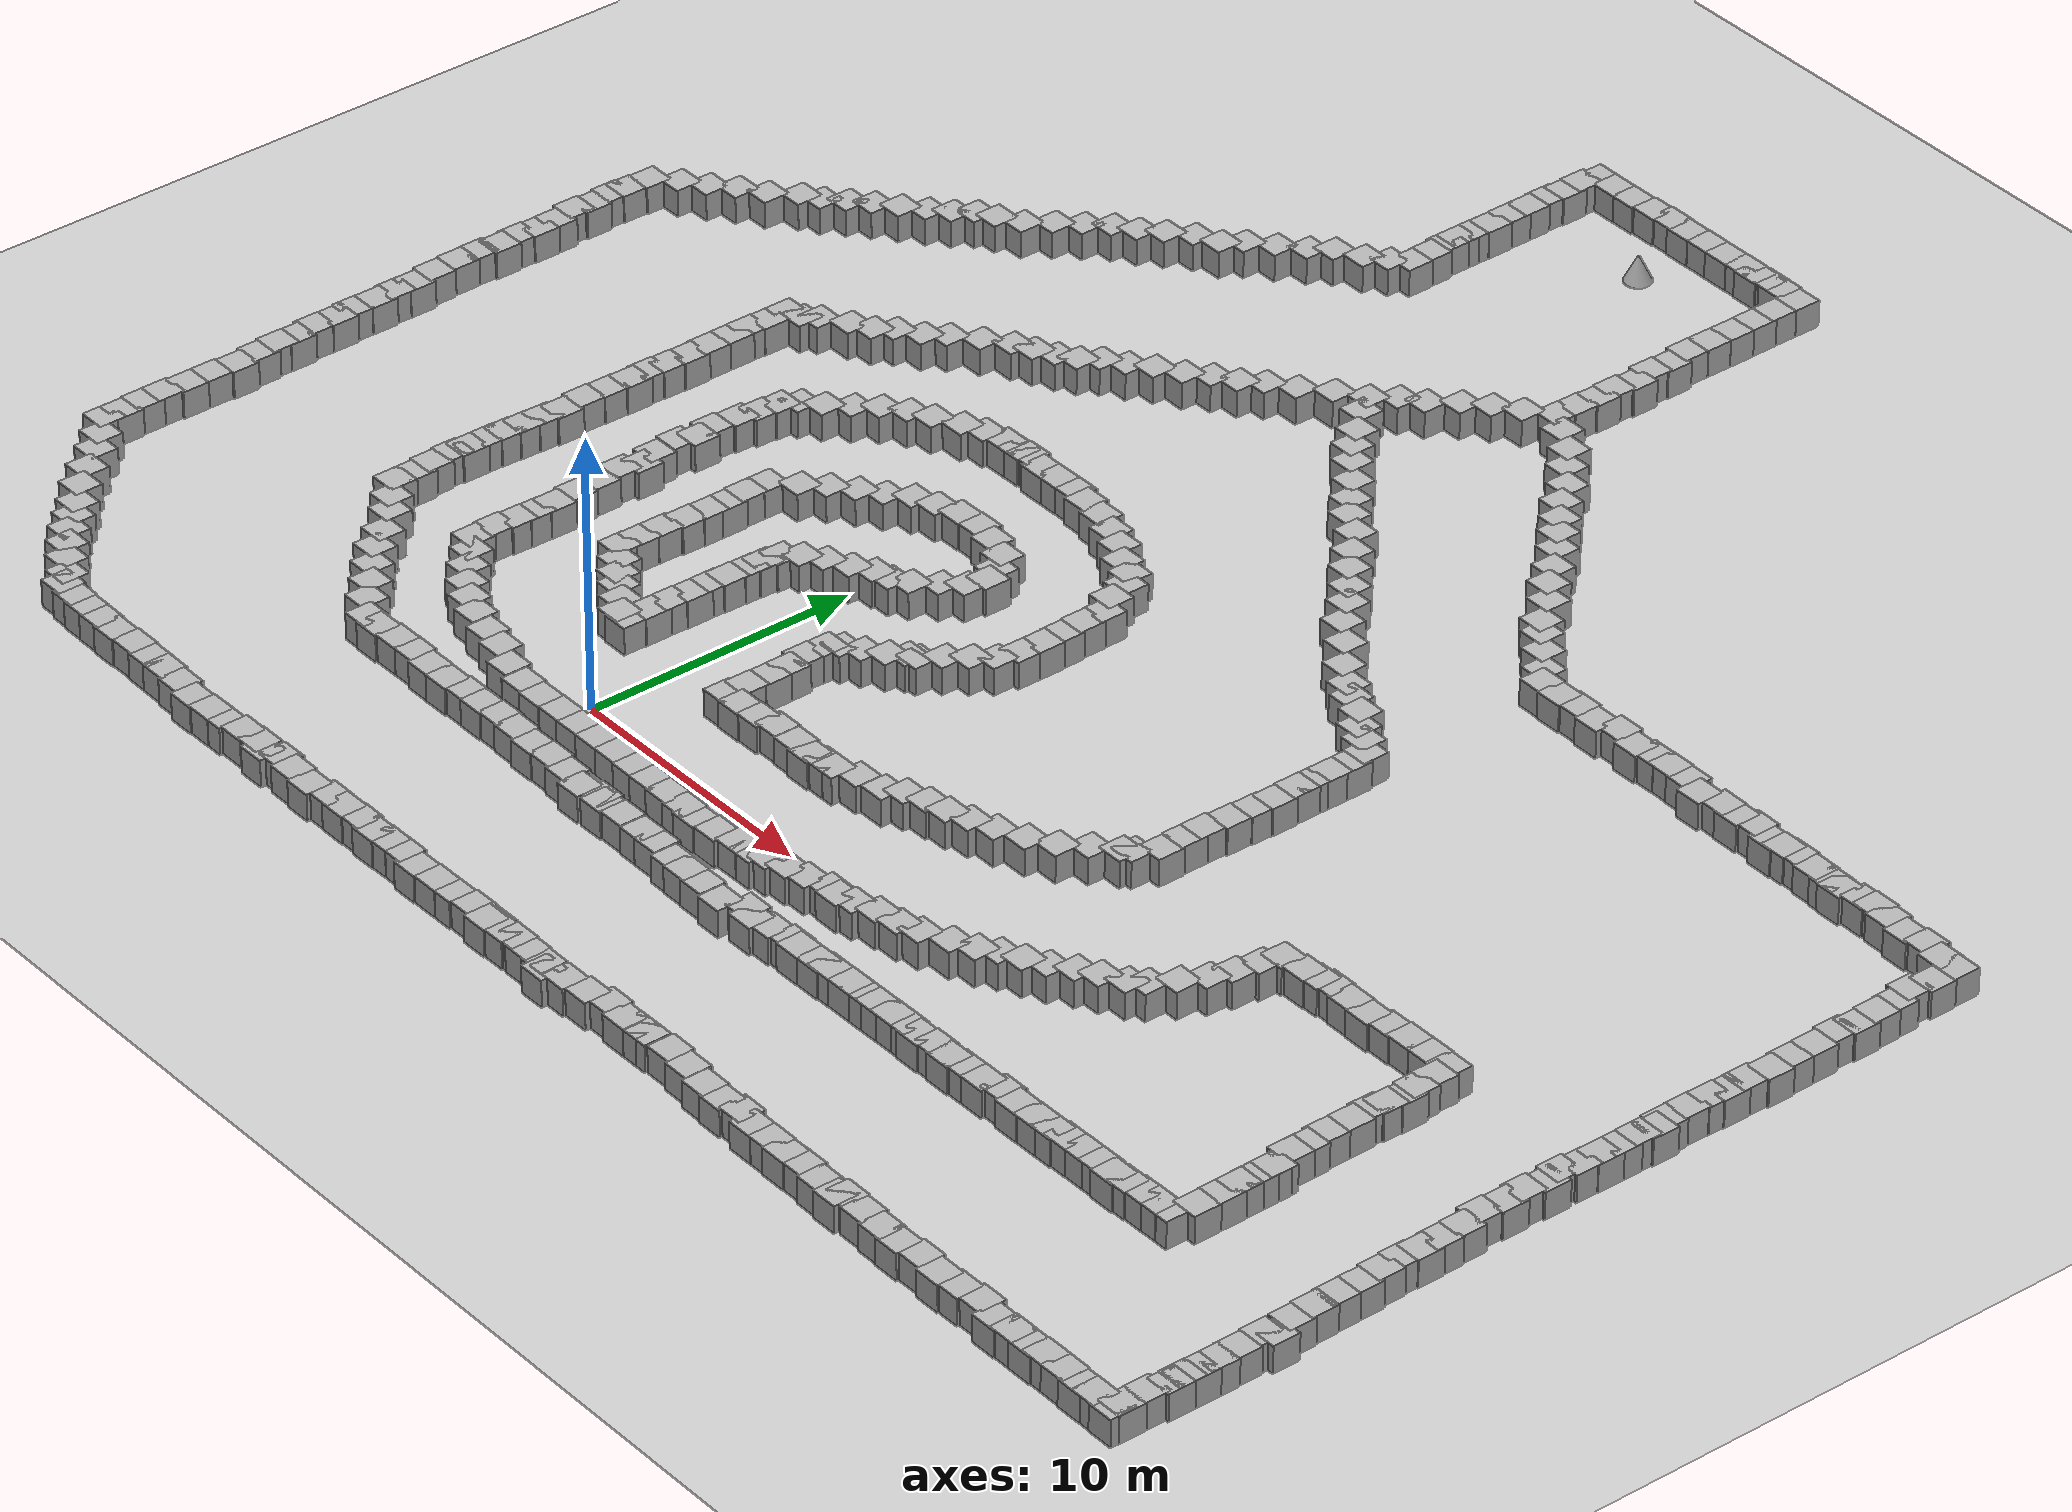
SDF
<sdf version='1.10'>
  <world name='empty'>
    <physics name='1ms' type='ignored'>
      <max_step_size>0.001</max_step_size>
      <real_time_factor>1</real_time_factor>
      <real_time_update_rate>1000</real_time_update_rate>
    </physics>
    <plugin name='gz::sim::systems::Physics' filename='gz-sim-physics-system'/>
    <plugin name='gz::sim::systems::UserCommands' filename='gz-sim-user-commands-system'/>
    <plugin name='gz::sim::systems::SceneBroadcaster' filename='gz-sim-scene-broadcaster-system'/>
    <plugin name='gz::sim::systems::Contact' filename='gz-sim-contact-system'/>
    <gravity>0 0 -9.8000000000000007</gravity>
    <magnetic_field>5.5644999999999998e-06 2.2875799999999999e-05 -4.2388400000000002e-05</magnetic_field>
    <atmosphere type='adiabatic'/>
    <scene>
      <ambient>0.400000006 0.400000006 0.400000006 1</ambient>
      <background>0.699999988 0.699999988 0.699999988 1</background>
      <shadows>true</shadows>
    </scene>
    <model name='ground_plane'>
      <static>true</static>
      <link name='link'>
        <collision name='collision'>
          <geometry>
            <plane>
              <normal>0 0 1</normal>
              <size>100 100</size>
            </plane>
          </geometry>
          <surface>
            <friction>
              <ode/>
            </friction>
            <bounce/>
            <contact/>
          </surface>
        </collision>
        <visual name='visual'>
          <geometry>
            <plane>
              <normal>0 0 1</normal>
              <size>100 100</size>
            </plane>
          </geometry>
          <material>
            <ambient>0.800000012 0.800000012 0.800000012 1</ambient>
            <diffuse>0.800000012 0.800000012 0.800000012 1</diffuse>
            <specular>0.800000012 0.800000012 0.800000012 1</specular>
          </material>
        </visual>
        <pose>0 0 0 0 0 0</pose>
        <inertial>
          <pose>0 0 0 0 0 0</pose>
          <mass>1</mass>
          <inertia>
            <ixx>1</ixx>
            <ixy>0</ixy>
            <ixz>0</ixz>
            <iyy>1</iyy>
            <iyz>0</iyz>
            <izz>1</izz>
          </inertia>
        </inertial>
        <enable_wind>false</enable_wind>
      </link>
      <pose>0 0 0 0 0 0</pose>
      <self_collide>false</self_collide>
    </model>
    <model name='box'>
      <pose>-0.5103118022990687 -1.5572371090333519 0.5 0 0 0</pose>
      <link name='box_link'>
        <inertial>
          <inertia>
            <ixx>0.16666</ixx>
            <ixy>0</ixy>
            <ixz>0</ixz>
            <iyy>0.16666</iyy>
            <iyz>0</iyz>
            <izz>0.16666</izz>
          </inertia>
          <mass>1</mass>
          <pose>0 0 0 0 0 0</pose>
        </inertial>
        <collision name='box_collision'>
          <geometry>
            <box>
              <size>1 1 1</size>
            </box>
          </geometry>
          <surface>
            <friction>
              <ode/>
            </friction>
            <bounce/>
            <contact/>
          </surface>
        </collision>
        <visual name='box_visual'>
          <geometry>
            <box>
              <size>1 1 1</size>
            </box>
          </geometry>
          <material>
            <ambient>0.300000012 0.300000012 0.300000012 1</ambient>
            <diffuse>0.699999988 0.699999988 0.699999988 1</diffuse>
            <specular>1 1 1 1</specular>
          </material>
        </visual>
        <pose>0 0 0 0 0 0</pose>
        <enable_wind>false</enable_wind>
      </link>
      <static>false</static>
      <self_collide>false</self_collide>
    </model>
    <model name='box_0'>
      <pose>0.465324749371955 -1.5421919059583278 0.5 0 0 0</pose>
      <link name='box_link'>
        <inertial>
          <inertia>
            <ixx>0.16666</ixx>
            <ixy>0</ixy>
            <ixz>0</ixz>
            <iyy>0.16666</iyy>
            <iyz>0</iyz>
            <izz>0.16666</izz>
          </inertia>
          <mass>1</mass>
          <pose>0 0 0 0 0 0</pose>
        </inertial>
        <collision name='box_collision'>
          <geometry>
            <box>
              <size>1 1 1</size>
            </box>
          </geometry>
          <surface>
            <friction>
              <ode/>
            </friction>
            <bounce/>
            <contact/>
          </surface>
        </collision>
        <visual name='box_visual'>
          <geometry>
            <box>
              <size>1 1 1</size>
            </box>
          </geometry>
          <material>
            <ambient>0.300000012 0.300000012 0.300000012 1</ambient>
            <diffuse>0.699999988 0.699999988 0.699999988 1</diffuse>
            <specular>1 1 1 1</specular>
          </material>
        </visual>
        <pose>0 0 0 0 0 0</pose>
        <enable_wind>false</enable_wind>
      </link>
      <static>false</static>
      <self_collide>false</self_collide>
    </model>
    <model name='box_1'>
      <pose>1.3908001001700212 -1.550012316120148 0.5 0 0 0</pose>
      <link name='box_link'>
        <inertial>
          <inertia>
            <ixx>0.16666</ixx>
            <ixy>0</ixy>
            <ixz>0</ixz>
            <iyy>0.16666</iyy>
            <iyz>0</iyz>
            <izz>0.16666</izz>
          </inertia>
          <mass>1</mass>
          <pose>0 0 0 0 0 0</pose>
        </inertial>
        <collision name='box_collision'>
          <geometry>
            <box>
              <size>1 1 1</size>
            </box>
          </geometry>
          <surface>
            <friction>
              <ode/>
            </friction>
            <bounce/>
            <contact/>
          </surface>
        </collision>
        <visual name='box_visual'>
          <geometry>
            <box>
              <size>1 1 1</size>
            </box>
          </geometry>
          <material>
            <ambient>0.300000012 0.300000012 0.300000012 1</ambient>
            <diffuse>0.699999988 0.699999988 0.699999988 1</diffuse>
            <specular>1 1 1 1</specular>
          </material>
        </visual>
        <pose>0 0 0 0 0 0</pose>
        <enable_wind>false</enable_wind>
      </link>
      <static>false</static>
      <self_collide>false</self_collide>
    </model>
    <model name='box_2'>
      <pose>2.3780240748902814 -1.5593532998291624 0.5 0 0 0</pose>
      <link name='box_link'>
        <inertial>
          <inertia>
            <ixx>0.16666</ixx>
            <ixy>0</ixy>
            <ixz>0</ixz>
            <iyy>0.16666</iyy>
            <iyz>0</iyz>
            <izz>0.16666</izz>
          </inertia>
          <mass>1</mass>
          <pose>0 0 0 0 0 0</pose>
        </inertial>
        <collision name='box_collision'>
          <geometry>
            <box>
              <size>1 1 1</size>
            </box>
          </geometry>
          <surface>
            <friction>
              <ode/>
            </friction>
            <bounce/>
            <contact/>
          </surface>
        </collision>
        <visual name='box_visual'>
          <geometry>
            <box>
              <size>1 1 1</size>
            </box>
          </geometry>
          <material>
            <ambient>0.300000012 0.300000012 0.300000012 1</ambient>
            <diffuse>0.699999988 0.699999988 0.699999988 1</diffuse>
            <specular>1 1 1 1</specular>
          </material>
        </visual>
        <pose>0 0 0 0 0 0</pose>
        <enable_wind>false</enable_wind>
      </link>
      <static>false</static>
      <self_collide>false</self_collide>
    </model>
    <model name='box_3'>
      <pose>3.32570040269158 -1.5574516324013623 0.5 0 0 0</pose>
      <link name='box_link'>
        <inertial>
          <inertia>
            <ixx>0.16666</ixx>
            <ixy>0</ixy>
            <ixz>0</ixz>
            <iyy>0.16666</iyy>
            <iyz>0</iyz>
            <izz>0.16666</izz>
          </inertia>
          <mass>1</mass>
          <pose>0 0 0 0 0 0</pose>
        </inertial>
        <collision name='box_collision'>
          <geometry>
            <box>
              <size>1 1 1</size>
            </box>
          </geometry>
          <surface>
            <friction>
              <ode/>
            </friction>
            <bounce/>
            <contact/>
          </surface>
        </collision>
        <visual name='box_visual'>
          <geometry>
            <box>
              <size>1 1 1</size>
            </box>
          </geometry>
          <material>
            <ambient>0.300000012 0.300000012 0.300000012 1</ambient>
            <diffuse>0.699999988 0.699999988 0.699999988 1</diffuse>
            <specular>1 1 1 1</specular>
          </material>
        </visual>
        <pose>0 0 0 0 0 0</pose>
        <enable_wind>false</enable_wind>
      </link>
      <static>false</static>
      <self_collide>false</self_collide>
    </model>
    <model name='box_4'>
      <pose>4.3095598220825195 -1.5955400466918945 0.5 0 0 0</pose>
      <link name='box_link'>
        <inertial>
          <inertia>
            <ixx>0.16666</ixx>
            <ixy>0</ixy>
            <ixz>0</ixz>
            <iyy>0.16666</iyy>
            <iyz>0</iyz>
            <izz>0.16666</izz>
          </inertia>
          <mass>1</mass>
          <pose>0 0 0 0 0 0</pose>
        </inertial>
        <collision name='box_collision'>
          <geometry>
            <box>
              <size>1 1 1</size>
            </box>
          </geometry>
          <surface>
            <friction>
              <ode/>
            </friction>
            <bounce/>
            <contact/>
          </surface>
        </collision>
        <visual name='box_visual'>
          <geometry>
            <box>
              <size>1 1 1</size>
            </box>
          </geometry>
          <material>
            <ambient>0.300000012 0.300000012 0.300000012 1</ambient>
            <diffuse>0.699999988 0.699999988 0.699999988 1</diffuse>
            <specular>1 1 1 1</specular>
          </material>
        </visual>
        <pose>0 0 0 0 0 0</pose>
        <enable_wind>false</enable_wind>
      </link>
      <static>false</static>
      <self_collide>false</self_collide>
    </model>
    <model name='box_5'>
      <pose>5.1638998985290527 -1.6039999723434448 0.5 0 0 0</pose>
      <link name='box_link'>
        <inertial>
          <inertia>
            <ixx>0.16666</ixx>
            <ixy>0</ixy>
            <ixz>0</ixz>
            <iyy>0.16666</iyy>
            <iyz>0</iyz>
            <izz>0.16666</izz>
          </inertia>
          <mass>1</mass>
          <pose>0 0 0 0 0 0</pose>
        </inertial>
        <collision name='box_collision'>
          <geometry>
            <box>
              <size>1 1 1</size>
            </box>
          </geometry>
          <surface>
            <friction>
              <ode/>
            </friction>
            <bounce/>
            <contact/>
          </surface>
        </collision>
        <visual name='box_visual'>
          <geometry>
            <box>
              <size>1 1 1</size>
            </box>
          </geometry>
          <material>
            <ambient>0.300000012 0.300000012 0.300000012 1</ambient>
            <diffuse>0.699999988 0.699999988 0.699999988 1</diffuse>
            <specular>1 1 1 1</specular>
          </material>
        </visual>
        <pose>0 0 0 0 0 0</pose>
        <enable_wind>false</enable_wind>
      </link>
      <static>false</static>
      <self_collide>false</self_collide>
    </model>
    <model name='box_6'>
      <pose>6.0194320302158717 -1.6390551681615317 0.5 0 0 0</pose>
      <link name='box_link'>
        <inertial>
          <inertia>
            <ixx>0.16666</ixx>
            <ixy>0</ixy>
            <ixz>0</ixz>
            <iyy>0.16666</iyy>
            <iyz>0</iyz>
            <izz>0.16666</izz>
          </inertia>
          <mass>1</mass>
          <pose>0 0 0 0 0 0</pose>
        </inertial>
        <collision name='box_collision'>
          <geometry>
            <box>
              <size>1 1 1</size>
            </box>
          </geometry>
          <surface>
            <friction>
              <ode/>
            </friction>
            <bounce/>
            <contact/>
          </surface>
        </collision>
        <visual name='box_visual'>
          <geometry>
            <box>
              <size>1 1 1</size>
            </box>
          </geometry>
          <material>
            <ambient>0.300000012 0.300000012 0.300000012 1</ambient>
            <diffuse>0.699999988 0.699999988 0.699999988 1</diffuse>
            <specular>1 1 1 1</specular>
          </material>
        </visual>
        <pose>0 0 0 0 0 0</pose>
        <enable_wind>false</enable_wind>
      </link>
      <static>false</static>
      <self_collide>false</self_collide>
    </model>
    <model name='box_7'>
      <pose>6.9316211139197259 -1.6916820472834306 0.5 0 0 0</pose>
      <link name='box_link'>
        <inertial>
          <inertia>
            <ixx>0.16666</ixx>
            <ixy>0</ixy>
            <ixz>0</ixz>
            <iyy>0.16666</iyy>
            <iyz>0</iyz>
            <izz>0.16666</izz>
          </inertia>
          <mass>1</mass>
          <pose>0 0 0 0 0 0</pose>
        </inertial>
        <collision name='box_collision'>
          <geometry>
            <box>
              <size>1 1 1</size>
            </box>
          </geometry>
          <surface>
            <friction>
              <ode/>
            </friction>
            <bounce/>
            <contact/>
          </surface>
        </collision>
        <visual name='box_visual'>
          <geometry>
            <box>
              <size>1 1 1</size>
            </box>
          </geometry>
          <material>
            <ambient>0.300000012 0.300000012 0.300000012 1</ambient>
            <diffuse>0.699999988 0.699999988 0.699999988 1</diffuse>
            <specular>1 1 1 1</specular>
          </material>
        </visual>
        <pose>0 0 0 0 0 0</pose>
        <enable_wind>false</enable_wind>
      </link>
      <static>false</static>
      <self_collide>false</self_collide>
    </model>
    <model name='box_8'>
      <pose>-1.4691949986557939 -1.5029652012372097 0.5 0 0 0</pose>
      <link name='box_link'>
        <inertial>
          <inertia>
            <ixx>0.16666</ixx>
            <ixy>0</ixy>
            <ixz>0</ixz>
            <iyy>0.16666</iyy>
            <iyz>0</iyz>
            <izz>0.16666</izz>
          </inertia>
          <mass>1</mass>
          <pose>0 0 0 0 0 0</pose>
        </inertial>
        <collision name='box_collision'>
          <geometry>
            <box>
              <size>1 1 1</size>
            </box>
          </geometry>
          <surface>
            <friction>
              <ode/>
            </friction>
            <bounce/>
            <contact/>
          </surface>
        </collision>
        <visual name='box_visual'>
          <geometry>
            <box>
              <size>1 1 1</size>
            </box>
          </geometry>
          <material>
            <ambient>0.300000012 0.300000012 0.300000012 1</ambient>
            <diffuse>0.699999988 0.699999988 0.699999988 1</diffuse>
            <specular>1 1 1 1</specular>
          </material>
        </visual>
        <pose>0 0 0 0 0 0</pose>
        <enable_wind>false</enable_wind>
      </link>
      <static>false</static>
      <self_collide>false</self_collide>
    </model>
    <model name='box_9'>
      <pose>-2.5003136378093527 -1.3086043863022381 0.5 0 0 0</pose>
      <link name='box_link'>
        <inertial>
          <inertia>
            <ixx>0.16666</ixx>
            <ixy>0</ixy>
            <ixz>0</ixz>
            <iyy>0.16666</iyy>
            <iyz>0</iyz>
            <izz>0.16666</izz>
          </inertia>
          <mass>1</mass>
          <pose>0 0 0 0 0 0</pose>
        </inertial>
        <collision name='box_collision'>
          <geometry>
            <box>
              <size>1 1 1</size>
            </box>
          </geometry>
          <surface>
            <friction>
              <ode/>
            </friction>
            <bounce/>
            <contact/>
          </surface>
        </collision>
        <visual name='box_visual'>
          <geometry>
            <box>
              <size>1 1 1</size>
            </box>
          </geometry>
          <material>
            <ambient>0.300000012 0.300000012 0.300000012 1</ambient>
            <diffuse>0.699999988 0.699999988 0.699999988 1</diffuse>
            <specular>1 1 1 1</specular>
          </material>
        </visual>
        <pose>0 0 0 0 0 0</pose>
        <enable_wind>false</enable_wind>
      </link>
      <static>false</static>
      <self_collide>false</self_collide>
    </model>
    <model name='box_10'>
      <pose>-3.4968930083323273 -0.8743732851774022 0.5 0 0 0</pose>
      <link name='box_link'>
        <inertial>
          <inertia>
            <ixx>0.16666</ixx>
            <ixy>0</ixy>
            <ixz>0</ixz>
            <iyy>0.16666</iyy>
            <iyz>0</iyz>
            <izz>0.16666</izz>
          </inertia>
          <mass>1</mass>
          <pose>0 0 0 0 0 0</pose>
        </inertial>
        <collision name='box_collision'>
          <geometry>
            <box>
              <size>1 1 1</size>
            </box>
          </geometry>
          <surface>
            <friction>
              <ode/>
            </friction>
            <bounce/>
            <contact/>
          </surface>
        </collision>
        <visual name='box_visual'>
          <geometry>
            <box>
              <size>1 1 1</size>
            </box>
          </geometry>
          <material>
            <ambient>0.300000012 0.300000012 0.300000012 1</ambient>
            <diffuse>0.699999988 0.699999988 0.699999988 1</diffuse>
            <specular>1 1 1 1</specular>
          </material>
        </visual>
        <pose>0 0 0 0 0 0</pose>
        <enable_wind>false</enable_wind>
      </link>
      <static>false</static>
      <self_collide>false</self_collide>
    </model>
    <model name='box_11'>
      <pose>-4.4232375011744631 -0.67955977234431431 0.5 0 0 0</pose>
      <link name='box_link'>
        <inertial>
          <inertia>
            <ixx>0.16666</ixx>
            <ixy>0</ixy>
            <ixz>0</ixz>
            <iyy>0.16666</iyy>
            <iyz>0</iyz>
            <izz>0.16666</izz>
          </inertia>
          <mass>1</mass>
          <pose>0 0 0 0 0 0</pose>
        </inertial>
        <collision name='box_collision'>
          <geometry>
            <box>
              <size>1 1 1</size>
            </box>
          </geometry>
          <surface>
            <friction>
              <ode/>
            </friction>
            <bounce/>
            <contact/>
          </surface>
        </collision>
        <visual name='box_visual'>
          <geometry>
            <box>
              <size>1 1 1</size>
            </box>
          </geometry>
          <material>
            <ambient>0.300000012 0.300000012 0.300000012 1</ambient>
            <diffuse>0.699999988 0.699999988 0.699999988 1</diffuse>
            <specular>1 1 1 1</specular>
          </material>
        </visual>
        <pose>0 0 0 0 0 0</pose>
        <enable_wind>false</enable_wind>
      </link>
      <static>false</static>
      <self_collide>false</self_collide>
    </model>
    <model name='box_12'>
      <pose>-5.4517876371504554 -0.38332490231765015 0.5 0 0 0</pose>
      <link name='box_link'>
        <inertial>
          <inertia>
            <ixx>0.16666</ixx>
            <ixy>0</ixy>
            <ixz>0</ixz>
            <iyy>0.16666</iyy>
            <iyz>0</iyz>
            <izz>0.16666</izz>
          </inertia>
          <mass>1</mass>
          <pose>0 0 0 0 0 0</pose>
        </inertial>
        <collision name='box_collision'>
          <geometry>
            <box>
              <size>1 1 1</size>
            </box>
          </geometry>
          <surface>
            <friction>
              <ode/>
            </friction>
            <bounce/>
            <contact/>
          </surface>
        </collision>
        <visual name='box_visual'>
          <geometry>
            <box>
              <size>1 1 1</size>
            </box>
          </geometry>
          <material>
            <ambient>0.300000012 0.300000012 0.300000012 1</ambient>
            <diffuse>0.699999988 0.699999988 0.699999988 1</diffuse>
            <specular>1 1 1 1</specular>
          </material>
        </visual>
        <pose>0 0 0 0 0 0</pose>
        <enable_wind>false</enable_wind>
      </link>
      <static>false</static>
      <self_collide>false</self_collide>
    </model>
    <model name='box_13'>
      <pose>-6.2373800277709961 -0.051265798509120941 0.5 0 0 0</pose>
      <link name='box_link'>
        <inertial>
          <inertia>
            <ixx>0.16666</ixx>
            <ixy>0</ixy>
            <ixz>0</ixz>
            <iyy>0.16666</iyy>
            <iyz>0</iyz>
            <izz>0.16666</izz>
          </inertia>
          <mass>1</mass>
          <pose>0 0 0 0 0 0</pose>
        </inertial>
        <collision name='box_collision'>
          <geometry>
            <box>
              <size>1 1 1</size>
            </box>
          </geometry>
          <surface>
            <friction>
              <ode/>
            </friction>
            <bounce/>
            <contact/>
          </surface>
        </collision>
        <visual name='box_visual'>
          <geometry>
            <box>
              <size>1 1 1</size>
            </box>
          </geometry>
          <material>
            <ambient>0.300000012 0.300000012 0.300000012 1</ambient>
            <diffuse>0.699999988 0.699999988 0.699999988 1</diffuse>
            <specular>1 1 1 1</specular>
          </material>
        </visual>
        <pose>0 0 0 0 0 0</pose>
        <enable_wind>false</enable_wind>
      </link>
      <static>false</static>
      <self_collide>false</self_collide>
    </model>
    <model name='box_14'>
      <pose>-6.9554026283552153 0.38368040429650563 0.5 0 0 0</pose>
      <link name='box_link'>
        <inertial>
          <inertia>
            <ixx>0.16666</ixx>
            <ixy>0</ixy>
            <ixz>0</ixz>
            <iyy>0.16666</iyy>
            <iyz>0</iyz>
            <izz>0.16666</izz>
          </inertia>
          <mass>1</mass>
          <pose>0 0 0 0 0 0</pose>
        </inertial>
        <collision name='box_collision'>
          <geometry>
            <box>
              <size>1 1 1</size>
            </box>
          </geometry>
          <surface>
            <friction>
              <ode/>
            </friction>
            <bounce/>
            <contact/>
          </surface>
        </collision>
        <visual name='box_visual'>
          <geometry>
            <box>
              <size>1 1 1</size>
            </box>
          </geometry>
          <material>
            <ambient>0.300000012 0.300000012 0.300000012 1</ambient>
            <diffuse>0.699999988 0.699999988 0.699999988 1</diffuse>
            <specular>1 1 1 1</specular>
          </material>
        </visual>
        <pose>0 0 0 0 0 0</pose>
        <enable_wind>false</enable_wind>
      </link>
      <static>false</static>
      <self_collide>false</self_collide>
    </model>
    <model name='box_15'>
      <pose>-7.6692439723208015 0.95319792340135789 0.5 0 0 0</pose>
      <link name='box_link'>
        <inertial>
          <inertia>
            <ixx>0.16666</ixx>
            <ixy>0</ixy>
            <ixz>0</ixz>
            <iyy>0.16666</iyy>
            <iyz>0</iyz>
            <izz>0.16666</izz>
          </inertia>
          <mass>1</mass>
          <pose>0 0 0 0 0 0</pose>
        </inertial>
        <collision name='box_collision'>
          <geometry>
            <box>
              <size>1 1 1</size>
            </box>
          </geometry>
          <surface>
            <friction>
              <ode/>
            </friction>
            <bounce/>
            <contact/>
          </surface>
        </collision>
        <visual name='box_visual'>
          <geometry>
            <box>
              <size>1 1 1</size>
            </box>
          </geometry>
          <material>
            <ambient>0.300000012 0.300000012 0.300000012 1</ambient>
            <diffuse>0.699999988 0.699999988 0.699999988 1</diffuse>
            <specular>1 1 1 1</specular>
          </material>
        </visual>
        <pose>0 0 0 0 0 0</pose>
        <enable_wind>false</enable_wind>
      </link>
      <static>false</static>
      <self_collide>false</self_collide>
    </model>
    <model name='box_16'>
      <pose>-8.3134256486186651 1.5560085388121672 0.5 0 0 0</pose>
      <link name='box_link'>
        <inertial>
          <inertia>
            <ixx>0.16666</ixx>
            <ixy>0</ixy>
            <ixz>0</ixz>
            <iyy>0.16666</iyy>
            <iyz>0</iyz>
            <izz>0.16666</izz>
          </inertia>
          <mass>1</mass>
          <pose>0 0 0 0 0 0</pose>
        </inertial>
        <collision name='box_collision'>
          <geometry>
            <box>
              <size>1 1 1</size>
            </box>
          </geometry>
          <surface>
            <friction>
              <ode/>
            </friction>
            <bounce/>
            <contact/>
          </surface>
        </collision>
        <visual name='box_visual'>
          <geometry>
            <box>
              <size>1 1 1</size>
            </box>
          </geometry>
          <material>
            <ambient>0.300000012 0.300000012 0.300000012 1</ambient>
            <diffuse>0.699999988 0.699999988 0.699999988 1</diffuse>
            <specular>1 1 1 1</specular>
          </material>
        </visual>
        <pose>0 0 0 0 0 0</pose>
        <enable_wind>false</enable_wind>
      </link>
      <static>false</static>
      <self_collide>false</self_collide>
    </model>
    <model name='box_17'>
      <pose>-8.8900060211585394 2.0571078484096716 0.5 0 0 0</pose>
      <link name='box_link'>
        <inertial>
          <inertia>
            <ixx>0.16666</ixx>
            <ixy>0</ixy>
            <ixz>0</ixz>
            <iyy>0.16666</iyy>
            <iyz>0</iyz>
            <izz>0.16666</izz>
          </inertia>
          <mass>1</mass>
          <pose>0 0 0 0 0 0</pose>
        </inertial>
        <collision name='box_collision'>
          <geometry>
            <box>
              <size>1 1 1</size>
            </box>
          </geometry>
          <surface>
            <friction>
              <ode/>
            </friction>
            <bounce/>
            <contact/>
          </surface>
        </collision>
        <visual name='box_visual'>
          <geometry>
            <box>
              <size>1 1 1</size>
            </box>
          </geometry>
          <material>
            <ambient>0.300000012 0.300000012 0.300000012 1</ambient>
            <diffuse>0.699999988 0.699999988 0.699999988 1</diffuse>
            <specular>1 1 1 1</specular>
          </material>
        </visual>
        <pose>0 0 0 0 0 0</pose>
        <enable_wind>false</enable_wind>
      </link>
      <static>false</static>
      <self_collide>false</self_collide>
    </model>
    <model name='box_18'>
      <pose>-8.9467301686917917 2.964929724458182 0.5 0 0 0</pose>
      <link name='box_link'>
        <inertial>
          <inertia>
            <ixx>0.16666</ixx>
            <ixy>0</ixy>
            <ixz>0</ixz>
            <iyy>0.16666</iyy>
            <iyz>0</iyz>
            <izz>0.16666</izz>
          </inertia>
          <mass>1</mass>
          <pose>0 0 0 0 0 0</pose>
        </inertial>
        <collision name='box_collision'>
          <geometry>
            <box>
              <size>1 1 1</size>
            </box>
          </geometry>
          <surface>
            <friction>
              <ode/>
            </friction>
            <bounce/>
            <contact/>
          </surface>
        </collision>
        <visual name='box_visual'>
          <geometry>
            <box>
              <size>1 1 1</size>
            </box>
          </geometry>
          <material>
            <ambient>0.300000012 0.300000012 0.300000012 1</ambient>
            <diffuse>0.699999988 0.699999988 0.699999988 1</diffuse>
            <specular>1 1 1 1</specular>
          </material>
        </visual>
        <pose>0 0 0 0 0 0</pose>
        <enable_wind>false</enable_wind>
      </link>
      <static>false</static>
      <self_collide>false</self_collide>
    </model>
    <model name='box_19_1'>
      <pose>2.8898080161827115 2.9913672453019284 0.5 0 0 0</pose>
      <link name='box_link'>
        <inertial>
          <inertia>
            <ixx>0.16666</ixx>
            <ixy>0</ixy>
            <ixz>0</ixz>
            <iyy>0.16666</iyy>
            <iyz>0</iyz>
            <izz>0.16666</izz>
          </inertia>
          <mass>1</mass>
        </inertial>
        <collision name='box_collision'>
          <geometry>
            <box>
              <size>1 1 1</size>
            </box>
          </geometry>
          <surface>
            <friction>
              <ode/>
            </friction>
            <bounce/>
            <contact/>
          </surface>
        </collision>
        <visual name='box_visual'>
          <geometry>
            <box>
              <size>1 1 1</size>
            </box>
          </geometry>
          <material>
            <ambient>0.300000012 0.300000012 0.300000012 1</ambient>
            <diffuse>0.699999988 0.699999988 0.699999988 1</diffuse>
            <specular>1 1 1 1</specular>
          </material>
        </visual>
      </link>
      <static>false</static>
      <self_collide>false</self_collide>
    </model>
    <model name='box_7_1'>
      <pose>2.9451916872459045 3.7643464646409432 0.5 0 0 0</pose>
      <link name='box_link'>
        <inertial>
          <inertia>
            <ixx>0.16666</ixx>
            <ixy>0</ixy>
            <ixz>0</ixz>
            <iyy>0.16666</iyy>
            <iyz>0</iyz>
            <izz>0.16666</izz>
          </inertia>
          <mass>1</mass>
        </inertial>
        <collision name='box_collision'>
          <geometry>
            <box>
              <size>1 1 1</size>
            </box>
          </geometry>
          <surface>
            <friction>
              <ode/>
            </friction>
            <bounce/>
            <contact/>
          </surface>
        </collision>
        <visual name='box_visual'>
          <geometry>
            <box>
              <size>1 1 1</size>
            </box>
          </geometry>
          <material>
            <ambient>0.300000012 0.300000012 0.300000012 1</ambient>
            <diffuse>0.699999988 0.699999988 0.699999988 1</diffuse>
            <specular>1 1 1 1</specular>
          </material>
        </visual>
      </link>
      <static>false</static>
      <self_collide>false</self_collide>
    </model>
    <model name='box_7_2'>
      <pose>2.965733301422552 4.6017455559055556 0.5 0 0 0</pose>
      <link name='box_link'>
        <inertial>
          <inertia>
            <ixx>0.16666</ixx>
            <ixy>0</ixy>
            <ixz>0</ixz>
            <iyy>0.16666</iyy>
            <iyz>0</iyz>
            <izz>0.16666</izz>
          </inertia>
          <mass>1</mass>
        </inertial>
        <collision name='box_collision'>
          <geometry>
            <box>
              <size>1 1 1</size>
            </box>
          </geometry>
          <surface>
            <friction>
              <ode/>
            </friction>
            <bounce/>
            <contact/>
          </surface>
        </collision>
        <visual name='box_visual'>
          <geometry>
            <box>
              <size>1 1 1</size>
            </box>
          </geometry>
          <material>
            <ambient>0.300000012 0.300000012 0.300000012 1</ambient>
            <diffuse>0.699999988 0.699999988 0.699999988 1</diffuse>
            <specular>1 1 1 1</specular>
          </material>
        </visual>
      </link>
      <static>false</static>
      <self_collide>false</self_collide>
    </model>
    <model name='box_7_3'>
      <pose>2.9526592685858302 5.3668695491442442 0.5 0 0 0</pose>
      <link name='box_link'>
        <inertial>
          <inertia>
            <ixx>0.16666</ixx>
            <ixy>0</ixy>
            <ixz>0</ixz>
            <iyy>0.16666</iyy>
            <iyz>0</iyz>
            <izz>0.16666</izz>
          </inertia>
          <mass>1</mass>
        </inertial>
        <collision name='box_collision'>
          <geometry>
            <box>
              <size>1 1 1</size>
            </box>
          </geometry>
          <surface>
            <friction>
              <ode/>
            </friction>
            <bounce/>
            <contact/>
          </surface>
        </collision>
        <visual name='box_visual'>
          <geometry>
            <box>
              <size>1 1 1</size>
            </box>
          </geometry>
          <material>
            <ambient>0.300000012 0.300000012 0.300000012 1</ambient>
            <diffuse>0.699999988 0.699999988 0.699999988 1</diffuse>
            <specular>1 1 1 1</specular>
          </material>
        </visual>
      </link>
      <static>false</static>
      <self_collide>false</self_collide>
    </model>
    <model name='box_7_4'>
      <pose>2.8049931583423278 6.1290741332245302 0.5 0 0 0</pose>
      <link name='box_link'>
        <inertial>
          <inertia>
            <ixx>0.16666</ixx>
            <ixy>0</ixy>
            <ixz>0</ixz>
            <iyy>0.16666</iyy>
            <iyz>0</iyz>
            <izz>0.16666</izz>
          </inertia>
          <mass>1</mass>
        </inertial>
        <collision name='box_collision'>
          <geometry>
            <box>
              <size>1 1 1</size>
            </box>
          </geometry>
          <surface>
            <friction>
              <ode/>
            </friction>
            <bounce/>
            <contact/>
          </surface>
        </collision>
        <visual name='box_visual'>
          <geometry>
            <box>
              <size>1 1 1</size>
            </box>
          </geometry>
          <material>
            <ambient>0.300000012 0.300000012 0.300000012 1</ambient>
            <diffuse>0.699999988 0.699999988 0.699999988 1</diffuse>
            <specular>1 1 1 1</specular>
          </material>
        </visual>
      </link>
      <static>false</static>
      <self_collide>false</self_collide>
    </model>
    <model name='box_7_5'>
      <pose>2.8257385187786537 6.9584155599908932 0.5 0 0 0</pose>
      <link name='box_link'>
        <inertial>
          <inertia>
            <ixx>0.16666</ixx>
            <ixy>0</ixy>
            <ixz>0</ixz>
            <iyy>0.16666</iyy>
            <iyz>0</iyz>
            <izz>0.16666</izz>
          </inertia>
          <mass>1</mass>
        </inertial>
        <collision name='box_collision'>
          <geometry>
            <box>
              <size>1 1 1</size>
            </box>
          </geometry>
          <surface>
            <friction>
              <ode/>
            </friction>
            <bounce/>
            <contact/>
          </surface>
        </collision>
        <visual name='box_visual'>
          <geometry>
            <box>
              <size>1 1 1</size>
            </box>
          </geometry>
          <material>
            <ambient>0.300000012 0.300000012 0.300000012 1</ambient>
            <diffuse>0.699999988 0.699999988 0.699999988 1</diffuse>
            <specular>1 1 1 1</specular>
          </material>
        </visual>
      </link>
      <static>false</static>
      <self_collide>false</self_collide>
    </model>
    <model name='box_7_6'>
      <pose>-2.689199144929955 3.1326155944008862 0.5 0 0 0</pose>
      <link name='box_link'>
        <inertial>
          <inertia>
            <ixx>0.16666</ixx>
            <ixy>0</ixy>
            <ixz>0</ixz>
            <iyy>0.16666</iyy>
            <iyz>0</iyz>
            <izz>0.16666</izz>
          </inertia>
          <mass>1</mass>
        </inertial>
        <collision name='box_collision'>
          <geometry>
            <box>
              <size>1 1 1</size>
            </box>
          </geometry>
          <surface>
            <friction>
              <ode/>
            </friction>
            <bounce/>
            <contact/>
          </surface>
        </collision>
        <visual name='box_visual'>
          <geometry>
            <box>
              <size>1 1 1</size>
            </box>
          </geometry>
          <material>
            <ambient>0.300000012 0.300000012 0.300000012 1</ambient>
            <diffuse>0.699999988 0.699999988 0.699999988 1</diffuse>
            <specular>1 1 1 1</specular>
          </material>
        </visual>
      </link>
      <static>false</static>
      <self_collide>false</self_collide>
    </model>
    <model name='box_7_7'>
      <pose>-3.2342162004722481 3.5629760571669751 0.5 0 0 0</pose>
      <link name='box_link'>
        <inertial>
          <inertia>
            <ixx>0.16666</ixx>
            <ixy>0</ixy>
            <ixz>0</ixz>
            <iyy>0.16666</iyy>
            <iyz>0</iyz>
            <izz>0.16666</izz>
          </inertia>
          <mass>1</mass>
        </inertial>
        <collision name='box_collision'>
          <geometry>
            <box>
              <size>1 1 1</size>
            </box>
          </geometry>
          <surface>
            <friction>
              <ode/>
            </friction>
            <bounce/>
            <contact/>
          </surface>
        </collision>
        <visual name='box_visual'>
          <geometry>
            <box>
              <size>1 1 1</size>
            </box>
          </geometry>
          <material>
            <ambient>0.300000012 0.300000012 0.300000012 1</ambient>
            <diffuse>0.699999988 0.699999988 0.699999988 1</diffuse>
            <specular>1 1 1 1</specular>
          </material>
        </visual>
      </link>
      <static>false</static>
      <self_collide>false</self_collide>
    </model>
    <model name='box_7_8'>
      <pose>-3.8811139416638776 3.9923740787203537 0.5 0 0 0</pose>
      <link name='box_link'>
        <inertial>
          <inertia>
            <ixx>0.16666</ixx>
            <ixy>0</ixy>
            <ixz>0</ixz>
            <iyy>0.16666</iyy>
            <iyz>0</iyz>
            <izz>0.16666</izz>
          </inertia>
          <mass>1</mass>
        </inertial>
        <collision name='box_collision'>
          <geometry>
            <box>
              <size>1 1 1</size>
            </box>
          </geometry>
          <surface>
            <friction>
              <ode/>
            </friction>
            <bounce/>
            <contact/>
          </surface>
        </collision>
        <visual name='box_visual'>
          <geometry>
            <box>
              <size>1 1 1</size>
            </box>
          </geometry>
          <material>
            <ambient>0.300000012 0.300000012 0.300000012 1</ambient>
            <diffuse>0.699999988 0.699999988 0.699999988 1</diffuse>
            <specular>1 1 1 1</specular>
          </material>
        </visual>
      </link>
      <static>false</static>
      <self_collide>false</self_collide>
    </model>
    <model name='box_7_9'>
      <pose>-4.4240135839997397 4.3878270713158063 0.5 0 0 0</pose>
      <link name='box_link'>
        <inertial>
          <inertia>
            <ixx>0.16666</ixx>
            <ixy>0</ixy>
            <ixz>0</ixz>
            <iyy>0.16666</iyy>
            <iyz>0</iyz>
            <izz>0.16666</izz>
          </inertia>
          <mass>1</mass>
        </inertial>
        <collision name='box_collision'>
          <geometry>
            <box>
              <size>1 1 1</size>
            </box>
          </geometry>
          <surface>
            <friction>
              <ode/>
            </friction>
            <bounce/>
            <contact/>
          </surface>
        </collision>
        <visual name='box_visual'>
          <geometry>
            <box>
              <size>1 1 1</size>
            </box>
          </geometry>
          <material>
            <ambient>0.300000012 0.300000012 0.300000012 1</ambient>
            <diffuse>0.699999988 0.699999988 0.699999988 1</diffuse>
            <specular>1 1 1 1</specular>
          </material>
        </visual>
      </link>
      <static>false</static>
      <self_collide>false</self_collide>
    </model>
    <model name='box_7_10'>
      <pose>-5.0003705507495102 4.8492179712719894 0.5 0 0 0</pose>
      <link name='box_link'>
        <inertial>
          <inertia>
            <ixx>0.16666</ixx>
            <ixy>0</ixy>
            <ixz>0</ixz>
            <iyy>0.16666</iyy>
            <iyz>0</iyz>
            <izz>0.16666</izz>
          </inertia>
          <mass>1</mass>
        </inertial>
        <collision name='box_collision'>
          <geometry>
            <box>
              <size>1 1 1</size>
            </box>
          </geometry>
          <surface>
            <friction>
              <ode/>
            </friction>
            <bounce/>
            <contact/>
          </surface>
        </collision>
        <visual name='box_visual'>
          <geometry>
            <box>
              <size>1 1 1</size>
            </box>
          </geometry>
          <material>
            <ambient>0.300000012 0.300000012 0.300000012 1</ambient>
            <diffuse>0.699999988 0.699999988 0.699999988 1</diffuse>
            <specular>1 1 1 1</specular>
          </material>
        </visual>
      </link>
      <static>false</static>
      <self_collide>false</self_collide>
    </model>
    <model name='box_7_11'>
      <pose>-5.6428586157867642 5.3753450057465422 0.5 0 0 0</pose>
      <link name='box_link'>
        <inertial>
          <inertia>
            <ixx>0.16666</ixx>
            <ixy>0</ixy>
            <ixz>0</ixz>
            <iyy>0.16666</iyy>
            <iyz>0</iyz>
            <izz>0.16666</izz>
          </inertia>
          <mass>1</mass>
        </inertial>
        <collision name='box_collision'>
          <geometry>
            <box>
              <size>1 1 1</size>
            </box>
          </geometry>
          <surface>
            <friction>
              <ode/>
            </friction>
            <bounce/>
            <contact/>
          </surface>
        </collision>
        <visual name='box_visual'>
          <geometry>
            <box>
              <size>1 1 1</size>
            </box>
          </geometry>
          <material>
            <ambient>0.300000012 0.300000012 0.300000012 1</ambient>
            <diffuse>0.699999988 0.699999988 0.699999988 1</diffuse>
            <specular>1 1 1 1</specular>
          </material>
        </visual>
      </link>
      <static>false</static>
      <self_collide>false</self_collide>
    </model>
    <model name='box_7_13'>
      <pose>-2.247492571055612 3.0708243085432922 0.5 0 0 0</pose>
      <link name='box_link'>
        <inertial>
          <inertia>
            <ixx>0.16666</ixx>
            <ixy>0</ixy>
            <ixz>0</ixz>
            <iyy>0.16666</iyy>
            <iyz>0</iyz>
            <izz>0.16666</izz>
          </inertia>
          <mass>1</mass>
        </inertial>
        <collision name='box_collision'>
          <geometry>
            <box>
              <size>1 1 1</size>
            </box>
          </geometry>
          <surface>
            <friction>
              <ode/>
            </friction>
            <bounce/>
            <contact/>
          </surface>
        </collision>
        <visual name='box_visual'>
          <geometry>
            <box>
              <size>1 1 1</size>
            </box>
          </geometry>
          <material>
            <ambient>0.300000012 0.300000012 0.300000012 1</ambient>
            <diffuse>0.699999988 0.699999988 0.699999988 1</diffuse>
            <specular>1 1 1 1</specular>
          </material>
        </visual>
      </link>
      <static>false</static>
      <self_collide>false</self_collide>
    </model>
    <model name='box_7_14'>
      <pose>-2.2174684531073106 3.9099137922750673 0.5 0 0 0</pose>
      <link name='box_link'>
        <inertial>
          <inertia>
            <ixx>0.16666</ixx>
            <ixy>0</ixy>
            <ixz>0</ixz>
            <iyy>0.16666</iyy>
            <iyz>0</iyz>
            <izz>0.16666</izz>
          </inertia>
          <mass>1</mass>
        </inertial>
        <collision name='box_collision'>
          <geometry>
            <box>
              <size>1 1 1</size>
            </box>
          </geometry>
          <surface>
            <friction>
              <ode/>
            </friction>
            <bounce/>
            <contact/>
          </surface>
        </collision>
        <visual name='box_visual'>
          <geometry>
            <box>
              <size>1 1 1</size>
            </box>
          </geometry>
          <material>
            <ambient>0.300000012 0.300000012 0.300000012 1</ambient>
            <diffuse>0.699999988 0.699999988 0.699999988 1</diffuse>
            <specular>1 1 1 1</specular>
          </material>
        </visual>
      </link>
      <static>false</static>
      <self_collide>false</self_collide>
    </model>
    <model name='box_7_15'>
      <pose>-2.2212075273248009 4.7112945095395569 0.5 0 0 0</pose>
      <link name='box_link'>
        <inertial>
          <inertia>
            <ixx>0.16666</ixx>
            <ixy>0</ixy>
            <ixz>0</ixz>
            <iyy>0.16666</iyy>
            <iyz>0</iyz>
            <izz>0.16666</izz>
          </inertia>
          <mass>1</mass>
        </inertial>
        <collision name='box_collision'>
          <geometry>
            <box>
              <size>1 1 1</size>
            </box>
          </geometry>
          <surface>
            <friction>
              <ode/>
            </friction>
            <bounce/>
            <contact/>
          </surface>
        </collision>
        <visual name='box_visual'>
          <geometry>
            <box>
              <size>1 1 1</size>
            </box>
          </geometry>
          <material>
            <ambient>0.300000012 0.300000012 0.300000012 1</ambient>
            <diffuse>0.699999988 0.699999988 0.699999988 1</diffuse>
            <specular>1 1 1 1</specular>
          </material>
        </visual>
      </link>
      <static>false</static>
      <self_collide>false</self_collide>
    </model>
    <model name='box_7_16'>
      <pose>-2.1911942184538011 5.509672067998193 0.5 0 0 0</pose>
      <link name='box_link'>
        <inertial>
          <inertia>
            <ixx>0.16666</ixx>
            <ixy>0</ixy>
            <ixz>0</ixz>
            <iyy>0.16666</iyy>
            <iyz>0</iyz>
            <izz>0.16666</izz>
          </inertia>
          <mass>1</mass>
        </inertial>
        <collision name='box_collision'>
          <geometry>
            <box>
              <size>1 1 1</size>
            </box>
          </geometry>
          <surface>
            <friction>
              <ode/>
            </friction>
            <bounce/>
            <contact/>
          </surface>
        </collision>
        <visual name='box_visual'>
          <geometry>
            <box>
              <size>1 1 1</size>
            </box>
          </geometry>
          <material>
            <ambient>0.300000012 0.300000012 0.300000012 1</ambient>
            <diffuse>0.699999988 0.699999988 0.699999988 1</diffuse>
            <specular>1 1 1 1</specular>
          </material>
        </visual>
      </link>
      <static>false</static>
      <self_collide>false</self_collide>
    </model>
    <model name='box_7_17'>
      <pose>-2.1961464871621459 6.3748183856237741 0.5 0 0 0</pose>
      <link name='box_link'>
        <inertial>
          <inertia>
            <ixx>0.16666</ixx>
            <ixy>0</ixy>
            <ixz>0</ixz>
            <iyy>0.16666</iyy>
            <iyz>0</iyz>
            <izz>0.16666</izz>
          </inertia>
          <mass>1</mass>
        </inertial>
        <collision name='box_collision'>
          <geometry>
            <box>
              <size>1 1 1</size>
            </box>
          </geometry>
          <surface>
            <friction>
              <ode/>
            </friction>
            <bounce/>
            <contact/>
          </surface>
        </collision>
        <visual name='box_visual'>
          <geometry>
            <box>
              <size>1 1 1</size>
            </box>
          </geometry>
          <material>
            <ambient>0.300000012 0.300000012 0.300000012 1</ambient>
            <diffuse>0.699999988 0.699999988 0.699999988 1</diffuse>
            <specular>1 1 1 1</specular>
          </material>
        </visual>
      </link>
      <static>false</static>
      <self_collide>false</self_collide>
    </model>
    <model name='box_7_18'>
      <pose>-2.1655441861876401 6.9378981576131942 0.5 0 0 0</pose>
      <link name='box_link'>
        <inertial>
          <inertia>
            <ixx>0.16666</ixx>
            <ixy>0</ixy>
            <ixz>0</ixz>
            <iyy>0.16666</iyy>
            <iyz>0</iyz>
            <izz>0.16666</izz>
          </inertia>
          <mass>1</mass>
        </inertial>
        <collision name='box_collision'>
          <geometry>
            <box>
              <size>1 1 1</size>
            </box>
          </geometry>
          <surface>
            <friction>
              <ode/>
            </friction>
            <bounce/>
            <contact/>
          </surface>
        </collision>
        <visual name='box_visual'>
          <geometry>
            <box>
              <size>1 1 1</size>
            </box>
          </geometry>
          <material>
            <ambient>0.300000012 0.300000012 0.300000012 1</ambient>
            <diffuse>0.699999988 0.699999988 0.699999988 1</diffuse>
            <specular>1 1 1 1</specular>
          </material>
        </visual>
      </link>
      <static>false</static>
      <self_collide>false</self_collide>
    </model>
    <model name='box_7_19'>
      <pose>-8.8825054762130602 3.7403488629637112 0.5 0 0 0</pose>
      <link name='box_link'>
        <inertial>
          <inertia>
            <ixx>0.16666</ixx>
            <ixy>0</ixy>
            <ixz>0</ixz>
            <iyy>0.16666</iyy>
            <iyz>0</iyz>
            <izz>0.16666</izz>
          </inertia>
          <mass>1</mass>
        </inertial>
        <collision name='box_collision'>
          <geometry>
            <box>
              <size>1 1 1</size>
            </box>
          </geometry>
          <surface>
            <friction>
              <ode/>
            </friction>
            <bounce/>
            <contact/>
          </surface>
        </collision>
        <visual name='box_visual'>
          <geometry>
            <box>
              <size>1 1 1</size>
            </box>
          </geometry>
          <material>
            <ambient>0.300000012 0.300000012 0.300000012 1</ambient>
            <diffuse>0.699999988 0.699999988 0.699999988 1</diffuse>
            <specular>1 1 1 1</specular>
          </material>
        </visual>
      </link>
      <static>false</static>
      <self_collide>false</self_collide>
    </model>
    <model name='box_7_20'>
      <pose>-8.8563270385400727 4.4408290193656885 0.5 0 0 0</pose>
      <link name='box_link'>
        <inertial>
          <inertia>
            <ixx>0.16666</ixx>
            <ixy>0</ixy>
            <ixz>0</ixz>
            <iyy>0.16666</iyy>
            <iyz>0</iyz>
            <izz>0.16666</izz>
          </inertia>
          <mass>1</mass>
        </inertial>
        <collision name='box_collision'>
          <geometry>
            <box>
              <size>1 1 1</size>
            </box>
          </geometry>
          <surface>
            <friction>
              <ode/>
            </friction>
            <bounce/>
            <contact/>
          </surface>
        </collision>
        <visual name='box_visual'>
          <geometry>
            <box>
              <size>1 1 1</size>
            </box>
          </geometry>
          <material>
            <ambient>0.300000012 0.300000012 0.300000012 1</ambient>
            <diffuse>0.699999988 0.699999988 0.699999988 1</diffuse>
            <specular>1 1 1 1</specular>
          </material>
        </visual>
      </link>
      <static>false</static>
      <self_collide>false</self_collide>
    </model>
    <model name='box_7_12'>
      <pose>-5.6238256660328183 6.139233918680401 0.5 0 0 0</pose>
      <link name='box_link'>
        <inertial>
          <inertia>
            <ixx>0.16666</ixx>
            <ixy>0</ixy>
            <ixz>0</ixz>
            <iyy>0.16666</iyy>
            <iyz>0</iyz>
            <izz>0.16666</izz>
          </inertia>
          <mass>1</mass>
        </inertial>
        <collision name='box_collision'>
          <geometry>
            <box>
              <size>1 1 1</size>
            </box>
          </geometry>
          <surface>
            <friction>
              <ode/>
            </friction>
            <bounce/>
            <contact/>
          </surface>
        </collision>
        <visual name='box_visual'>
          <geometry>
            <box>
              <size>1 1 1</size>
            </box>
          </geometry>
          <material>
            <ambient>0.300000012 0.300000012 0.300000012 1</ambient>
            <diffuse>0.699999988 0.699999988 0.699999988 1</diffuse>
            <specular>1 1 1 1</specular>
          </material>
        </visual>
      </link>
      <static>false</static>
      <self_collide>false</self_collide>
    </model>
    <model name='box_7_21'>
      <pose>-8.8393992152168064 5.2070650359532245 0.5 0 0 0</pose>
      <link name='box_link'>
        <inertial>
          <inertia>
            <ixx>0.16666</ixx>
            <ixy>0</ixy>
            <ixz>0</ixz>
            <iyy>0.16666</iyy>
            <iyz>0</iyz>
            <izz>0.16666</izz>
          </inertia>
          <mass>1</mass>
        </inertial>
        <collision name='box_collision'>
          <geometry>
            <box>
              <size>1 1 1</size>
            </box>
          </geometry>
          <surface>
            <friction>
              <ode/>
            </friction>
            <bounce/>
            <contact/>
          </surface>
        </collision>
        <visual name='box_visual'>
          <geometry>
            <box>
              <size>1 1 1</size>
            </box>
          </geometry>
          <material>
            <ambient>0.300000012 0.300000012 0.300000012 1</ambient>
            <diffuse>0.699999988 0.699999988 0.699999988 1</diffuse>
            <specular>1 1 1 1</specular>
          </material>
        </visual>
      </link>
      <static>false</static>
      <self_collide>false</self_collide>
    </model>
    <model name='box_7_22'>
      <pose>-8.932839504218979 6.1035044342097242 0.5 0 0 0</pose>
      <link name='box_link'>
        <inertial>
          <inertia>
            <ixx>0.16666</ixx>
            <ixy>0</ixy>
            <ixz>0</ixz>
            <iyy>0.16666</iyy>
            <iyz>0</iyz>
            <izz>0.16666</izz>
          </inertia>
          <mass>1</mass>
        </inertial>
        <collision name='box_collision'>
          <geometry>
            <box>
              <size>1 1 1</size>
            </box>
          </geometry>
          <surface>
            <friction>
              <ode/>
            </friction>
            <bounce/>
            <contact/>
          </surface>
        </collision>
        <visual name='box_visual'>
          <geometry>
            <box>
              <size>1 1 1</size>
            </box>
          </geometry>
          <material>
            <ambient>0.300000012 0.300000012 0.300000012 1</ambient>
            <diffuse>0.699999988 0.699999988 0.699999988 1</diffuse>
            <specular>1 1 1 1</specular>
          </material>
        </visual>
      </link>
      <static>false</static>
      <self_collide>false</self_collide>
    </model>
    <model name='box_7_23'>
      <pose>-8.9926402649746571 7.0630940961673137 0.5 0 0 0</pose>
      <link name='box_link'>
        <inertial>
          <inertia>
            <ixx>0.16666</ixx>
            <ixy>0</ixy>
            <ixz>0</ixz>
            <iyy>0.16666</iyy>
            <iyz>0</iyz>
            <izz>0.16666</izz>
          </inertia>
          <mass>1</mass>
        </inertial>
        <collision name='box_collision'>
          <geometry>
            <box>
              <size>1 1 1</size>
            </box>
          </geometry>
          <surface>
            <friction>
              <ode/>
            </friction>
            <bounce/>
            <contact/>
          </surface>
        </collision>
        <visual name='box_visual'>
          <geometry>
            <box>
              <size>1 1 1</size>
            </box>
          </geometry>
          <material>
            <ambient>0.300000012 0.300000012 0.300000012 1</ambient>
            <diffuse>0.699999988 0.699999988 0.699999988 1</diffuse>
            <specular>1 1 1 1</specular>
          </material>
        </visual>
      </link>
      <static>false</static>
      <self_collide>false</self_collide>
    </model>
    <model name='box_7_24'>
      <pose>-5.6183297165655244 6.9989075408099204 0.5 0 0 0</pose>
      <link name='box_link'>
        <inertial>
          <inertia>
            <ixx>0.16666</ixx>
            <ixy>0</ixy>
            <ixz>0</ixz>
            <iyy>0.16666</iyy>
            <iyz>0</iyz>
            <izz>0.16666</izz>
          </inertia>
          <mass>1</mass>
        </inertial>
        <collision name='box_collision'>
          <geometry>
            <box>
              <size>1 1 1</size>
            </box>
          </geometry>
          <surface>
            <friction>
              <ode/>
            </friction>
            <bounce/>
            <contact/>
          </surface>
        </collision>
        <visual name='box_visual'>
          <geometry>
            <box>
              <size>1 1 1</size>
            </box>
          </geometry>
          <material>
            <ambient>0.300000012 0.300000012 0.300000012 1</ambient>
            <diffuse>0.699999988 0.699999988 0.699999988 1</diffuse>
            <specular>1 1 1 1</specular>
          </material>
        </visual>
      </link>
      <static>false</static>
      <self_collide>false</self_collide>
    </model>
    <model name='box_7_25'>
      <pose>-5.5452974438639515 7.8973598493308446 0.5 0 0 0</pose>
      <link name='box_link'>
        <inertial>
          <inertia>
            <ixx>0.16666</ixx>
            <ixy>0</ixy>
            <ixz>0</ixz>
            <iyy>0.16666</iyy>
            <iyz>0</iyz>
            <izz>0.16666</izz>
          </inertia>
          <mass>1</mass>
        </inertial>
        <collision name='box_collision'>
          <geometry>
            <box>
              <size>1 1 1</size>
            </box>
          </geometry>
          <surface>
            <friction>
              <ode/>
            </friction>
            <bounce/>
            <contact/>
          </surface>
        </collision>
        <visual name='box_visual'>
          <geometry>
            <box>
              <size>1 1 1</size>
            </box>
          </geometry>
          <material>
            <ambient>0.300000012 0.300000012 0.300000012 1</ambient>
            <diffuse>0.699999988 0.699999988 0.699999988 1</diffuse>
            <specular>1 1 1 1</specular>
          </material>
        </visual>
      </link>
      <static>false</static>
      <self_collide>false</self_collide>
    </model>
    <model name='box_7_26'>
      <pose>-9.106959125132132 8.0164691209362555 0.5 0 0 0</pose>
      <link name='box_link'>
        <inertial>
          <inertia>
            <ixx>0.16666</ixx>
            <ixy>0</ixy>
            <ixz>0</ixz>
            <iyy>0.16666</iyy>
            <iyz>0</iyz>
            <izz>0.16666</izz>
          </inertia>
          <mass>1</mass>
        </inertial>
        <collision name='box_collision'>
          <geometry>
            <box>
              <size>1 1 1</size>
            </box>
          </geometry>
          <surface>
            <friction>
              <ode/>
            </friction>
            <bounce/>
            <contact/>
          </surface>
        </collision>
        <visual name='box_visual'>
          <geometry>
            <box>
              <size>1 1 1</size>
            </box>
          </geometry>
          <material>
            <ambient>0.300000012 0.300000012 0.300000012 1</ambient>
            <diffuse>0.699999988 0.699999988 0.699999988 1</diffuse>
            <specular>1 1 1 1</specular>
          </material>
        </visual>
      </link>
      <static>false</static>
      <self_collide>false</self_collide>
    </model>
    <model name='box_7_27'>
      <pose>-8.912000781065343 8.6936923679451574 0.5 0 0 0</pose>
      <link name='box_link'>
        <inertial>
          <inertia>
            <ixx>0.16666</ixx>
            <ixy>0</ixy>
            <ixz>0</ixz>
            <iyy>0.16666</iyy>
            <iyz>0</iyz>
            <izz>0.16666</izz>
          </inertia>
          <mass>1</mass>
        </inertial>
        <collision name='box_collision'>
          <geometry>
            <box>
              <size>1 1 1</size>
            </box>
          </geometry>
          <surface>
            <friction>
              <ode/>
            </friction>
            <bounce/>
            <contact/>
          </surface>
        </collision>
        <visual name='box_visual'>
          <geometry>
            <box>
              <size>1 1 1</size>
            </box>
          </geometry>
          <material>
            <ambient>0.300000012 0.300000012 0.300000012 1</ambient>
            <diffuse>0.699999988 0.699999988 0.699999988 1</diffuse>
            <specular>1 1 1 1</specular>
          </material>
        </visual>
      </link>
      <static>false</static>
      <self_collide>false</self_collide>
    </model>
    <model name='box_7_28'>
      <pose>-5.5166667334966446 8.7272410631868169 0.5 0 0 0</pose>
      <link name='box_link'>
        <inertial>
          <inertia>
            <ixx>0.16666</ixx>
            <ixy>0</ixy>
            <ixz>0</ixz>
            <iyy>0.16666</iyy>
            <iyz>0</iyz>
            <izz>0.16666</izz>
          </inertia>
          <mass>1</mass>
        </inertial>
        <collision name='box_collision'>
          <geometry>
            <box>
              <size>1 1 1</size>
            </box>
          </geometry>
          <surface>
            <friction>
              <ode/>
            </friction>
            <bounce/>
            <contact/>
          </surface>
        </collision>
        <visual name='box_visual'>
          <geometry>
            <box>
              <size>1 1 1</size>
            </box>
          </geometry>
          <material>
            <ambient>0.300000012 0.300000012 0.300000012 1</ambient>
            <diffuse>0.699999988 0.699999988 0.699999988 1</diffuse>
            <specular>1 1 1 1</specular>
          </material>
        </visual>
      </link>
      <static>false</static>
      <self_collide>false</self_collide>
    </model>
    <model name='box_7_29'>
      <pose>-9.1515302463998545 9.3971093742483625 0.5 0 0 0</pose>
      <link name='box_link'>
        <inertial>
          <inertia>
            <ixx>0.16666</ixx>
            <ixy>0</ixy>
            <ixz>0</ixz>
            <iyy>0.16666</iyy>
            <iyz>0</iyz>
            <izz>0.16666</izz>
          </inertia>
          <mass>1</mass>
        </inertial>
        <collision name='box_collision'>
          <geometry>
            <box>
              <size>1 1 1</size>
            </box>
          </geometry>
          <surface>
            <friction>
              <ode/>
            </friction>
            <bounce/>
            <contact/>
          </surface>
        </collision>
        <visual name='box_visual'>
          <geometry>
            <box>
              <size>1 1 1</size>
            </box>
          </geometry>
          <material>
            <ambient>0.300000012 0.300000012 0.300000012 1</ambient>
            <diffuse>0.699999988 0.699999988 0.699999988 1</diffuse>
            <specular>1 1 1 1</specular>
          </material>
        </visual>
      </link>
      <static>false</static>
      <self_collide>false</self_collide>
    </model>
    <model name='box_7_30'>
      <pose>-9.2735995112584675 10.423714714288682 0.5 0 0 0</pose>
      <link name='box_link'>
        <inertial>
          <inertia>
            <ixx>0.16666</ixx>
            <ixy>0</ixy>
            <ixz>0</ixz>
            <iyy>0.16666</iyy>
            <iyz>0</iyz>
            <izz>0.16666</izz>
          </inertia>
          <mass>1</mass>
        </inertial>
        <collision name='box_collision'>
          <geometry>
            <box>
              <size>1 1 1</size>
            </box>
          </geometry>
          <surface>
            <friction>
              <ode/>
            </friction>
            <bounce/>
            <contact/>
          </surface>
        </collision>
        <visual name='box_visual'>
          <geometry>
            <box>
              <size>1 1 1</size>
            </box>
          </geometry>
          <material>
            <ambient>0.300000012 0.300000012 0.300000012 1</ambient>
            <diffuse>0.699999988 0.699999988 0.699999988 1</diffuse>
            <specular>1 1 1 1</specular>
          </material>
        </visual>
      </link>
      <static>false</static>
      <self_collide>false</self_collide>
    </model>
    <model name='box_7_31'>
      <pose>-9.0387820674815593 11.044542939793455 0.5 0 0 0</pose>
      <link name='box_link'>
        <inertial>
          <inertia>
            <ixx>0.16666</ixx>
            <ixy>0</ixy>
            <ixz>0</ixz>
            <iyy>0.16666</iyy>
            <iyz>0</iyz>
            <izz>0.16666</izz>
          </inertia>
          <mass>1</mass>
        </inertial>
        <collision name='box_collision'>
          <geometry>
            <box>
              <size>1 1 1</size>
            </box>
          </geometry>
          <surface>
            <friction>
              <ode/>
            </friction>
            <bounce/>
            <contact/>
          </surface>
        </collision>
        <visual name='box_visual'>
          <geometry>
            <box>
              <size>1 1 1</size>
            </box>
          </geometry>
          <material>
            <ambient>0.300000012 0.300000012 0.300000012 1</ambient>
            <diffuse>0.699999988 0.699999988 0.699999988 1</diffuse>
            <specular>1 1 1 1</specular>
          </material>
        </visual>
      </link>
      <static>false</static>
      <self_collide>false</self_collide>
    </model>
    <model name='box_7_32'>
      <pose>-5.5160406983343808 9.4319575808010576 0.5 0 0 0</pose>
      <link name='box_link'>
        <inertial>
          <inertia>
            <ixx>0.16666</ixx>
            <ixy>0</ixy>
            <ixz>0</ixz>
            <iyy>0.16666</iyy>
            <iyz>0</iyz>
            <izz>0.16666</izz>
          </inertia>
          <mass>1</mass>
        </inertial>
        <collision name='box_collision'>
          <geometry>
            <box>
              <size>1 1 1</size>
            </box>
          </geometry>
          <surface>
            <friction>
              <ode/>
            </friction>
            <bounce/>
            <contact/>
          </surface>
        </collision>
        <visual name='box_visual'>
          <geometry>
            <box>
              <size>1 1 1</size>
            </box>
          </geometry>
          <material>
            <ambient>0.300000012 0.300000012 0.300000012 1</ambient>
            <diffuse>0.699999988 0.699999988 0.699999988 1</diffuse>
            <specular>1 1 1 1</specular>
          </material>
        </visual>
      </link>
      <static>false</static>
      <self_collide>false</self_collide>
    </model>
    <model name='box_7_33'>
      <pose>-5.5640667379358755 10.292878600199852 0.5 0 0 0</pose>
      <link name='box_link'>
        <inertial>
          <inertia>
            <ixx>0.16666</ixx>
            <ixy>0</ixy>
            <ixz>0</ixz>
            <iyy>0.16666</iyy>
            <iyz>0</iyz>
            <izz>0.16666</izz>
          </inertia>
          <mass>1</mass>
        </inertial>
        <collision name='box_collision'>
          <geometry>
            <box>
              <size>1 1 1</size>
            </box>
          </geometry>
          <surface>
            <friction>
              <ode/>
            </friction>
            <bounce/>
            <contact/>
          </surface>
        </collision>
        <visual name='box_visual'>
          <geometry>
            <box>
              <size>1 1 1</size>
            </box>
          </geometry>
          <material>
            <ambient>0.300000012 0.300000012 0.300000012 1</ambient>
            <diffuse>0.699999988 0.699999988 0.699999988 1</diffuse>
            <specular>1 1 1 1</specular>
          </material>
        </visual>
      </link>
      <static>false</static>
      <self_collide>false</self_collide>
    </model>
    <model name='box_7_34'>
      <pose>-5.5623751025306705 11.13049586107932 0.5 0 0 0</pose>
      <link name='box_link'>
        <inertial>
          <inertia>
            <ixx>0.16666</ixx>
            <ixy>0</ixy>
            <ixz>0</ixz>
            <iyy>0.16666</iyy>
            <iyz>0</iyz>
            <izz>0.16666</izz>
          </inertia>
          <mass>1</mass>
        </inertial>
        <collision name='box_collision'>
          <geometry>
            <box>
              <size>1 1 1</size>
            </box>
          </geometry>
          <surface>
            <friction>
              <ode/>
            </friction>
            <bounce/>
            <contact/>
          </surface>
        </collision>
        <visual name='box_visual'>
          <geometry>
            <box>
              <size>1 1 1</size>
            </box>
          </geometry>
          <material>
            <ambient>0.300000012 0.300000012 0.300000012 1</ambient>
            <diffuse>0.699999988 0.699999988 0.699999988 1</diffuse>
            <specular>1 1 1 1</specular>
          </material>
        </visual>
      </link>
      <static>false</static>
      <self_collide>false</self_collide>
    </model>
    <model name='box_7_35'>
      <pose>-4.7906994736432598 11.847741545170857 0.5 0 0 0</pose>
      <link name='box_link'>
        <inertial>
          <inertia>
            <ixx>0.16666</ixx>
            <ixy>0</ixy>
            <ixz>0</ixz>
            <iyy>0.16666</iyy>
            <iyz>0</iyz>
            <izz>0.16666</izz>
          </inertia>
          <mass>1</mass>
        </inertial>
        <collision name='box_collision'>
          <geometry>
            <box>
              <size>1 1 1</size>
            </box>
          </geometry>
          <surface>
            <friction>
              <ode/>
            </friction>
            <bounce/>
            <contact/>
          </surface>
        </collision>
        <visual name='box_visual'>
          <geometry>
            <box>
              <size>1 1 1</size>
            </box>
          </geometry>
          <material>
            <ambient>0.300000012 0.300000012 0.300000012 1</ambient>
            <diffuse>0.699999988 0.699999988 0.699999988 1</diffuse>
            <specular>1 1 1 1</specular>
          </material>
        </visual>
      </link>
      <static>false</static>
      <self_collide>false</self_collide>
    </model>
    <model name='box_7_36'>
      <pose>-4.1487503221513613 12.499752629387412 0.5 0 0 0</pose>
      <link name='box_link'>
        <inertial>
          <inertia>
            <ixx>0.16666</ixx>
            <ixy>0</ixy>
            <ixz>0</ixz>
            <iyy>0.16666</iyy>
            <iyz>0</iyz>
            <izz>0.16666</izz>
          </inertia>
          <mass>1</mass>
        </inertial>
        <collision name='box_collision'>
          <geometry>
            <box>
              <size>1 1 1</size>
            </box>
          </geometry>
          <surface>
            <friction>
              <ode/>
            </friction>
            <bounce/>
            <contact/>
          </surface>
        </collision>
        <visual name='box_visual'>
          <geometry>
            <box>
              <size>1 1 1</size>
            </box>
          </geometry>
          <material>
            <ambient>0.300000012 0.300000012 0.300000012 1</ambient>
            <diffuse>0.699999988 0.699999988 0.699999988 1</diffuse>
            <specular>1 1 1 1</specular>
          </material>
        </visual>
      </link>
      <static>false</static>
      <self_collide>false</self_collide>
    </model>
    <model name='box_7_37'>
      <pose>-3.4200070702478054 13.093346036555435 0.5 0 0 0</pose>
      <link name='box_link'>
        <inertial>
          <inertia>
            <ixx>0.16666</ixx>
            <ixy>0</ixy>
            <ixz>0</ixz>
            <iyy>0.16666</iyy>
            <iyz>0</iyz>
            <izz>0.16666</izz>
          </inertia>
          <mass>1</mass>
        </inertial>
        <collision name='box_collision'>
          <geometry>
            <box>
              <size>1 1 1</size>
            </box>
          </geometry>
          <surface>
            <friction>
              <ode/>
            </friction>
            <bounce/>
            <contact/>
          </surface>
        </collision>
        <visual name='box_visual'>
          <geometry>
            <box>
              <size>1 1 1</size>
            </box>
          </geometry>
          <material>
            <ambient>0.300000012 0.300000012 0.300000012 1</ambient>
            <diffuse>0.699999988 0.699999988 0.699999988 1</diffuse>
            <specular>1 1 1 1</specular>
          </material>
        </visual>
      </link>
      <static>false</static>
      <self_collide>false</self_collide>
    </model>
    <model name='box_7_38'>
      <pose>-2.6938789036310262 13.624460364496942 0.5 0 0 0</pose>
      <link name='box_link'>
        <inertial>
          <inertia>
            <ixx>0.16666</ixx>
            <ixy>0</ixy>
            <ixz>0</ixz>
            <iyy>0.16666</iyy>
            <iyz>0</iyz>
            <izz>0.16666</izz>
          </inertia>
          <mass>1</mass>
        </inertial>
        <collision name='box_collision'>
          <geometry>
            <box>
              <size>1 1 1</size>
            </box>
          </geometry>
          <surface>
            <friction>
              <ode/>
            </friction>
            <bounce/>
            <contact/>
          </surface>
        </collision>
        <visual name='box_visual'>
          <geometry>
            <box>
              <size>1 1 1</size>
            </box>
          </geometry>
          <material>
            <ambient>0.300000012 0.300000012 0.300000012 1</ambient>
            <diffuse>0.699999988 0.699999988 0.699999988 1</diffuse>
            <specular>1 1 1 1</specular>
          </material>
        </visual>
      </link>
      <static>false</static>
      <self_collide>false</self_collide>
    </model>
    <model name='box_7_39'>
      <pose>-1.9989850460225402 14.212503189778559 0.5 0 0 0</pose>
      <link name='box_link'>
        <inertial>
          <inertia>
            <ixx>0.16666</ixx>
            <ixy>0</ixy>
            <ixz>0</ixz>
            <iyy>0.16666</iyy>
            <iyz>0</iyz>
            <izz>0.16666</izz>
          </inertia>
          <mass>1</mass>
        </inertial>
        <collision name='box_collision'>
          <geometry>
            <box>
              <size>1 1 1</size>
            </box>
          </geometry>
          <surface>
            <friction>
              <ode/>
            </friction>
            <bounce/>
            <contact/>
          </surface>
        </collision>
        <visual name='box_visual'>
          <geometry>
            <box>
              <size>1 1 1</size>
            </box>
          </geometry>
          <material>
            <ambient>0.300000012 0.300000012 0.300000012 1</ambient>
            <diffuse>0.699999988 0.699999988 0.699999988 1</diffuse>
            <specular>1 1 1 1</specular>
          </material>
        </visual>
      </link>
      <static>false</static>
      <self_collide>false</self_collide>
    </model>
    <model name='box_7_40'>
      <pose>-1.1857971706400776 14.514397681147491 0.5 0 0 0</pose>
      <link name='box_link'>
        <inertial>
          <inertia>
            <ixx>0.16666</ixx>
            <ixy>0</ixy>
            <ixz>0</ixz>
            <iyy>0.16666</iyy>
            <iyz>0</iyz>
            <izz>0.16666</izz>
          </inertia>
          <mass>1</mass>
        </inertial>
        <collision name='box_collision'>
          <geometry>
            <box>
              <size>1 1 1</size>
            </box>
          </geometry>
          <surface>
            <friction>
              <ode/>
            </friction>
            <bounce/>
            <contact/>
          </surface>
        </collision>
        <visual name='box_visual'>
          <geometry>
            <box>
              <size>1 1 1</size>
            </box>
          </geometry>
          <material>
            <ambient>0.300000012 0.300000012 0.300000012 1</ambient>
            <diffuse>0.699999988 0.699999988 0.699999988 1</diffuse>
            <specular>1 1 1 1</specular>
          </material>
        </visual>
      </link>
      <static>false</static>
      <self_collide>false</self_collide>
    </model>
    <model name='box_7_41'>
      <pose>-0.37428216863773067 14.78235191089337 0.5 0 0 0</pose>
      <link name='box_link'>
        <inertial>
          <inertia>
            <ixx>0.16666</ixx>
            <ixy>0</ixy>
            <ixz>0</ixz>
            <iyy>0.16666</iyy>
            <iyz>0</iyz>
            <izz>0.16666</izz>
          </inertia>
          <mass>1</mass>
        </inertial>
        <collision name='box_collision'>
          <geometry>
            <box>
              <size>1 1 1</size>
            </box>
          </geometry>
          <surface>
            <friction>
              <ode/>
            </friction>
            <bounce/>
            <contact/>
          </surface>
        </collision>
        <visual name='box_visual'>
          <geometry>
            <box>
              <size>1 1 1</size>
            </box>
          </geometry>
          <material>
            <ambient>0.300000012 0.300000012 0.300000012 1</ambient>
            <diffuse>0.699999988 0.699999988 0.699999988 1</diffuse>
            <specular>1 1 1 1</specular>
          </material>
        </visual>
      </link>
      <static>false</static>
      <self_collide>false</self_collide>
    </model>
    <model name='box_7_42'>
      <pose>0.58515886419377772 14.821408982240174 0.5 0 0 0</pose>
      <link name='box_link'>
        <inertial>
          <inertia>
            <ixx>0.16666</ixx>
            <ixy>0</ixy>
            <ixz>0</ixz>
            <iyy>0.16666</iyy>
            <iyz>0</iyz>
            <izz>0.16666</izz>
          </inertia>
          <mass>1</mass>
        </inertial>
        <collision name='box_collision'>
          <geometry>
            <box>
              <size>1 1 1</size>
            </box>
          </geometry>
          <surface>
            <friction>
              <ode/>
            </friction>
            <bounce/>
            <contact/>
          </surface>
        </collision>
        <visual name='box_visual'>
          <geometry>
            <box>
              <size>1 1 1</size>
            </box>
          </geometry>
          <material>
            <ambient>0.300000012 0.300000012 0.300000012 1</ambient>
            <diffuse>0.699999988 0.699999988 0.699999988 1</diffuse>
            <specular>1 1 1 1</specular>
          </material>
        </visual>
      </link>
      <static>false</static>
      <self_collide>false</self_collide>
    </model>
    <model name='box_7_43'>
      <pose>1.432467944502438 14.65757056502021 0.5 0 0 0</pose>
      <link name='box_link'>
        <inertial>
          <inertia>
            <ixx>0.16666</ixx>
            <ixy>0</ixy>
            <ixz>0</ixz>
            <iyy>0.16666</iyy>
            <iyz>0</iyz>
            <izz>0.16666</izz>
          </inertia>
          <mass>1</mass>
        </inertial>
        <collision name='box_collision'>
          <geometry>
            <box>
              <size>1 1 1</size>
            </box>
          </geometry>
          <surface>
            <friction>
              <ode/>
            </friction>
            <bounce/>
            <contact/>
          </surface>
        </collision>
        <visual name='box_visual'>
          <geometry>
            <box>
              <size>1 1 1</size>
            </box>
          </geometry>
          <material>
            <ambient>0.300000012 0.300000012 0.300000012 1</ambient>
            <diffuse>0.699999988 0.699999988 0.699999988 1</diffuse>
            <specular>1 1 1 1</specular>
          </material>
        </visual>
      </link>
      <static>false</static>
      <self_collide>false</self_collide>
    </model>
    <model name='box_7_44'>
      <pose>2.313232409721576 14.347938064665058 0.5 0 0 0</pose>
      <link name='box_link'>
        <inertial>
          <inertia>
            <ixx>0.16666</ixx>
            <ixy>0</ixy>
            <ixz>0</ixz>
            <iyy>0.16666</iyy>
            <iyz>0</iyz>
            <izz>0.16666</izz>
          </inertia>
          <mass>1</mass>
        </inertial>
        <collision name='box_collision'>
          <geometry>
            <box>
              <size>1 1 1</size>
            </box>
          </geometry>
          <surface>
            <friction>
              <ode/>
            </friction>
            <bounce/>
            <contact/>
          </surface>
        </collision>
        <visual name='box_visual'>
          <geometry>
            <box>
              <size>1 1 1</size>
            </box>
          </geometry>
          <material>
            <ambient>0.300000012 0.300000012 0.300000012 1</ambient>
            <diffuse>0.699999988 0.699999988 0.699999988 1</diffuse>
            <specular>1 1 1 1</specular>
          </material>
        </visual>
      </link>
      <static>false</static>
      <self_collide>false</self_collide>
    </model>
    <model name='box_7_45'>
      <pose>2.7931069684434808 13.714253137140469 0.5 0 0 0</pose>
      <link name='box_link'>
        <inertial>
          <inertia>
            <ixx>0.16666</ixx>
            <ixy>0</ixy>
            <ixz>0</ixz>
            <iyy>0.16666</iyy>
            <iyz>0</iyz>
            <izz>0.16666</izz>
          </inertia>
          <mass>1</mass>
        </inertial>
        <collision name='box_collision'>
          <geometry>
            <box>
              <size>1 1 1</size>
            </box>
          </geometry>
          <surface>
            <friction>
              <ode/>
            </friction>
            <bounce/>
            <contact/>
          </surface>
        </collision>
        <visual name='box_visual'>
          <geometry>
            <box>
              <size>1 1 1</size>
            </box>
          </geometry>
          <material>
            <ambient>0.300000012 0.300000012 0.300000012 1</ambient>
            <diffuse>0.699999988 0.699999988 0.699999988 1</diffuse>
            <specular>1 1 1 1</specular>
          </material>
        </visual>
      </link>
      <static>false</static>
      <self_collide>false</self_collide>
    </model>
    <model name='box_7_46'>
      <pose>3.0677320208364174 13.160288461322423 0.5 0 0 0</pose>
      <link name='box_link'>
        <inertial>
          <inertia>
            <ixx>0.16666</ixx>
            <ixy>0</ixy>
            <ixz>0</ixz>
            <iyy>0.16666</iyy>
            <iyz>0</iyz>
            <izz>0.16666</izz>
          </inertia>
          <mass>1</mass>
        </inertial>
        <collision name='box_collision'>
          <geometry>
            <box>
              <size>1 1 1</size>
            </box>
          </geometry>
          <surface>
            <friction>
              <ode/>
            </friction>
            <bounce/>
            <contact/>
          </surface>
        </collision>
        <visual name='box_visual'>
          <geometry>
            <box>
              <size>1 1 1</size>
            </box>
          </geometry>
          <material>
            <ambient>0.300000012 0.300000012 0.300000012 1</ambient>
            <diffuse>0.699999988 0.699999988 0.699999988 1</diffuse>
            <specular>1 1 1 1</specular>
          </material>
        </visual>
      </link>
      <static>false</static>
      <self_collide>false</self_collide>
    </model>
    <model name='box_7_47'>
      <pose>2.9097645457033714 12.430221554725588 0.5 0 0 0</pose>
      <link name='box_link'>
        <inertial>
          <inertia>
            <ixx>0.16666</ixx>
            <ixy>0</ixy>
            <ixz>0</ixz>
            <iyy>0.16666</iyy>
            <iyz>0</iyz>
            <izz>0.16666</izz>
          </inertia>
          <mass>1</mass>
        </inertial>
        <collision name='box_collision'>
          <geometry>
            <box>
              <size>1 1 1</size>
            </box>
          </geometry>
          <surface>
            <friction>
              <ode/>
            </friction>
            <bounce/>
            <contact/>
          </surface>
        </collision>
        <visual name='box_visual'>
          <geometry>
            <box>
              <size>1 1 1</size>
            </box>
          </geometry>
          <material>
            <ambient>0.300000012 0.300000012 0.300000012 1</ambient>
            <diffuse>0.699999988 0.699999988 0.699999988 1</diffuse>
            <specular>1 1 1 1</specular>
          </material>
        </visual>
      </link>
      <static>false</static>
      <self_collide>false</self_collide>
    </model>
    <model name='box_7_48'>
      <pose>2.3654978302744891 11.836640538201699 0.5 0 0 0</pose>
      <link name='box_link'>
        <inertial>
          <inertia>
            <ixx>0.16666</ixx>
            <ixy>0</ixy>
            <ixz>0</ixz>
            <iyy>0.16666</iyy>
            <iyz>0</iyz>
            <izz>0.16666</izz>
          </inertia>
          <mass>1</mass>
        </inertial>
        <collision name='box_collision'>
          <geometry>
            <box>
              <size>1 1 1</size>
            </box>
          </geometry>
          <surface>
            <friction>
              <ode/>
            </friction>
            <bounce/>
            <contact/>
          </surface>
        </collision>
        <visual name='box_visual'>
          <geometry>
            <box>
              <size>1 1 1</size>
            </box>
          </geometry>
          <material>
            <ambient>0.300000012 0.300000012 0.300000012 1</ambient>
            <diffuse>0.699999988 0.699999988 0.699999988 1</diffuse>
            <specular>1 1 1 1</specular>
          </material>
        </visual>
      </link>
      <static>false</static>
      <self_collide>false</self_collide>
    </model>
    <model name='box_7_49'>
      <pose>1.7334589057079319 11.148289855703363 0.5 0 0 0</pose>
      <link name='box_link'>
        <inertial>
          <inertia>
            <ixx>0.16666</ixx>
            <ixy>0</ixy>
            <ixz>0</ixz>
            <iyy>0.16666</iyy>
            <iyz>0</iyz>
            <izz>0.16666</izz>
          </inertia>
          <mass>1</mass>
        </inertial>
        <collision name='box_collision'>
          <geometry>
            <box>
              <size>1 1 1</size>
            </box>
          </geometry>
          <surface>
            <friction>
              <ode/>
            </friction>
            <bounce/>
            <contact/>
          </surface>
        </collision>
        <visual name='box_visual'>
          <geometry>
            <box>
              <size>1 1 1</size>
            </box>
          </geometry>
          <material>
            <ambient>0.300000012 0.300000012 0.300000012 1</ambient>
            <diffuse>0.699999988 0.699999988 0.699999988 1</diffuse>
            <specular>1 1 1 1</specular>
          </material>
        </visual>
      </link>
      <static>false</static>
      <self_collide>false</self_collide>
    </model>
    <model name='box_7_50'>
      <pose>1.1521878267522441 10.792440705397343 0.5 0 0 0</pose>
      <link name='box_link'>
        <inertial>
          <inertia>
            <ixx>0.16666</ixx>
            <ixy>0</ixy>
            <ixz>0</ixz>
            <iyy>0.16666</iyy>
            <iyz>0</iyz>
            <izz>0.16666</izz>
          </inertia>
          <mass>1</mass>
        </inertial>
        <collision name='box_collision'>
          <geometry>
            <box>
              <size>1 1 1</size>
            </box>
          </geometry>
          <surface>
            <friction>
              <ode/>
            </friction>
            <bounce/>
            <contact/>
          </surface>
        </collision>
        <visual name='box_visual'>
          <geometry>
            <box>
              <size>1 1 1</size>
            </box>
          </geometry>
          <material>
            <ambient>0.300000012 0.300000012 0.300000012 1</ambient>
            <diffuse>0.699999988 0.699999988 0.699999988 1</diffuse>
            <specular>1 1 1 1</specular>
          </material>
        </visual>
      </link>
      <static>false</static>
      <self_collide>false</self_collide>
    </model>
    <model name='box_7_51'>
      <pose>0.50710072546194684 10.665604455128944 0.5 0 0 0</pose>
      <link name='box_link'>
        <inertial>
          <inertia>
            <ixx>0.16666</ixx>
            <ixy>0</ixy>
            <ixz>0</ixz>
            <iyy>0.16666</iyy>
            <iyz>0</iyz>
            <izz>0.16666</izz>
          </inertia>
          <mass>1</mass>
        </inertial>
        <collision name='box_collision'>
          <geometry>
            <box>
              <size>1 1 1</size>
            </box>
          </geometry>
          <surface>
            <friction>
              <ode/>
            </friction>
            <bounce/>
            <contact/>
          </surface>
        </collision>
        <visual name='box_visual'>
          <geometry>
            <box>
              <size>1 1 1</size>
            </box>
          </geometry>
          <material>
            <ambient>0.300000012 0.300000012 0.300000012 1</ambient>
            <diffuse>0.699999988 0.699999988 0.699999988 1</diffuse>
            <specular>1 1 1 1</specular>
          </material>
        </visual>
      </link>
      <static>false</static>
      <self_collide>false</self_collide>
    </model>
    <model name='box_7_52'>
      <pose>-0.1640075415727269 10.270951943889415 0.5 0 0 0</pose>
      <link name='box_link'>
        <inertial>
          <inertia>
            <ixx>0.16666</ixx>
            <ixy>0</ixy>
            <ixz>0</ixz>
            <iyy>0.16666</iyy>
            <iyz>0</iyz>
            <izz>0.16666</izz>
          </inertia>
          <mass>1</mass>
        </inertial>
        <collision name='box_collision'>
          <geometry>
            <box>
              <size>1 1 1</size>
            </box>
          </geometry>
          <surface>
            <friction>
              <ode/>
            </friction>
            <bounce/>
            <contact/>
          </surface>
        </collision>
        <visual name='box_visual'>
          <geometry>
            <box>
              <size>1 1 1</size>
            </box>
          </geometry>
          <material>
            <ambient>0.300000012 0.300000012 0.300000012 1</ambient>
            <diffuse>0.699999988 0.699999988 0.699999988 1</diffuse>
            <specular>1 1 1 1</specular>
          </material>
        </visual>
      </link>
      <static>false</static>
      <self_collide>false</self_collide>
    </model>
    <model name='box_7_53'>
      <pose>-0.95454141975403151 9.8797563652505449 0.5 0 0 0</pose>
      <link name='box_link'>
        <inertial>
          <inertia>
            <ixx>0.16666</ixx>
            <ixy>0</ixy>
            <ixz>0</ixz>
            <iyy>0.16666</iyy>
            <iyz>0</iyz>
            <izz>0.16666</izz>
          </inertia>
          <mass>1</mass>
        </inertial>
        <collision name='box_collision'>
          <geometry>
            <box>
              <size>1 1 1</size>
            </box>
          </geometry>
          <surface>
            <friction>
              <ode/>
            </friction>
            <bounce/>
            <contact/>
          </surface>
        </collision>
        <visual name='box_visual'>
          <geometry>
            <box>
              <size>1 1 1</size>
            </box>
          </geometry>
          <material>
            <ambient>0.300000012 0.300000012 0.300000012 1</ambient>
            <diffuse>0.699999988 0.699999988 0.699999988 1</diffuse>
            <specular>1 1 1 1</specular>
          </material>
        </visual>
      </link>
      <static>false</static>
      <self_collide>false</self_collide>
    </model>
    <model name='box_7_54'>
      <pose>-1.5979977493690229 9.4258053471603169 0.5 0 0 0</pose>
      <link name='box_link'>
        <inertial>
          <inertia>
            <ixx>0.16666</ixx>
            <ixy>0</ixy>
            <ixz>0</ixz>
            <iyy>0.16666</iyy>
            <iyz>0</iyz>
            <izz>0.16666</izz>
          </inertia>
          <mass>1</mass>
        </inertial>
        <collision name='box_collision'>
          <geometry>
            <box>
              <size>1 1 1</size>
            </box>
          </geometry>
          <surface>
            <friction>
              <ode/>
            </friction>
            <bounce/>
            <contact/>
          </surface>
        </collision>
        <visual name='box_visual'>
          <geometry>
            <box>
              <size>1 1 1</size>
            </box>
          </geometry>
          <material>
            <ambient>0.300000012 0.300000012 0.300000012 1</ambient>
            <diffuse>0.699999988 0.699999988 0.699999988 1</diffuse>
            <specular>1 1 1 1</specular>
          </material>
        </visual>
      </link>
      <static>false</static>
      <self_collide>false</self_collide>
    </model>
    <model name='box_7_55'>
      <pose>-2.0366075326427486 8.9445663822618222 0.5 0 0 0</pose>
      <link name='box_link'>
        <inertial>
          <inertia>
            <ixx>0.16666</ixx>
            <ixy>0</ixy>
            <ixz>0</ixz>
            <iyy>0.16666</iyy>
            <iyz>0</iyz>
            <izz>0.16666</izz>
          </inertia>
          <mass>1</mass>
        </inertial>
        <collision name='box_collision'>
          <geometry>
            <box>
              <size>1 1 1</size>
            </box>
          </geometry>
          <surface>
            <friction>
              <ode/>
            </friction>
            <bounce/>
            <contact/>
          </surface>
        </collision>
        <visual name='box_visual'>
          <geometry>
            <box>
              <size>1 1 1</size>
            </box>
          </geometry>
          <material>
            <ambient>0.300000012 0.300000012 0.300000012 1</ambient>
            <diffuse>0.699999988 0.699999988 0.699999988 1</diffuse>
            <specular>1 1 1 1</specular>
          </material>
        </visual>
      </link>
      <static>false</static>
      <self_collide>false</self_collide>
    </model>
    <model name='box_7_56'>
      <pose>-2.119408750549006 8.3128059263454119 0.5 0 0 0</pose>
      <link name='box_link'>
        <inertial>
          <inertia>
            <ixx>0.16666</ixx>
            <ixy>0</ixy>
            <ixz>0</ixz>
            <iyy>0.16666</iyy>
            <iyz>0</iyz>
            <izz>0.16666</izz>
          </inertia>
          <mass>1</mass>
        </inertial>
        <collision name='box_collision'>
          <geometry>
            <box>
              <size>1 1 1</size>
            </box>
          </geometry>
          <surface>
            <friction>
              <ode/>
            </friction>
            <bounce/>
            <contact/>
          </surface>
        </collision>
        <visual name='box_visual'>
          <geometry>
            <box>
              <size>1 1 1</size>
            </box>
          </geometry>
          <material>
            <ambient>0.300000012 0.300000012 0.300000012 1</ambient>
            <diffuse>0.699999988 0.699999988 0.699999988 1</diffuse>
            <specular>1 1 1 1</specular>
          </material>
        </visual>
      </link>
      <static>false</static>
      <self_collide>false</self_collide>
    </model>
    <model name='box_7_57'>
      <pose>-2.1432211689885223 7.7480663476487086 0.5 0 0 0</pose>
      <link name='box_link'>
        <inertial>
          <inertia>
            <ixx>0.16666</ixx>
            <ixy>0</ixy>
            <ixz>0</ixz>
            <iyy>0.16666</iyy>
            <iyz>0</iyz>
            <izz>0.16666</izz>
          </inertia>
          <mass>1</mass>
        </inertial>
        <collision name='box_collision'>
          <geometry>
            <box>
              <size>1 1 1</size>
            </box>
          </geometry>
          <surface>
            <friction>
              <ode/>
            </friction>
            <bounce/>
            <contact/>
          </surface>
        </collision>
        <visual name='box_visual'>
          <geometry>
            <box>
              <size>1 1 1</size>
            </box>
          </geometry>
          <material>
            <ambient>0.300000012 0.300000012 0.300000012 1</ambient>
            <diffuse>0.699999988 0.699999988 0.699999988 1</diffuse>
            <specular>1 1 1 1</specular>
          </material>
        </visual>
      </link>
      <static>false</static>
      <self_collide>false</self_collide>
    </model>
    <model name='box_7_58'>
      <pose>-9.220284553112073 11.737967440998757 0.5 0 0 0</pose>
      <link name='box_link'>
        <inertial>
          <inertia>
            <ixx>0.16666</ixx>
            <ixy>0</ixy>
            <ixz>0</ixz>
            <iyy>0.16666</iyy>
            <iyz>0</iyz>
            <izz>0.16666</izz>
          </inertia>
          <mass>1</mass>
        </inertial>
        <collision name='box_collision'>
          <geometry>
            <box>
              <size>1 1 1</size>
            </box>
          </geometry>
          <surface>
            <friction>
              <ode/>
            </friction>
            <bounce/>
            <contact/>
          </surface>
        </collision>
        <visual name='box_visual'>
          <geometry>
            <box>
              <size>1 1 1</size>
            </box>
          </geometry>
          <material>
            <ambient>0.300000012 0.300000012 0.300000012 1</ambient>
            <diffuse>0.699999988 0.699999988 0.699999988 1</diffuse>
            <specular>1 1 1 1</specular>
          </material>
        </visual>
      </link>
      <static>false</static>
      <self_collide>false</self_collide>
    </model>
    <model name='box_7_59'>
      <pose>-9.1240790874169164 12.739031309984789 0.5 0 0 0</pose>
      <link name='box_link'>
        <inertial>
          <inertia>
            <ixx>0.16666</ixx>
            <ixy>0</ixy>
            <ixz>0</ixz>
            <iyy>0.16666</iyy>
            <iyz>0</iyz>
            <izz>0.16666</izz>
          </inertia>
          <mass>1</mass>
        </inertial>
        <collision name='box_collision'>
          <geometry>
            <box>
              <size>1 1 1</size>
            </box>
          </geometry>
          <surface>
            <friction>
              <ode/>
            </friction>
            <bounce/>
            <contact/>
          </surface>
        </collision>
        <visual name='box_visual'>
          <geometry>
            <box>
              <size>1 1 1</size>
            </box>
          </geometry>
          <material>
            <ambient>0.300000012 0.300000012 0.300000012 1</ambient>
            <diffuse>0.699999988 0.699999988 0.699999988 1</diffuse>
            <specular>1 1 1 1</specular>
          </material>
        </visual>
      </link>
      <static>false</static>
      <self_collide>false</self_collide>
    </model>
    <model name='box_7_60'>
      <pose>-8.9719925039562405 13.469853923289481 0.5 0 0 0</pose>
      <link name='box_link'>
        <inertial>
          <inertia>
            <ixx>0.16666</ixx>
            <ixy>0</ixy>
            <ixz>0</ixz>
            <iyy>0.16666</iyy>
            <iyz>0</iyz>
            <izz>0.16666</izz>
          </inertia>
          <mass>1</mass>
        </inertial>
        <collision name='box_collision'>
          <geometry>
            <box>
              <size>1 1 1</size>
            </box>
          </geometry>
          <surface>
            <friction>
              <ode/>
            </friction>
            <bounce/>
            <contact/>
          </surface>
        </collision>
        <visual name='box_visual'>
          <geometry>
            <box>
              <size>1 1 1</size>
            </box>
          </geometry>
          <material>
            <ambient>0.300000012 0.300000012 0.300000012 1</ambient>
            <diffuse>0.699999988 0.699999988 0.699999988 1</diffuse>
            <specular>1 1 1 1</specular>
          </material>
        </visual>
      </link>
      <static>false</static>
      <self_collide>false</self_collide>
    </model>
    <model name='box_7_61'>
      <pose>-8.9059337998452701 14.229038265290345 0.5 0 0 0</pose>
      <link name='box_link'>
        <inertial>
          <inertia>
            <ixx>0.16666</ixx>
            <ixy>0</ixy>
            <ixz>0</ixz>
            <iyy>0.16666</iyy>
            <iyz>0</iyz>
            <izz>0.16666</izz>
          </inertia>
          <mass>1</mass>
        </inertial>
        <collision name='box_collision'>
          <geometry>
            <box>
              <size>1 1 1</size>
            </box>
          </geometry>
          <surface>
            <friction>
              <ode/>
            </friction>
            <bounce/>
            <contact/>
          </surface>
        </collision>
        <visual name='box_visual'>
          <geometry>
            <box>
              <size>1 1 1</size>
            </box>
          </geometry>
          <material>
            <ambient>0.300000012 0.300000012 0.300000012 1</ambient>
            <diffuse>0.699999988 0.699999988 0.699999988 1</diffuse>
            <specular>1 1 1 1</specular>
          </material>
        </visual>
      </link>
      <static>false</static>
      <self_collide>false</self_collide>
    </model>
    <model name='box_7_62'>
      <pose>-8.5532472964042583 14.780011301407548 0.5 0 0 0</pose>
      <link name='box_link'>
        <inertial>
          <inertia>
            <ixx>0.16666</ixx>
            <ixy>0</ixy>
            <ixz>0</ixz>
            <iyy>0.16666</iyy>
            <iyz>0</iyz>
            <izz>0.16666</izz>
          </inertia>
          <mass>1</mass>
        </inertial>
        <collision name='box_collision'>
          <geometry>
            <box>
              <size>1 1 1</size>
            </box>
          </geometry>
          <surface>
            <friction>
              <ode/>
            </friction>
            <bounce/>
            <contact/>
          </surface>
        </collision>
        <visual name='box_visual'>
          <geometry>
            <box>
              <size>1 1 1</size>
            </box>
          </geometry>
          <material>
            <ambient>0.300000012 0.300000012 0.300000012 1</ambient>
            <diffuse>0.699999988 0.699999988 0.699999988 1</diffuse>
            <specular>1 1 1 1</specular>
          </material>
        </visual>
      </link>
      <static>false</static>
      <self_collide>false</self_collide>
    </model>
    <model name='box_7_63'>
      <pose>-7.9376396895116628 15.279237327084161 0.5 0 0 0</pose>
      <link name='box_link'>
        <inertial>
          <inertia>
            <ixx>0.16666</ixx>
            <ixy>0</ixy>
            <ixz>0</ixz>
            <iyy>0.16666</iyy>
            <iyz>0</iyz>
            <izz>0.16666</izz>
          </inertia>
          <mass>1</mass>
        </inertial>
        <collision name='box_collision'>
          <geometry>
            <box>
              <size>1 1 1</size>
            </box>
          </geometry>
          <surface>
            <friction>
              <ode/>
            </friction>
            <bounce/>
            <contact/>
          </surface>
        </collision>
        <visual name='box_visual'>
          <geometry>
            <box>
              <size>1 1 1</size>
            </box>
          </geometry>
          <material>
            <ambient>0.300000012 0.300000012 0.300000012 1</ambient>
            <diffuse>0.699999988 0.699999988 0.699999988 1</diffuse>
            <specular>1 1 1 1</specular>
          </material>
        </visual>
      </link>
      <static>false</static>
      <self_collide>false</self_collide>
    </model>
    <model name='box_7_64'>
      <pose>-7.2968944773477729 15.949333449131881 0.5 0 0 0</pose>
      <link name='box_link'>
        <inertial>
          <inertia>
            <ixx>0.16666</ixx>
            <ixy>0</ixy>
            <ixz>0</ixz>
            <iyy>0.16666</iyy>
            <iyz>0</iyz>
            <izz>0.16666</izz>
          </inertia>
          <mass>1</mass>
        </inertial>
        <collision name='box_collision'>
          <geometry>
            <box>
              <size>1 1 1</size>
            </box>
          </geometry>
          <surface>
            <friction>
              <ode/>
            </friction>
            <bounce/>
            <contact/>
          </surface>
        </collision>
        <visual name='box_visual'>
          <geometry>
            <box>
              <size>1 1 1</size>
            </box>
          </geometry>
          <material>
            <ambient>0.300000012 0.300000012 0.300000012 1</ambient>
            <diffuse>0.699999988 0.699999988 0.699999988 1</diffuse>
            <specular>1 1 1 1</specular>
          </material>
        </visual>
      </link>
      <static>false</static>
      <self_collide>false</self_collide>
    </model>
    <model name='box_7_65'>
      <pose>-6.6849275873491134 16.616198845479218 0.5 0 0 0</pose>
      <link name='box_link'>
        <inertial>
          <inertia>
            <ixx>0.16666</ixx>
            <ixy>0</ixy>
            <ixz>0</ixz>
            <iyy>0.16666</iyy>
            <iyz>0</iyz>
            <izz>0.16666</izz>
          </inertia>
          <mass>1</mass>
        </inertial>
        <collision name='box_collision'>
          <geometry>
            <box>
              <size>1 1 1</size>
            </box>
          </geometry>
          <surface>
            <friction>
              <ode/>
            </friction>
            <bounce/>
            <contact/>
          </surface>
        </collision>
        <visual name='box_visual'>
          <geometry>
            <box>
              <size>1 1 1</size>
            </box>
          </geometry>
          <material>
            <ambient>0.300000012 0.300000012 0.300000012 1</ambient>
            <diffuse>0.699999988 0.699999988 0.699999988 1</diffuse>
            <specular>1 1 1 1</specular>
          </material>
        </visual>
      </link>
      <static>false</static>
      <self_collide>false</self_collide>
    </model>
    <model name='box_7_66'>
      <pose>-5.961108477972596 17.166800559617261 0.5 0 0 0</pose>
      <link name='box_link'>
        <inertial>
          <inertia>
            <ixx>0.16666</ixx>
            <ixy>0</ixy>
            <ixz>0</ixz>
            <iyy>0.16666</iyy>
            <iyz>0</iyz>
            <izz>0.16666</izz>
          </inertia>
          <mass>1</mass>
        </inertial>
        <collision name='box_collision'>
          <geometry>
            <box>
              <size>1 1 1</size>
            </box>
          </geometry>
          <surface>
            <friction>
              <ode/>
            </friction>
            <bounce/>
            <contact/>
          </surface>
        </collision>
        <visual name='box_visual'>
          <geometry>
            <box>
              <size>1 1 1</size>
            </box>
          </geometry>
          <material>
            <ambient>0.300000012 0.300000012 0.300000012 1</ambient>
            <diffuse>0.699999988 0.699999988 0.699999988 1</diffuse>
            <specular>1 1 1 1</specular>
          </material>
        </visual>
      </link>
      <static>false</static>
      <self_collide>false</self_collide>
    </model>
    <model name='box_7_67'>
      <pose>-5.2091306418012691 17.545126363721593 0.5 0 0 0</pose>
      <link name='box_link'>
        <inertial>
          <inertia>
            <ixx>0.16666</ixx>
            <ixy>0</ixy>
            <ixz>0</ixz>
            <iyy>0.16666</iyy>
            <iyz>0</iyz>
            <izz>0.16666</izz>
          </inertia>
          <mass>1</mass>
        </inertial>
        <collision name='box_collision'>
          <geometry>
            <box>
              <size>1 1 1</size>
            </box>
          </geometry>
          <surface>
            <friction>
              <ode/>
            </friction>
            <bounce/>
            <contact/>
          </surface>
        </collision>
        <visual name='box_visual'>
          <geometry>
            <box>
              <size>1 1 1</size>
            </box>
          </geometry>
          <material>
            <ambient>0.300000012 0.300000012 0.300000012 1</ambient>
            <diffuse>0.699999988 0.699999988 0.699999988 1</diffuse>
            <specular>1 1 1 1</specular>
          </material>
        </visual>
      </link>
      <static>false</static>
      <self_collide>false</self_collide>
    </model>
    <model name='box_7_68'>
      <pose>-4.2871489163924288 18.014342609943057 0.5 0 0 0</pose>
      <link name='box_link'>
        <inertial>
          <inertia>
            <ixx>0.16666</ixx>
            <ixy>0</ixy>
            <ixz>0</ixz>
            <iyy>0.16666</iyy>
            <iyz>0</iyz>
            <izz>0.16666</izz>
          </inertia>
          <mass>1</mass>
        </inertial>
        <collision name='box_collision'>
          <geometry>
            <box>
              <size>1 1 1</size>
            </box>
          </geometry>
          <surface>
            <friction>
              <ode/>
            </friction>
            <bounce/>
            <contact/>
          </surface>
        </collision>
        <visual name='box_visual'>
          <geometry>
            <box>
              <size>1 1 1</size>
            </box>
          </geometry>
          <material>
            <ambient>0.300000012 0.300000012 0.300000012 1</ambient>
            <diffuse>0.699999988 0.699999988 0.699999988 1</diffuse>
            <specular>1 1 1 1</specular>
          </material>
        </visual>
      </link>
      <static>false</static>
      <self_collide>false</self_collide>
    </model>
    <model name='box_7_69'>
      <pose>-3.5673639064166531 18.336134655837434 0.5 0 0 0</pose>
      <link name='box_link'>
        <inertial>
          <inertia>
            <ixx>0.16666</ixx>
            <ixy>0</ixy>
            <ixz>0</ixz>
            <iyy>0.16666</iyy>
            <iyz>0</iyz>
            <izz>0.16666</izz>
          </inertia>
          <mass>1</mass>
        </inertial>
        <collision name='box_collision'>
          <geometry>
            <box>
              <size>1 1 1</size>
            </box>
          </geometry>
          <surface>
            <friction>
              <ode/>
            </friction>
            <bounce/>
            <contact/>
          </surface>
        </collision>
        <visual name='box_visual'>
          <geometry>
            <box>
              <size>1 1 1</size>
            </box>
          </geometry>
          <material>
            <ambient>0.300000012 0.300000012 0.300000012 1</ambient>
            <diffuse>0.699999988 0.699999988 0.699999988 1</diffuse>
            <specular>1 1 1 1</specular>
          </material>
        </visual>
      </link>
      <static>false</static>
      <self_collide>false</self_collide>
    </model>
    <model name='box_7_70'>
      <pose>-2.703682277444754 18.513789435784805 0.5 0 0 0</pose>
      <link name='box_link'>
        <inertial>
          <inertia>
            <ixx>0.16666</ixx>
            <ixy>0</ixy>
            <ixz>0</ixz>
            <iyy>0.16666</iyy>
            <iyz>0</iyz>
            <izz>0.16666</izz>
          </inertia>
          <mass>1</mass>
        </inertial>
        <collision name='box_collision'>
          <geometry>
            <box>
              <size>1 1 1</size>
            </box>
          </geometry>
          <surface>
            <friction>
              <ode/>
            </friction>
            <bounce/>
            <contact/>
          </surface>
        </collision>
        <visual name='box_visual'>
          <geometry>
            <box>
              <size>1 1 1</size>
            </box>
          </geometry>
          <material>
            <ambient>0.300000012 0.300000012 0.300000012 1</ambient>
            <diffuse>0.699999988 0.699999988 0.699999988 1</diffuse>
            <specular>1 1 1 1</specular>
          </material>
        </visual>
      </link>
      <static>false</static>
      <self_collide>false</self_collide>
    </model>
    <model name='box_7_71'>
      <pose>-1.6375281746649908 18.581874378311586 0.5 0 0 0</pose>
      <link name='box_link'>
        <inertial>
          <inertia>
            <ixx>0.16666</ixx>
            <ixy>0</ixy>
            <ixz>0</ixz>
            <iyy>0.16666</iyy>
            <iyz>0</iyz>
            <izz>0.16666</izz>
          </inertia>
          <mass>1</mass>
        </inertial>
        <collision name='box_collision'>
          <geometry>
            <box>
              <size>1 1 1</size>
            </box>
          </geometry>
          <surface>
            <friction>
              <ode/>
            </friction>
            <bounce/>
            <contact/>
          </surface>
        </collision>
        <visual name='box_visual'>
          <geometry>
            <box>
              <size>1 1 1</size>
            </box>
          </geometry>
          <material>
            <ambient>0.300000012 0.300000012 0.300000012 1</ambient>
            <diffuse>0.699999988 0.699999988 0.699999988 1</diffuse>
            <specular>1 1 1 1</specular>
          </material>
        </visual>
      </link>
      <static>false</static>
      <self_collide>false</self_collide>
    </model>
    <model name='box_7_72'>
      <pose>-2.0408819101328506 18.524102135074649 0.5 0 0 0</pose>
      <link name='box_link'>
        <inertial>
          <inertia>
            <ixx>0.16666</ixx>
            <ixy>0</ixy>
            <ixz>0</ixz>
            <iyy>0.16666</iyy>
            <iyz>0</iyz>
            <izz>0.16666</izz>
          </inertia>
          <mass>1</mass>
        </inertial>
        <collision name='box_collision'>
          <geometry>
            <box>
              <size>1 1 1</size>
            </box>
          </geometry>
          <surface>
            <friction>
              <ode/>
            </friction>
            <bounce/>
            <contact/>
          </surface>
        </collision>
        <visual name='box_visual'>
          <geometry>
            <box>
              <size>1 1 1</size>
            </box>
          </geometry>
          <material>
            <ambient>0.300000012 0.300000012 0.300000012 1</ambient>
            <diffuse>0.699999988 0.699999988 0.699999988 1</diffuse>
            <specular>1 1 1 1</specular>
          </material>
        </visual>
      </link>
      <static>false</static>
      <self_collide>false</self_collide>
    </model>
    <model name='box_7_73'>
      <pose>-0.77094639575461277 18.451717655949992 0.5 0 0 0</pose>
      <link name='box_link'>
        <inertial>
          <inertia>
            <ixx>0.16666</ixx>
            <ixy>0</ixy>
            <ixz>0</ixz>
            <iyy>0.16666</iyy>
            <iyz>0</iyz>
            <izz>0.16666</izz>
          </inertia>
          <mass>1</mass>
        </inertial>
        <collision name='box_collision'>
          <geometry>
            <box>
              <size>1 1 1</size>
            </box>
          </geometry>
          <surface>
            <friction>
              <ode/>
            </friction>
            <bounce/>
            <contact/>
          </surface>
        </collision>
        <visual name='box_visual'>
          <geometry>
            <box>
              <size>1 1 1</size>
            </box>
          </geometry>
          <material>
            <ambient>0.300000012 0.300000012 0.300000012 1</ambient>
            <diffuse>0.699999988 0.699999988 0.699999988 1</diffuse>
            <specular>1 1 1 1</specular>
          </material>
        </visual>
      </link>
      <static>false</static>
      <self_collide>false</self_collide>
    </model>
    <model name='box_7_74'>
      <pose>-0.050621400044278397 18.455847443988723 0.5 0 0 0</pose>
      <link name='box_link'>
        <inertial>
          <inertia>
            <ixx>0.16666</ixx>
            <ixy>0</ixy>
            <ixz>0</ixz>
            <iyy>0.16666</iyy>
            <iyz>0</iyz>
            <izz>0.16666</izz>
          </inertia>
          <mass>1</mass>
        </inertial>
        <collision name='box_collision'>
          <geometry>
            <box>
              <size>1 1 1</size>
            </box>
          </geometry>
          <surface>
            <friction>
              <ode/>
            </friction>
            <bounce/>
            <contact/>
          </surface>
        </collision>
        <visual name='box_visual'>
          <geometry>
            <box>
              <size>1 1 1</size>
            </box>
          </geometry>
          <material>
            <ambient>0.300000012 0.300000012 0.300000012 1</ambient>
            <diffuse>0.699999988 0.699999988 0.699999988 1</diffuse>
            <specular>1 1 1 1</specular>
          </material>
        </visual>
      </link>
      <static>false</static>
      <self_collide>false</self_collide>
    </model>
    <model name='box_7_75'>
      <pose>0.84384986475496504 18.466166990276459 0.5 0 0 0</pose>
      <link name='box_link'>
        <inertial>
          <inertia>
            <ixx>0.16666</ixx>
            <ixy>0</ixy>
            <ixz>0</ixz>
            <iyy>0.16666</iyy>
            <iyz>0</iyz>
            <izz>0.16666</izz>
          </inertia>
          <mass>1</mass>
        </inertial>
        <collision name='box_collision'>
          <geometry>
            <box>
              <size>1 1 1</size>
            </box>
          </geometry>
          <surface>
            <friction>
              <ode/>
            </friction>
            <bounce/>
            <contact/>
          </surface>
        </collision>
        <visual name='box_visual'>
          <geometry>
            <box>
              <size>1 1 1</size>
            </box>
          </geometry>
          <material>
            <ambient>0.300000012 0.300000012 0.300000012 1</ambient>
            <diffuse>0.699999988 0.699999988 0.699999988 1</diffuse>
            <specular>1 1 1 1</specular>
          </material>
        </visual>
      </link>
      <static>false</static>
      <self_collide>false</self_collide>
    </model>
    <model name='box_7_76'>
      <pose>1.5665704397418545 18.334994022958121 0.5 0 0 0</pose>
      <link name='box_link'>
        <inertial>
          <inertia>
            <ixx>0.16666</ixx>
            <ixy>0</ixy>
            <ixz>0</ixz>
            <iyy>0.16666</iyy>
            <iyz>0</iyz>
            <izz>0.16666</izz>
          </inertia>
          <mass>1</mass>
        </inertial>
        <collision name='box_collision'>
          <geometry>
            <box>
              <size>1 1 1</size>
            </box>
          </geometry>
          <surface>
            <friction>
              <ode/>
            </friction>
            <bounce/>
            <contact/>
          </surface>
        </collision>
        <visual name='box_visual'>
          <geometry>
            <box>
              <size>1 1 1</size>
            </box>
          </geometry>
          <material>
            <ambient>0.300000012 0.300000012 0.300000012 1</ambient>
            <diffuse>0.699999988 0.699999988 0.699999988 1</diffuse>
            <specular>1 1 1 1</specular>
          </material>
        </visual>
      </link>
      <static>false</static>
      <self_collide>false</self_collide>
    </model>
    <model name='box_7_77'>
      <pose>2.4627433681481969 18.199646434534955 0.5 0 0 0</pose>
      <link name='box_link'>
        <inertial>
          <inertia>
            <ixx>0.16666</ixx>
            <ixy>0</ixy>
            <ixz>0</ixz>
            <iyy>0.16666</iyy>
            <iyz>0</iyz>
            <izz>0.16666</izz>
          </inertia>
          <mass>1</mass>
        </inertial>
        <collision name='box_collision'>
          <geometry>
            <box>
              <size>1 1 1</size>
            </box>
          </geometry>
          <surface>
            <friction>
              <ode/>
            </friction>
            <bounce/>
            <contact/>
          </surface>
        </collision>
        <visual name='box_visual'>
          <geometry>
            <box>
              <size>1 1 1</size>
            </box>
          </geometry>
          <material>
            <ambient>0.300000012 0.300000012 0.300000012 1</ambient>
            <diffuse>0.699999988 0.699999988 0.699999988 1</diffuse>
            <specular>1 1 1 1</specular>
          </material>
        </visual>
      </link>
      <static>false</static>
      <self_collide>false</self_collide>
    </model>
    <model name='box_7_78'>
      <pose>3.3370179399446265 17.899108722069567 0.5 0 0 0</pose>
      <link name='box_link'>
        <inertial>
          <inertia>
            <ixx>0.16666</ixx>
            <ixy>0</ixy>
            <ixz>0</ixz>
            <iyy>0.16666</iyy>
            <iyz>0</iyz>
            <izz>0.16666</izz>
          </inertia>
          <mass>1</mass>
        </inertial>
        <collision name='box_collision'>
          <geometry>
            <box>
              <size>1 1 1</size>
            </box>
          </geometry>
          <surface>
            <friction>
              <ode/>
            </friction>
            <bounce/>
            <contact/>
          </surface>
        </collision>
        <visual name='box_visual'>
          <geometry>
            <box>
              <size>1 1 1</size>
            </box>
          </geometry>
          <material>
            <ambient>0.300000012 0.300000012 0.300000012 1</ambient>
            <diffuse>0.699999988 0.699999988 0.699999988 1</diffuse>
            <specular>1 1 1 1</specular>
          </material>
        </visual>
      </link>
      <static>false</static>
      <self_collide>false</self_collide>
    </model>
    <model name='box_7_79'>
      <pose>4.1255406590852468 17.592971812238531 0.5 0 0 0</pose>
      <link name='box_link'>
        <inertial>
          <inertia>
            <ixx>0.16666</ixx>
            <ixy>0</ixy>
            <ixz>0</ixz>
            <iyy>0.16666</iyy>
            <iyz>0</iyz>
            <izz>0.16666</izz>
          </inertia>
          <mass>1</mass>
        </inertial>
        <collision name='box_collision'>
          <geometry>
            <box>
              <size>1 1 1</size>
            </box>
          </geometry>
          <surface>
            <friction>
              <ode/>
            </friction>
            <bounce/>
            <contact/>
          </surface>
        </collision>
        <visual name='box_visual'>
          <geometry>
            <box>
              <size>1 1 1</size>
            </box>
          </geometry>
          <material>
            <ambient>0.300000012 0.300000012 0.300000012 1</ambient>
            <diffuse>0.699999988 0.699999988 0.699999988 1</diffuse>
            <specular>1 1 1 1</specular>
          </material>
        </visual>
      </link>
      <static>false</static>
      <self_collide>false</self_collide>
    </model>
    <model name='box_7_80'>
      <pose>4.8901070968237415 17.086062362435086 0.5 0 0 0</pose>
      <link name='box_link'>
        <inertial>
          <inertia>
            <ixx>0.16666</ixx>
            <ixy>0</ixy>
            <ixz>0</ixz>
            <iyy>0.16666</iyy>
            <iyz>0</iyz>
            <izz>0.16666</izz>
          </inertia>
          <mass>1</mass>
        </inertial>
        <collision name='box_collision'>
          <geometry>
            <box>
              <size>1 1 1</size>
            </box>
          </geometry>
          <surface>
            <friction>
              <ode/>
            </friction>
            <bounce/>
            <contact/>
          </surface>
        </collision>
        <visual name='box_visual'>
          <geometry>
            <box>
              <size>1 1 1</size>
            </box>
          </geometry>
          <material>
            <ambient>0.300000012 0.300000012 0.300000012 1</ambient>
            <diffuse>0.699999988 0.699999988 0.699999988 1</diffuse>
            <specular>1 1 1 1</specular>
          </material>
        </visual>
      </link>
      <static>false</static>
      <self_collide>false</self_collide>
    </model>
    <model name='box_7_81'>
      <pose>5.5930437818151875 16.806907180822982 0.5 0 0 0</pose>
      <link name='box_link'>
        <inertial>
          <inertia>
            <ixx>0.16666</ixx>
            <ixy>0</ixy>
            <ixz>0</ixz>
            <iyy>0.16666</iyy>
            <iyz>0</iyz>
            <izz>0.16666</izz>
          </inertia>
          <mass>1</mass>
        </inertial>
        <collision name='box_collision'>
          <geometry>
            <box>
              <size>1 1 1</size>
            </box>
          </geometry>
          <surface>
            <friction>
              <ode/>
            </friction>
            <bounce/>
            <contact/>
          </surface>
        </collision>
        <visual name='box_visual'>
          <geometry>
            <box>
              <size>1 1 1</size>
            </box>
          </geometry>
          <material>
            <ambient>0.300000012 0.300000012 0.300000012 1</ambient>
            <diffuse>0.699999988 0.699999988 0.699999988 1</diffuse>
            <specular>1 1 1 1</specular>
          </material>
        </visual>
      </link>
      <static>false</static>
      <self_collide>false</self_collide>
    </model>
    <model name='box_7_82'>
      <pose>5.9852228596454342 16.321524397538653 0.5 0 0 0</pose>
      <link name='box_link'>
        <inertial>
          <inertia>
            <ixx>0.16666</ixx>
            <ixy>0</ixy>
            <ixz>0</ixz>
            <iyy>0.16666</iyy>
            <iyz>0</iyz>
            <izz>0.16666</izz>
          </inertia>
          <mass>1</mass>
        </inertial>
        <collision name='box_collision'>
          <geometry>
            <box>
              <size>1 1 1</size>
            </box>
          </geometry>
          <surface>
            <friction>
              <ode/>
            </friction>
            <bounce/>
            <contact/>
          </surface>
        </collision>
        <visual name='box_visual'>
          <geometry>
            <box>
              <size>1 1 1</size>
            </box>
          </geometry>
          <material>
            <ambient>0.300000012 0.300000012 0.300000012 1</ambient>
            <diffuse>0.699999988 0.699999988 0.699999988 1</diffuse>
            <specular>1 1 1 1</specular>
          </material>
        </visual>
      </link>
      <static>false</static>
      <self_collide>false</self_collide>
    </model>
    <model name='box_7_83'>
      <pose>6.2708436942567625 15.520516913768013 0.5 0 0 0</pose>
      <link name='box_link'>
        <inertial>
          <inertia>
            <ixx>0.16666</ixx>
            <ixy>0</ixy>
            <ixz>0</ixz>
            <iyy>0.16666</iyy>
            <iyz>0</iyz>
            <izz>0.16666</izz>
          </inertia>
          <mass>1</mass>
        </inertial>
        <collision name='box_collision'>
          <geometry>
            <box>
              <size>1 1 1</size>
            </box>
          </geometry>
          <surface>
            <friction>
              <ode/>
            </friction>
            <bounce/>
            <contact/>
          </surface>
        </collision>
        <visual name='box_visual'>
          <geometry>
            <box>
              <size>1 1 1</size>
            </box>
          </geometry>
          <material>
            <ambient>0.300000012 0.300000012 0.300000012 1</ambient>
            <diffuse>0.699999988 0.699999988 0.699999988 1</diffuse>
            <specular>1 1 1 1</specular>
          </material>
        </visual>
      </link>
      <static>false</static>
      <self_collide>false</self_collide>
    </model>
    <model name='box_7_84'>
      <pose>6.728550969445779 14.859442429251848 0.5 0 0 0</pose>
      <link name='box_link'>
        <inertial>
          <inertia>
            <ixx>0.16666</ixx>
            <ixy>0</ixy>
            <ixz>0</ixz>
            <iyy>0.16666</iyy>
            <iyz>0</iyz>
            <izz>0.16666</izz>
          </inertia>
          <mass>1</mass>
        </inertial>
        <collision name='box_collision'>
          <geometry>
            <box>
              <size>1 1 1</size>
            </box>
          </geometry>
          <surface>
            <friction>
              <ode/>
            </friction>
            <bounce/>
            <contact/>
          </surface>
        </collision>
        <visual name='box_visual'>
          <geometry>
            <box>
              <size>1 1 1</size>
            </box>
          </geometry>
          <material>
            <ambient>0.300000012 0.300000012 0.300000012 1</ambient>
            <diffuse>0.699999988 0.699999988 0.699999988 1</diffuse>
            <specular>1 1 1 1</specular>
          </material>
        </visual>
      </link>
      <static>false</static>
      <self_collide>false</self_collide>
    </model>
    <model name='box_7_85'>
      <pose>6.7566246475811251 13.987712866597468 0.5 0 0 0</pose>
      <link name='box_link'>
        <inertial>
          <inertia>
            <ixx>0.16666</ixx>
            <ixy>0</ixy>
            <ixz>0</ixz>
            <iyy>0.16666</iyy>
            <iyz>0</iyz>
            <izz>0.16666</izz>
          </inertia>
          <mass>1</mass>
        </inertial>
        <collision name='box_collision'>
          <geometry>
            <box>
              <size>1 1 1</size>
            </box>
          </geometry>
          <surface>
            <friction>
              <ode/>
            </friction>
            <bounce/>
            <contact/>
          </surface>
        </collision>
        <visual name='box_visual'>
          <geometry>
            <box>
              <size>1 1 1</size>
            </box>
          </geometry>
          <material>
            <ambient>0.300000012 0.300000012 0.300000012 1</ambient>
            <diffuse>0.699999988 0.699999988 0.699999988 1</diffuse>
            <specular>1 1 1 1</specular>
          </material>
        </visual>
      </link>
      <static>false</static>
      <self_collide>false</self_collide>
    </model>
    <model name='box_7_86'>
      <pose>6.8127944043312958 13.116238845011692 0.5 0 0 0</pose>
      <link name='box_link'>
        <inertial>
          <inertia>
            <ixx>0.16666</ixx>
            <ixy>0</ixy>
            <ixz>0</ixz>
            <iyy>0.16666</iyy>
            <iyz>0</iyz>
            <izz>0.16666</izz>
          </inertia>
          <mass>1</mass>
        </inertial>
        <collision name='box_collision'>
          <geometry>
            <box>
              <size>1 1 1</size>
            </box>
          </geometry>
          <surface>
            <friction>
              <ode/>
            </friction>
            <bounce/>
            <contact/>
          </surface>
        </collision>
        <visual name='box_visual'>
          <geometry>
            <box>
              <size>1 1 1</size>
            </box>
          </geometry>
          <material>
            <ambient>0.300000012 0.300000012 0.300000012 1</ambient>
            <diffuse>0.699999988 0.699999988 0.699999988 1</diffuse>
            <specular>1 1 1 1</specular>
          </material>
        </visual>
      </link>
      <static>false</static>
      <self_collide>false</self_collide>
    </model>
    <model name='box_7_87'>
      <pose>6.8409218960835698 12.295411732181719 0.5 0 0 0</pose>
      <link name='box_link'>
        <inertial>
          <inertia>
            <ixx>0.16666</ixx>
            <ixy>0</ixy>
            <ixz>0</ixz>
            <iyy>0.16666</iyy>
            <iyz>0</iyz>
            <izz>0.16666</izz>
          </inertia>
          <mass>1</mass>
        </inertial>
        <collision name='box_collision'>
          <geometry>
            <box>
              <size>1 1 1</size>
            </box>
          </geometry>
          <surface>
            <friction>
              <ode/>
            </friction>
            <bounce/>
            <contact/>
          </surface>
        </collision>
        <visual name='box_visual'>
          <geometry>
            <box>
              <size>1 1 1</size>
            </box>
          </geometry>
          <material>
            <ambient>0.300000012 0.300000012 0.300000012 1</ambient>
            <diffuse>0.699999988 0.699999988 0.699999988 1</diffuse>
            <specular>1 1 1 1</specular>
          </material>
        </visual>
      </link>
      <static>false</static>
      <self_collide>false</self_collide>
    </model>
    <model name='box_7_88'>
      <pose>6.8384007547116159 11.441760595426191 0.5 0 0 0</pose>
      <link name='box_link'>
        <inertial>
          <inertia>
            <ixx>0.16666</ixx>
            <ixy>0</ixy>
            <ixz>0</ixz>
            <iyy>0.16666</iyy>
            <iyz>0</iyz>
            <izz>0.16666</izz>
          </inertia>
          <mass>1</mass>
        </inertial>
        <collision name='box_collision'>
          <geometry>
            <box>
              <size>1 1 1</size>
            </box>
          </geometry>
          <surface>
            <friction>
              <ode/>
            </friction>
            <bounce/>
            <contact/>
          </surface>
        </collision>
        <visual name='box_visual'>
          <geometry>
            <box>
              <size>1 1 1</size>
            </box>
          </geometry>
          <material>
            <ambient>0.300000012 0.300000012 0.300000012 1</ambient>
            <diffuse>0.699999988 0.699999988 0.699999988 1</diffuse>
            <specular>1 1 1 1</specular>
          </material>
        </visual>
      </link>
      <static>false</static>
      <self_collide>false</self_collide>
    </model>
    <model name='box_7_89'>
      <pose>6.6276116451005791 10.64191066897904 0.5 0 0 0</pose>
      <link name='box_link'>
        <inertial>
          <inertia>
            <ixx>0.16666</ixx>
            <ixy>0</ixy>
            <ixz>0</ixz>
            <iyy>0.16666</iyy>
            <iyz>0</iyz>
            <izz>0.16666</izz>
          </inertia>
          <mass>1</mass>
        </inertial>
        <collision name='box_collision'>
          <geometry>
            <box>
              <size>1 1 1</size>
            </box>
          </geometry>
          <surface>
            <friction>
              <ode/>
            </friction>
            <bounce/>
            <contact/>
          </surface>
        </collision>
        <visual name='box_visual'>
          <geometry>
            <box>
              <size>1 1 1</size>
            </box>
          </geometry>
          <material>
            <ambient>0.300000012 0.300000012 0.300000012 1</ambient>
            <diffuse>0.699999988 0.699999988 0.699999988 1</diffuse>
            <specular>1 1 1 1</specular>
          </material>
        </visual>
      </link>
      <static>false</static>
      <self_collide>false</self_collide>
    </model>
    <model name='box_7_90'>
      <pose>6.14560641621547 10.042846117557437 0.5 0 0 0</pose>
      <link name='box_link'>
        <inertial>
          <inertia>
            <ixx>0.16666</ixx>
            <ixy>0</ixy>
            <ixz>0</ixz>
            <iyy>0.16666</iyy>
            <iyz>0</iyz>
            <izz>0.16666</izz>
          </inertia>
          <mass>1</mass>
        </inertial>
        <collision name='box_collision'>
          <geometry>
            <box>
              <size>1 1 1</size>
            </box>
          </geometry>
          <surface>
            <friction>
              <ode/>
            </friction>
            <bounce/>
            <contact/>
          </surface>
        </collision>
        <visual name='box_visual'>
          <geometry>
            <box>
              <size>1 1 1</size>
            </box>
          </geometry>
          <material>
            <ambient>0.300000012 0.300000012 0.300000012 1</ambient>
            <diffuse>0.699999988 0.699999988 0.699999988 1</diffuse>
            <specular>1 1 1 1</specular>
          </material>
        </visual>
      </link>
      <static>false</static>
      <self_collide>false</self_collide>
    </model>
    <model name='box_7_91'>
      <pose>5.6048762038839808 9.4137024234679814 0.5 0 0 0</pose>
      <link name='box_link'>
        <inertial>
          <inertia>
            <ixx>0.16666</ixx>
            <ixy>0</ixy>
            <ixz>0</ixz>
            <iyy>0.16666</iyy>
            <iyz>0</iyz>
            <izz>0.16666</izz>
          </inertia>
          <mass>1</mass>
        </inertial>
        <collision name='box_collision'>
          <geometry>
            <box>
              <size>1 1 1</size>
            </box>
          </geometry>
          <surface>
            <friction>
              <ode/>
            </friction>
            <bounce/>
            <contact/>
          </surface>
        </collision>
        <visual name='box_visual'>
          <geometry>
            <box>
              <size>1 1 1</size>
            </box>
          </geometry>
          <material>
            <ambient>0.300000012 0.300000012 0.300000012 1</ambient>
            <diffuse>0.699999988 0.699999988 0.699999988 1</diffuse>
            <specular>1 1 1 1</specular>
          </material>
        </visual>
      </link>
      <static>false</static>
      <self_collide>false</self_collide>
    </model>
    <model name='box_7_92'>
      <pose>5.1192223381522863 8.7524287510906085 0.5 0 0 0</pose>
      <link name='box_link'>
        <inertial>
          <inertia>
            <ixx>0.16666</ixx>
            <ixy>0</ixy>
            <ixz>0</ixz>
            <iyy>0.16666</iyy>
            <iyz>0</iyz>
            <izz>0.16666</izz>
          </inertia>
          <mass>1</mass>
        </inertial>
        <collision name='box_collision'>
          <geometry>
            <box>
              <size>1 1 1</size>
            </box>
          </geometry>
          <surface>
            <friction>
              <ode/>
            </friction>
            <bounce/>
            <contact/>
          </surface>
        </collision>
        <visual name='box_visual'>
          <geometry>
            <box>
              <size>1 1 1</size>
            </box>
          </geometry>
          <material>
            <ambient>0.300000012 0.300000012 0.300000012 1</ambient>
            <diffuse>0.699999988 0.699999988 0.699999988 1</diffuse>
            <specular>1 1 1 1</specular>
          </material>
        </visual>
      </link>
      <static>false</static>
      <self_collide>false</self_collide>
    </model>
    <model name='box_7_93'>
      <pose>4.7992040925574493 8.5973107339794339 0.5 0 0 0</pose>
      <link name='box_link'>
        <inertial>
          <inertia>
            <ixx>0.16666</ixx>
            <ixy>0</ixy>
            <ixz>0</ixz>
            <iyy>0.16666</iyy>
            <iyz>0</iyz>
            <izz>0.16666</izz>
          </inertia>
          <mass>1</mass>
        </inertial>
        <collision name='box_collision'>
          <geometry>
            <box>
              <size>1 1 1</size>
            </box>
          </geometry>
          <surface>
            <friction>
              <ode/>
            </friction>
            <bounce/>
            <contact/>
          </surface>
        </collision>
        <visual name='box_visual'>
          <geometry>
            <box>
              <size>1 1 1</size>
            </box>
          </geometry>
          <material>
            <ambient>0.300000012 0.300000012 0.300000012 1</ambient>
            <diffuse>0.699999988 0.699999988 0.699999988 1</diffuse>
            <specular>1 1 1 1</specular>
          </material>
        </visual>
      </link>
      <static>false</static>
      <self_collide>false</self_collide>
    </model>
    <model name='box_7_94'>
      <pose>4.3659326780835501 8.1476697915858693 0.5 0 0 0</pose>
      <link name='box_link'>
        <inertial>
          <inertia>
            <ixx>0.16666</ixx>
            <ixy>0</ixy>
            <ixz>0</ixz>
            <iyy>0.16666</iyy>
            <iyz>0</iyz>
            <izz>0.16666</izz>
          </inertia>
          <mass>1</mass>
        </inertial>
        <collision name='box_collision'>
          <geometry>
            <box>
              <size>1 1 1</size>
            </box>
          </geometry>
          <surface>
            <friction>
              <ode/>
            </friction>
            <bounce/>
            <contact/>
          </surface>
        </collision>
        <visual name='box_visual'>
          <geometry>
            <box>
              <size>1 1 1</size>
            </box>
          </geometry>
          <material>
            <ambient>0.300000012 0.300000012 0.300000012 1</ambient>
            <diffuse>0.699999988 0.699999988 0.699999988 1</diffuse>
            <specular>1 1 1 1</specular>
          </material>
        </visual>
      </link>
      <static>false</static>
      <self_collide>false</self_collide>
    </model>
    <model name='box_7_95'>
      <pose>3.7270725030914456 7.6885849794221492 0.5 0 0 0</pose>
      <link name='box_link'>
        <inertial>
          <inertia>
            <ixx>0.16666</ixx>
            <ixy>0</ixy>
            <ixz>0</ixz>
            <iyy>0.16666</iyy>
            <iyz>0</iyz>
            <izz>0.16666</izz>
          </inertia>
          <mass>1</mass>
        </inertial>
        <collision name='box_collision'>
          <geometry>
            <box>
              <size>1 1 1</size>
            </box>
          </geometry>
          <surface>
            <friction>
              <ode/>
            </friction>
            <bounce/>
            <contact/>
          </surface>
        </collision>
        <visual name='box_visual'>
          <geometry>
            <box>
              <size>1 1 1</size>
            </box>
          </geometry>
          <material>
            <ambient>0.300000012 0.300000012 0.300000012 1</ambient>
            <diffuse>0.699999988 0.699999988 0.699999988 1</diffuse>
            <specular>1 1 1 1</specular>
          </material>
        </visual>
      </link>
      <static>false</static>
      <self_collide>false</self_collide>
    </model>
    <model name='box_7_96'>
      <pose>3.1422916219437074 7.3198556125772312 0.5 0 0 0</pose>
      <link name='box_link'>
        <inertial>
          <inertia>
            <ixx>0.16666</ixx>
            <ixy>0</ixy>
            <ixz>0</ixz>
            <iyy>0.16666</iyy>
            <iyz>0</iyz>
            <izz>0.16666</izz>
          </inertia>
          <mass>1</mass>
        </inertial>
        <collision name='box_collision'>
          <geometry>
            <box>
              <size>1 1 1</size>
            </box>
          </geometry>
          <surface>
            <friction>
              <ode/>
            </friction>
            <bounce/>
            <contact/>
          </surface>
        </collision>
        <visual name='box_visual'>
          <geometry>
            <box>
              <size>1 1 1</size>
            </box>
          </geometry>
          <material>
            <ambient>0.300000012 0.300000012 0.300000012 1</ambient>
            <diffuse>0.699999988 0.699999988 0.699999988 1</diffuse>
            <specular>1 1 1 1</specular>
          </material>
        </visual>
      </link>
      <static>false</static>
      <self_collide>false</self_collide>
    </model>
    <model name='box_7_97'>
      <pose>3.6419311580413307 2.9611827537690782 0.5 0 0 0</pose>
      <link name='box_link'>
        <inertial>
          <inertia>
            <ixx>0.16666</ixx>
            <ixy>0</ixy>
            <ixz>0</ixz>
            <iyy>0.16666</iyy>
            <iyz>0</iyz>
            <izz>0.16666</izz>
          </inertia>
          <mass>1</mass>
        </inertial>
        <collision name='box_collision'>
          <geometry>
            <box>
              <size>1 1 1</size>
            </box>
          </geometry>
          <surface>
            <friction>
              <ode/>
            </friction>
            <bounce/>
            <contact/>
          </surface>
        </collision>
        <visual name='box_visual'>
          <geometry>
            <box>
              <size>1 1 1</size>
            </box>
          </geometry>
          <material>
            <ambient>0.300000012 0.300000012 0.300000012 1</ambient>
            <diffuse>0.699999988 0.699999988 0.699999988 1</diffuse>
            <specular>1 1 1 1</specular>
          </material>
        </visual>
      </link>
      <static>false</static>
      <self_collide>false</self_collide>
    </model>
    <model name='box_7_98'>
      <pose>4.5539337820052861 2.9957458890182149 0.5 0 0 0</pose>
      <link name='box_link'>
        <inertial>
          <inertia>
            <ixx>0.16666</ixx>
            <ixy>0</ixy>
            <ixz>0</ixz>
            <iyy>0.16666</iyy>
            <iyz>0</iyz>
            <izz>0.16666</izz>
          </inertia>
          <mass>1</mass>
        </inertial>
        <collision name='box_collision'>
          <geometry>
            <box>
              <size>1 1 1</size>
            </box>
          </geometry>
          <surface>
            <friction>
              <ode/>
            </friction>
            <bounce/>
            <contact/>
          </surface>
        </collision>
        <visual name='box_visual'>
          <geometry>
            <box>
              <size>1 1 1</size>
            </box>
          </geometry>
          <material>
            <ambient>0.300000012 0.300000012 0.300000012 1</ambient>
            <diffuse>0.699999988 0.699999988 0.699999988 1</diffuse>
            <specular>1 1 1 1</specular>
          </material>
        </visual>
      </link>
      <static>false</static>
      <self_collide>false</self_collide>
    </model>
    <model name='box_7_99'>
      <pose>5.2911898608731125 3.1301353618408641 0.5 0 0 0</pose>
      <link name='box_link'>
        <inertial>
          <inertia>
            <ixx>0.16666</ixx>
            <ixy>0</ixy>
            <ixz>0</ixz>
            <iyy>0.16666</iyy>
            <iyz>0</iyz>
            <izz>0.16666</izz>
          </inertia>
          <mass>1</mass>
        </inertial>
        <collision name='box_collision'>
          <geometry>
            <box>
              <size>1 1 1</size>
            </box>
          </geometry>
          <surface>
            <friction>
              <ode/>
            </friction>
            <bounce/>
            <contact/>
          </surface>
        </collision>
        <visual name='box_visual'>
          <geometry>
            <box>
              <size>1 1 1</size>
            </box>
          </geometry>
          <material>
            <ambient>0.300000012 0.300000012 0.300000012 1</ambient>
            <diffuse>0.699999988 0.699999988 0.699999988 1</diffuse>
            <specular>1 1 1 1</specular>
          </material>
        </visual>
      </link>
      <static>false</static>
      <self_collide>false</self_collide>
    </model>
    <model name='box_7_100'>
      <pose>6.303454348619991 3.0903157442481266 0.5 0 0 0</pose>
      <link name='box_link'>
        <inertial>
          <inertia>
            <ixx>0.16666</ixx>
            <ixy>0</ixy>
            <ixz>0</ixz>
            <iyy>0.16666</iyy>
            <iyz>0</iyz>
            <izz>0.16666</izz>
          </inertia>
          <mass>1</mass>
        </inertial>
        <collision name='box_collision'>
          <geometry>
            <box>
              <size>1 1 1</size>
            </box>
          </geometry>
          <surface>
            <friction>
              <ode/>
            </friction>
            <bounce/>
            <contact/>
          </surface>
        </collision>
        <visual name='box_visual'>
          <geometry>
            <box>
              <size>1 1 1</size>
            </box>
          </geometry>
          <material>
            <ambient>0.300000012 0.300000012 0.300000012 1</ambient>
            <diffuse>0.699999988 0.699999988 0.699999988 1</diffuse>
            <specular>1 1 1 1</specular>
          </material>
        </visual>
      </link>
      <static>false</static>
      <self_collide>false</self_collide>
    </model>
    <model name='box_7_101'>
      <pose>7.045741161222594 3.0222316102239555 0.5 0 0 0</pose>
      <link name='box_link'>
        <inertial>
          <inertia>
            <ixx>0.16666</ixx>
            <ixy>0</ixy>
            <ixz>0</ixz>
            <iyy>0.16666</iyy>
            <iyz>0</iyz>
            <izz>0.16666</izz>
          </inertia>
          <mass>1</mass>
        </inertial>
        <collision name='box_collision'>
          <geometry>
            <box>
              <size>1 1 1</size>
            </box>
          </geometry>
          <surface>
            <friction>
              <ode/>
            </friction>
            <bounce/>
            <contact/>
          </surface>
        </collision>
        <visual name='box_visual'>
          <geometry>
            <box>
              <size>1 1 1</size>
            </box>
          </geometry>
          <material>
            <ambient>0.300000012 0.300000012 0.300000012 1</ambient>
            <diffuse>0.699999988 0.699999988 0.699999988 1</diffuse>
            <specular>1 1 1 1</specular>
          </material>
        </visual>
      </link>
      <static>false</static>
      <self_collide>false</self_collide>
    </model>
    <model name='box_7_102'>
      <pose>6.9818220370863573 37.199644712680268 0.5 0 0 0</pose>
      <link name='box_link'>
        <inertial>
          <inertia>
            <ixx>0.16666</ixx>
            <ixy>0</ixy>
            <ixz>0</ixz>
            <iyy>0.16666</iyy>
            <iyz>0</iyz>
            <izz>0.16666</izz>
          </inertia>
          <mass>1</mass>
        </inertial>
        <collision name='box_collision'>
          <geometry>
            <box>
              <size>1 1 1</size>
            </box>
          </geometry>
          <surface>
            <friction>
              <ode/>
            </friction>
            <bounce/>
            <contact/>
          </surface>
        </collision>
        <visual name='box_visual'>
          <geometry>
            <box>
              <size>1 1 1</size>
            </box>
          </geometry>
          <material>
            <ambient>0.300000012 0.300000012 0.300000012 1</ambient>
            <diffuse>0.699999988 0.699999988 0.699999988 1</diffuse>
            <specular>1 1 1 1</specular>
          </material>
        </visual>
      </link>
      <static>false</static>
      <self_collide>false</self_collide>
    </model>
    <model name='box_7_103'>
      <pose>7.0258562224809955 37.982386670514707 0.5 0 0 0</pose>
      <link name='box_link'>
        <inertial>
          <inertia>
            <ixx>0.16666</ixx>
            <ixy>0</ixy>
            <ixz>0</ixz>
            <iyy>0.16666</iyy>
            <iyz>0</iyz>
            <izz>0.16666</izz>
          </inertia>
          <mass>1</mass>
        </inertial>
        <collision name='box_collision'>
          <geometry>
            <box>
              <size>1 1 1</size>
            </box>
          </geometry>
          <surface>
            <friction>
              <ode/>
            </friction>
            <bounce/>
            <contact/>
          </surface>
        </collision>
        <visual name='box_visual'>
          <geometry>
            <box>
              <size>1 1 1</size>
            </box>
          </geometry>
          <material>
            <ambient>0.300000012 0.300000012 0.300000012 1</ambient>
            <diffuse>0.699999988 0.699999988 0.699999988 1</diffuse>
            <specular>1 1 1 1</specular>
          </material>
        </visual>
      </link>
      <static>false</static>
      <self_collide>false</self_collide>
    </model>
    <model name='box_7_104'>
      <pose>6.8653520473228999 38.897348743136661 0.5 0 0 0</pose>
      <link name='box_link'>
        <inertial>
          <inertia>
            <ixx>0.16666</ixx>
            <ixy>0</ixy>
            <ixz>0</ixz>
            <iyy>0.16666</iyy>
            <iyz>0</iyz>
            <izz>0.16666</izz>
          </inertia>
          <mass>1</mass>
        </inertial>
        <collision name='box_collision'>
          <geometry>
            <box>
              <size>1 1 1</size>
            </box>
          </geometry>
          <surface>
            <friction>
              <ode/>
            </friction>
            <bounce/>
            <contact/>
          </surface>
        </collision>
        <visual name='box_visual'>
          <geometry>
            <box>
              <size>1 1 1</size>
            </box>
          </geometry>
          <material>
            <ambient>0.300000012 0.300000012 0.300000012 1</ambient>
            <diffuse>0.699999988 0.699999988 0.699999988 1</diffuse>
            <specular>1 1 1 1</specular>
          </material>
        </visual>
      </link>
      <static>false</static>
      <self_collide>false</self_collide>
    </model>
    <model name='box_7_105'>
      <pose>6.86935141346226 39.82627662145569 0.5 0 0 0</pose>
      <link name='box_link'>
        <inertial>
          <inertia>
            <ixx>0.16666</ixx>
            <ixy>0</ixy>
            <ixz>0</ixz>
            <iyy>0.16666</iyy>
            <iyz>0</iyz>
            <izz>0.16666</izz>
          </inertia>
          <mass>1</mass>
        </inertial>
        <collision name='box_collision'>
          <geometry>
            <box>
              <size>1 1 1</size>
            </box>
          </geometry>
          <surface>
            <friction>
              <ode/>
            </friction>
            <bounce/>
            <contact/>
          </surface>
        </collision>
        <visual name='box_visual'>
          <geometry>
            <box>
              <size>1 1 1</size>
            </box>
          </geometry>
          <material>
            <ambient>0.300000012 0.300000012 0.300000012 1</ambient>
            <diffuse>0.699999988 0.699999988 0.699999988 1</diffuse>
            <specular>1 1 1 1</specular>
          </material>
        </visual>
      </link>
      <static>false</static>
      <self_collide>false</self_collide>
    </model>
    <model name='box_7_106'>
      <pose>6.8737772864032767 40.789411978564651 0.5 0 0 0</pose>
      <link name='box_link'>
        <inertial>
          <inertia>
            <ixx>0.16666</ixx>
            <ixy>0</ixy>
            <ixz>0</ixz>
            <iyy>0.16666</iyy>
            <iyz>0</iyz>
            <izz>0.16666</izz>
          </inertia>
          <mass>1</mass>
        </inertial>
        <collision name='box_collision'>
          <geometry>
            <box>
              <size>1 1 1</size>
            </box>
          </geometry>
          <surface>
            <friction>
              <ode/>
            </friction>
            <bounce/>
            <contact/>
          </surface>
        </collision>
        <visual name='box_visual'>
          <geometry>
            <box>
              <size>1 1 1</size>
            </box>
          </geometry>
          <material>
            <ambient>0.300000012 0.300000012 0.300000012 1</ambient>
            <diffuse>0.699999988 0.699999988 0.699999988 1</diffuse>
            <specular>1 1 1 1</specular>
          </material>
        </visual>
      </link>
      <static>false</static>
      <self_collide>false</self_collide>
    </model>
    <model name='box_7_107'>
      <pose>6.8592821568740963 41.770575013761601 0.5 0 0 0</pose>
      <link name='box_link'>
        <inertial>
          <inertia>
            <ixx>0.16666</ixx>
            <ixy>0</ixy>
            <ixz>0</ixz>
            <iyy>0.16666</iyy>
            <iyz>0</iyz>
            <izz>0.16666</izz>
          </inertia>
          <mass>1</mass>
        </inertial>
        <collision name='box_collision'>
          <geometry>
            <box>
              <size>1 1 1</size>
            </box>
          </geometry>
          <surface>
            <friction>
              <ode/>
            </friction>
            <bounce/>
            <contact/>
          </surface>
        </collision>
        <visual name='box_visual'>
          <geometry>
            <box>
              <size>1 1 1</size>
            </box>
          </geometry>
          <material>
            <ambient>0.300000012 0.300000012 0.300000012 1</ambient>
            <diffuse>0.699999988 0.699999988 0.699999988 1</diffuse>
            <specular>1 1 1 1</specular>
          </material>
        </visual>
      </link>
      <static>false</static>
      <self_collide>false</self_collide>
    </model>
    <model name='box_7_108'>
      <pose>6.8459215419698474 42.642100578142269 0.5 0 0 0</pose>
      <link name='box_link'>
        <inertial>
          <inertia>
            <ixx>0.16666</ixx>
            <ixy>0</ixy>
            <ixz>0</ixz>
            <iyy>0.16666</iyy>
            <iyz>0</iyz>
            <izz>0.16666</izz>
          </inertia>
          <mass>1</mass>
        </inertial>
        <collision name='box_collision'>
          <geometry>
            <box>
              <size>1 1 1</size>
            </box>
          </geometry>
          <surface>
            <friction>
              <ode/>
            </friction>
            <bounce/>
            <contact/>
          </surface>
        </collision>
        <visual name='box_visual'>
          <geometry>
            <box>
              <size>1 1 1</size>
            </box>
          </geometry>
          <material>
            <ambient>0.300000012 0.300000012 0.300000012 1</ambient>
            <diffuse>0.699999988 0.699999988 0.699999988 1</diffuse>
            <specular>1 1 1 1</specular>
          </material>
        </visual>
      </link>
      <static>false</static>
      <self_collide>false</self_collide>
    </model>
    <model name='box_7_109'>
      <pose>6.8482749237361107 43.633571200421294 0.5 0 0 0</pose>
      <link name='box_link'>
        <inertial>
          <inertia>
            <ixx>0.16666</ixx>
            <ixy>0</ixy>
            <ixz>0</ixz>
            <iyy>0.16666</iyy>
            <iyz>0</iyz>
            <izz>0.16666</izz>
          </inertia>
          <mass>1</mass>
        </inertial>
        <collision name='box_collision'>
          <geometry>
            <box>
              <size>1 1 1</size>
            </box>
          </geometry>
          <surface>
            <friction>
              <ode/>
            </friction>
            <bounce/>
            <contact/>
          </surface>
        </collision>
        <visual name='box_visual'>
          <geometry>
            <box>
              <size>1 1 1</size>
            </box>
          </geometry>
          <material>
            <ambient>0.300000012 0.300000012 0.300000012 1</ambient>
            <diffuse>0.699999988 0.699999988 0.699999988 1</diffuse>
            <specular>1 1 1 1</specular>
          </material>
        </visual>
      </link>
      <static>false</static>
      <self_collide>false</self_collide>
    </model>
    <model name='box_7_110'>
      <pose>5.9314653542560443 43.694338676873521 0.5 0 0 0</pose>
      <link name='box_link'>
        <inertial>
          <inertia>
            <ixx>0.16666</ixx>
            <ixy>0</ixy>
            <ixz>0</ixz>
            <iyy>0.16666</iyy>
            <iyz>0</iyz>
            <izz>0.16666</izz>
          </inertia>
          <mass>1</mass>
        </inertial>
        <collision name='box_collision'>
          <geometry>
            <box>
              <size>1 1 1</size>
            </box>
          </geometry>
          <surface>
            <friction>
              <ode/>
            </friction>
            <bounce/>
            <contact/>
          </surface>
        </collision>
        <visual name='box_visual'>
          <geometry>
            <box>
              <size>1 1 1</size>
            </box>
          </geometry>
          <material>
            <ambient>0.300000012 0.300000012 0.300000012 1</ambient>
            <diffuse>0.699999988 0.699999988 0.699999988 1</diffuse>
            <specular>1 1 1 1</specular>
          </material>
        </visual>
      </link>
      <static>false</static>
      <self_collide>false</self_collide>
    </model>
    <model name='box_7_111'>
      <pose>5.3382625848367748 43.703671115389561 0.5 0 0 0</pose>
      <link name='box_link'>
        <inertial>
          <inertia>
            <ixx>0.16666</ixx>
            <ixy>0</ixy>
            <ixz>0</ixz>
            <iyy>0.16666</iyy>
            <iyz>0</iyz>
            <izz>0.16666</izz>
          </inertia>
          <mass>1</mass>
        </inertial>
        <collision name='box_collision'>
          <geometry>
            <box>
              <size>1 1 1</size>
            </box>
          </geometry>
          <surface>
            <friction>
              <ode/>
            </friction>
            <bounce/>
            <contact/>
          </surface>
        </collision>
        <visual name='box_visual'>
          <geometry>
            <box>
              <size>1 1 1</size>
            </box>
          </geometry>
          <material>
            <ambient>0.300000012 0.300000012 0.300000012 1</ambient>
            <diffuse>0.699999988 0.699999988 0.699999988 1</diffuse>
            <specular>1 1 1 1</specular>
          </material>
        </visual>
      </link>
      <static>false</static>
      <self_collide>false</self_collide>
    </model>
    <model name='box_7_112'>
      <pose>4.8001484517173534 43.658350162474797 0.5 0 0 0</pose>
      <link name='box_link'>
        <inertial>
          <inertia>
            <ixx>0.16666</ixx>
            <ixy>0</ixy>
            <ixz>0</ixz>
            <iyy>0.16666</iyy>
            <iyz>0</iyz>
            <izz>0.16666</izz>
          </inertia>
          <mass>1</mass>
        </inertial>
        <collision name='box_collision'>
          <geometry>
            <box>
              <size>1 1 1</size>
            </box>
          </geometry>
          <surface>
            <friction>
              <ode/>
            </friction>
            <bounce/>
            <contact/>
          </surface>
        </collision>
        <visual name='box_visual'>
          <geometry>
            <box>
              <size>1 1 1</size>
            </box>
          </geometry>
          <material>
            <ambient>0.300000012 0.300000012 0.300000012 1</ambient>
            <diffuse>0.699999988 0.699999988 0.699999988 1</diffuse>
            <specular>1 1 1 1</specular>
          </material>
        </visual>
      </link>
      <static>false</static>
      <self_collide>false</self_collide>
    </model>
    <model name='box_7_113'>
      <pose>4.2617829197288817 43.693388386121555 0.5 0 0 0</pose>
      <link name='box_link'>
        <inertial>
          <inertia>
            <ixx>0.16666</ixx>
            <ixy>0</ixy>
            <ixz>0</ixz>
            <iyy>0.16666</iyy>
            <iyz>0</iyz>
            <izz>0.16666</izz>
          </inertia>
          <mass>1</mass>
        </inertial>
        <collision name='box_collision'>
          <geometry>
            <box>
              <size>1 1 1</size>
            </box>
          </geometry>
          <surface>
            <friction>
              <ode/>
            </friction>
            <bounce/>
            <contact/>
          </surface>
        </collision>
        <visual name='box_visual'>
          <geometry>
            <box>
              <size>1 1 1</size>
            </box>
          </geometry>
          <material>
            <ambient>0.300000012 0.300000012 0.300000012 1</ambient>
            <diffuse>0.699999988 0.699999988 0.699999988 1</diffuse>
            <specular>1 1 1 1</specular>
          </material>
        </visual>
      </link>
      <static>false</static>
      <self_collide>false</self_collide>
    </model>
    <model name='box_7_114'>
      <pose>3.3459726615779872 43.683105230671245 0.5 0 0 0</pose>
      <link name='box_link'>
        <inertial>
          <inertia>
            <ixx>0.16666</ixx>
            <ixy>0</ixy>
            <ixz>0</ixz>
            <iyy>0.16666</iyy>
            <iyz>0</iyz>
            <izz>0.16666</izz>
          </inertia>
          <mass>1</mass>
        </inertial>
        <collision name='box_collision'>
          <geometry>
            <box>
              <size>1 1 1</size>
            </box>
          </geometry>
          <surface>
            <friction>
              <ode/>
            </friction>
            <bounce/>
            <contact/>
          </surface>
        </collision>
        <visual name='box_visual'>
          <geometry>
            <box>
              <size>1 1 1</size>
            </box>
          </geometry>
          <material>
            <ambient>0.300000012 0.300000012 0.300000012 1</ambient>
            <diffuse>0.699999988 0.699999988 0.699999988 1</diffuse>
            <specular>1 1 1 1</specular>
          </material>
        </visual>
      </link>
      <static>false</static>
      <self_collide>false</self_collide>
    </model>
    <model name='box_7_115'>
      <pose>2.4471903687864822 43.687776101140003 0.5 0 0 0</pose>
      <link name='box_link'>
        <inertial>
          <inertia>
            <ixx>0.16666</ixx>
            <ixy>0</ixy>
            <ixz>0</ixz>
            <iyy>0.16666</iyy>
            <iyz>0</iyz>
            <izz>0.16666</izz>
          </inertia>
          <mass>1</mass>
        </inertial>
        <collision name='box_collision'>
          <geometry>
            <box>
              <size>1 1 1</size>
            </box>
          </geometry>
          <surface>
            <friction>
              <ode/>
            </friction>
            <bounce/>
            <contact/>
          </surface>
        </collision>
        <visual name='box_visual'>
          <geometry>
            <box>
              <size>1 1 1</size>
            </box>
          </geometry>
          <material>
            <ambient>0.300000012 0.300000012 0.300000012 1</ambient>
            <diffuse>0.699999988 0.699999988 0.699999988 1</diffuse>
            <specular>1 1 1 1</specular>
          </material>
        </visual>
      </link>
      <static>false</static>
      <self_collide>false</self_collide>
    </model>
    <model name='box_7_116'>
      <pose>1.4781276219221224 43.677494067447036 0.5 0 0 0</pose>
      <link name='box_link'>
        <inertial>
          <inertia>
            <ixx>0.16666</ixx>
            <ixy>0</ixy>
            <ixz>0</ixz>
            <iyy>0.16666</iyy>
            <iyz>0</iyz>
            <izz>0.16666</izz>
          </inertia>
          <mass>1</mass>
        </inertial>
        <collision name='box_collision'>
          <geometry>
            <box>
              <size>1 1 1</size>
            </box>
          </geometry>
          <surface>
            <friction>
              <ode/>
            </friction>
            <bounce/>
            <contact/>
          </surface>
        </collision>
        <visual name='box_visual'>
          <geometry>
            <box>
              <size>1 1 1</size>
            </box>
          </geometry>
          <material>
            <ambient>0.300000012 0.300000012 0.300000012 1</ambient>
            <diffuse>0.699999988 0.699999988 0.699999988 1</diffuse>
            <specular>1 1 1 1</specular>
          </material>
        </visual>
      </link>
      <static>false</static>
      <self_collide>false</self_collide>
    </model>
    <model name='box_7_117'>
      <pose>0.59838941232294562 43.703197926859559 0.5 0 0 0</pose>
      <link name='box_link'>
        <inertial>
          <inertia>
            <ixx>0.16666</ixx>
            <ixy>0</ixy>
            <ixz>0</ixz>
            <iyy>0.16666</iyy>
            <iyz>0</iyz>
            <izz>0.16666</izz>
          </inertia>
          <mass>1</mass>
        </inertial>
        <collision name='box_collision'>
          <geometry>
            <box>
              <size>1 1 1</size>
            </box>
          </geometry>
          <surface>
            <friction>
              <ode/>
            </friction>
            <bounce/>
            <contact/>
          </surface>
        </collision>
        <visual name='box_visual'>
          <geometry>
            <box>
              <size>1 1 1</size>
            </box>
          </geometry>
          <material>
            <ambient>0.300000012 0.300000012 0.300000012 1</ambient>
            <diffuse>0.699999988 0.699999988 0.699999988 1</diffuse>
            <specular>1 1 1 1</specular>
          </material>
        </visual>
      </link>
      <static>false</static>
      <self_collide>false</self_collide>
    </model>
    <model name='box_7_118'>
      <pose>-0.1727487053402923 43.656934613011174 0.5 0 0 0</pose>
      <link name='box_link'>
        <inertial>
          <inertia>
            <ixx>0.16666</ixx>
            <ixy>0</ixy>
            <ixz>0</ixz>
            <iyy>0.16666</iyy>
            <iyz>0</iyz>
            <izz>0.16666</izz>
          </inertia>
          <mass>1</mass>
        </inertial>
        <collision name='box_collision'>
          <geometry>
            <box>
              <size>1 1 1</size>
            </box>
          </geometry>
          <surface>
            <friction>
              <ode/>
            </friction>
            <bounce/>
            <contact/>
          </surface>
        </collision>
        <visual name='box_visual'>
          <geometry>
            <box>
              <size>1 1 1</size>
            </box>
          </geometry>
          <material>
            <ambient>0.300000012 0.300000012 0.300000012 1</ambient>
            <diffuse>0.699999988 0.699999988 0.699999988 1</diffuse>
            <specular>1 1 1 1</specular>
          </material>
        </visual>
      </link>
      <static>false</static>
      <self_collide>false</self_collide>
    </model>
    <model name='box_7_119'>
      <pose>-1.1270526920820441 43.596638676921927 0.5 0 0 0</pose>
      <link name='box_link'>
        <inertial>
          <inertia>
            <ixx>0.16666</ixx>
            <ixy>0</ixy>
            <ixz>0</ixz>
            <iyy>0.16666</iyy>
            <iyz>0</iyz>
            <izz>0.16666</izz>
          </inertia>
          <mass>1</mass>
        </inertial>
        <collision name='box_collision'>
          <geometry>
            <box>
              <size>1 1 1</size>
            </box>
          </geometry>
          <surface>
            <friction>
              <ode/>
            </friction>
            <bounce/>
            <contact/>
          </surface>
        </collision>
        <visual name='box_visual'>
          <geometry>
            <box>
              <size>1 1 1</size>
            </box>
          </geometry>
          <material>
            <ambient>0.300000012 0.300000012 0.300000012 1</ambient>
            <diffuse>0.699999988 0.699999988 0.699999988 1</diffuse>
            <specular>1 1 1 1</specular>
          </material>
        </visual>
      </link>
      <static>false</static>
      <self_collide>false</self_collide>
    </model>
    <model name='box_7_120'>
      <pose>-2.0641895070454108 43.588703833776485 0.5 0 0 0</pose>
      <link name='box_link'>
        <inertial>
          <inertia>
            <ixx>0.16666</ixx>
            <ixy>0</ixy>
            <ixz>0</ixz>
            <iyy>0.16666</iyy>
            <iyz>0</iyz>
            <izz>0.16666</izz>
          </inertia>
          <mass>1</mass>
        </inertial>
        <collision name='box_collision'>
          <geometry>
            <box>
              <size>1 1 1</size>
            </box>
          </geometry>
          <surface>
            <friction>
              <ode/>
            </friction>
            <bounce/>
            <contact/>
          </surface>
        </collision>
        <visual name='box_visual'>
          <geometry>
            <box>
              <size>1 1 1</size>
            </box>
          </geometry>
          <material>
            <ambient>0.300000012 0.300000012 0.300000012 1</ambient>
            <diffuse>0.699999988 0.699999988 0.699999988 1</diffuse>
            <specular>1 1 1 1</specular>
          </material>
        </visual>
      </link>
      <static>false</static>
      <self_collide>false</self_collide>
    </model>
    <model name='box_7_121'>
      <pose>-2.8369073517508143 43.594247403610829 0.5 0 0 0</pose>
      <link name='box_link'>
        <inertial>
          <inertia>
            <ixx>0.16666</ixx>
            <ixy>0</ixy>
            <ixz>0</ixz>
            <iyy>0.16666</iyy>
            <iyz>0</iyz>
            <izz>0.16666</izz>
          </inertia>
          <mass>1</mass>
        </inertial>
        <collision name='box_collision'>
          <geometry>
            <box>
              <size>1 1 1</size>
            </box>
          </geometry>
          <surface>
            <friction>
              <ode/>
            </friction>
            <bounce/>
            <contact/>
          </surface>
        </collision>
        <visual name='box_visual'>
          <geometry>
            <box>
              <size>1 1 1</size>
            </box>
          </geometry>
          <material>
            <ambient>0.300000012 0.300000012 0.300000012 1</ambient>
            <diffuse>0.699999988 0.699999988 0.699999988 1</diffuse>
            <specular>1 1 1 1</specular>
          </material>
        </visual>
      </link>
      <static>false</static>
      <self_collide>false</self_collide>
    </model>
    <model name='box_7_122'>
      <pose>-2.9721799100249795 42.940776070693047 0.5 0 0 0</pose>
      <link name='box_link'>
        <inertial>
          <inertia>
            <ixx>0.16666</ixx>
            <ixy>0</ixy>
            <ixz>0</ixz>
            <iyy>0.16666</iyy>
            <iyz>0</iyz>
            <izz>0.16666</izz>
          </inertia>
          <mass>1</mass>
        </inertial>
        <collision name='box_collision'>
          <geometry>
            <box>
              <size>1 1 1</size>
            </box>
          </geometry>
          <surface>
            <friction>
              <ode/>
            </friction>
            <bounce/>
            <contact/>
          </surface>
        </collision>
        <visual name='box_visual'>
          <geometry>
            <box>
              <size>1 1 1</size>
            </box>
          </geometry>
          <material>
            <ambient>0.300000012 0.300000012 0.300000012 1</ambient>
            <diffuse>0.699999988 0.699999988 0.699999988 1</diffuse>
            <specular>1 1 1 1</specular>
          </material>
        </visual>
      </link>
      <static>false</static>
      <self_collide>false</self_collide>
    </model>
    <model name='box_7_123'>
      <pose>-2.9280016907426711 42.196661175639719 0.5 0 0 0</pose>
      <link name='box_link'>
        <inertial>
          <inertia>
            <ixx>0.16666</ixx>
            <ixy>0</ixy>
            <ixz>0</ixz>
            <iyy>0.16666</iyy>
            <iyz>0</iyz>
            <izz>0.16666</izz>
          </inertia>
          <mass>1</mass>
        </inertial>
        <collision name='box_collision'>
          <geometry>
            <box>
              <size>1 1 1</size>
            </box>
          </geometry>
          <surface>
            <friction>
              <ode/>
            </friction>
            <bounce/>
            <contact/>
          </surface>
        </collision>
        <visual name='box_visual'>
          <geometry>
            <box>
              <size>1 1 1</size>
            </box>
          </geometry>
          <material>
            <ambient>0.300000012 0.300000012 0.300000012 1</ambient>
            <diffuse>0.699999988 0.699999988 0.699999988 1</diffuse>
            <specular>1 1 1 1</specular>
          </material>
        </visual>
      </link>
      <static>false</static>
      <self_collide>false</self_collide>
    </model>
    <model name='box_7_124'>
      <pose>-2.9763911740371682 41.427905493202431 0.5 0 0 0</pose>
      <link name='box_link'>
        <inertial>
          <inertia>
            <ixx>0.16666</ixx>
            <ixy>0</ixy>
            <ixz>0</ixz>
            <iyy>0.16666</iyy>
            <iyz>0</iyz>
            <izz>0.16666</izz>
          </inertia>
          <mass>1</mass>
        </inertial>
        <collision name='box_collision'>
          <geometry>
            <box>
              <size>1 1 1</size>
            </box>
          </geometry>
          <surface>
            <friction>
              <ode/>
            </friction>
            <bounce/>
            <contact/>
          </surface>
        </collision>
        <visual name='box_visual'>
          <geometry>
            <box>
              <size>1 1 1</size>
            </box>
          </geometry>
          <material>
            <ambient>0.300000012 0.300000012 0.300000012 1</ambient>
            <diffuse>0.699999988 0.699999988 0.699999988 1</diffuse>
            <specular>1 1 1 1</specular>
          </material>
        </visual>
      </link>
      <static>false</static>
      <self_collide>false</self_collide>
    </model>
    <model name='box_7_125'>
      <pose>-2.934513633299642 40.60224227928903 0.5 0 0 0</pose>
      <link name='box_link'>
        <inertial>
          <inertia>
            <ixx>0.16666</ixx>
            <ixy>0</ixy>
            <ixz>0</ixz>
            <iyy>0.16666</iyy>
            <iyz>0</iyz>
            <izz>0.16666</izz>
          </inertia>
          <mass>1</mass>
        </inertial>
        <collision name='box_collision'>
          <geometry>
            <box>
              <size>1 1 1</size>
            </box>
          </geometry>
          <surface>
            <friction>
              <ode/>
            </friction>
            <bounce/>
            <contact/>
          </surface>
        </collision>
        <visual name='box_visual'>
          <geometry>
            <box>
              <size>1 1 1</size>
            </box>
          </geometry>
          <material>
            <ambient>0.300000012 0.300000012 0.300000012 1</ambient>
            <diffuse>0.699999988 0.699999988 0.699999988 1</diffuse>
            <specular>1 1 1 1</specular>
          </material>
        </visual>
      </link>
      <static>false</static>
      <self_collide>false</self_collide>
    </model>
    <model name='box_7_126'>
      <pose>-2.9280084508352244 39.765509934705626 0.5 0 0 0</pose>
      <link name='box_link'>
        <inertial>
          <inertia>
            <ixx>0.16666</ixx>
            <ixy>0</ixy>
            <ixz>0</ixz>
            <iyy>0.16666</iyy>
            <iyz>0</iyz>
            <izz>0.16666</izz>
          </inertia>
          <mass>1</mass>
        </inertial>
        <collision name='box_collision'>
          <geometry>
            <box>
              <size>1 1 1</size>
            </box>
          </geometry>
          <surface>
            <friction>
              <ode/>
            </friction>
            <bounce/>
            <contact/>
          </surface>
        </collision>
        <visual name='box_visual'>
          <geometry>
            <box>
              <size>1 1 1</size>
            </box>
          </geometry>
          <material>
            <ambient>0.300000012 0.300000012 0.300000012 1</ambient>
            <diffuse>0.699999988 0.699999988 0.699999988 1</diffuse>
            <specular>1 1 1 1</specular>
          </material>
        </visual>
      </link>
      <static>false</static>
      <self_collide>false</self_collide>
    </model>
    <model name='box_7_127'>
      <pose>-2.9034381792519941 38.949233205330124 0.5 0 0 0</pose>
      <link name='box_link'>
        <inertial>
          <inertia>
            <ixx>0.16666</ixx>
            <ixy>0</ixy>
            <ixz>0</ixz>
            <iyy>0.16666</iyy>
            <iyz>0</iyz>
            <izz>0.16666</izz>
          </inertia>
          <mass>1</mass>
        </inertial>
        <collision name='box_collision'>
          <geometry>
            <box>
              <size>1 1 1</size>
            </box>
          </geometry>
          <surface>
            <friction>
              <ode/>
            </friction>
            <bounce/>
            <contact/>
          </surface>
        </collision>
        <visual name='box_visual'>
          <geometry>
            <box>
              <size>1 1 1</size>
            </box>
          </geometry>
          <material>
            <ambient>0.300000012 0.300000012 0.300000012 1</ambient>
            <diffuse>0.699999988 0.699999988 0.699999988 1</diffuse>
            <specular>1 1 1 1</specular>
          </material>
        </visual>
      </link>
      <static>false</static>
      <self_collide>false</self_collide>
    </model>
    <model name='box_7_128'>
      <pose>-2.9125008093424825 38.285947061899762 0.5 0 0 0</pose>
      <link name='box_link'>
        <inertial>
          <inertia>
            <ixx>0.16666</ixx>
            <ixy>0</ixy>
            <ixz>0</ixz>
            <iyy>0.16666</iyy>
            <iyz>0</iyz>
            <izz>0.16666</izz>
          </inertia>
          <mass>1</mass>
        </inertial>
        <collision name='box_collision'>
          <geometry>
            <box>
              <size>1 1 1</size>
            </box>
          </geometry>
          <surface>
            <friction>
              <ode/>
            </friction>
            <bounce/>
            <contact/>
          </surface>
        </collision>
        <visual name='box_visual'>
          <geometry>
            <box>
              <size>1 1 1</size>
            </box>
          </geometry>
          <material>
            <ambient>0.300000012 0.300000012 0.300000012 1</ambient>
            <diffuse>0.699999988 0.699999988 0.699999988 1</diffuse>
            <specular>1 1 1 1</specular>
          </material>
        </visual>
      </link>
      <static>false</static>
      <self_collide>false</self_collide>
    </model>
    <model name='box_7_129'>
      <pose>-2.9042566282335311 37.528984026693919 0.5 0 0 0</pose>
      <link name='box_link'>
        <inertial>
          <inertia>
            <ixx>0.16666</ixx>
            <ixy>0</ixy>
            <ixz>0</ixz>
            <iyy>0.16666</iyy>
            <iyz>0</iyz>
            <izz>0.16666</izz>
          </inertia>
          <mass>1</mass>
        </inertial>
        <collision name='box_collision'>
          <geometry>
            <box>
              <size>1 1 1</size>
            </box>
          </geometry>
          <surface>
            <friction>
              <ode/>
            </friction>
            <bounce/>
            <contact/>
          </surface>
        </collision>
        <visual name='box_visual'>
          <geometry>
            <box>
              <size>1 1 1</size>
            </box>
          </geometry>
          <material>
            <ambient>0.300000012 0.300000012 0.300000012 1</ambient>
            <diffuse>0.699999988 0.699999988 0.699999988 1</diffuse>
            <specular>1 1 1 1</specular>
          </material>
        </visual>
      </link>
      <static>false</static>
      <self_collide>false</self_collide>
    </model>
    <model name='box_7_130'>
      <pose>-2.9011840146607861 37.088707593077444 0.5 0 0 0</pose>
      <link name='box_link'>
        <inertial>
          <inertia>
            <ixx>0.16666</ixx>
            <ixy>0</ixy>
            <ixz>0</ixz>
            <iyy>0.16666</iyy>
            <iyz>0</iyz>
            <izz>0.16666</izz>
          </inertia>
          <mass>1</mass>
        </inertial>
        <collision name='box_collision'>
          <geometry>
            <box>
              <size>1 1 1</size>
            </box>
          </geometry>
          <surface>
            <friction>
              <ode/>
            </friction>
            <bounce/>
            <contact/>
          </surface>
        </collision>
        <visual name='box_visual'>
          <geometry>
            <box>
              <size>1 1 1</size>
            </box>
          </geometry>
          <material>
            <ambient>0.300000012 0.300000012 0.300000012 1</ambient>
            <diffuse>0.699999988 0.699999988 0.699999988 1</diffuse>
            <specular>1 1 1 1</specular>
          </material>
        </visual>
      </link>
      <static>false</static>
      <self_collide>false</self_collide>
    </model>
    <model name='cone'>
      <pose>1.6231491636333293 41.406147227595547 0.5 0 0 0</pose>
      <link name='cone_link'>
        <inertial>
          <inertia>
            <ixx>0.074999999999999997</ixx>
            <ixy>0</ixy>
            <ixz>0</ixz>
            <iyy>0.074999999999999997</iyy>
            <iyz>0</iyz>
            <izz>0.074999999999999997</izz>
          </inertia>
          <mass>1</mass>
          <pose>0 0 0 0 0 0</pose>
        </inertial>
        <collision name='cone_collision'>
          <geometry>
            <cone>
              <radius>0.5</radius>
              <length>1</length>
            </cone>
          </geometry>
          <surface>
            <friction>
              <ode/>
            </friction>
            <bounce/>
            <contact/>
          </surface>
        </collision>
        <visual name='cone_visual'>
          <geometry>
            <cone>
              <radius>0.5</radius>
              <length>1</length>
            </cone>
          </geometry>
          <material>
            <ambient>0.300000012 0.300000012 0.300000012 1</ambient>
            <diffuse>0.699999988 0.699999988 0.699999988 1</diffuse>
            <specular>1 1 1 1</specular>
          </material>
        </visual>
        <pose>0 0 0 0 0 0</pose>
        <enable_wind>false</enable_wind>
      </link>
      <static>false</static>
      <self_collide>false</self_collide>
    </model>
    <model name='box_19'>
      <pose>-2.8085357170069036 36.277302544898852 0.5 0 0 0</pose>
      <link name='box_link'>
        <inertial>
          <inertia>
            <ixx>0.16666</ixx>
            <ixy>0</ixy>
            <ixz>0</ixz>
            <iyy>0.16666</iyy>
            <iyz>0</iyz>
            <izz>0.16666</izz>
          </inertia>
          <mass>1</mass>
          <pose>0 0 0 0 0 0</pose>
        </inertial>
        <collision name='box_collision'>
          <geometry>
            <box>
              <size>1 1 1</size>
            </box>
          </geometry>
          <surface>
            <friction>
              <ode/>
            </friction>
            <bounce/>
            <contact/>
          </surface>
        </collision>
        <visual name='box_visual'>
          <geometry>
            <box>
              <size>1 1 1</size>
            </box>
          </geometry>
          <material>
            <ambient>0.300000012 0.300000012 0.300000012 1</ambient>
            <diffuse>0.699999988 0.699999988 0.699999988 1</diffuse>
            <specular>1 1 1 1</specular>
          </material>
        </visual>
        <pose>0 0 0 0 0 0</pose>
        <enable_wind>false</enable_wind>
      </link>
      <static>false</static>
      <self_collide>false</self_collide>
    </model>
    <model name='box_7_131'>
      <pose>-2.7735017019063557 35.434279046407973 0.5 0 0 0</pose>
      <link name='box_link'>
        <inertial>
          <inertia>
            <ixx>0.16666</ixx>
            <ixy>0</ixy>
            <ixz>0</ixz>
            <iyy>0.16666</iyy>
            <iyz>0</iyz>
            <izz>0.16666</izz>
          </inertia>
          <mass>1</mass>
        </inertial>
        <collision name='box_collision'>
          <geometry>
            <box>
              <size>1 1 1</size>
            </box>
          </geometry>
          <surface>
            <friction>
              <ode/>
            </friction>
            <bounce/>
            <contact/>
          </surface>
        </collision>
        <visual name='box_visual'>
          <geometry>
            <box>
              <size>1 1 1</size>
            </box>
          </geometry>
          <material>
            <ambient>0.300000012 0.300000012 0.300000012 1</ambient>
            <diffuse>0.699999988 0.699999988 0.699999988 1</diffuse>
            <specular>1 1 1 1</specular>
          </material>
        </visual>
      </link>
      <static>false</static>
      <self_collide>false</self_collide>
    </model>
    <model name='box_7_132'>
      <pose>-3.2518631290173872 34.919604592851705 0.5 0 0 0</pose>
      <link name='box_link'>
        <inertial>
          <inertia>
            <ixx>0.16666</ixx>
            <ixy>0</ixy>
            <ixz>0</ixz>
            <iyy>0.16666</iyy>
            <iyz>0</iyz>
            <izz>0.16666</izz>
          </inertia>
          <mass>1</mass>
        </inertial>
        <collision name='box_collision'>
          <geometry>
            <box>
              <size>1 1 1</size>
            </box>
          </geometry>
          <surface>
            <friction>
              <ode/>
            </friction>
            <bounce/>
            <contact/>
          </surface>
        </collision>
        <visual name='box_visual'>
          <geometry>
            <box>
              <size>1 1 1</size>
            </box>
          </geometry>
          <material>
            <ambient>0.300000012 0.300000012 0.300000012 1</ambient>
            <diffuse>0.699999988 0.699999988 0.699999988 1</diffuse>
            <specular>1 1 1 1</specular>
          </material>
        </visual>
      </link>
      <static>false</static>
      <self_collide>false</self_collide>
    </model>
    <model name='box_7_133'>
      <pose>-3.901642174971685 34.403278814547349 0.5 0 0 0</pose>
      <link name='box_link'>
        <inertial>
          <inertia>
            <ixx>0.16666</ixx>
            <ixy>0</ixy>
            <ixz>0</ixz>
            <iyy>0.16666</iyy>
            <iyz>0</iyz>
            <izz>0.16666</izz>
          </inertia>
          <mass>1</mass>
        </inertial>
        <collision name='box_collision'>
          <geometry>
            <box>
              <size>1 1 1</size>
            </box>
          </geometry>
          <surface>
            <friction>
              <ode/>
            </friction>
            <bounce/>
            <contact/>
          </surface>
        </collision>
        <visual name='box_visual'>
          <geometry>
            <box>
              <size>1 1 1</size>
            </box>
          </geometry>
          <material>
            <ambient>0.300000012 0.300000012 0.300000012 1</ambient>
            <diffuse>0.699999988 0.699999988 0.699999988 1</diffuse>
            <specular>1 1 1 1</specular>
          </material>
        </visual>
      </link>
      <static>false</static>
      <self_collide>false</self_collide>
    </model>
    <model name='box_7_134'>
      <pose>-4.8285189355674838 33.920678409191623 0.5 0 0 0</pose>
      <link name='box_link'>
        <inertial>
          <inertia>
            <ixx>0.16666</ixx>
            <ixy>0</ixy>
            <ixz>0</ixz>
            <iyy>0.16666</iyy>
            <iyz>0</iyz>
            <izz>0.16666</izz>
          </inertia>
          <mass>1</mass>
        </inertial>
        <collision name='box_collision'>
          <geometry>
            <box>
              <size>1 1 1</size>
            </box>
          </geometry>
          <surface>
            <friction>
              <ode/>
            </friction>
            <bounce/>
            <contact/>
          </surface>
        </collision>
        <visual name='box_visual'>
          <geometry>
            <box>
              <size>1 1 1</size>
            </box>
          </geometry>
          <material>
            <ambient>0.300000012 0.300000012 0.300000012 1</ambient>
            <diffuse>0.699999988 0.699999988 0.699999988 1</diffuse>
            <specular>1 1 1 1</specular>
          </material>
        </visual>
      </link>
      <static>false</static>
      <self_collide>false</self_collide>
    </model>
    <model name='box_7_135'>
      <pose>-5.4134456976116692 33.294883308442927 0.5 0 0 0</pose>
      <link name='box_link'>
        <inertial>
          <inertia>
            <ixx>0.16666</ixx>
            <ixy>0</ixy>
            <ixz>0</ixz>
            <iyy>0.16666</iyy>
            <iyz>0</iyz>
            <izz>0.16666</izz>
          </inertia>
          <mass>1</mass>
        </inertial>
        <collision name='box_collision'>
          <geometry>
            <box>
              <size>1 1 1</size>
            </box>
          </geometry>
          <surface>
            <friction>
              <ode/>
            </friction>
            <bounce/>
            <contact/>
          </surface>
        </collision>
        <visual name='box_visual'>
          <geometry>
            <box>
              <size>1 1 1</size>
            </box>
          </geometry>
          <material>
            <ambient>0.300000012 0.300000012 0.300000012 1</ambient>
            <diffuse>0.699999988 0.699999988 0.699999988 1</diffuse>
            <specular>1 1 1 1</specular>
          </material>
        </visual>
      </link>
      <static>false</static>
      <self_collide>false</self_collide>
    </model>
    <model name='box_7_136'>
      <pose>-6.2064335820567731 32.603498856234857 0.5 0 0 0</pose>
      <link name='box_link'>
        <inertial>
          <inertia>
            <ixx>0.16666</ixx>
            <ixy>0</ixy>
            <ixz>0</ixz>
            <iyy>0.16666</iyy>
            <iyz>0</iyz>
            <izz>0.16666</izz>
          </inertia>
          <mass>1</mass>
        </inertial>
        <collision name='box_collision'>
          <geometry>
            <box>
              <size>1 1 1</size>
            </box>
          </geometry>
          <surface>
            <friction>
              <ode/>
            </friction>
            <bounce/>
            <contact/>
          </surface>
        </collision>
        <visual name='box_visual'>
          <geometry>
            <box>
              <size>1 1 1</size>
            </box>
          </geometry>
          <material>
            <ambient>0.300000012 0.300000012 0.300000012 1</ambient>
            <diffuse>0.699999988 0.699999988 0.699999988 1</diffuse>
            <specular>1 1 1 1</specular>
          </material>
        </visual>
      </link>
      <static>false</static>
      <self_collide>false</self_collide>
    </model>
    <model name='box_7_137'>
      <pose>-7.0026504099331266 31.949669320129779 0.5 0 0 0</pose>
      <link name='box_link'>
        <inertial>
          <inertia>
            <ixx>0.16666</ixx>
            <ixy>0</ixy>
            <ixz>0</ixz>
            <iyy>0.16666</iyy>
            <iyz>0</iyz>
            <izz>0.16666</izz>
          </inertia>
          <mass>1</mass>
        </inertial>
        <collision name='box_collision'>
          <geometry>
            <box>
              <size>1 1 1</size>
            </box>
          </geometry>
          <surface>
            <friction>
              <ode/>
            </friction>
            <bounce/>
            <contact/>
          </surface>
        </collision>
        <visual name='box_visual'>
          <geometry>
            <box>
              <size>1 1 1</size>
            </box>
          </geometry>
          <material>
            <ambient>0.300000012 0.300000012 0.300000012 1</ambient>
            <diffuse>0.699999988 0.699999988 0.699999988 1</diffuse>
            <specular>1 1 1 1</specular>
          </material>
        </visual>
      </link>
      <static>false</static>
      <self_collide>false</self_collide>
    </model>
    <model name='box_7_138'>
      <pose>-7.4906202281272076 31.313689824834416 0.5 0 0 0</pose>
      <link name='box_link'>
        <inertial>
          <inertia>
            <ixx>0.16666</ixx>
            <ixy>0</ixy>
            <ixz>0</ixz>
            <iyy>0.16666</iyy>
            <iyz>0</iyz>
            <izz>0.16666</izz>
          </inertia>
          <mass>1</mass>
        </inertial>
        <collision name='box_collision'>
          <geometry>
            <box>
              <size>1 1 1</size>
            </box>
          </geometry>
          <surface>
            <friction>
              <ode/>
            </friction>
            <bounce/>
            <contact/>
          </surface>
        </collision>
        <visual name='box_visual'>
          <geometry>
            <box>
              <size>1 1 1</size>
            </box>
          </geometry>
          <material>
            <ambient>0.300000012 0.300000012 0.300000012 1</ambient>
            <diffuse>0.699999988 0.699999988 0.699999988 1</diffuse>
            <specular>1 1 1 1</specular>
          </material>
        </visual>
      </link>
      <static>false</static>
      <self_collide>false</self_collide>
    </model>
    <model name='box_7_139'>
      <pose>-8.3553200089849966 30.933286261983685 0.5 0 0 0</pose>
      <link name='box_link'>
        <inertial>
          <inertia>
            <ixx>0.16666</ixx>
            <ixy>0</ixy>
            <ixz>0</ixz>
            <iyy>0.16666</iyy>
            <iyz>0</iyz>
            <izz>0.16666</izz>
          </inertia>
          <mass>1</mass>
        </inertial>
        <collision name='box_collision'>
          <geometry>
            <box>
              <size>1 1 1</size>
            </box>
          </geometry>
          <surface>
            <friction>
              <ode/>
            </friction>
            <bounce/>
            <contact/>
          </surface>
        </collision>
        <visual name='box_visual'>
          <geometry>
            <box>
              <size>1 1 1</size>
            </box>
          </geometry>
          <material>
            <ambient>0.300000012 0.300000012 0.300000012 1</ambient>
            <diffuse>0.699999988 0.699999988 0.699999988 1</diffuse>
            <specular>1 1 1 1</specular>
          </material>
        </visual>
      </link>
      <static>false</static>
      <self_collide>false</self_collide>
    </model>
    <model name='box_7_140'>
      <pose>-9.0876240810114979 30.304482544520461 0.5 0 0 0</pose>
      <link name='box_link'>
        <inertial>
          <inertia>
            <ixx>0.16666</ixx>
            <ixy>0</ixy>
            <ixz>0</ixz>
            <iyy>0.16666</iyy>
            <iyz>0</iyz>
            <izz>0.16666</izz>
          </inertia>
          <mass>1</mass>
        </inertial>
        <collision name='box_collision'>
          <geometry>
            <box>
              <size>1 1 1</size>
            </box>
          </geometry>
          <surface>
            <friction>
              <ode/>
            </friction>
            <bounce/>
            <contact/>
          </surface>
        </collision>
        <visual name='box_visual'>
          <geometry>
            <box>
              <size>1 1 1</size>
            </box>
          </geometry>
          <material>
            <ambient>0.300000012 0.300000012 0.300000012 1</ambient>
            <diffuse>0.699999988 0.699999988 0.699999988 1</diffuse>
            <specular>1 1 1 1</specular>
          </material>
        </visual>
      </link>
      <static>false</static>
      <self_collide>false</self_collide>
    </model>
    <model name='box_7_141'>
      <pose>-9.7548894812770808 29.708215752003941 0.5 0 0 0</pose>
      <link name='box_link'>
        <inertial>
          <inertia>
            <ixx>0.16666</ixx>
            <ixy>0</ixy>
            <ixz>0</ixz>
            <iyy>0.16666</iyy>
            <iyz>0</iyz>
            <izz>0.16666</izz>
          </inertia>
          <mass>1</mass>
        </inertial>
        <collision name='box_collision'>
          <geometry>
            <box>
              <size>1 1 1</size>
            </box>
          </geometry>
          <surface>
            <friction>
              <ode/>
            </friction>
            <bounce/>
            <contact/>
          </surface>
        </collision>
        <visual name='box_visual'>
          <geometry>
            <box>
              <size>1 1 1</size>
            </box>
          </geometry>
          <material>
            <ambient>0.300000012 0.300000012 0.300000012 1</ambient>
            <diffuse>0.699999988 0.699999988 0.699999988 1</diffuse>
            <specular>1 1 1 1</specular>
          </material>
        </visual>
      </link>
      <static>false</static>
      <self_collide>false</self_collide>
    </model>
    <model name='box_7_142'>
      <pose>7.1430799126403732 36.422830880297852 0.5 0 0 0</pose>
      <link name='box_link'>
        <inertial>
          <inertia>
            <ixx>0.16666</ixx>
            <ixy>0</ixy>
            <ixz>0</ixz>
            <iyy>0.16666</iyy>
            <iyz>0</iyz>
            <izz>0.16666</izz>
          </inertia>
          <mass>1</mass>
        </inertial>
        <collision name='box_collision'>
          <geometry>
            <box>
              <size>1 1 1</size>
            </box>
          </geometry>
          <surface>
            <friction>
              <ode/>
            </friction>
            <bounce/>
            <contact/>
          </surface>
        </collision>
        <visual name='box_visual'>
          <geometry>
            <box>
              <size>1 1 1</size>
            </box>
          </geometry>
          <material>
            <ambient>0.300000012 0.300000012 0.300000012 1</ambient>
            <diffuse>0.699999988 0.699999988 0.699999988 1</diffuse>
            <specular>1 1 1 1</specular>
          </material>
        </visual>
      </link>
      <static>false</static>
      <self_collide>false</self_collide>
    </model>
    <model name='box_7_143'>
      <pose>7.0575924337077289 35.599769989085608 0.5 0 0 0</pose>
      <link name='box_link'>
        <inertial>
          <inertia>
            <ixx>0.16666</ixx>
            <ixy>0</ixy>
            <ixz>0</ixz>
            <iyy>0.16666</iyy>
            <iyz>0</iyz>
            <izz>0.16666</izz>
          </inertia>
          <mass>1</mass>
        </inertial>
        <collision name='box_collision'>
          <geometry>
            <box>
              <size>1 1 1</size>
            </box>
          </geometry>
          <surface>
            <friction>
              <ode/>
            </friction>
            <bounce/>
            <contact/>
          </surface>
        </collision>
        <visual name='box_visual'>
          <geometry>
            <box>
              <size>1 1 1</size>
            </box>
          </geometry>
          <material>
            <ambient>0.300000012 0.300000012 0.300000012 1</ambient>
            <diffuse>0.699999988 0.699999988 0.699999988 1</diffuse>
            <specular>1 1 1 1</specular>
          </material>
        </visual>
      </link>
      <static>false</static>
      <self_collide>false</self_collide>
    </model>
    <model name='box_7_144'>
      <pose>7.1079323328121804 34.89570712981088 0.5 0 0 0</pose>
      <link name='box_link'>
        <inertial>
          <inertia>
            <ixx>0.16666</ixx>
            <ixy>0</ixy>
            <ixz>0</ixz>
            <iyy>0.16666</iyy>
            <iyz>0</iyz>
            <izz>0.16666</izz>
          </inertia>
          <mass>1</mass>
        </inertial>
        <collision name='box_collision'>
          <geometry>
            <box>
              <size>1 1 1</size>
            </box>
          </geometry>
          <surface>
            <friction>
              <ode/>
            </friction>
            <bounce/>
            <contact/>
          </surface>
        </collision>
        <visual name='box_visual'>
          <geometry>
            <box>
              <size>1 1 1</size>
            </box>
          </geometry>
          <material>
            <ambient>0.300000012 0.300000012 0.300000012 1</ambient>
            <diffuse>0.699999988 0.699999988 0.699999988 1</diffuse>
            <specular>1 1 1 1</specular>
          </material>
        </visual>
      </link>
      <static>false</static>
      <self_collide>false</self_collide>
    </model>
    <model name='box_7_145'>
      <pose>7.0589230159077907 34.009350927262261 0.5 0 0 0</pose>
      <link name='box_link'>
        <inertial>
          <inertia>
            <ixx>0.16666</ixx>
            <ixy>0</ixy>
            <ixz>0</ixz>
            <iyy>0.16666</iyy>
            <iyz>0</iyz>
            <izz>0.16666</izz>
          </inertia>
          <mass>1</mass>
        </inertial>
        <collision name='box_collision'>
          <geometry>
            <box>
              <size>1 1 1</size>
            </box>
          </geometry>
          <surface>
            <friction>
              <ode/>
            </friction>
            <bounce/>
            <contact/>
          </surface>
        </collision>
        <visual name='box_visual'>
          <geometry>
            <box>
              <size>1 1 1</size>
            </box>
          </geometry>
          <material>
            <ambient>0.300000012 0.300000012 0.300000012 1</ambient>
            <diffuse>0.699999988 0.699999988 0.699999988 1</diffuse>
            <specular>1 1 1 1</specular>
          </material>
        </visual>
      </link>
      <static>false</static>
      <self_collide>false</self_collide>
    </model>
    <model name='box_7_146'>
      <pose>7.041293830358498 33.157881410882531 0.5 0 0 0</pose>
      <link name='box_link'>
        <inertial>
          <inertia>
            <ixx>0.16666</ixx>
            <ixy>0</ixy>
            <ixz>0</ixz>
            <iyy>0.16666</iyy>
            <iyz>0</iyz>
            <izz>0.16666</izz>
          </inertia>
          <mass>1</mass>
        </inertial>
        <collision name='box_collision'>
          <geometry>
            <box>
              <size>1 1 1</size>
            </box>
          </geometry>
          <surface>
            <friction>
              <ode/>
            </friction>
            <bounce/>
            <contact/>
          </surface>
        </collision>
        <visual name='box_visual'>
          <geometry>
            <box>
              <size>1 1 1</size>
            </box>
          </geometry>
          <material>
            <ambient>0.300000012 0.300000012 0.300000012 1</ambient>
            <diffuse>0.699999988 0.699999988 0.699999988 1</diffuse>
            <specular>1 1 1 1</specular>
          </material>
        </visual>
      </link>
      <static>false</static>
      <self_collide>false</self_collide>
    </model>
    <model name='box_7_147'>
      <pose>6.232522869408732 32.466382546354467 0.5 0 0 0</pose>
      <link name='box_link'>
        <inertial>
          <inertia>
            <ixx>0.16666</ixx>
            <ixy>0</ixy>
            <ixz>0</ixz>
            <iyy>0.16666</iyy>
            <iyz>0</iyz>
            <izz>0.16666</izz>
          </inertia>
          <mass>1</mass>
        </inertial>
        <collision name='box_collision'>
          <geometry>
            <box>
              <size>1 1 1</size>
            </box>
          </geometry>
          <surface>
            <friction>
              <ode/>
            </friction>
            <bounce/>
            <contact/>
          </surface>
        </collision>
        <visual name='box_visual'>
          <geometry>
            <box>
              <size>1 1 1</size>
            </box>
          </geometry>
          <material>
            <ambient>0.300000012 0.300000012 0.300000012 1</ambient>
            <diffuse>0.699999988 0.699999988 0.699999988 1</diffuse>
            <specular>1 1 1 1</specular>
          </material>
        </visual>
      </link>
      <static>false</static>
      <self_collide>false</self_collide>
    </model>
    <model name='box_7_148'>
      <pose>5.4175005750046612 31.870879970080821 0.5 0 0 0</pose>
      <link name='box_link'>
        <inertial>
          <inertia>
            <ixx>0.16666</ixx>
            <ixy>0</ixy>
            <ixz>0</ixz>
            <iyy>0.16666</iyy>
            <iyz>0</iyz>
            <izz>0.16666</izz>
          </inertia>
          <mass>1</mass>
        </inertial>
        <collision name='box_collision'>
          <geometry>
            <box>
              <size>1 1 1</size>
            </box>
          </geometry>
          <surface>
            <friction>
              <ode/>
            </friction>
            <bounce/>
            <contact/>
          </surface>
        </collision>
        <visual name='box_visual'>
          <geometry>
            <box>
              <size>1 1 1</size>
            </box>
          </geometry>
          <material>
            <ambient>0.300000012 0.300000012 0.300000012 1</ambient>
            <diffuse>0.699999988 0.699999988 0.699999988 1</diffuse>
            <specular>1 1 1 1</specular>
          </material>
        </visual>
      </link>
      <static>false</static>
      <self_collide>false</self_collide>
    </model>
    <model name='box_7_149'>
      <pose>4.6719191300861151 31.209623610554463 0.5 0 0 0</pose>
      <link name='box_link'>
        <inertial>
          <inertia>
            <ixx>0.16666</ixx>
            <ixy>0</ixy>
            <ixz>0</ixz>
            <iyy>0.16666</iyy>
            <iyz>0</iyz>
            <izz>0.16666</izz>
          </inertia>
          <mass>1</mass>
        </inertial>
        <collision name='box_collision'>
          <geometry>
            <box>
              <size>1 1 1</size>
            </box>
          </geometry>
          <surface>
            <friction>
              <ode/>
            </friction>
            <bounce/>
            <contact/>
          </surface>
        </collision>
        <visual name='box_visual'>
          <geometry>
            <box>
              <size>1 1 1</size>
            </box>
          </geometry>
          <material>
            <ambient>0.300000012 0.300000012 0.300000012 1</ambient>
            <diffuse>0.699999988 0.699999988 0.699999988 1</diffuse>
            <specular>1 1 1 1</specular>
          </material>
        </visual>
      </link>
      <static>false</static>
      <self_collide>false</self_collide>
    </model>
    <model name='box_7_150'>
      <pose>3.9265932435468214 30.372795439653377 0.5 0 0 0</pose>
      <link name='box_link'>
        <inertial>
          <inertia>
            <ixx>0.16666</ixx>
            <ixy>0</ixy>
            <ixz>0</ixz>
            <iyy>0.16666</iyy>
            <iyz>0</iyz>
            <izz>0.16666</izz>
          </inertia>
          <mass>1</mass>
        </inertial>
        <collision name='box_collision'>
          <geometry>
            <box>
              <size>1 1 1</size>
            </box>
          </geometry>
          <surface>
            <friction>
              <ode/>
            </friction>
            <bounce/>
            <contact/>
          </surface>
        </collision>
        <visual name='box_visual'>
          <geometry>
            <box>
              <size>1 1 1</size>
            </box>
          </geometry>
          <material>
            <ambient>0.300000012 0.300000012 0.300000012 1</ambient>
            <diffuse>0.699999988 0.699999988 0.699999988 1</diffuse>
            <specular>1 1 1 1</specular>
          </material>
        </visual>
      </link>
      <static>false</static>
      <self_collide>false</self_collide>
    </model>
    <model name='box_7_151'>
      <pose>3.2076871176157669 29.846780123386971 0.5 0 0 0</pose>
      <link name='box_link'>
        <inertial>
          <inertia>
            <ixx>0.16666</ixx>
            <ixy>0</ixy>
            <ixz>0</ixz>
            <iyy>0.16666</iyy>
            <iyz>0</iyz>
            <izz>0.16666</izz>
          </inertia>
          <mass>1</mass>
        </inertial>
        <collision name='box_collision'>
          <geometry>
            <box>
              <size>1 1 1</size>
            </box>
          </geometry>
          <surface>
            <friction>
              <ode/>
            </friction>
            <bounce/>
            <contact/>
          </surface>
        </collision>
        <visual name='box_visual'>
          <geometry>
            <box>
              <size>1 1 1</size>
            </box>
          </geometry>
          <material>
            <ambient>0.300000012 0.300000012 0.300000012 1</ambient>
            <diffuse>0.699999988 0.699999988 0.699999988 1</diffuse>
            <specular>1 1 1 1</specular>
          </material>
        </visual>
      </link>
      <static>false</static>
      <self_collide>false</self_collide>
    </model>
    <model name='box_7_152'>
      <pose>2.55878672880965 29.11065130353921 0.5 0 0 0</pose>
      <link name='box_link'>
        <inertial>
          <inertia>
            <ixx>0.16666</ixx>
            <ixy>0</ixy>
            <ixz>0</ixz>
            <iyy>0.16666</iyy>
            <iyz>0</iyz>
            <izz>0.16666</izz>
          </inertia>
          <mass>1</mass>
        </inertial>
        <collision name='box_collision'>
          <geometry>
            <box>
              <size>1 1 1</size>
            </box>
          </geometry>
          <surface>
            <friction>
              <ode/>
            </friction>
            <bounce/>
            <contact/>
          </surface>
        </collision>
        <visual name='box_visual'>
          <geometry>
            <box>
              <size>1 1 1</size>
            </box>
          </geometry>
          <material>
            <ambient>0.300000012 0.300000012 0.300000012 1</ambient>
            <diffuse>0.699999988 0.699999988 0.699999988 1</diffuse>
            <specular>1 1 1 1</specular>
          </material>
        </visual>
      </link>
      <static>false</static>
      <self_collide>false</self_collide>
    </model>
    <model name='box_7_153'>
      <pose>1.6307995514645968 28.47608963079141 0.5 0 0 0</pose>
      <link name='box_link'>
        <inertial>
          <inertia>
            <ixx>0.16666</ixx>
            <ixy>0</ixy>
            <ixz>0</ixz>
            <iyy>0.16666</iyy>
            <iyz>0</iyz>
            <izz>0.16666</izz>
          </inertia>
          <mass>1</mass>
        </inertial>
        <collision name='box_collision'>
          <geometry>
            <box>
              <size>1 1 1</size>
            </box>
          </geometry>
          <surface>
            <friction>
              <ode/>
            </friction>
            <bounce/>
            <contact/>
          </surface>
        </collision>
        <visual name='box_visual'>
          <geometry>
            <box>
              <size>1 1 1</size>
            </box>
          </geometry>
          <material>
            <ambient>0.300000012 0.300000012 0.300000012 1</ambient>
            <diffuse>0.699999988 0.699999988 0.699999988 1</diffuse>
            <specular>1 1 1 1</specular>
          </material>
        </visual>
      </link>
      <static>false</static>
      <self_collide>false</self_collide>
    </model>
    <model name='box_7_154'>
      <pose>0.73475260060417091 27.700397847964801 0.5 0 0 0</pose>
      <link name='box_link'>
        <inertial>
          <inertia>
            <ixx>0.16666</ixx>
            <ixy>0</ixy>
            <ixz>0</ixz>
            <iyy>0.16666</iyy>
            <iyz>0</iyz>
            <izz>0.16666</izz>
          </inertia>
          <mass>1</mass>
        </inertial>
        <collision name='box_collision'>
          <geometry>
            <box>
              <size>1 1 1</size>
            </box>
          </geometry>
          <surface>
            <friction>
              <ode/>
            </friction>
            <bounce/>
            <contact/>
          </surface>
        </collision>
        <visual name='box_visual'>
          <geometry>
            <box>
              <size>1 1 1</size>
            </box>
          </geometry>
          <material>
            <ambient>0.300000012 0.300000012 0.300000012 1</ambient>
            <diffuse>0.699999988 0.699999988 0.699999988 1</diffuse>
            <specular>1 1 1 1</specular>
          </material>
        </visual>
      </link>
      <static>false</static>
      <self_collide>false</self_collide>
    </model>
    <model name='box_7_155'>
      <pose>-0.12920811604722449 27.091582070480765 0.5 0 0 0</pose>
      <link name='box_link'>
        <inertial>
          <inertia>
            <ixx>0.16666</ixx>
            <ixy>0</ixy>
            <ixz>0</ixz>
            <iyy>0.16666</iyy>
            <iyz>0</iyz>
            <izz>0.16666</izz>
          </inertia>
          <mass>1</mass>
        </inertial>
        <collision name='box_collision'>
          <geometry>
            <box>
              <size>1 1 1</size>
            </box>
          </geometry>
          <surface>
            <friction>
              <ode/>
            </friction>
            <bounce/>
            <contact/>
          </surface>
        </collision>
        <visual name='box_visual'>
          <geometry>
            <box>
              <size>1 1 1</size>
            </box>
          </geometry>
          <material>
            <ambient>0.300000012 0.300000012 0.300000012 1</ambient>
            <diffuse>0.699999988 0.699999988 0.699999988 1</diffuse>
            <specular>1 1 1 1</specular>
          </material>
        </visual>
      </link>
      <static>false</static>
      <self_collide>false</self_collide>
    </model>
    <model name='box_7_156'>
      <pose>-0.75229388837423894 26.492932873753588 0.5 0 0 0</pose>
      <link name='box_link'>
        <inertial>
          <inertia>
            <ixx>0.16666</ixx>
            <ixy>0</ixy>
            <ixz>0</ixz>
            <iyy>0.16666</iyy>
            <iyz>0</iyz>
            <izz>0.16666</izz>
          </inertia>
          <mass>1</mass>
        </inertial>
        <collision name='box_collision'>
          <geometry>
            <box>
              <size>1 1 1</size>
            </box>
          </geometry>
          <surface>
            <friction>
              <ode/>
            </friction>
            <bounce/>
            <contact/>
          </surface>
        </collision>
        <visual name='box_visual'>
          <geometry>
            <box>
              <size>1 1 1</size>
            </box>
          </geometry>
          <material>
            <ambient>0.300000012 0.300000012 0.300000012 1</ambient>
            <diffuse>0.699999988 0.699999988 0.699999988 1</diffuse>
            <specular>1 1 1 1</specular>
          </material>
        </visual>
      </link>
      <static>false</static>
      <self_collide>false</self_collide>
    </model>
    <model name='box_7_157'>
      <pose>-1.5170872257366517 26.023769289318508 0.5 0 0 0</pose>
      <link name='box_link'>
        <inertial>
          <inertia>
            <ixx>0.16666</ixx>
            <ixy>0</ixy>
            <ixz>0</ixz>
            <iyy>0.16666</iyy>
            <iyz>0</iyz>
            <izz>0.16666</izz>
          </inertia>
          <mass>1</mass>
        </inertial>
        <collision name='box_collision'>
          <geometry>
            <box>
              <size>1 1 1</size>
            </box>
          </geometry>
          <surface>
            <friction>
              <ode/>
            </friction>
            <bounce/>
            <contact/>
          </surface>
        </collision>
        <visual name='box_visual'>
          <geometry>
            <box>
              <size>1 1 1</size>
            </box>
          </geometry>
          <material>
            <ambient>0.300000012 0.300000012 0.300000012 1</ambient>
            <diffuse>0.699999988 0.699999988 0.699999988 1</diffuse>
            <specular>1 1 1 1</specular>
          </material>
        </visual>
      </link>
      <static>false</static>
      <self_collide>false</self_collide>
    </model>
    <model name='box_7_158'>
      <pose>-2.2124067777890355 25.417618787481814 0.5 0 0 0</pose>
      <link name='box_link'>
        <inertial>
          <inertia>
            <ixx>0.16666</ixx>
            <ixy>0</ixy>
            <ixz>0</ixz>
            <iyy>0.16666</iyy>
            <iyz>0</iyz>
            <izz>0.16666</izz>
          </inertia>
          <mass>1</mass>
        </inertial>
        <collision name='box_collision'>
          <geometry>
            <box>
              <size>1 1 1</size>
            </box>
          </geometry>
          <surface>
            <friction>
              <ode/>
            </friction>
            <bounce/>
            <contact/>
          </surface>
        </collision>
        <visual name='box_visual'>
          <geometry>
            <box>
              <size>1 1 1</size>
            </box>
          </geometry>
          <material>
            <ambient>0.300000012 0.300000012 0.300000012 1</ambient>
            <diffuse>0.699999988 0.699999988 0.699999988 1</diffuse>
            <specular>1 1 1 1</specular>
          </material>
        </visual>
      </link>
      <static>false</static>
      <self_collide>false</self_collide>
    </model>
    <model name='box_7_159'>
      <pose>-3.0502308591997078 24.911421819162118 0.5 0 0 0</pose>
      <link name='box_link'>
        <inertial>
          <inertia>
            <ixx>0.16666</ixx>
            <ixy>0</ixy>
            <ixz>0</ixz>
            <iyy>0.16666</iyy>
            <iyz>0</iyz>
            <izz>0.16666</izz>
          </inertia>
          <mass>1</mass>
        </inertial>
        <collision name='box_collision'>
          <geometry>
            <box>
              <size>1 1 1</size>
            </box>
          </geometry>
          <surface>
            <friction>
              <ode/>
            </friction>
            <bounce/>
            <contact/>
          </surface>
        </collision>
        <visual name='box_visual'>
          <geometry>
            <box>
              <size>1 1 1</size>
            </box>
          </geometry>
          <material>
            <ambient>0.300000012 0.300000012 0.300000012 1</ambient>
            <diffuse>0.699999988 0.699999988 0.699999988 1</diffuse>
            <specular>1 1 1 1</specular>
          </material>
        </visual>
      </link>
      <static>false</static>
      <self_collide>false</self_collide>
    </model>
    <model name='box_7_160'>
      <pose>-3.751075266787022 24.339807277902885 0.5 0 0 0</pose>
      <link name='box_link'>
        <inertial>
          <inertia>
            <ixx>0.16666</ixx>
            <ixy>0</ixy>
            <ixz>0</ixz>
            <iyy>0.16666</iyy>
            <iyz>0</iyz>
            <izz>0.16666</izz>
          </inertia>
          <mass>1</mass>
        </inertial>
        <collision name='box_collision'>
          <geometry>
            <box>
              <size>1 1 1</size>
            </box>
          </geometry>
          <surface>
            <friction>
              <ode/>
            </friction>
            <bounce/>
            <contact/>
          </surface>
        </collision>
        <visual name='box_visual'>
          <geometry>
            <box>
              <size>1 1 1</size>
            </box>
          </geometry>
          <material>
            <ambient>0.300000012 0.300000012 0.300000012 1</ambient>
            <diffuse>0.699999988 0.699999988 0.699999988 1</diffuse>
            <specular>1 1 1 1</specular>
          </material>
        </visual>
      </link>
      <static>false</static>
      <self_collide>false</self_collide>
    </model>
    <model name='box_7_161'>
      <pose>-4.4866233721267257 23.866373526643741 0.5 0 0 0</pose>
      <link name='box_link'>
        <inertial>
          <inertia>
            <ixx>0.16666</ixx>
            <ixy>0</ixy>
            <ixz>0</ixz>
            <iyy>0.16666</iyy>
            <iyz>0</iyz>
            <izz>0.16666</izz>
          </inertia>
          <mass>1</mass>
        </inertial>
        <collision name='box_collision'>
          <geometry>
            <box>
              <size>1 1 1</size>
            </box>
          </geometry>
          <surface>
            <friction>
              <ode/>
            </friction>
            <bounce/>
            <contact/>
          </surface>
        </collision>
        <visual name='box_visual'>
          <geometry>
            <box>
              <size>1 1 1</size>
            </box>
          </geometry>
          <material>
            <ambient>0.300000012 0.300000012 0.300000012 1</ambient>
            <diffuse>0.699999988 0.699999988 0.699999988 1</diffuse>
            <specular>1 1 1 1</specular>
          </material>
        </visual>
      </link>
      <static>false</static>
      <self_collide>false</self_collide>
    </model>
    <model name='box_7_162'>
      <pose>-10.474176204769071 29.222391987320215 0.5 0 0 0</pose>
      <link name='box_link'>
        <inertial>
          <inertia>
            <ixx>0.16666</ixx>
            <ixy>0</ixy>
            <ixz>0</ixz>
            <iyy>0.16666</iyy>
            <iyz>0</iyz>
            <izz>0.16666</izz>
          </inertia>
          <mass>1</mass>
        </inertial>
        <collision name='box_collision'>
          <geometry>
            <box>
              <size>1 1 1</size>
            </box>
          </geometry>
          <surface>
            <friction>
              <ode/>
            </friction>
            <bounce/>
            <contact/>
          </surface>
        </collision>
        <visual name='box_visual'>
          <geometry>
            <box>
              <size>1 1 1</size>
            </box>
          </geometry>
          <material>
            <ambient>0.300000012 0.300000012 0.300000012 1</ambient>
            <diffuse>0.699999988 0.699999988 0.699999988 1</diffuse>
            <specular>1 1 1 1</specular>
          </material>
        </visual>
      </link>
      <static>false</static>
      <self_collide>false</self_collide>
    </model>
    <model name='box_7_163'>
      <pose>-11.135800861743924 28.527890056469936 0.5 0 0 0</pose>
      <link name='box_link'>
        <inertial>
          <inertia>
            <ixx>0.16666</ixx>
            <ixy>0</ixy>
            <ixz>0</ixz>
            <iyy>0.16666</iyy>
            <iyz>0</iyz>
            <izz>0.16666</izz>
          </inertia>
          <mass>1</mass>
        </inertial>
        <collision name='box_collision'>
          <geometry>
            <box>
              <size>1 1 1</size>
            </box>
          </geometry>
          <surface>
            <friction>
              <ode/>
            </friction>
            <bounce/>
            <contact/>
          </surface>
        </collision>
        <visual name='box_visual'>
          <geometry>
            <box>
              <size>1 1 1</size>
            </box>
          </geometry>
          <material>
            <ambient>0.300000012 0.300000012 0.300000012 1</ambient>
            <diffuse>0.699999988 0.699999988 0.699999988 1</diffuse>
            <specular>1 1 1 1</specular>
          </material>
        </visual>
      </link>
      <static>false</static>
      <self_collide>false</self_collide>
    </model>
    <model name='box_7_164'>
      <pose>-11.798207793623382 27.826299866166021 0.5 0 0 0</pose>
      <link name='box_link'>
        <inertial>
          <inertia>
            <ixx>0.16666</ixx>
            <ixy>0</ixy>
            <ixz>0</ixz>
            <iyy>0.16666</iyy>
            <iyz>0</iyz>
            <izz>0.16666</izz>
          </inertia>
          <mass>1</mass>
        </inertial>
        <collision name='box_collision'>
          <geometry>
            <box>
              <size>1 1 1</size>
            </box>
          </geometry>
          <surface>
            <friction>
              <ode/>
            </friction>
            <bounce/>
            <contact/>
          </surface>
        </collision>
        <visual name='box_visual'>
          <geometry>
            <box>
              <size>1 1 1</size>
            </box>
          </geometry>
          <material>
            <ambient>0.300000012 0.300000012 0.300000012 1</ambient>
            <diffuse>0.699999988 0.699999988 0.699999988 1</diffuse>
            <specular>1 1 1 1</specular>
          </material>
        </visual>
      </link>
      <static>false</static>
      <self_collide>false</self_collide>
    </model>
    <model name='box_7_165'>
      <pose>-12.464323185656635 27.052473241842105 0.5 0 0 0</pose>
      <link name='box_link'>
        <inertial>
          <inertia>
            <ixx>0.16666</ixx>
            <ixy>0</ixy>
            <ixz>0</ixz>
            <iyy>0.16666</iyy>
            <iyz>0</iyz>
            <izz>0.16666</izz>
          </inertia>
          <mass>1</mass>
        </inertial>
        <collision name='box_collision'>
          <geometry>
            <box>
              <size>1 1 1</size>
            </box>
          </geometry>
          <surface>
            <friction>
              <ode/>
            </friction>
            <bounce/>
            <contact/>
          </surface>
        </collision>
        <visual name='box_visual'>
          <geometry>
            <box>
              <size>1 1 1</size>
            </box>
          </geometry>
          <material>
            <ambient>0.300000012 0.300000012 0.300000012 1</ambient>
            <diffuse>0.699999988 0.699999988 0.699999988 1</diffuse>
            <specular>1 1 1 1</specular>
          </material>
        </visual>
      </link>
      <static>false</static>
      <self_collide>false</self_collide>
    </model>
    <model name='box_7_166'>
      <pose>-13.267995212049742 26.592100501127302 0.5 0 0 0</pose>
      <link name='box_link'>
        <inertial>
          <inertia>
            <ixx>0.16666</ixx>
            <ixy>0</ixy>
            <ixz>0</ixz>
            <iyy>0.16666</iyy>
            <iyz>0</iyz>
            <izz>0.16666</izz>
          </inertia>
          <mass>1</mass>
        </inertial>
        <collision name='box_collision'>
          <geometry>
            <box>
              <size>1 1 1</size>
            </box>
          </geometry>
          <surface>
            <friction>
              <ode/>
            </friction>
            <bounce/>
            <contact/>
          </surface>
        </collision>
        <visual name='box_visual'>
          <geometry>
            <box>
              <size>1 1 1</size>
            </box>
          </geometry>
          <material>
            <ambient>0.300000012 0.300000012 0.300000012 1</ambient>
            <diffuse>0.699999988 0.699999988 0.699999988 1</diffuse>
            <specular>1 1 1 1</specular>
          </material>
        </visual>
      </link>
      <static>false</static>
      <self_collide>false</self_collide>
    </model>
    <model name='box_7_167'>
      <pose>-4.964420135651368 23.305933640001424 0.5 0 0 0</pose>
      <link name='box_link'>
        <inertial>
          <inertia>
            <ixx>0.16666</ixx>
            <ixy>0</ixy>
            <ixz>0</ixz>
            <iyy>0.16666</iyy>
            <iyz>0</iyz>
            <izz>0.16666</izz>
          </inertia>
          <mass>1</mass>
        </inertial>
        <collision name='box_collision'>
          <geometry>
            <box>
              <size>1 1 1</size>
            </box>
          </geometry>
          <surface>
            <friction>
              <ode/>
            </friction>
            <bounce/>
            <contact/>
          </surface>
        </collision>
        <visual name='box_visual'>
          <geometry>
            <box>
              <size>1 1 1</size>
            </box>
          </geometry>
          <material>
            <ambient>0.300000012 0.300000012 0.300000012 1</ambient>
            <diffuse>0.699999988 0.699999988 0.699999988 1</diffuse>
            <specular>1 1 1 1</specular>
          </material>
        </visual>
      </link>
      <static>false</static>
      <self_collide>false</self_collide>
    </model>
    <model name='box_7_168'>
      <pose>-5.5933547093298612 22.909670504575899 0.5 0 0 0</pose>
      <link name='box_link'>
        <inertial>
          <inertia>
            <ixx>0.16666</ixx>
            <ixy>0</ixy>
            <ixz>0</ixz>
            <iyy>0.16666</iyy>
            <iyz>0</iyz>
            <izz>0.16666</izz>
          </inertia>
          <mass>1</mass>
        </inertial>
        <collision name='box_collision'>
          <geometry>
            <box>
              <size>1 1 1</size>
            </box>
          </geometry>
          <surface>
            <friction>
              <ode/>
            </friction>
            <bounce/>
            <contact/>
          </surface>
        </collision>
        <visual name='box_visual'>
          <geometry>
            <box>
              <size>1 1 1</size>
            </box>
          </geometry>
          <material>
            <ambient>0.300000012 0.300000012 0.300000012 1</ambient>
            <diffuse>0.699999988 0.699999988 0.699999988 1</diffuse>
            <specular>1 1 1 1</specular>
          </material>
        </visual>
      </link>
      <static>false</static>
      <self_collide>false</self_collide>
    </model>
    <model name='box_7_169'>
      <pose>-6.2923202068000297 22.547950691156863 0.5 0 0 0</pose>
      <link name='box_link'>
        <inertial>
          <inertia>
            <ixx>0.16666</ixx>
            <ixy>0</ixy>
            <ixz>0</ixz>
            <iyy>0.16666</iyy>
            <iyz>0</iyz>
            <izz>0.16666</izz>
          </inertia>
          <mass>1</mass>
        </inertial>
        <collision name='box_collision'>
          <geometry>
            <box>
              <size>1 1 1</size>
            </box>
          </geometry>
          <surface>
            <friction>
              <ode/>
            </friction>
            <bounce/>
            <contact/>
          </surface>
        </collision>
        <visual name='box_visual'>
          <geometry>
            <box>
              <size>1 1 1</size>
            </box>
          </geometry>
          <material>
            <ambient>0.300000012 0.300000012 0.300000012 1</ambient>
            <diffuse>0.699999988 0.699999988 0.699999988 1</diffuse>
            <specular>1 1 1 1</specular>
          </material>
        </visual>
      </link>
      <static>false</static>
      <self_collide>false</self_collide>
    </model>
    <model name='box_7_170'>
      <pose>-6.956551454885286 22.217247908321497 0.5 0 0 0</pose>
      <link name='box_link'>
        <inertial>
          <inertia>
            <ixx>0.16666</ixx>
            <ixy>0</ixy>
            <ixz>0</ixz>
            <iyy>0.16666</iyy>
            <iyz>0</iyz>
            <izz>0.16666</izz>
          </inertia>
          <mass>1</mass>
        </inertial>
        <collision name='box_collision'>
          <geometry>
            <box>
              <size>1 1 1</size>
            </box>
          </geometry>
          <surface>
            <friction>
              <ode/>
            </friction>
            <bounce/>
            <contact/>
          </surface>
        </collision>
        <visual name='box_visual'>
          <geometry>
            <box>
              <size>1 1 1</size>
            </box>
          </geometry>
          <material>
            <ambient>0.300000012 0.300000012 0.300000012 1</ambient>
            <diffuse>0.699999988 0.699999988 0.699999988 1</diffuse>
            <specular>1 1 1 1</specular>
          </material>
        </visual>
      </link>
      <static>false</static>
      <self_collide>false</self_collide>
    </model>
    <model name='box_7_171'>
      <pose>-7.7990093939908469 21.601926794770485 0.5 0 0 0</pose>
      <link name='box_link'>
        <inertial>
          <inertia>
            <ixx>0.16666</ixx>
            <ixy>0</ixy>
            <ixz>0</ixz>
            <iyy>0.16666</iyy>
            <iyz>0</iyz>
            <izz>0.16666</izz>
          </inertia>
          <mass>1</mass>
        </inertial>
        <collision name='box_collision'>
          <geometry>
            <box>
              <size>1 1 1</size>
            </box>
          </geometry>
          <surface>
            <friction>
              <ode/>
            </friction>
            <bounce/>
            <contact/>
          </surface>
        </collision>
        <visual name='box_visual'>
          <geometry>
            <box>
              <size>1 1 1</size>
            </box>
          </geometry>
          <material>
            <ambient>0.300000012 0.300000012 0.300000012 1</ambient>
            <diffuse>0.699999988 0.699999988 0.699999988 1</diffuse>
            <specular>1 1 1 1</specular>
          </material>
        </visual>
      </link>
      <static>false</static>
      <self_collide>false</self_collide>
    </model>
    <model name='box_7_172'>
      <pose>-8.6431204888343345 20.910755163855342 0.5 0 0 0</pose>
      <link name='box_link'>
        <inertial>
          <inertia>
            <ixx>0.16666</ixx>
            <ixy>0</ixy>
            <ixz>0</ixz>
            <iyy>0.16666</iyy>
            <iyz>0</iyz>
            <izz>0.16666</izz>
          </inertia>
          <mass>1</mass>
        </inertial>
        <collision name='box_collision'>
          <geometry>
            <box>
              <size>1 1 1</size>
            </box>
          </geometry>
          <surface>
            <friction>
              <ode/>
            </friction>
            <bounce/>
            <contact/>
          </surface>
        </collision>
        <visual name='box_visual'>
          <geometry>
            <box>
              <size>1 1 1</size>
            </box>
          </geometry>
          <material>
            <ambient>0.300000012 0.300000012 0.300000012 1</ambient>
            <diffuse>0.699999988 0.699999988 0.699999988 1</diffuse>
            <specular>1 1 1 1</specular>
          </material>
        </visual>
      </link>
      <static>false</static>
      <self_collide>false</self_collide>
    </model>
    <model name='box_7_173'>
      <pose>-13.896136775471984 26.241729612332865 0.5 0 0 0</pose>
      <link name='box_link'>
        <inertial>
          <inertia>
            <ixx>0.16666</ixx>
            <ixy>0</ixy>
            <ixz>0</ixz>
            <iyy>0.16666</iyy>
            <iyz>0</iyz>
            <izz>0.16666</izz>
          </inertia>
          <mass>1</mass>
        </inertial>
        <collision name='box_collision'>
          <geometry>
            <box>
              <size>1 1 1</size>
            </box>
          </geometry>
          <surface>
            <friction>
              <ode/>
            </friction>
            <bounce/>
            <contact/>
          </surface>
        </collision>
        <visual name='box_visual'>
          <geometry>
            <box>
              <size>1 1 1</size>
            </box>
          </geometry>
          <material>
            <ambient>0.300000012 0.300000012 0.300000012 1</ambient>
            <diffuse>0.699999988 0.699999988 0.699999988 1</diffuse>
            <specular>1 1 1 1</specular>
          </material>
        </visual>
      </link>
      <static>false</static>
      <self_collide>false</self_collide>
    </model>
    <model name='box_7_174'>
      <pose>-14.396179714322614 25.661436416341012 0.5 0 0 0</pose>
      <link name='box_link'>
        <inertial>
          <inertia>
            <ixx>0.16666</ixx>
            <ixy>0</ixy>
            <ixz>0</ixz>
            <iyy>0.16666</iyy>
            <iyz>0</iyz>
            <izz>0.16666</izz>
          </inertia>
          <mass>1</mass>
        </inertial>
        <collision name='box_collision'>
          <geometry>
            <box>
              <size>1 1 1</size>
            </box>
          </geometry>
          <surface>
            <friction>
              <ode/>
            </friction>
            <bounce/>
            <contact/>
          </surface>
        </collision>
        <visual name='box_visual'>
          <geometry>
            <box>
              <size>1 1 1</size>
            </box>
          </geometry>
          <material>
            <ambient>0.300000012 0.300000012 0.300000012 1</ambient>
            <diffuse>0.699999988 0.699999988 0.699999988 1</diffuse>
            <specular>1 1 1 1</specular>
          </material>
        </visual>
      </link>
      <static>false</static>
      <self_collide>false</self_collide>
    </model>
    <model name='box_7_175'>
      <pose>-15.02427548193813 25.099248184498851 0.5 0 0 0</pose>
      <link name='box_link'>
        <inertial>
          <inertia>
            <ixx>0.16666</ixx>
            <ixy>0</ixy>
            <ixz>0</ixz>
            <iyy>0.16666</iyy>
            <iyz>0</iyz>
            <izz>0.16666</izz>
          </inertia>
          <mass>1</mass>
        </inertial>
        <collision name='box_collision'>
          <geometry>
            <box>
              <size>1 1 1</size>
            </box>
          </geometry>
          <surface>
            <friction>
              <ode/>
            </friction>
            <bounce/>
            <contact/>
          </surface>
        </collision>
        <visual name='box_visual'>
          <geometry>
            <box>
              <size>1 1 1</size>
            </box>
          </geometry>
          <material>
            <ambient>0.300000012 0.300000012 0.300000012 1</ambient>
            <diffuse>0.699999988 0.699999988 0.699999988 1</diffuse>
            <specular>1 1 1 1</specular>
          </material>
        </visual>
      </link>
      <static>false</static>
      <self_collide>false</self_collide>
    </model>
    <model name='box_7_176'>
      <pose>-15.722885809726403 24.526957371385937 0.5 0 0 0</pose>
      <link name='box_link'>
        <inertial>
          <inertia>
            <ixx>0.16666</ixx>
            <ixy>0</ixy>
            <ixz>0</ixz>
            <iyy>0.16666</iyy>
            <iyz>0</iyz>
            <izz>0.16666</izz>
          </inertia>
          <mass>1</mass>
        </inertial>
        <collision name='box_collision'>
          <geometry>
            <box>
              <size>1 1 1</size>
            </box>
          </geometry>
          <surface>
            <friction>
              <ode/>
            </friction>
            <bounce/>
            <contact/>
          </surface>
        </collision>
        <visual name='box_visual'>
          <geometry>
            <box>
              <size>1 1 1</size>
            </box>
          </geometry>
          <material>
            <ambient>0.300000012 0.300000012 0.300000012 1</ambient>
            <diffuse>0.699999988 0.699999988 0.699999988 1</diffuse>
            <specular>1 1 1 1</specular>
          </material>
        </visual>
      </link>
      <static>false</static>
      <self_collide>false</self_collide>
    </model>
    <model name='box_7_177'>
      <pose>-16.424294206513331 23.957918279378951 0.5 0 0 0</pose>
      <link name='box_link'>
        <inertial>
          <inertia>
            <ixx>0.16666</ixx>
            <ixy>0</ixy>
            <ixz>0</ixz>
            <iyy>0.16666</iyy>
            <iyz>0</iyz>
            <izz>0.16666</izz>
          </inertia>
          <mass>1</mass>
        </inertial>
        <collision name='box_collision'>
          <geometry>
            <box>
              <size>1 1 1</size>
            </box>
          </geometry>
          <surface>
            <friction>
              <ode/>
            </friction>
            <bounce/>
            <contact/>
          </surface>
        </collision>
        <visual name='box_visual'>
          <geometry>
            <box>
              <size>1 1 1</size>
            </box>
          </geometry>
          <material>
            <ambient>0.300000012 0.300000012 0.300000012 1</ambient>
            <diffuse>0.699999988 0.699999988 0.699999988 1</diffuse>
            <specular>1 1 1 1</specular>
          </material>
        </visual>
      </link>
      <static>false</static>
      <self_collide>false</self_collide>
    </model>
    <model name='box_7_178'>
      <pose>-9.2175069573683999 20.311208186616778 0.5 0 0 0</pose>
      <link name='box_link'>
        <inertial>
          <inertia>
            <ixx>0.16666</ixx>
            <ixy>0</ixy>
            <ixz>0</ixz>
            <iyy>0.16666</iyy>
            <iyz>0</iyz>
            <izz>0.16666</izz>
          </inertia>
          <mass>1</mass>
        </inertial>
        <collision name='box_collision'>
          <geometry>
            <box>
              <size>1 1 1</size>
            </box>
          </geometry>
          <surface>
            <friction>
              <ode/>
            </friction>
            <bounce/>
            <contact/>
          </surface>
        </collision>
        <visual name='box_visual'>
          <geometry>
            <box>
              <size>1 1 1</size>
            </box>
          </geometry>
          <material>
            <ambient>0.300000012 0.300000012 0.300000012 1</ambient>
            <diffuse>0.699999988 0.699999988 0.699999988 1</diffuse>
            <specular>1 1 1 1</specular>
          </material>
        </visual>
      </link>
      <static>false</static>
      <self_collide>false</self_collide>
    </model>
    <model name='box_7_179'>
      <pose>-9.9911507976727076 19.79768556859517 0.5 0 0 0</pose>
      <link name='box_link'>
        <inertial>
          <inertia>
            <ixx>0.16666</ixx>
            <ixy>0</ixy>
            <ixz>0</ixz>
            <iyy>0.16666</iyy>
            <iyz>0</iyz>
            <izz>0.16666</izz>
          </inertia>
          <mass>1</mass>
        </inertial>
        <collision name='box_collision'>
          <geometry>
            <box>
              <size>1 1 1</size>
            </box>
          </geometry>
          <surface>
            <friction>
              <ode/>
            </friction>
            <bounce/>
            <contact/>
          </surface>
        </collision>
        <visual name='box_visual'>
          <geometry>
            <box>
              <size>1 1 1</size>
            </box>
          </geometry>
          <material>
            <ambient>0.300000012 0.300000012 0.300000012 1</ambient>
            <diffuse>0.699999988 0.699999988 0.699999988 1</diffuse>
            <specular>1 1 1 1</specular>
          </material>
        </visual>
      </link>
      <static>false</static>
      <self_collide>false</self_collide>
    </model>
    <model name='box_7_180'>
      <pose>-10.480098237037067 19.26585307251041 0.5 0 0 0</pose>
      <link name='box_link'>
        <inertial>
          <inertia>
            <ixx>0.16666</ixx>
            <ixy>0</ixy>
            <ixz>0</ixz>
            <iyy>0.16666</iyy>
            <iyz>0</iyz>
            <izz>0.16666</izz>
          </inertia>
          <mass>1</mass>
        </inertial>
        <collision name='box_collision'>
          <geometry>
            <box>
              <size>1 1 1</size>
            </box>
          </geometry>
          <surface>
            <friction>
              <ode/>
            </friction>
            <bounce/>
            <contact/>
          </surface>
        </collision>
        <visual name='box_visual'>
          <geometry>
            <box>
              <size>1 1 1</size>
            </box>
          </geometry>
          <material>
            <ambient>0.300000012 0.300000012 0.300000012 1</ambient>
            <diffuse>0.699999988 0.699999988 0.699999988 1</diffuse>
            <specular>1 1 1 1</specular>
          </material>
        </visual>
      </link>
      <static>false</static>
      <self_collide>false</self_collide>
    </model>
    <model name='box_7_181'>
      <pose>-11.194461209623309 18.891836663317982 0.5 0 0 0</pose>
      <link name='box_link'>
        <inertial>
          <inertia>
            <ixx>0.16666</ixx>
            <ixy>0</ixy>
            <ixz>0</ixz>
            <iyy>0.16666</iyy>
            <iyz>0</iyz>
            <izz>0.16666</izz>
          </inertia>
          <mass>1</mass>
        </inertial>
        <collision name='box_collision'>
          <geometry>
            <box>
              <size>1 1 1</size>
            </box>
          </geometry>
          <surface>
            <friction>
              <ode/>
            </friction>
            <bounce/>
            <contact/>
          </surface>
        </collision>
        <visual name='box_visual'>
          <geometry>
            <box>
              <size>1 1 1</size>
            </box>
          </geometry>
          <material>
            <ambient>0.300000012 0.300000012 0.300000012 1</ambient>
            <diffuse>0.699999988 0.699999988 0.699999988 1</diffuse>
            <specular>1 1 1 1</specular>
          </material>
        </visual>
      </link>
      <static>false</static>
      <self_collide>false</self_collide>
    </model>
    <model name='box_7_182'>
      <pose>-12.075187642301836 18.315036178407492 0.5 0 0 0</pose>
      <link name='box_link'>
        <inertial>
          <inertia>
            <ixx>0.16666</ixx>
            <ixy>0</ixy>
            <ixz>0</ixz>
            <iyy>0.16666</iyy>
            <iyz>0</iyz>
            <izz>0.16666</izz>
          </inertia>
          <mass>1</mass>
        </inertial>
        <collision name='box_collision'>
          <geometry>
            <box>
              <size>1 1 1</size>
            </box>
          </geometry>
          <surface>
            <friction>
              <ode/>
            </friction>
            <bounce/>
            <contact/>
          </surface>
        </collision>
        <visual name='box_visual'>
          <geometry>
            <box>
              <size>1 1 1</size>
            </box>
          </geometry>
          <material>
            <ambient>0.300000012 0.300000012 0.300000012 1</ambient>
            <diffuse>0.699999988 0.699999988 0.699999988 1</diffuse>
            <specular>1 1 1 1</specular>
          </material>
        </visual>
      </link>
      <static>false</static>
      <self_collide>false</self_collide>
    </model>
    <model name='box_7_183'>
      <pose>-12.493740654590214 17.927054091591934 0.5 0 0 0</pose>
      <link name='box_link'>
        <inertial>
          <inertia>
            <ixx>0.16666</ixx>
            <ixy>0</ixy>
            <ixz>0</ixz>
            <iyy>0.16666</iyy>
            <iyz>0</iyz>
            <izz>0.16666</izz>
          </inertia>
          <mass>1</mass>
        </inertial>
        <collision name='box_collision'>
          <geometry>
            <box>
              <size>1 1 1</size>
            </box>
          </geometry>
          <surface>
            <friction>
              <ode/>
            </friction>
            <bounce/>
            <contact/>
          </surface>
        </collision>
        <visual name='box_visual'>
          <geometry>
            <box>
              <size>1 1 1</size>
            </box>
          </geometry>
          <material>
            <ambient>0.300000012 0.300000012 0.300000012 1</ambient>
            <diffuse>0.699999988 0.699999988 0.699999988 1</diffuse>
            <specular>1 1 1 1</specular>
          </material>
        </visual>
      </link>
      <static>false</static>
      <self_collide>false</self_collide>
    </model>
    <model name='box_7_184'>
      <pose>-13.059532065662768 17.738645021219792 0.5 0 0 0</pose>
      <link name='box_link'>
        <inertial>
          <inertia>
            <ixx>0.16666</ixx>
            <ixy>0</ixy>
            <ixz>0</ixz>
            <iyy>0.16666</iyy>
            <iyz>0</iyz>
            <izz>0.16666</izz>
          </inertia>
          <mass>1</mass>
        </inertial>
        <collision name='box_collision'>
          <geometry>
            <box>
              <size>1 1 1</size>
            </box>
          </geometry>
          <surface>
            <friction>
              <ode/>
            </friction>
            <bounce/>
            <contact/>
          </surface>
        </collision>
        <visual name='box_visual'>
          <geometry>
            <box>
              <size>1 1 1</size>
            </box>
          </geometry>
          <material>
            <ambient>0.300000012 0.300000012 0.300000012 1</ambient>
            <diffuse>0.699999988 0.699999988 0.699999988 1</diffuse>
            <specular>1 1 1 1</specular>
          </material>
        </visual>
      </link>
      <static>false</static>
      <self_collide>false</self_collide>
    </model>
    <model name='box_7_185'>
      <pose>-17.06602384520523 23.402990379385542 0.5 0 0 0</pose>
      <link name='box_link'>
        <inertial>
          <inertia>
            <ixx>0.16666</ixx>
            <ixy>0</ixy>
            <ixz>0</ixz>
            <iyy>0.16666</iyy>
            <iyz>0</iyz>
            <izz>0.16666</izz>
          </inertia>
          <mass>1</mass>
        </inertial>
        <collision name='box_collision'>
          <geometry>
            <box>
              <size>1 1 1</size>
            </box>
          </geometry>
          <surface>
            <friction>
              <ode/>
            </friction>
            <bounce/>
            <contact/>
          </surface>
        </collision>
        <visual name='box_visual'>
          <geometry>
            <box>
              <size>1 1 1</size>
            </box>
          </geometry>
          <material>
            <ambient>0.300000012 0.300000012 0.300000012 1</ambient>
            <diffuse>0.699999988 0.699999988 0.699999988 1</diffuse>
            <specular>1 1 1 1</specular>
          </material>
        </visual>
      </link>
      <static>false</static>
      <self_collide>false</self_collide>
    </model>
    <model name='box_7_186'>
      <pose>-17.696167459771793 22.808513519798268 0.5 0 0 0</pose>
      <link name='box_link'>
        <inertial>
          <inertia>
            <ixx>0.16666</ixx>
            <ixy>0</ixy>
            <ixz>0</ixz>
            <iyy>0.16666</iyy>
            <iyz>0</iyz>
            <izz>0.16666</izz>
          </inertia>
          <mass>1</mass>
        </inertial>
        <collision name='box_collision'>
          <geometry>
            <box>
              <size>1 1 1</size>
            </box>
          </geometry>
          <surface>
            <friction>
              <ode/>
            </friction>
            <bounce/>
            <contact/>
          </surface>
        </collision>
        <visual name='box_visual'>
          <geometry>
            <box>
              <size>1 1 1</size>
            </box>
          </geometry>
          <material>
            <ambient>0.300000012 0.300000012 0.300000012 1</ambient>
            <diffuse>0.699999988 0.699999988 0.699999988 1</diffuse>
            <specular>1 1 1 1</specular>
          </material>
        </visual>
      </link>
      <static>false</static>
      <self_collide>false</self_collide>
    </model>
    <model name='box_7_187'>
      <pose>-18.327222674777339 22.412479014242003 0.5 0 0 0</pose>
      <link name='box_link'>
        <inertial>
          <inertia>
            <ixx>0.16666</ixx>
            <ixy>0</ixy>
            <ixz>0</ixz>
            <iyy>0.16666</iyy>
            <iyz>0</iyz>
            <izz>0.16666</izz>
          </inertia>
          <mass>1</mass>
        </inertial>
        <collision name='box_collision'>
          <geometry>
            <box>
              <size>1 1 1</size>
            </box>
          </geometry>
          <surface>
            <friction>
              <ode/>
            </friction>
            <bounce/>
            <contact/>
          </surface>
        </collision>
        <visual name='box_visual'>
          <geometry>
            <box>
              <size>1 1 1</size>
            </box>
          </geometry>
          <material>
            <ambient>0.300000012 0.300000012 0.300000012 1</ambient>
            <diffuse>0.699999988 0.699999988 0.699999988 1</diffuse>
            <specular>1 1 1 1</specular>
          </material>
        </visual>
      </link>
      <static>false</static>
      <self_collide>false</self_collide>
    </model>
    <model name='box_7_188'>
      <pose>-19.102800531121197 21.639217568765638 0.5 0 0 0</pose>
      <link name='box_link'>
        <inertial>
          <inertia>
            <ixx>0.16666</ixx>
            <ixy>0</ixy>
            <ixz>0</ixz>
            <iyy>0.16666</iyy>
            <iyz>0</iyz>
            <izz>0.16666</izz>
          </inertia>
          <mass>1</mass>
        </inertial>
        <collision name='box_collision'>
          <geometry>
            <box>
              <size>1 1 1</size>
            </box>
          </geometry>
          <surface>
            <friction>
              <ode/>
            </friction>
            <bounce/>
            <contact/>
          </surface>
        </collision>
        <visual name='box_visual'>
          <geometry>
            <box>
              <size>1 1 1</size>
            </box>
          </geometry>
          <material>
            <ambient>0.300000012 0.300000012 0.300000012 1</ambient>
            <diffuse>0.699999988 0.699999988 0.699999988 1</diffuse>
            <specular>1 1 1 1</specular>
          </material>
        </visual>
      </link>
      <static>false</static>
      <self_collide>false</self_collide>
    </model>
    <model name='box_7_189'>
      <pose>-19.951076035825356 21.065069376695028 0.5 0 0 0</pose>
      <link name='box_link'>
        <inertial>
          <inertia>
            <ixx>0.16666</ixx>
            <ixy>0</ixy>
            <ixz>0</ixz>
            <iyy>0.16666</iyy>
            <iyz>0</iyz>
            <izz>0.16666</izz>
          </inertia>
          <mass>1</mass>
        </inertial>
        <collision name='box_collision'>
          <geometry>
            <box>
              <size>1 1 1</size>
            </box>
          </geometry>
          <surface>
            <friction>
              <ode/>
            </friction>
            <bounce/>
            <contact/>
          </surface>
        </collision>
        <visual name='box_visual'>
          <geometry>
            <box>
              <size>1 1 1</size>
            </box>
          </geometry>
          <material>
            <ambient>0.300000012 0.300000012 0.300000012 1</ambient>
            <diffuse>0.699999988 0.699999988 0.699999988 1</diffuse>
            <specular>1 1 1 1</specular>
          </material>
        </visual>
      </link>
      <static>false</static>
      <self_collide>false</self_collide>
    </model>
    <model name='box_7_190'>
      <pose>-20.691503546913502 20.429057726359147 0.5 0 0 0</pose>
      <link name='box_link'>
        <inertial>
          <inertia>
            <ixx>0.16666</ixx>
            <ixy>0</ixy>
            <ixz>0</ixz>
            <iyy>0.16666</iyy>
            <iyz>0</iyz>
            <izz>0.16666</izz>
          </inertia>
          <mass>1</mass>
        </inertial>
        <collision name='box_collision'>
          <geometry>
            <box>
              <size>1 1 1</size>
            </box>
          </geometry>
          <surface>
            <friction>
              <ode/>
            </friction>
            <bounce/>
            <contact/>
          </surface>
        </collision>
        <visual name='box_visual'>
          <geometry>
            <box>
              <size>1 1 1</size>
            </box>
          </geometry>
          <material>
            <ambient>0.300000012 0.300000012 0.300000012 1</ambient>
            <diffuse>0.699999988 0.699999988 0.699999988 1</diffuse>
            <specular>1 1 1 1</specular>
          </material>
        </visual>
      </link>
      <static>false</static>
      <self_collide>false</self_collide>
    </model>
    <model name='box_7_191'>
      <pose>-21.475120787603707 19.846496793506056 0.5 0 0 0</pose>
      <link name='box_link'>
        <inertial>
          <inertia>
            <ixx>0.16666</ixx>
            <ixy>0</ixy>
            <ixz>0</ixz>
            <iyy>0.16666</iyy>
            <iyz>0</iyz>
            <izz>0.16666</izz>
          </inertia>
          <mass>1</mass>
        </inertial>
        <collision name='box_collision'>
          <geometry>
            <box>
              <size>1 1 1</size>
            </box>
          </geometry>
          <surface>
            <friction>
              <ode/>
            </friction>
            <bounce/>
            <contact/>
          </surface>
        </collision>
        <visual name='box_visual'>
          <geometry>
            <box>
              <size>1 1 1</size>
            </box>
          </geometry>
          <material>
            <ambient>0.300000012 0.300000012 0.300000012 1</ambient>
            <diffuse>0.699999988 0.699999988 0.699999988 1</diffuse>
            <specular>1 1 1 1</specular>
          </material>
        </visual>
      </link>
      <static>false</static>
      <self_collide>false</self_collide>
    </model>
    <model name='box_7_192'>
      <pose>-22.221809175329199 19.166928219649648 0.5 0 0 0</pose>
      <link name='box_link'>
        <inertial>
          <inertia>
            <ixx>0.16666</ixx>
            <ixy>0</ixy>
            <ixz>0</ixz>
            <iyy>0.16666</iyy>
            <iyz>0</iyz>
            <izz>0.16666</izz>
          </inertia>
          <mass>1</mass>
        </inertial>
        <collision name='box_collision'>
          <geometry>
            <box>
              <size>1 1 1</size>
            </box>
          </geometry>
          <surface>
            <friction>
              <ode/>
            </friction>
            <bounce/>
            <contact/>
          </surface>
        </collision>
        <visual name='box_visual'>
          <geometry>
            <box>
              <size>1 1 1</size>
            </box>
          </geometry>
          <material>
            <ambient>0.300000012 0.300000012 0.300000012 1</ambient>
            <diffuse>0.699999988 0.699999988 0.699999988 1</diffuse>
            <specular>1 1 1 1</specular>
          </material>
        </visual>
      </link>
      <static>false</static>
      <self_collide>false</self_collide>
    </model>
    <model name='box_7_193'>
      <pose>-13.051229923124051 16.959578318169839 0.5 0 0 0</pose>
      <link name='box_link'>
        <inertial>
          <inertia>
            <ixx>0.16666</ixx>
            <ixy>0</ixy>
            <ixz>0</ixz>
            <iyy>0.16666</iyy>
            <iyz>0</iyz>
            <izz>0.16666</izz>
          </inertia>
          <mass>1</mass>
        </inertial>
        <collision name='box_collision'>
          <geometry>
            <box>
              <size>1 1 1</size>
            </box>
          </geometry>
          <surface>
            <friction>
              <ode/>
            </friction>
            <bounce/>
            <contact/>
          </surface>
        </collision>
        <visual name='box_visual'>
          <geometry>
            <box>
              <size>1 1 1</size>
            </box>
          </geometry>
          <material>
            <ambient>0.300000012 0.300000012 0.300000012 1</ambient>
            <diffuse>0.699999988 0.699999988 0.699999988 1</diffuse>
            <specular>1 1 1 1</specular>
          </material>
        </visual>
      </link>
      <static>false</static>
      <self_collide>false</self_collide>
    </model>
    <model name='box_7_194'>
      <pose>-13.081081257867154 16.162543922261293 0.5 0 0 0</pose>
      <link name='box_link'>
        <inertial>
          <inertia>
            <ixx>0.16666</ixx>
            <ixy>0</ixy>
            <ixz>0</ixz>
            <iyy>0.16666</iyy>
            <iyz>0</iyz>
            <izz>0.16666</izz>
          </inertia>
          <mass>1</mass>
        </inertial>
        <collision name='box_collision'>
          <geometry>
            <box>
              <size>1 1 1</size>
            </box>
          </geometry>
          <surface>
            <friction>
              <ode/>
            </friction>
            <bounce/>
            <contact/>
          </surface>
        </collision>
        <visual name='box_visual'>
          <geometry>
            <box>
              <size>1 1 1</size>
            </box>
          </geometry>
          <material>
            <ambient>0.300000012 0.300000012 0.300000012 1</ambient>
            <diffuse>0.699999988 0.699999988 0.699999988 1</diffuse>
            <specular>1 1 1 1</specular>
          </material>
        </visual>
      </link>
      <static>false</static>
      <self_collide>false</self_collide>
    </model>
    <model name='box_7_195'>
      <pose>-13.0725257016437 15.534865823623406 0.5 0 0 0</pose>
      <link name='box_link'>
        <inertial>
          <inertia>
            <ixx>0.16666</ixx>
            <ixy>0</ixy>
            <ixz>0</ixz>
            <iyy>0.16666</iyy>
            <iyz>0</iyz>
            <izz>0.16666</izz>
          </inertia>
          <mass>1</mass>
        </inertial>
        <collision name='box_collision'>
          <geometry>
            <box>
              <size>1 1 1</size>
            </box>
          </geometry>
          <surface>
            <friction>
              <ode/>
            </friction>
            <bounce/>
            <contact/>
          </surface>
        </collision>
        <visual name='box_visual'>
          <geometry>
            <box>
              <size>1 1 1</size>
            </box>
          </geometry>
          <material>
            <ambient>0.300000012 0.300000012 0.300000012 1</ambient>
            <diffuse>0.699999988 0.699999988 0.699999988 1</diffuse>
            <specular>1 1 1 1</specular>
          </material>
        </visual>
      </link>
      <static>false</static>
      <self_collide>false</self_collide>
    </model>
    <model name='box_7_196'>
      <pose>-13.062531884271868 14.565450755044491 0.5 0 0 0</pose>
      <link name='box_link'>
        <inertial>
          <inertia>
            <ixx>0.16666</ixx>
            <ixy>0</ixy>
            <ixz>0</ixz>
            <iyy>0.16666</iyy>
            <iyz>0</iyz>
            <izz>0.16666</izz>
          </inertia>
          <mass>1</mass>
        </inertial>
        <collision name='box_collision'>
          <geometry>
            <box>
              <size>1 1 1</size>
            </box>
          </geometry>
          <surface>
            <friction>
              <ode/>
            </friction>
            <bounce/>
            <contact/>
          </surface>
        </collision>
        <visual name='box_visual'>
          <geometry>
            <box>
              <size>1 1 1</size>
            </box>
          </geometry>
          <material>
            <ambient>0.300000012 0.300000012 0.300000012 1</ambient>
            <diffuse>0.699999988 0.699999988 0.699999988 1</diffuse>
            <specular>1 1 1 1</specular>
          </material>
        </visual>
      </link>
      <static>false</static>
      <self_collide>false</self_collide>
    </model>
    <model name='box_7_197'>
      <pose>-13.018975685753405 13.70527310140058 0.5 0 0 0</pose>
      <link name='box_link'>
        <inertial>
          <inertia>
            <ixx>0.16666</ixx>
            <ixy>0</ixy>
            <ixz>0</ixz>
            <iyy>0.16666</iyy>
            <iyz>0</iyz>
            <izz>0.16666</izz>
          </inertia>
          <mass>1</mass>
        </inertial>
        <collision name='box_collision'>
          <geometry>
            <box>
              <size>1 1 1</size>
            </box>
          </geometry>
          <surface>
            <friction>
              <ode/>
            </friction>
            <bounce/>
            <contact/>
          </surface>
        </collision>
        <visual name='box_visual'>
          <geometry>
            <box>
              <size>1 1 1</size>
            </box>
          </geometry>
          <material>
            <ambient>0.300000012 0.300000012 0.300000012 1</ambient>
            <diffuse>0.699999988 0.699999988 0.699999988 1</diffuse>
            <specular>1 1 1 1</specular>
          </material>
        </visual>
      </link>
      <static>false</static>
      <self_collide>false</self_collide>
    </model>
    <model name='box_7_198'>
      <pose>-13.046553787371108 12.874278669417263 0.5 0 0 0</pose>
      <link name='box_link'>
        <inertial>
          <inertia>
            <ixx>0.16666</ixx>
            <ixy>0</ixy>
            <ixz>0</ixz>
            <iyy>0.16666</iyy>
            <iyz>0</iyz>
            <izz>0.16666</izz>
          </inertia>
          <mass>1</mass>
        </inertial>
        <collision name='box_collision'>
          <geometry>
            <box>
              <size>1 1 1</size>
            </box>
          </geometry>
          <surface>
            <friction>
              <ode/>
            </friction>
            <bounce/>
            <contact/>
          </surface>
        </collision>
        <visual name='box_visual'>
          <geometry>
            <box>
              <size>1 1 1</size>
            </box>
          </geometry>
          <material>
            <ambient>0.300000012 0.300000012 0.300000012 1</ambient>
            <diffuse>0.699999988 0.699999988 0.699999988 1</diffuse>
            <specular>1 1 1 1</specular>
          </material>
        </visual>
      </link>
      <static>false</static>
      <self_collide>false</self_collide>
    </model>
    <model name='box_7_199'>
      <pose>-13.079094341539045 12.154682329260403 0.5 0 0 0</pose>
      <link name='box_link'>
        <inertial>
          <inertia>
            <ixx>0.16666</ixx>
            <ixy>0</ixy>
            <ixz>0</ixz>
            <iyy>0.16666</iyy>
            <iyz>0</iyz>
            <izz>0.16666</izz>
          </inertia>
          <mass>1</mass>
        </inertial>
        <collision name='box_collision'>
          <geometry>
            <box>
              <size>1 1 1</size>
            </box>
          </geometry>
          <surface>
            <friction>
              <ode/>
            </friction>
            <bounce/>
            <contact/>
          </surface>
        </collision>
        <visual name='box_visual'>
          <geometry>
            <box>
              <size>1 1 1</size>
            </box>
          </geometry>
          <material>
            <ambient>0.300000012 0.300000012 0.300000012 1</ambient>
            <diffuse>0.699999988 0.699999988 0.699999988 1</diffuse>
            <specular>1 1 1 1</specular>
          </material>
        </visual>
      </link>
      <static>false</static>
      <self_collide>false</self_collide>
    </model>
    <model name='box_7_200'>
      <pose>-13.037683318207767 11.389728670979084 0.5 0 0 0</pose>
      <link name='box_link'>
        <inertial>
          <inertia>
            <ixx>0.16666</ixx>
            <ixy>0</ixy>
            <ixz>0</ixz>
            <iyy>0.16666</iyy>
            <iyz>0</iyz>
            <izz>0.16666</izz>
          </inertia>
          <mass>1</mass>
        </inertial>
        <collision name='box_collision'>
          <geometry>
            <box>
              <size>1 1 1</size>
            </box>
          </geometry>
          <surface>
            <friction>
              <ode/>
            </friction>
            <bounce/>
            <contact/>
          </surface>
        </collision>
        <visual name='box_visual'>
          <geometry>
            <box>
              <size>1 1 1</size>
            </box>
          </geometry>
          <material>
            <ambient>0.300000012 0.300000012 0.300000012 1</ambient>
            <diffuse>0.699999988 0.699999988 0.699999988 1</diffuse>
            <specular>1 1 1 1</specular>
          </material>
        </visual>
      </link>
      <static>false</static>
      <self_collide>false</self_collide>
    </model>
    <model name='box_7_201'>
      <pose>-13.06567134845157 10.513930428448521 0.5 0 0 0</pose>
      <link name='box_link'>
        <inertial>
          <inertia>
            <ixx>0.16666</ixx>
            <ixy>0</ixy>
            <ixz>0</ixz>
            <iyy>0.16666</iyy>
            <iyz>0</iyz>
            <izz>0.16666</izz>
          </inertia>
          <mass>1</mass>
        </inertial>
        <collision name='box_collision'>
          <geometry>
            <box>
              <size>1 1 1</size>
            </box>
          </geometry>
          <surface>
            <friction>
              <ode/>
            </friction>
            <bounce/>
            <contact/>
          </surface>
        </collision>
        <visual name='box_visual'>
          <geometry>
            <box>
              <size>1 1 1</size>
            </box>
          </geometry>
          <material>
            <ambient>0.300000012 0.300000012 0.300000012 1</ambient>
            <diffuse>0.699999988 0.699999988 0.699999988 1</diffuse>
            <specular>1 1 1 1</specular>
          </material>
        </visual>
      </link>
      <static>false</static>
      <self_collide>false</self_collide>
    </model>
    <model name='box_7_202'>
      <pose>-13.096854440138452 9.5701432966098778 0.5 0 0 0</pose>
      <link name='box_link'>
        <inertial>
          <inertia>
            <ixx>0.16666</ixx>
            <ixy>0</ixy>
            <ixz>0</ixz>
            <iyy>0.16666</iyy>
            <iyz>0</iyz>
            <izz>0.16666</izz>
          </inertia>
          <mass>1</mass>
        </inertial>
        <collision name='box_collision'>
          <geometry>
            <box>
              <size>1 1 1</size>
            </box>
          </geometry>
          <surface>
            <friction>
              <ode/>
            </friction>
            <bounce/>
            <contact/>
          </surface>
        </collision>
        <visual name='box_visual'>
          <geometry>
            <box>
              <size>1 1 1</size>
            </box>
          </geometry>
          <material>
            <ambient>0.300000012 0.300000012 0.300000012 1</ambient>
            <diffuse>0.699999988 0.699999988 0.699999988 1</diffuse>
            <specular>1 1 1 1</specular>
          </material>
        </visual>
      </link>
      <static>false</static>
      <self_collide>false</self_collide>
    </model>
    <model name='box_7_203'>
      <pose>-12.9802568238142 8.6102055473661547 0.5 0 0 0</pose>
      <link name='box_link'>
        <inertial>
          <inertia>
            <ixx>0.16666</ixx>
            <ixy>0</ixy>
            <ixz>0</ixz>
            <iyy>0.16666</iyy>
            <iyz>0</iyz>
            <izz>0.16666</izz>
          </inertia>
          <mass>1</mass>
        </inertial>
        <collision name='box_collision'>
          <geometry>
            <box>
              <size>1 1 1</size>
            </box>
          </geometry>
          <surface>
            <friction>
              <ode/>
            </friction>
            <bounce/>
            <contact/>
          </surface>
        </collision>
        <visual name='box_visual'>
          <geometry>
            <box>
              <size>1 1 1</size>
            </box>
          </geometry>
          <material>
            <ambient>0.300000012 0.300000012 0.300000012 1</ambient>
            <diffuse>0.699999988 0.699999988 0.699999988 1</diffuse>
            <specular>1 1 1 1</specular>
          </material>
        </visual>
      </link>
      <static>false</static>
      <self_collide>false</self_collide>
    </model>
    <model name='box_7_204'>
      <pose>-13.049491743712103 7.9129410383814403 0.5 0 0 0</pose>
      <link name='box_link'>
        <inertial>
          <inertia>
            <ixx>0.16666</ixx>
            <ixy>0</ixy>
            <ixz>0</ixz>
            <iyy>0.16666</iyy>
            <iyz>0</iyz>
            <izz>0.16666</izz>
          </inertia>
          <mass>1</mass>
        </inertial>
        <collision name='box_collision'>
          <geometry>
            <box>
              <size>1 1 1</size>
            </box>
          </geometry>
          <surface>
            <friction>
              <ode/>
            </friction>
            <bounce/>
            <contact/>
          </surface>
        </collision>
        <visual name='box_visual'>
          <geometry>
            <box>
              <size>1 1 1</size>
            </box>
          </geometry>
          <material>
            <ambient>0.300000012 0.300000012 0.300000012 1</ambient>
            <diffuse>0.699999988 0.699999988 0.699999988 1</diffuse>
            <specular>1 1 1 1</specular>
          </material>
        </visual>
      </link>
      <static>false</static>
      <self_collide>false</self_collide>
    </model>
    <model name='box_7_205'>
      <pose>-13.074853710158791 7.1771923825665613 0.5 0 0 0</pose>
      <link name='box_link'>
        <inertial>
          <inertia>
            <ixx>0.16666</ixx>
            <ixy>0</ixy>
            <ixz>0</ixz>
            <iyy>0.16666</iyy>
            <iyz>0</iyz>
            <izz>0.16666</izz>
          </inertia>
          <mass>1</mass>
        </inertial>
        <collision name='box_collision'>
          <geometry>
            <box>
              <size>1 1 1</size>
            </box>
          </geometry>
          <surface>
            <friction>
              <ode/>
            </friction>
            <bounce/>
            <contact/>
          </surface>
        </collision>
        <visual name='box_visual'>
          <geometry>
            <box>
              <size>1 1 1</size>
            </box>
          </geometry>
          <material>
            <ambient>0.300000012 0.300000012 0.300000012 1</ambient>
            <diffuse>0.699999988 0.699999988 0.699999988 1</diffuse>
            <specular>1 1 1 1</specular>
          </material>
        </visual>
      </link>
      <static>false</static>
      <self_collide>false</self_collide>
    </model>
    <model name='box_7_206'>
      <pose>-13.113831419450625 6.4563846742366788 0.5 0 0 0</pose>
      <link name='box_link'>
        <inertial>
          <inertia>
            <ixx>0.16666</ixx>
            <ixy>0</ixy>
            <ixz>0</ixz>
            <iyy>0.16666</iyy>
            <iyz>0</iyz>
            <izz>0.16666</izz>
          </inertia>
          <mass>1</mass>
        </inertial>
        <collision name='box_collision'>
          <geometry>
            <box>
              <size>1 1 1</size>
            </box>
          </geometry>
          <surface>
            <friction>
              <ode/>
            </friction>
            <bounce/>
            <contact/>
          </surface>
        </collision>
        <visual name='box_visual'>
          <geometry>
            <box>
              <size>1 1 1</size>
            </box>
          </geometry>
          <material>
            <ambient>0.300000012 0.300000012 0.300000012 1</ambient>
            <diffuse>0.699999988 0.699999988 0.699999988 1</diffuse>
            <specular>1 1 1 1</specular>
          </material>
        </visual>
      </link>
      <static>false</static>
      <self_collide>false</self_collide>
    </model>
    <model name='box_7_207'>
      <pose>-13.142169233798182 5.8273747518087191 0.5 0 0 0</pose>
      <link name='box_link'>
        <inertial>
          <inertia>
            <ixx>0.16666</ixx>
            <ixy>0</ixy>
            <ixz>0</ixz>
            <iyy>0.16666</iyy>
            <iyz>0</iyz>
            <izz>0.16666</izz>
          </inertia>
          <mass>1</mass>
        </inertial>
        <collision name='box_collision'>
          <geometry>
            <box>
              <size>1 1 1</size>
            </box>
          </geometry>
          <surface>
            <friction>
              <ode/>
            </friction>
            <bounce/>
            <contact/>
          </surface>
        </collision>
        <visual name='box_visual'>
          <geometry>
            <box>
              <size>1 1 1</size>
            </box>
          </geometry>
          <material>
            <ambient>0.300000012 0.300000012 0.300000012 1</ambient>
            <diffuse>0.699999988 0.699999988 0.699999988 1</diffuse>
            <specular>1 1 1 1</specular>
          </material>
        </visual>
      </link>
      <static>false</static>
      <self_collide>false</self_collide>
    </model>
    <model name='box_7_208'>
      <pose>-13.138292195322535 4.9729508419573136 0.5 0 0 0</pose>
      <link name='box_link'>
        <inertial>
          <inertia>
            <ixx>0.16666</ixx>
            <ixy>0</ixy>
            <ixz>0</ixz>
            <iyy>0.16666</iyy>
            <iyz>0</iyz>
            <izz>0.16666</izz>
          </inertia>
          <mass>1</mass>
        </inertial>
        <collision name='box_collision'>
          <geometry>
            <box>
              <size>1 1 1</size>
            </box>
          </geometry>
          <surface>
            <friction>
              <ode/>
            </friction>
            <bounce/>
            <contact/>
          </surface>
        </collision>
        <visual name='box_visual'>
          <geometry>
            <box>
              <size>1 1 1</size>
            </box>
          </geometry>
          <material>
            <ambient>0.300000012 0.300000012 0.300000012 1</ambient>
            <diffuse>0.699999988 0.699999988 0.699999988 1</diffuse>
            <specular>1 1 1 1</specular>
          </material>
        </visual>
      </link>
      <static>false</static>
      <self_collide>false</self_collide>
    </model>
    <model name='box_7_209'>
      <pose>-22.273868255556387 18.254883853441793 0.5 0 0 0</pose>
      <link name='box_link'>
        <inertial>
          <inertia>
            <ixx>0.16666</ixx>
            <ixy>0</ixy>
            <ixz>0</ixz>
            <iyy>0.16666</iyy>
            <iyz>0</iyz>
            <izz>0.16666</izz>
          </inertia>
          <mass>1</mass>
        </inertial>
        <collision name='box_collision'>
          <geometry>
            <box>
              <size>1 1 1</size>
            </box>
          </geometry>
          <surface>
            <friction>
              <ode/>
            </friction>
            <bounce/>
            <contact/>
          </surface>
        </collision>
        <visual name='box_visual'>
          <geometry>
            <box>
              <size>1 1 1</size>
            </box>
          </geometry>
          <material>
            <ambient>0.300000012 0.300000012 0.300000012 1</ambient>
            <diffuse>0.699999988 0.699999988 0.699999988 1</diffuse>
            <specular>1 1 1 1</specular>
          </material>
        </visual>
      </link>
      <static>false</static>
      <self_collide>false</self_collide>
    </model>
    <model name='box_7_210'>
      <pose>-22.31680568318103 17.690879209584018 0.5 0 0 0</pose>
      <link name='box_link'>
        <inertial>
          <inertia>
            <ixx>0.16666</ixx>
            <ixy>0</ixy>
            <ixz>0</ixz>
            <iyy>0.16666</iyy>
            <iyz>0</iyz>
            <izz>0.16666</izz>
          </inertia>
          <mass>1</mass>
        </inertial>
        <collision name='box_collision'>
          <geometry>
            <box>
              <size>1 1 1</size>
            </box>
          </geometry>
          <surface>
            <friction>
              <ode/>
            </friction>
            <bounce/>
            <contact/>
          </surface>
        </collision>
        <visual name='box_visual'>
          <geometry>
            <box>
              <size>1 1 1</size>
            </box>
          </geometry>
          <material>
            <ambient>0.300000012 0.300000012 0.300000012 1</ambient>
            <diffuse>0.699999988 0.699999988 0.699999988 1</diffuse>
            <specular>1 1 1 1</specular>
          </material>
        </visual>
      </link>
      <static>false</static>
      <self_collide>false</self_collide>
    </model>
    <model name='box_7_211'>
      <pose>-22.22743237007472 16.719436604524816 0.5 0 0 0</pose>
      <link name='box_link'>
        <inertial>
          <inertia>
            <ixx>0.16666</ixx>
            <ixy>0</ixy>
            <ixz>0</ixz>
            <iyy>0.16666</iyy>
            <iyz>0</iyz>
            <izz>0.16666</izz>
          </inertia>
          <mass>1</mass>
        </inertial>
        <collision name='box_collision'>
          <geometry>
            <box>
              <size>1 1 1</size>
            </box>
          </geometry>
          <surface>
            <friction>
              <ode/>
            </friction>
            <bounce/>
            <contact/>
          </surface>
        </collision>
        <visual name='box_visual'>
          <geometry>
            <box>
              <size>1 1 1</size>
            </box>
          </geometry>
          <material>
            <ambient>0.300000012 0.300000012 0.300000012 1</ambient>
            <diffuse>0.699999988 0.699999988 0.699999988 1</diffuse>
            <specular>1 1 1 1</specular>
          </material>
        </visual>
      </link>
      <static>false</static>
      <self_collide>false</self_collide>
    </model>
    <model name='box_7_212'>
      <pose>-22.308640875733403 16.11654517786727 0.5 0 0 0</pose>
      <link name='box_link'>
        <inertial>
          <inertia>
            <ixx>0.16666</ixx>
            <ixy>0</ixy>
            <ixz>0</ixz>
            <iyy>0.16666</iyy>
            <iyz>0</iyz>
            <izz>0.16666</izz>
          </inertia>
          <mass>1</mass>
        </inertial>
        <collision name='box_collision'>
          <geometry>
            <box>
              <size>1 1 1</size>
            </box>
          </geometry>
          <surface>
            <friction>
              <ode/>
            </friction>
            <bounce/>
            <contact/>
          </surface>
        </collision>
        <visual name='box_visual'>
          <geometry>
            <box>
              <size>1 1 1</size>
            </box>
          </geometry>
          <material>
            <ambient>0.300000012 0.300000012 0.300000012 1</ambient>
            <diffuse>0.699999988 0.699999988 0.699999988 1</diffuse>
            <specular>1 1 1 1</specular>
          </material>
        </visual>
      </link>
      <static>false</static>
      <self_collide>false</self_collide>
    </model>
    <model name='box_7_213'>
      <pose>-22.145048712097115 15.239654287258155 0.5 0 0 0</pose>
      <link name='box_link'>
        <inertial>
          <inertia>
            <ixx>0.16666</ixx>
            <ixy>0</ixy>
            <ixz>0</ixz>
            <iyy>0.16666</iyy>
            <iyz>0</iyz>
            <izz>0.16666</izz>
          </inertia>
          <mass>1</mass>
        </inertial>
        <collision name='box_collision'>
          <geometry>
            <box>
              <size>1 1 1</size>
            </box>
          </geometry>
          <surface>
            <friction>
              <ode/>
            </friction>
            <bounce/>
            <contact/>
          </surface>
        </collision>
        <visual name='box_visual'>
          <geometry>
            <box>
              <size>1 1 1</size>
            </box>
          </geometry>
          <material>
            <ambient>0.300000012 0.300000012 0.300000012 1</ambient>
            <diffuse>0.699999988 0.699999988 0.699999988 1</diffuse>
            <specular>1 1 1 1</specular>
          </material>
        </visual>
      </link>
      <static>false</static>
      <self_collide>false</self_collide>
    </model>
    <model name='box_7_214'>
      <pose>-22.124103072059523 14.500235501263296 0.5 0 0 0</pose>
      <link name='box_link'>
        <inertial>
          <inertia>
            <ixx>0.16666</ixx>
            <ixy>0</ixy>
            <ixz>0</ixz>
            <iyy>0.16666</iyy>
            <iyz>0</iyz>
            <izz>0.16666</izz>
          </inertia>
          <mass>1</mass>
        </inertial>
        <collision name='box_collision'>
          <geometry>
            <box>
              <size>1 1 1</size>
            </box>
          </geometry>
          <surface>
            <friction>
              <ode/>
            </friction>
            <bounce/>
            <contact/>
          </surface>
        </collision>
        <visual name='box_visual'>
          <geometry>
            <box>
              <size>1 1 1</size>
            </box>
          </geometry>
          <material>
            <ambient>0.300000012 0.300000012 0.300000012 1</ambient>
            <diffuse>0.699999988 0.699999988 0.699999988 1</diffuse>
            <specular>1 1 1 1</specular>
          </material>
        </visual>
      </link>
      <static>false</static>
      <self_collide>false</self_collide>
    </model>
    <model name='box_7_215'>
      <pose>-22.169611343107988 13.720205265280956 0.5 0 0 0</pose>
      <link name='box_link'>
        <inertial>
          <inertia>
            <ixx>0.16666</ixx>
            <ixy>0</ixy>
            <ixz>0</ixz>
            <iyy>0.16666</iyy>
            <iyz>0</iyz>
            <izz>0.16666</izz>
          </inertia>
          <mass>1</mass>
        </inertial>
        <collision name='box_collision'>
          <geometry>
            <box>
              <size>1 1 1</size>
            </box>
          </geometry>
          <surface>
            <friction>
              <ode/>
            </friction>
            <bounce/>
            <contact/>
          </surface>
        </collision>
        <visual name='box_visual'>
          <geometry>
            <box>
              <size>1 1 1</size>
            </box>
          </geometry>
          <material>
            <ambient>0.300000012 0.300000012 0.300000012 1</ambient>
            <diffuse>0.699999988 0.699999988 0.699999988 1</diffuse>
            <specular>1 1 1 1</specular>
          </material>
        </visual>
      </link>
      <static>false</static>
      <self_collide>false</self_collide>
    </model>
    <model name='box_7_216'>
      <pose>-22.112700199469792 12.938182773202751 0.5 0 0 0</pose>
      <link name='box_link'>
        <inertial>
          <inertia>
            <ixx>0.16666</ixx>
            <ixy>0</ixy>
            <ixz>0</ixz>
            <iyy>0.16666</iyy>
            <iyz>0</iyz>
            <izz>0.16666</izz>
          </inertia>
          <mass>1</mass>
        </inertial>
        <collision name='box_collision'>
          <geometry>
            <box>
              <size>1 1 1</size>
            </box>
          </geometry>
          <surface>
            <friction>
              <ode/>
            </friction>
            <bounce/>
            <contact/>
          </surface>
        </collision>
        <visual name='box_visual'>
          <geometry>
            <box>
              <size>1 1 1</size>
            </box>
          </geometry>
          <material>
            <ambient>0.300000012 0.300000012 0.300000012 1</ambient>
            <diffuse>0.699999988 0.699999988 0.699999988 1</diffuse>
            <specular>1 1 1 1</specular>
          </material>
        </visual>
      </link>
      <static>false</static>
      <self_collide>false</self_collide>
    </model>
    <model name='box_7_217'>
      <pose>-22.19934763257455 12.11754630623277 0.5 0 0 0</pose>
      <link name='box_link'>
        <inertial>
          <inertia>
            <ixx>0.16666</ixx>
            <ixy>0</ixy>
            <ixz>0</ixz>
            <iyy>0.16666</iyy>
            <iyz>0</iyz>
            <izz>0.16666</izz>
          </inertia>
          <mass>1</mass>
        </inertial>
        <collision name='box_collision'>
          <geometry>
            <box>
              <size>1 1 1</size>
            </box>
          </geometry>
          <surface>
            <friction>
              <ode/>
            </friction>
            <bounce/>
            <contact/>
          </surface>
        </collision>
        <visual name='box_visual'>
          <geometry>
            <box>
              <size>1 1 1</size>
            </box>
          </geometry>
          <material>
            <ambient>0.300000012 0.300000012 0.300000012 1</ambient>
            <diffuse>0.699999988 0.699999988 0.699999988 1</diffuse>
            <specular>1 1 1 1</specular>
          </material>
        </visual>
      </link>
      <static>false</static>
      <self_collide>false</self_collide>
    </model>
    <model name='box_7_218'>
      <pose>-22.175721827354529 11.294100677702698 0.5 0 0 0</pose>
      <link name='box_link'>
        <inertial>
          <inertia>
            <ixx>0.16666</ixx>
            <ixy>0</ixy>
            <ixz>0</ixz>
            <iyy>0.16666</iyy>
            <iyz>0</iyz>
            <izz>0.16666</izz>
          </inertia>
          <mass>1</mass>
        </inertial>
        <collision name='box_collision'>
          <geometry>
            <box>
              <size>1 1 1</size>
            </box>
          </geometry>
          <surface>
            <friction>
              <ode/>
            </friction>
            <bounce/>
            <contact/>
          </surface>
        </collision>
        <visual name='box_visual'>
          <geometry>
            <box>
              <size>1 1 1</size>
            </box>
          </geometry>
          <material>
            <ambient>0.300000012 0.300000012 0.300000012 1</ambient>
            <diffuse>0.699999988 0.699999988 0.699999988 1</diffuse>
            <specular>1 1 1 1</specular>
          </material>
        </visual>
      </link>
      <static>false</static>
      <self_collide>false</self_collide>
    </model>
    <model name='box_7_219'>
      <pose>-22.118391395980105 10.289839189990333 0.5 0 0 0</pose>
      <link name='box_link'>
        <inertial>
          <inertia>
            <ixx>0.16666</ixx>
            <ixy>0</ixy>
            <ixz>0</ixz>
            <iyy>0.16666</iyy>
            <iyz>0</iyz>
            <izz>0.16666</izz>
          </inertia>
          <mass>1</mass>
        </inertial>
        <collision name='box_collision'>
          <geometry>
            <box>
              <size>1 1 1</size>
            </box>
          </geometry>
          <surface>
            <friction>
              <ode/>
            </friction>
            <bounce/>
            <contact/>
          </surface>
        </collision>
        <visual name='box_visual'>
          <geometry>
            <box>
              <size>1 1 1</size>
            </box>
          </geometry>
          <material>
            <ambient>0.300000012 0.300000012 0.300000012 1</ambient>
            <diffuse>0.699999988 0.699999988 0.699999988 1</diffuse>
            <specular>1 1 1 1</specular>
          </material>
        </visual>
      </link>
      <static>false</static>
      <self_collide>false</self_collide>
    </model>
    <model name='box_7_220'>
      <pose>-21.991191246889102 9.3901107747503669 0.5 0 0 0</pose>
      <link name='box_link'>
        <inertial>
          <inertia>
            <ixx>0.16666</ixx>
            <ixy>0</ixy>
            <ixz>0</ixz>
            <iyy>0.16666</iyy>
            <iyz>0</iyz>
            <izz>0.16666</izz>
          </inertia>
          <mass>1</mass>
        </inertial>
        <collision name='box_collision'>
          <geometry>
            <box>
              <size>1 1 1</size>
            </box>
          </geometry>
          <surface>
            <friction>
              <ode/>
            </friction>
            <bounce/>
            <contact/>
          </surface>
        </collision>
        <visual name='box_visual'>
          <geometry>
            <box>
              <size>1 1 1</size>
            </box>
          </geometry>
          <material>
            <ambient>0.300000012 0.300000012 0.300000012 1</ambient>
            <diffuse>0.699999988 0.699999988 0.699999988 1</diffuse>
            <specular>1 1 1 1</specular>
          </material>
        </visual>
      </link>
      <static>false</static>
      <self_collide>false</self_collide>
    </model>
    <model name='box_7_221'>
      <pose>-22.003370256324281 8.6326823532810995 0.5 0 0 0</pose>
      <link name='box_link'>
        <inertial>
          <inertia>
            <ixx>0.16666</ixx>
            <ixy>0</ixy>
            <ixz>0</ixz>
            <iyy>0.16666</iyy>
            <iyz>0</iyz>
            <izz>0.16666</izz>
          </inertia>
          <mass>1</mass>
        </inertial>
        <collision name='box_collision'>
          <geometry>
            <box>
              <size>1 1 1</size>
            </box>
          </geometry>
          <surface>
            <friction>
              <ode/>
            </friction>
            <bounce/>
            <contact/>
          </surface>
        </collision>
        <visual name='box_visual'>
          <geometry>
            <box>
              <size>1 1 1</size>
            </box>
          </geometry>
          <material>
            <ambient>0.300000012 0.300000012 0.300000012 1</ambient>
            <diffuse>0.699999988 0.699999988 0.699999988 1</diffuse>
            <specular>1 1 1 1</specular>
          </material>
        </visual>
      </link>
      <static>false</static>
      <self_collide>false</self_collide>
    </model>
    <model name='box_7_222'>
      <pose>-21.945559925820866 7.8334892074385749 0.5 0 0 0</pose>
      <link name='box_link'>
        <inertial>
          <inertia>
            <ixx>0.16666</ixx>
            <ixy>0</ixy>
            <ixz>0</ixz>
            <iyy>0.16666</iyy>
            <iyz>0</iyz>
            <izz>0.16666</izz>
          </inertia>
          <mass>1</mass>
        </inertial>
        <collision name='box_collision'>
          <geometry>
            <box>
              <size>1 1 1</size>
            </box>
          </geometry>
          <surface>
            <friction>
              <ode/>
            </friction>
            <bounce/>
            <contact/>
          </surface>
        </collision>
        <visual name='box_visual'>
          <geometry>
            <box>
              <size>1 1 1</size>
            </box>
          </geometry>
          <material>
            <ambient>0.300000012 0.300000012 0.300000012 1</ambient>
            <diffuse>0.699999988 0.699999988 0.699999988 1</diffuse>
            <specular>1 1 1 1</specular>
          </material>
        </visual>
      </link>
      <static>false</static>
      <self_collide>false</self_collide>
    </model>
    <model name='box_7_223'>
      <pose>-21.960101350608081 6.9243768868488269 0.5 0 0 0</pose>
      <link name='box_link'>
        <inertial>
          <inertia>
            <ixx>0.16666</ixx>
            <ixy>0</ixy>
            <ixz>0</ixz>
            <iyy>0.16666</iyy>
            <iyz>0</iyz>
            <izz>0.16666</izz>
          </inertia>
          <mass>1</mass>
        </inertial>
        <collision name='box_collision'>
          <geometry>
            <box>
              <size>1 1 1</size>
            </box>
          </geometry>
          <surface>
            <friction>
              <ode/>
            </friction>
            <bounce/>
            <contact/>
          </surface>
        </collision>
        <visual name='box_visual'>
          <geometry>
            <box>
              <size>1 1 1</size>
            </box>
          </geometry>
          <material>
            <ambient>0.300000012 0.300000012 0.300000012 1</ambient>
            <diffuse>0.699999988 0.699999988 0.699999988 1</diffuse>
            <specular>1 1 1 1</specular>
          </material>
        </visual>
      </link>
      <static>false</static>
      <self_collide>false</self_collide>
    </model>
    <model name='box_7_224'>
      <pose>-21.897034162254805 6.2277115350880221 0.5 0 0 0</pose>
      <link name='box_link'>
        <inertial>
          <inertia>
            <ixx>0.16666</ixx>
            <ixy>0</ixy>
            <ixz>0</ixz>
            <iyy>0.16666</iyy>
            <iyz>0</iyz>
            <izz>0.16666</izz>
          </inertia>
          <mass>1</mass>
        </inertial>
        <collision name='box_collision'>
          <geometry>
            <box>
              <size>1 1 1</size>
            </box>
          </geometry>
          <surface>
            <friction>
              <ode/>
            </friction>
            <bounce/>
            <contact/>
          </surface>
        </collision>
        <visual name='box_visual'>
          <geometry>
            <box>
              <size>1 1 1</size>
            </box>
          </geometry>
          <material>
            <ambient>0.300000012 0.300000012 0.300000012 1</ambient>
            <diffuse>0.699999988 0.699999988 0.699999988 1</diffuse>
            <specular>1 1 1 1</specular>
          </material>
        </visual>
      </link>
      <static>false</static>
      <self_collide>false</self_collide>
    </model>
    <model name='box_7_225'>
      <pose>-21.911638899944613 5.3474572890023859 0.5 0 0 0</pose>
      <link name='box_link'>
        <inertial>
          <inertia>
            <ixx>0.16666</ixx>
            <ixy>0</ixy>
            <ixz>0</ixz>
            <iyy>0.16666</iyy>
            <iyz>0</iyz>
            <izz>0.16666</izz>
          </inertia>
          <mass>1</mass>
        </inertial>
        <collision name='box_collision'>
          <geometry>
            <box>
              <size>1 1 1</size>
            </box>
          </geometry>
          <surface>
            <friction>
              <ode/>
            </friction>
            <bounce/>
            <contact/>
          </surface>
        </collision>
        <visual name='box_visual'>
          <geometry>
            <box>
              <size>1 1 1</size>
            </box>
          </geometry>
          <material>
            <ambient>0.300000012 0.300000012 0.300000012 1</ambient>
            <diffuse>0.699999988 0.699999988 0.699999988 1</diffuse>
            <specular>1 1 1 1</specular>
          </material>
        </visual>
      </link>
      <static>false</static>
      <self_collide>false</self_collide>
    </model>
    <model name='box_7_226'>
      <pose>-21.816645307327043 4.4994064581886617 0.5 0 0 0</pose>
      <link name='box_link'>
        <inertial>
          <inertia>
            <ixx>0.16666</ixx>
            <ixy>0</ixy>
            <ixz>0</ixz>
            <iyy>0.16666</iyy>
            <iyz>0</iyz>
            <izz>0.16666</izz>
          </inertia>
          <mass>1</mass>
        </inertial>
        <collision name='box_collision'>
          <geometry>
            <box>
              <size>1 1 1</size>
            </box>
          </geometry>
          <surface>
            <friction>
              <ode/>
            </friction>
            <bounce/>
            <contact/>
          </surface>
        </collision>
        <visual name='box_visual'>
          <geometry>
            <box>
              <size>1 1 1</size>
            </box>
          </geometry>
          <material>
            <ambient>0.300000012 0.300000012 0.300000012 1</ambient>
            <diffuse>0.699999988 0.699999988 0.699999988 1</diffuse>
            <specular>1 1 1 1</specular>
          </material>
        </visual>
      </link>
      <static>false</static>
      <self_collide>false</self_collide>
    </model>
    <model name='box_7_227'>
      <pose>-13.194255192085059 4.4389063438775631 0.5 0 0 0</pose>
      <link name='box_link'>
        <inertial>
          <inertia>
            <ixx>0.16666</ixx>
            <ixy>0</ixy>
            <ixz>0</ixz>
            <iyy>0.16666</iyy>
            <iyz>0</iyz>
            <izz>0.16666</izz>
          </inertia>
          <mass>1</mass>
        </inertial>
        <collision name='box_collision'>
          <geometry>
            <box>
              <size>1 1 1</size>
            </box>
          </geometry>
          <surface>
            <friction>
              <ode/>
            </friction>
            <bounce/>
            <contact/>
          </surface>
        </collision>
        <visual name='box_visual'>
          <geometry>
            <box>
              <size>1 1 1</size>
            </box>
          </geometry>
          <material>
            <ambient>0.300000012 0.300000012 0.300000012 1</ambient>
            <diffuse>0.699999988 0.699999988 0.699999988 1</diffuse>
            <specular>1 1 1 1</specular>
          </material>
        </visual>
      </link>
      <static>false</static>
      <self_collide>false</self_collide>
    </model>
    <model name='box_7_228'>
      <pose>-21.83399626350861 3.8467736791727729 0.5 0 0 0</pose>
      <link name='box_link'>
        <inertial>
          <inertia>
            <ixx>0.16666</ixx>
            <ixy>0</ixy>
            <ixz>0</ixz>
            <iyy>0.16666</iyy>
            <iyz>0</iyz>
            <izz>0.16666</izz>
          </inertia>
          <mass>1</mass>
        </inertial>
        <collision name='box_collision'>
          <geometry>
            <box>
              <size>1 1 1</size>
            </box>
          </geometry>
          <surface>
            <friction>
              <ode/>
            </friction>
            <bounce/>
            <contact/>
          </surface>
        </collision>
        <visual name='box_visual'>
          <geometry>
            <box>
              <size>1 1 1</size>
            </box>
          </geometry>
          <material>
            <ambient>0.300000012 0.300000012 0.300000012 1</ambient>
            <diffuse>0.699999988 0.699999988 0.699999988 1</diffuse>
            <specular>1 1 1 1</specular>
          </material>
        </visual>
      </link>
      <static>false</static>
      <self_collide>false</self_collide>
    </model>
    <model name='box_7_229'>
      <pose>-21.757834766641999 3.0284820923420344 0.5 0 0 0</pose>
      <link name='box_link'>
        <inertial>
          <inertia>
            <ixx>0.16666</ixx>
            <ixy>0</ixy>
            <ixz>0</ixz>
            <iyy>0.16666</iyy>
            <iyz>0</iyz>
            <izz>0.16666</izz>
          </inertia>
          <mass>1</mass>
        </inertial>
        <collision name='box_collision'>
          <geometry>
            <box>
              <size>1 1 1</size>
            </box>
          </geometry>
          <surface>
            <friction>
              <ode/>
            </friction>
            <bounce/>
            <contact/>
          </surface>
        </collision>
        <visual name='box_visual'>
          <geometry>
            <box>
              <size>1 1 1</size>
            </box>
          </geometry>
          <material>
            <ambient>0.300000012 0.300000012 0.300000012 1</ambient>
            <diffuse>0.699999988 0.699999988 0.699999988 1</diffuse>
            <specular>1 1 1 1</specular>
          </material>
        </visual>
      </link>
      <static>false</static>
      <self_collide>false</self_collide>
    </model>
    <model name='box_7_230'>
      <pose>-21.648901676325654 2.1029743366995719 0.5 0 0 0</pose>
      <link name='box_link'>
        <inertial>
          <inertia>
            <ixx>0.16666</ixx>
            <ixy>0</ixy>
            <ixz>0</ixz>
            <iyy>0.16666</iyy>
            <iyz>0</iyz>
            <izz>0.16666</izz>
          </inertia>
          <mass>1</mass>
        </inertial>
        <collision name='box_collision'>
          <geometry>
            <box>
              <size>1 1 1</size>
            </box>
          </geometry>
          <surface>
            <friction>
              <ode/>
            </friction>
            <bounce/>
            <contact/>
          </surface>
        </collision>
        <visual name='box_visual'>
          <geometry>
            <box>
              <size>1 1 1</size>
            </box>
          </geometry>
          <material>
            <ambient>0.300000012 0.300000012 0.300000012 1</ambient>
            <diffuse>0.699999988 0.699999988 0.699999988 1</diffuse>
            <specular>1 1 1 1</specular>
          </material>
        </visual>
      </link>
      <static>false</static>
      <self_collide>false</self_collide>
    </model>
    <model name='box_7_231'>
      <pose>-21.715674589583259 1.11646411473596 0.5 0 0 0</pose>
      <link name='box_link'>
        <inertial>
          <inertia>
            <ixx>0.16666</ixx>
            <ixy>0</ixy>
            <ixz>0</ixz>
            <iyy>0.16666</iyy>
            <iyz>0</iyz>
            <izz>0.16666</izz>
          </inertia>
          <mass>1</mass>
        </inertial>
        <collision name='box_collision'>
          <geometry>
            <box>
              <size>1 1 1</size>
            </box>
          </geometry>
          <surface>
            <friction>
              <ode/>
            </friction>
            <bounce/>
            <contact/>
          </surface>
        </collision>
        <visual name='box_visual'>
          <geometry>
            <box>
              <size>1 1 1</size>
            </box>
          </geometry>
          <material>
            <ambient>0.300000012 0.300000012 0.300000012 1</ambient>
            <diffuse>0.699999988 0.699999988 0.699999988 1</diffuse>
            <specular>1 1 1 1</specular>
          </material>
        </visual>
      </link>
      <static>false</static>
      <self_collide>false</self_collide>
    </model>
    <model name='box_7_232'>
      <pose>-21.708408807597809 0.17318664717064158 0.5 0 0 0</pose>
      <link name='box_link'>
        <inertial>
          <inertia>
            <ixx>0.16666</ixx>
            <ixy>0</ixy>
            <ixz>0</ixz>
            <iyy>0.16666</iyy>
            <iyz>0</iyz>
            <izz>0.16666</izz>
          </inertia>
          <mass>1</mass>
        </inertial>
        <collision name='box_collision'>
          <geometry>
            <box>
              <size>1 1 1</size>
            </box>
          </geometry>
          <surface>
            <friction>
              <ode/>
            </friction>
            <bounce/>
            <contact/>
          </surface>
        </collision>
        <visual name='box_visual'>
          <geometry>
            <box>
              <size>1 1 1</size>
            </box>
          </geometry>
          <material>
            <ambient>0.300000012 0.300000012 0.300000012 1</ambient>
            <diffuse>0.699999988 0.699999988 0.699999988 1</diffuse>
            <specular>1 1 1 1</specular>
          </material>
        </visual>
      </link>
      <static>false</static>
      <self_collide>false</self_collide>
    </model>
    <model name='box_7_233'>
      <pose>-21.775735461694659 -0.70370204135245995 0.5 0 0 0</pose>
      <link name='box_link'>
        <inertial>
          <inertia>
            <ixx>0.16666</ixx>
            <ixy>0</ixy>
            <ixz>0</ixz>
            <iyy>0.16666</iyy>
            <iyz>0</iyz>
            <izz>0.16666</izz>
          </inertia>
          <mass>1</mass>
        </inertial>
        <collision name='box_collision'>
          <geometry>
            <box>
              <size>1 1 1</size>
            </box>
          </geometry>
          <surface>
            <friction>
              <ode/>
            </friction>
            <bounce/>
            <contact/>
          </surface>
        </collision>
        <visual name='box_visual'>
          <geometry>
            <box>
              <size>1 1 1</size>
            </box>
          </geometry>
          <material>
            <ambient>0.300000012 0.300000012 0.300000012 1</ambient>
            <diffuse>0.699999988 0.699999988 0.699999988 1</diffuse>
            <specular>1 1 1 1</specular>
          </material>
        </visual>
      </link>
      <static>false</static>
      <self_collide>false</self_collide>
    </model>
    <model name='box_7_234'>
      <pose>-21.764915220794713 -1.5106156404169511 0.5 0 0 0</pose>
      <link name='box_link'>
        <inertial>
          <inertia>
            <ixx>0.16666</ixx>
            <ixy>0</ixy>
            <ixz>0</ixz>
            <iyy>0.16666</iyy>
            <iyz>0</iyz>
            <izz>0.16666</izz>
          </inertia>
          <mass>1</mass>
        </inertial>
        <collision name='box_collision'>
          <geometry>
            <box>
              <size>1 1 1</size>
            </box>
          </geometry>
          <surface>
            <friction>
              <ode/>
            </friction>
            <bounce/>
            <contact/>
          </surface>
        </collision>
        <visual name='box_visual'>
          <geometry>
            <box>
              <size>1 1 1</size>
            </box>
          </geometry>
          <material>
            <ambient>0.300000012 0.300000012 0.300000012 1</ambient>
            <diffuse>0.699999988 0.699999988 0.699999988 1</diffuse>
            <specular>1 1 1 1</specular>
          </material>
        </visual>
      </link>
      <static>false</static>
      <self_collide>false</self_collide>
    </model>
    <model name='box_7_235'>
      <pose>-21.708682051745178 -2.369548889360078 0.5 0 0 0</pose>
      <link name='box_link'>
        <inertial>
          <inertia>
            <ixx>0.16666</ixx>
            <ixy>0</ixy>
            <ixz>0</ixz>
            <iyy>0.16666</iyy>
            <iyz>0</iyz>
            <izz>0.16666</izz>
          </inertia>
          <mass>1</mass>
        </inertial>
        <collision name='box_collision'>
          <geometry>
            <box>
              <size>1 1 1</size>
            </box>
          </geometry>
          <surface>
            <friction>
              <ode/>
            </friction>
            <bounce/>
            <contact/>
          </surface>
        </collision>
        <visual name='box_visual'>
          <geometry>
            <box>
              <size>1 1 1</size>
            </box>
          </geometry>
          <material>
            <ambient>0.300000012 0.300000012 0.300000012 1</ambient>
            <diffuse>0.699999988 0.699999988 0.699999988 1</diffuse>
            <specular>1 1 1 1</specular>
          </material>
        </visual>
      </link>
      <static>false</static>
      <self_collide>false</self_collide>
    </model>
    <model name='box_7_236'>
      <pose>-21.718436777098759 -3.0368071516663013 0.5 0 0 0</pose>
      <link name='box_link'>
        <inertial>
          <inertia>
            <ixx>0.16666</ixx>
            <ixy>0</ixy>
            <ixz>0</ixz>
            <iyy>0.16666</iyy>
            <iyz>0</iyz>
            <izz>0.16666</izz>
          </inertia>
          <mass>1</mass>
        </inertial>
        <collision name='box_collision'>
          <geometry>
            <box>
              <size>1 1 1</size>
            </box>
          </geometry>
          <surface>
            <friction>
              <ode/>
            </friction>
            <bounce/>
            <contact/>
          </surface>
        </collision>
        <visual name='box_visual'>
          <geometry>
            <box>
              <size>1 1 1</size>
            </box>
          </geometry>
          <material>
            <ambient>0.300000012 0.300000012 0.300000012 1</ambient>
            <diffuse>0.699999988 0.699999988 0.699999988 1</diffuse>
            <specular>1 1 1 1</specular>
          </material>
        </visual>
      </link>
      <static>false</static>
      <self_collide>false</self_collide>
    </model>
    <model name='box_7_237'>
      <pose>-13.124532929730378 3.579449693910179 0.5 0 0 0</pose>
      <link name='box_link'>
        <inertial>
          <inertia>
            <ixx>0.16666</ixx>
            <ixy>0</ixy>
            <ixz>0</ixz>
            <iyy>0.16666</iyy>
            <iyz>0</iyz>
            <izz>0.16666</izz>
          </inertia>
          <mass>1</mass>
        </inertial>
        <collision name='box_collision'>
          <geometry>
            <box>
              <size>1 1 1</size>
            </box>
          </geometry>
          <surface>
            <friction>
              <ode/>
            </friction>
            <bounce/>
            <contact/>
          </surface>
        </collision>
        <visual name='box_visual'>
          <geometry>
            <box>
              <size>1 1 1</size>
            </box>
          </geometry>
          <material>
            <ambient>0.300000012 0.300000012 0.300000012 1</ambient>
            <diffuse>0.699999988 0.699999988 0.699999988 1</diffuse>
            <specular>1 1 1 1</specular>
          </material>
        </visual>
      </link>
      <static>false</static>
      <self_collide>false</self_collide>
    </model>
    <model name='box_7_238'>
      <pose>-13.025346901286447 2.8420645162948377 0.5 0 0 0</pose>
      <link name='box_link'>
        <inertial>
          <inertia>
            <ixx>0.16666</ixx>
            <ixy>0</ixy>
            <ixz>0</ixz>
            <iyy>0.16666</iyy>
            <iyz>0</iyz>
            <izz>0.16666</izz>
          </inertia>
          <mass>1</mass>
        </inertial>
        <collision name='box_collision'>
          <geometry>
            <box>
              <size>1 1 1</size>
            </box>
          </geometry>
          <surface>
            <friction>
              <ode/>
            </friction>
            <bounce/>
            <contact/>
          </surface>
        </collision>
        <visual name='box_visual'>
          <geometry>
            <box>
              <size>1 1 1</size>
            </box>
          </geometry>
          <material>
            <ambient>0.300000012 0.300000012 0.300000012 1</ambient>
            <diffuse>0.699999988 0.699999988 0.699999988 1</diffuse>
            <specular>1 1 1 1</specular>
          </material>
        </visual>
      </link>
      <static>false</static>
      <self_collide>false</self_collide>
    </model>
    <model name='box_7_239'>
      <pose>-13.020537063735853 2.0520910021985901 0.5 0 0 0</pose>
      <link name='box_link'>
        <inertial>
          <inertia>
            <ixx>0.16666</ixx>
            <ixy>0</ixy>
            <ixz>0</ixz>
            <iyy>0.16666</iyy>
            <iyz>0</iyz>
            <izz>0.16666</izz>
          </inertia>
          <mass>1</mass>
        </inertial>
        <collision name='box_collision'>
          <geometry>
            <box>
              <size>1 1 1</size>
            </box>
          </geometry>
          <surface>
            <friction>
              <ode/>
            </friction>
            <bounce/>
            <contact/>
          </surface>
        </collision>
        <visual name='box_visual'>
          <geometry>
            <box>
              <size>1 1 1</size>
            </box>
          </geometry>
          <material>
            <ambient>0.300000012 0.300000012 0.300000012 1</ambient>
            <diffuse>0.699999988 0.699999988 0.699999988 1</diffuse>
            <specular>1 1 1 1</specular>
          </material>
        </visual>
      </link>
      <static>false</static>
      <self_collide>false</self_collide>
    </model>
    <model name='box_7_240'>
      <pose>-12.337364597434544 1.4105076298185482 0.5 0 0 0</pose>
      <link name='box_link'>
        <inertial>
          <inertia>
            <ixx>0.16666</ixx>
            <ixy>0</ixy>
            <ixz>0</ixz>
            <iyy>0.16666</iyy>
            <iyz>0</iyz>
            <izz>0.16666</izz>
          </inertia>
          <mass>1</mass>
        </inertial>
        <collision name='box_collision'>
          <geometry>
            <box>
              <size>1 1 1</size>
            </box>
          </geometry>
          <surface>
            <friction>
              <ode/>
            </friction>
            <bounce/>
            <contact/>
          </surface>
        </collision>
        <visual name='box_visual'>
          <geometry>
            <box>
              <size>1 1 1</size>
            </box>
          </geometry>
          <material>
            <ambient>0.300000012 0.300000012 0.300000012 1</ambient>
            <diffuse>0.699999988 0.699999988 0.699999988 1</diffuse>
            <specular>1 1 1 1</specular>
          </material>
        </visual>
      </link>
      <static>false</static>
      <self_collide>false</self_collide>
    </model>
    <model name='box_7_241'>
      <pose>-11.703515765190266 0.88632098967411543 0.5 0 0 0</pose>
      <link name='box_link'>
        <inertial>
          <inertia>
            <ixx>0.16666</ixx>
            <ixy>0</ixy>
            <ixz>0</ixz>
            <iyy>0.16666</iyy>
            <iyz>0</iyz>
            <izz>0.16666</izz>
          </inertia>
          <mass>1</mass>
        </inertial>
        <collision name='box_collision'>
          <geometry>
            <box>
              <size>1 1 1</size>
            </box>
          </geometry>
          <surface>
            <friction>
              <ode/>
            </friction>
            <bounce/>
            <contact/>
          </surface>
        </collision>
        <visual name='box_visual'>
          <geometry>
            <box>
              <size>1 1 1</size>
            </box>
          </geometry>
          <material>
            <ambient>0.300000012 0.300000012 0.300000012 1</ambient>
            <diffuse>0.699999988 0.699999988 0.699999988 1</diffuse>
            <specular>1 1 1 1</specular>
          </material>
        </visual>
      </link>
      <static>false</static>
      <self_collide>false</self_collide>
    </model>
    <model name='box_7_242'>
      <pose>-10.921128666040699 0.046800657195212869 0.5 0 0 0</pose>
      <link name='box_link'>
        <inertial>
          <inertia>
            <ixx>0.16666</ixx>
            <ixy>0</ixy>
            <ixz>0</ixz>
            <iyy>0.16666</iyy>
            <iyz>0</iyz>
            <izz>0.16666</izz>
          </inertia>
          <mass>1</mass>
        </inertial>
        <collision name='box_collision'>
          <geometry>
            <box>
              <size>1 1 1</size>
            </box>
          </geometry>
          <surface>
            <friction>
              <ode/>
            </friction>
            <bounce/>
            <contact/>
          </surface>
        </collision>
        <visual name='box_visual'>
          <geometry>
            <box>
              <size>1 1 1</size>
            </box>
          </geometry>
          <material>
            <ambient>0.300000012 0.300000012 0.300000012 1</ambient>
            <diffuse>0.699999988 0.699999988 0.699999988 1</diffuse>
            <specular>1 1 1 1</specular>
          </material>
        </visual>
      </link>
      <static>false</static>
      <self_collide>false</self_collide>
    </model>
    <model name='box_7_243'>
      <pose>-10.351892935934139 -0.67796259449591512 0.5 0 0 0</pose>
      <link name='box_link'>
        <inertial>
          <inertia>
            <ixx>0.16666</ixx>
            <ixy>0</ixy>
            <ixz>0</ixz>
            <iyy>0.16666</iyy>
            <iyz>0</iyz>
            <izz>0.16666</izz>
          </inertia>
          <mass>1</mass>
        </inertial>
        <collision name='box_collision'>
          <geometry>
            <box>
              <size>1 1 1</size>
            </box>
          </geometry>
          <surface>
            <friction>
              <ode/>
            </friction>
            <bounce/>
            <contact/>
          </surface>
        </collision>
        <visual name='box_visual'>
          <geometry>
            <box>
              <size>1 1 1</size>
            </box>
          </geometry>
          <material>
            <ambient>0.300000012 0.300000012 0.300000012 1</ambient>
            <diffuse>0.699999988 0.699999988 0.699999988 1</diffuse>
            <specular>1 1 1 1</specular>
          </material>
        </visual>
      </link>
      <static>false</static>
      <self_collide>false</self_collide>
    </model>
    <model name='box_7_244'>
      <pose>-9.6119442746095096 -1.3307309185672533 0.5 0 0 0</pose>
      <link name='box_link'>
        <inertial>
          <inertia>
            <ixx>0.16666</ixx>
            <ixy>0</ixy>
            <ixz>0</ixz>
            <iyy>0.16666</iyy>
            <iyz>0</iyz>
            <izz>0.16666</izz>
          </inertia>
          <mass>1</mass>
        </inertial>
        <collision name='box_collision'>
          <geometry>
            <box>
              <size>1 1 1</size>
            </box>
          </geometry>
          <surface>
            <friction>
              <ode/>
            </friction>
            <bounce/>
            <contact/>
          </surface>
        </collision>
        <visual name='box_visual'>
          <geometry>
            <box>
              <size>1 1 1</size>
            </box>
          </geometry>
          <material>
            <ambient>0.300000012 0.300000012 0.300000012 1</ambient>
            <diffuse>0.699999988 0.699999988 0.699999988 1</diffuse>
            <specular>1 1 1 1</specular>
          </material>
        </visual>
      </link>
      <static>false</static>
      <self_collide>false</self_collide>
    </model>
    <model name='box_7_245'>
      <pose>-8.8701356286560902 -1.9364394182904325 0.5 0 0 0</pose>
      <link name='box_link'>
        <inertial>
          <inertia>
            <ixx>0.16666</ixx>
            <ixy>0</ixy>
            <ixz>0</ixz>
            <iyy>0.16666</iyy>
            <iyz>0</iyz>
            <izz>0.16666</izz>
          </inertia>
          <mass>1</mass>
        </inertial>
        <collision name='box_collision'>
          <geometry>
            <box>
              <size>1 1 1</size>
            </box>
          </geometry>
          <surface>
            <friction>
              <ode/>
            </friction>
            <bounce/>
            <contact/>
          </surface>
        </collision>
        <visual name='box_visual'>
          <geometry>
            <box>
              <size>1 1 1</size>
            </box>
          </geometry>
          <material>
            <ambient>0.300000012 0.300000012 0.300000012 1</ambient>
            <diffuse>0.699999988 0.699999988 0.699999988 1</diffuse>
            <specular>1 1 1 1</specular>
          </material>
        </visual>
      </link>
      <static>false</static>
      <self_collide>false</self_collide>
    </model>
    <model name='box_7_246'>
      <pose>-8.1983190868581932 -2.5695410087187529 0.5 0 0 0</pose>
      <link name='box_link'>
        <inertial>
          <inertia>
            <ixx>0.16666</ixx>
            <ixy>0</ixy>
            <ixz>0</ixz>
            <iyy>0.16666</iyy>
            <iyz>0</iyz>
            <izz>0.16666</izz>
          </inertia>
          <mass>1</mass>
        </inertial>
        <collision name='box_collision'>
          <geometry>
            <box>
              <size>1 1 1</size>
            </box>
          </geometry>
          <surface>
            <friction>
              <ode/>
            </friction>
            <bounce/>
            <contact/>
          </surface>
        </collision>
        <visual name='box_visual'>
          <geometry>
            <box>
              <size>1 1 1</size>
            </box>
          </geometry>
          <material>
            <ambient>0.300000012 0.300000012 0.300000012 1</ambient>
            <diffuse>0.699999988 0.699999988 0.699999988 1</diffuse>
            <specular>1 1 1 1</specular>
          </material>
        </visual>
      </link>
      <static>false</static>
      <self_collide>false</self_collide>
    </model>
    <model name='box_7_247'>
      <pose>-20.999433877346107 -3.6747159660569029 0.5 0 0 0</pose>
      <link name='box_link'>
        <inertial>
          <inertia>
            <ixx>0.16666</ixx>
            <ixy>0</ixy>
            <ixz>0</ixz>
            <iyy>0.16666</iyy>
            <iyz>0</iyz>
            <izz>0.16666</izz>
          </inertia>
          <mass>1</mass>
        </inertial>
        <collision name='box_collision'>
          <geometry>
            <box>
              <size>1 1 1</size>
            </box>
          </geometry>
          <surface>
            <friction>
              <ode/>
            </friction>
            <bounce/>
            <contact/>
          </surface>
        </collision>
        <visual name='box_visual'>
          <geometry>
            <box>
              <size>1 1 1</size>
            </box>
          </geometry>
          <material>
            <ambient>0.300000012 0.300000012 0.300000012 1</ambient>
            <diffuse>0.699999988 0.699999988 0.699999988 1</diffuse>
            <specular>1 1 1 1</specular>
          </material>
        </visual>
      </link>
      <static>false</static>
      <self_collide>false</self_collide>
    </model>
    <model name='box_7_248'>
      <pose>-20.370750026306403 -4.3138578812111739 0.5 0 0 0</pose>
      <link name='box_link'>
        <inertial>
          <inertia>
            <ixx>0.16666</ixx>
            <ixy>0</ixy>
            <ixz>0</ixz>
            <iyy>0.16666</iyy>
            <iyz>0</iyz>
            <izz>0.16666</izz>
          </inertia>
          <mass>1</mass>
        </inertial>
        <collision name='box_collision'>
          <geometry>
            <box>
              <size>1 1 1</size>
            </box>
          </geometry>
          <surface>
            <friction>
              <ode/>
            </friction>
            <bounce/>
            <contact/>
          </surface>
        </collision>
        <visual name='box_visual'>
          <geometry>
            <box>
              <size>1 1 1</size>
            </box>
          </geometry>
          <material>
            <ambient>0.300000012 0.300000012 0.300000012 1</ambient>
            <diffuse>0.699999988 0.699999988 0.699999988 1</diffuse>
            <specular>1 1 1 1</specular>
          </material>
        </visual>
      </link>
      <static>false</static>
      <self_collide>false</self_collide>
    </model>
    <model name='box_7_249'>
      <pose>-19.672997868064218 -5.1338390201691411 0.5 0 0 0</pose>
      <link name='box_link'>
        <inertial>
          <inertia>
            <ixx>0.16666</ixx>
            <ixy>0</ixy>
            <ixz>0</ixz>
            <iyy>0.16666</iyy>
            <iyz>0</iyz>
            <izz>0.16666</izz>
          </inertia>
          <mass>1</mass>
        </inertial>
        <collision name='box_collision'>
          <geometry>
            <box>
              <size>1 1 1</size>
            </box>
          </geometry>
          <surface>
            <friction>
              <ode/>
            </friction>
            <bounce/>
            <contact/>
          </surface>
        </collision>
        <visual name='box_visual'>
          <geometry>
            <box>
              <size>1 1 1</size>
            </box>
          </geometry>
          <material>
            <ambient>0.300000012 0.300000012 0.300000012 1</ambient>
            <diffuse>0.699999988 0.699999988 0.699999988 1</diffuse>
            <specular>1 1 1 1</specular>
          </material>
        </visual>
      </link>
      <static>false</static>
      <self_collide>false</self_collide>
    </model>
    <model name='box_7_250'>
      <pose>-18.991003538158719 -5.8783227757338414 0.5 0 0 0</pose>
      <link name='box_link'>
        <inertial>
          <inertia>
            <ixx>0.16666</ixx>
            <ixy>0</ixy>
            <ixz>0</ixz>
            <iyy>0.16666</iyy>
            <iyz>0</iyz>
            <izz>0.16666</izz>
          </inertia>
          <mass>1</mass>
        </inertial>
        <collision name='box_collision'>
          <geometry>
            <box>
              <size>1 1 1</size>
            </box>
          </geometry>
          <surface>
            <friction>
              <ode/>
            </friction>
            <bounce/>
            <contact/>
          </surface>
        </collision>
        <visual name='box_visual'>
          <geometry>
            <box>
              <size>1 1 1</size>
            </box>
          </geometry>
          <material>
            <ambient>0.300000012 0.300000012 0.300000012 1</ambient>
            <diffuse>0.699999988 0.699999988 0.699999988 1</diffuse>
            <specular>1 1 1 1</specular>
          </material>
        </visual>
      </link>
      <static>false</static>
      <self_collide>false</self_collide>
    </model>
    <model name='box_7_251'>
      <pose>-18.231546867618626 -6.5272831415905443 0.5 0 0 0</pose>
      <link name='box_link'>
        <inertial>
          <inertia>
            <ixx>0.16666</ixx>
            <ixy>0</ixy>
            <ixz>0</ixz>
            <iyy>0.16666</iyy>
            <iyz>0</iyz>
            <izz>0.16666</izz>
          </inertia>
          <mass>1</mass>
        </inertial>
        <collision name='box_collision'>
          <geometry>
            <box>
              <size>1 1 1</size>
            </box>
          </geometry>
          <surface>
            <friction>
              <ode/>
            </friction>
            <bounce/>
            <contact/>
          </surface>
        </collision>
        <visual name='box_visual'>
          <geometry>
            <box>
              <size>1 1 1</size>
            </box>
          </geometry>
          <material>
            <ambient>0.300000012 0.300000012 0.300000012 1</ambient>
            <diffuse>0.699999988 0.699999988 0.699999988 1</diffuse>
            <specular>1 1 1 1</specular>
          </material>
        </visual>
      </link>
      <static>false</static>
      <self_collide>false</self_collide>
    </model>
    <model name='box_7_252'>
      <pose>-17.692285156762431 -7.0527435486381069 0.5 0 0 0</pose>
      <link name='box_link'>
        <inertial>
          <inertia>
            <ixx>0.16666</ixx>
            <ixy>0</ixy>
            <ixz>0</ixz>
            <iyy>0.16666</iyy>
            <iyz>0</iyz>
            <izz>0.16666</izz>
          </inertia>
          <mass>1</mass>
        </inertial>
        <collision name='box_collision'>
          <geometry>
            <box>
              <size>1 1 1</size>
            </box>
          </geometry>
          <surface>
            <friction>
              <ode/>
            </friction>
            <bounce/>
            <contact/>
          </surface>
        </collision>
        <visual name='box_visual'>
          <geometry>
            <box>
              <size>1 1 1</size>
            </box>
          </geometry>
          <material>
            <ambient>0.300000012 0.300000012 0.300000012 1</ambient>
            <diffuse>0.699999988 0.699999988 0.699999988 1</diffuse>
            <specular>1 1 1 1</specular>
          </material>
        </visual>
      </link>
      <static>false</static>
      <self_collide>false</self_collide>
    </model>
    <model name='box_7_253'>
      <pose>-17.150533911295234 -7.6065121959876603 0.5 0 0 0</pose>
      <link name='box_link'>
        <inertial>
          <inertia>
            <ixx>0.16666</ixx>
            <ixy>0</ixy>
            <ixz>0</ixz>
            <iyy>0.16666</iyy>
            <iyz>0</iyz>
            <izz>0.16666</izz>
          </inertia>
          <mass>1</mass>
        </inertial>
        <collision name='box_collision'>
          <geometry>
            <box>
              <size>1 1 1</size>
            </box>
          </geometry>
          <surface>
            <friction>
              <ode/>
            </friction>
            <bounce/>
            <contact/>
          </surface>
        </collision>
        <visual name='box_visual'>
          <geometry>
            <box>
              <size>1 1 1</size>
            </box>
          </geometry>
          <material>
            <ambient>0.300000012 0.300000012 0.300000012 1</ambient>
            <diffuse>0.699999988 0.699999988 0.699999988 1</diffuse>
            <specular>1 1 1 1</specular>
          </material>
        </visual>
      </link>
      <static>false</static>
      <self_collide>false</self_collide>
    </model>
    <model name='box_7_254'>
      <pose>-16.532332307612474 -8.1081719728178747 0.5 0 0 0</pose>
      <link name='box_link'>
        <inertial>
          <inertia>
            <ixx>0.16666</ixx>
            <ixy>0</ixy>
            <ixz>0</ixz>
            <iyy>0.16666</iyy>
            <iyz>0</iyz>
            <izz>0.16666</izz>
          </inertia>
          <mass>1</mass>
        </inertial>
        <collision name='box_collision'>
          <geometry>
            <box>
              <size>1 1 1</size>
            </box>
          </geometry>
          <surface>
            <friction>
              <ode/>
            </friction>
            <bounce/>
            <contact/>
          </surface>
        </collision>
        <visual name='box_visual'>
          <geometry>
            <box>
              <size>1 1 1</size>
            </box>
          </geometry>
          <material>
            <ambient>0.300000012 0.300000012 0.300000012 1</ambient>
            <diffuse>0.699999988 0.699999988 0.699999988 1</diffuse>
            <specular>1 1 1 1</specular>
          </material>
        </visual>
      </link>
      <static>false</static>
      <self_collide>false</self_collide>
    </model>
    <model name='box_7_255'>
      <pose>-15.863365506588108 -8.5876896351154244 0.5 0 0 0</pose>
      <link name='box_link'>
        <inertial>
          <inertia>
            <ixx>0.16666</ixx>
            <ixy>0</ixy>
            <ixz>0</ixz>
            <iyy>0.16666</iyy>
            <iyz>0</iyz>
            <izz>0.16666</izz>
          </inertia>
          <mass>1</mass>
        </inertial>
        <collision name='box_collision'>
          <geometry>
            <box>
              <size>1 1 1</size>
            </box>
          </geometry>
          <surface>
            <friction>
              <ode/>
            </friction>
            <bounce/>
            <contact/>
          </surface>
        </collision>
        <visual name='box_visual'>
          <geometry>
            <box>
              <size>1 1 1</size>
            </box>
          </geometry>
          <material>
            <ambient>0.300000012 0.300000012 0.300000012 1</ambient>
            <diffuse>0.699999988 0.699999988 0.699999988 1</diffuse>
            <specular>1 1 1 1</specular>
          </material>
        </visual>
      </link>
      <static>false</static>
      <self_collide>false</self_collide>
    </model>
    <model name='box_7_256'>
      <pose>-15.142415436383825 -9.0684945785056357 0.5 0 0 0</pose>
      <link name='box_link'>
        <inertial>
          <inertia>
            <ixx>0.16666</ixx>
            <ixy>0</ixy>
            <ixz>0</ixz>
            <iyy>0.16666</iyy>
            <iyz>0</iyz>
            <izz>0.16666</izz>
          </inertia>
          <mass>1</mass>
        </inertial>
        <collision name='box_collision'>
          <geometry>
            <box>
              <size>1 1 1</size>
            </box>
          </geometry>
          <surface>
            <friction>
              <ode/>
            </friction>
            <bounce/>
            <contact/>
          </surface>
        </collision>
        <visual name='box_visual'>
          <geometry>
            <box>
              <size>1 1 1</size>
            </box>
          </geometry>
          <material>
            <ambient>0.300000012 0.300000012 0.300000012 1</ambient>
            <diffuse>0.699999988 0.699999988 0.699999988 1</diffuse>
            <specular>1 1 1 1</specular>
          </material>
        </visual>
      </link>
      <static>false</static>
      <self_collide>false</self_collide>
    </model>
    <model name='box_7_257'>
      <pose>-14.76606391237125 -9.4752342948622612 0.5 0 0 0</pose>
      <link name='box_link'>
        <inertial>
          <inertia>
            <ixx>0.16666</ixx>
            <ixy>0</ixy>
            <ixz>0</ixz>
            <iyy>0.16666</iyy>
            <iyz>0</iyz>
            <izz>0.16666</izz>
          </inertia>
          <mass>1</mass>
        </inertial>
        <collision name='box_collision'>
          <geometry>
            <box>
              <size>1 1 1</size>
            </box>
          </geometry>
          <surface>
            <friction>
              <ode/>
            </friction>
            <bounce/>
            <contact/>
          </surface>
        </collision>
        <visual name='box_visual'>
          <geometry>
            <box>
              <size>1 1 1</size>
            </box>
          </geometry>
          <material>
            <ambient>0.300000012 0.300000012 0.300000012 1</ambient>
            <diffuse>0.699999988 0.699999988 0.699999988 1</diffuse>
            <specular>1 1 1 1</specular>
          </material>
        </visual>
      </link>
      <static>false</static>
      <self_collide>false</self_collide>
    </model>
    <model name='box_7_258'>
      <pose>-14.01920711130642 -9.5688716967616863 0.5 0 0 0</pose>
      <link name='box_link'>
        <inertial>
          <inertia>
            <ixx>0.16666</ixx>
            <ixy>0</ixy>
            <ixz>0</ixz>
            <iyy>0.16666</iyy>
            <iyz>0</iyz>
            <izz>0.16666</izz>
          </inertia>
          <mass>1</mass>
        </inertial>
        <collision name='box_collision'>
          <geometry>
            <box>
              <size>1 1 1</size>
            </box>
          </geometry>
          <surface>
            <friction>
              <ode/>
            </friction>
            <bounce/>
            <contact/>
          </surface>
        </collision>
        <visual name='box_visual'>
          <geometry>
            <box>
              <size>1 1 1</size>
            </box>
          </geometry>
          <material>
            <ambient>0.300000012 0.300000012 0.300000012 1</ambient>
            <diffuse>0.699999988 0.699999988 0.699999988 1</diffuse>
            <specular>1 1 1 1</specular>
          </material>
        </visual>
      </link>
      <static>false</static>
      <self_collide>false</self_collide>
    </model>
    <model name='box_7_259'>
      <pose>-13.345201851937663 -9.6134835058476416 0.5 0 0 0</pose>
      <link name='box_link'>
        <inertial>
          <inertia>
            <ixx>0.16666</ixx>
            <ixy>0</ixy>
            <ixz>0</ixz>
            <iyy>0.16666</iyy>
            <iyz>0</iyz>
            <izz>0.16666</izz>
          </inertia>
          <mass>1</mass>
        </inertial>
        <collision name='box_collision'>
          <geometry>
            <box>
              <size>1 1 1</size>
            </box>
          </geometry>
          <surface>
            <friction>
              <ode/>
            </friction>
            <bounce/>
            <contact/>
          </surface>
        </collision>
        <visual name='box_visual'>
          <geometry>
            <box>
              <size>1 1 1</size>
            </box>
          </geometry>
          <material>
            <ambient>0.300000012 0.300000012 0.300000012 1</ambient>
            <diffuse>0.699999988 0.699999988 0.699999988 1</diffuse>
            <specular>1 1 1 1</specular>
          </material>
        </visual>
      </link>
      <static>false</static>
      <self_collide>false</self_collide>
    </model>
    <model name='box_7_260'>
      <pose>-12.497845796330399 -9.6315684876145706 0.5 0 0 0</pose>
      <link name='box_link'>
        <inertial>
          <inertia>
            <ixx>0.16666</ixx>
            <ixy>0</ixy>
            <ixz>0</ixz>
            <iyy>0.16666</iyy>
            <iyz>0</iyz>
            <izz>0.16666</izz>
          </inertia>
          <mass>1</mass>
        </inertial>
        <collision name='box_collision'>
          <geometry>
            <box>
              <size>1 1 1</size>
            </box>
          </geometry>
          <surface>
            <friction>
              <ode/>
            </friction>
            <bounce/>
            <contact/>
          </surface>
        </collision>
        <visual name='box_visual'>
          <geometry>
            <box>
              <size>1 1 1</size>
            </box>
          </geometry>
          <material>
            <ambient>0.300000012 0.300000012 0.300000012 1</ambient>
            <diffuse>0.699999988 0.699999988 0.699999988 1</diffuse>
            <specular>1 1 1 1</specular>
          </material>
        </visual>
      </link>
      <static>false</static>
      <self_collide>false</self_collide>
    </model>
    <model name='box_7_261'>
      <pose>-11.650153559608077 -9.6746480483436272 0.5 0 0 0</pose>
      <link name='box_link'>
        <inertial>
          <inertia>
            <ixx>0.16666</ixx>
            <ixy>0</ixy>
            <ixz>0</ixz>
            <iyy>0.16666</iyy>
            <iyz>0</iyz>
            <izz>0.16666</izz>
          </inertia>
          <mass>1</mass>
        </inertial>
        <collision name='box_collision'>
          <geometry>
            <box>
              <size>1 1 1</size>
            </box>
          </geometry>
          <surface>
            <friction>
              <ode/>
            </friction>
            <bounce/>
            <contact/>
          </surface>
        </collision>
        <visual name='box_visual'>
          <geometry>
            <box>
              <size>1 1 1</size>
            </box>
          </geometry>
          <material>
            <ambient>0.300000012 0.300000012 0.300000012 1</ambient>
            <diffuse>0.699999988 0.699999988 0.699999988 1</diffuse>
            <specular>1 1 1 1</specular>
          </material>
        </visual>
      </link>
      <static>false</static>
      <self_collide>false</self_collide>
    </model>
    <model name='box_7_262'>
      <pose>-10.677765951943295 -9.6371457035782004 0.5 0 0 0</pose>
      <link name='box_link'>
        <inertial>
          <inertia>
            <ixx>0.16666</ixx>
            <ixy>0</ixy>
            <ixz>0</ixz>
            <iyy>0.16666</iyy>
            <iyz>0</iyz>
            <izz>0.16666</izz>
          </inertia>
          <mass>1</mass>
        </inertial>
        <collision name='box_collision'>
          <geometry>
            <box>
              <size>1 1 1</size>
            </box>
          </geometry>
          <surface>
            <friction>
              <ode/>
            </friction>
            <bounce/>
            <contact/>
          </surface>
        </collision>
        <visual name='box_visual'>
          <geometry>
            <box>
              <size>1 1 1</size>
            </box>
          </geometry>
          <material>
            <ambient>0.300000012 0.300000012 0.300000012 1</ambient>
            <diffuse>0.699999988 0.699999988 0.699999988 1</diffuse>
            <specular>1 1 1 1</specular>
          </material>
        </visual>
      </link>
      <static>false</static>
      <self_collide>false</self_collide>
    </model>
    <model name='box_7_263'>
      <pose>-9.7779599511776656 -9.6791114658480559 0.5 0 0 0</pose>
      <link name='box_link'>
        <inertial>
          <inertia>
            <ixx>0.16666</ixx>
            <ixy>0</ixy>
            <ixz>0</ixz>
            <iyy>0.16666</iyy>
            <iyz>0</iyz>
            <izz>0.16666</izz>
          </inertia>
          <mass>1</mass>
        </inertial>
        <collision name='box_collision'>
          <geometry>
            <box>
              <size>1 1 1</size>
            </box>
          </geometry>
          <surface>
            <friction>
              <ode/>
            </friction>
            <bounce/>
            <contact/>
          </surface>
        </collision>
        <visual name='box_visual'>
          <geometry>
            <box>
              <size>1 1 1</size>
            </box>
          </geometry>
          <material>
            <ambient>0.300000012 0.300000012 0.300000012 1</ambient>
            <diffuse>0.699999988 0.699999988 0.699999988 1</diffuse>
            <specular>1 1 1 1</specular>
          </material>
        </visual>
      </link>
      <static>false</static>
      <self_collide>false</self_collide>
    </model>
    <model name='box_7_264'>
      <pose>-8.9819625470084041 -9.6953964453820927 0.5 0 0 0</pose>
      <link name='box_link'>
        <inertial>
          <inertia>
            <ixx>0.16666</ixx>
            <ixy>0</ixy>
            <ixz>0</ixz>
            <iyy>0.16666</iyy>
            <iyz>0</iyz>
            <izz>0.16666</izz>
          </inertia>
          <mass>1</mass>
        </inertial>
        <collision name='box_collision'>
          <geometry>
            <box>
              <size>1 1 1</size>
            </box>
          </geometry>
          <surface>
            <friction>
              <ode/>
            </friction>
            <bounce/>
            <contact/>
          </surface>
        </collision>
        <visual name='box_visual'>
          <geometry>
            <box>
              <size>1 1 1</size>
            </box>
          </geometry>
          <material>
            <ambient>0.300000012 0.300000012 0.300000012 1</ambient>
            <diffuse>0.699999988 0.699999988 0.699999988 1</diffuse>
            <specular>1 1 1 1</specular>
          </material>
        </visual>
      </link>
      <static>false</static>
      <self_collide>false</self_collide>
    </model>
    <model name='box_7_265'>
      <pose>-8.0566517273611815 -9.7625969231317171 0.5 0 0 0</pose>
      <link name='box_link'>
        <inertial>
          <inertia>
            <ixx>0.16666</ixx>
            <ixy>0</ixy>
            <ixz>0</ixz>
            <iyy>0.16666</iyy>
            <iyz>0</iyz>
            <izz>0.16666</izz>
          </inertia>
          <mass>1</mass>
        </inertial>
        <collision name='box_collision'>
          <geometry>
            <box>
              <size>1 1 1</size>
            </box>
          </geometry>
          <surface>
            <friction>
              <ode/>
            </friction>
            <bounce/>
            <contact/>
          </surface>
        </collision>
        <visual name='box_visual'>
          <geometry>
            <box>
              <size>1 1 1</size>
            </box>
          </geometry>
          <material>
            <ambient>0.300000012 0.300000012 0.300000012 1</ambient>
            <diffuse>0.699999988 0.699999988 0.699999988 1</diffuse>
            <specular>1 1 1 1</specular>
          </material>
        </visual>
      </link>
      <static>false</static>
      <self_collide>false</self_collide>
    </model>
    <model name='box_7_266'>
      <pose>-7.3818795012114071 -3.1413122060789016 0.5 0 0 0</pose>
      <link name='box_link'>
        <inertial>
          <inertia>
            <ixx>0.16666</ixx>
            <ixy>0</ixy>
            <ixz>0</ixz>
            <iyy>0.16666</iyy>
            <iyz>0</iyz>
            <izz>0.16666</izz>
          </inertia>
          <mass>1</mass>
        </inertial>
        <collision name='box_collision'>
          <geometry>
            <box>
              <size>1 1 1</size>
            </box>
          </geometry>
          <surface>
            <friction>
              <ode/>
            </friction>
            <bounce/>
            <contact/>
          </surface>
        </collision>
        <visual name='box_visual'>
          <geometry>
            <box>
              <size>1 1 1</size>
            </box>
          </geometry>
          <material>
            <ambient>0.300000012 0.300000012 0.300000012 1</ambient>
            <diffuse>0.699999988 0.699999988 0.699999988 1</diffuse>
            <specular>1 1 1 1</specular>
          </material>
        </visual>
      </link>
      <static>false</static>
      <self_collide>false</self_collide>
    </model>
    <model name='box_7_267'>
      <pose>-6.7458425478760287 -3.184090195596216 0.5 0 0 0</pose>
      <link name='box_link'>
        <inertial>
          <inertia>
            <ixx>0.16666</ixx>
            <ixy>0</ixy>
            <ixz>0</ixz>
            <iyy>0.16666</iyy>
            <iyz>0</iyz>
            <izz>0.16666</izz>
          </inertia>
          <mass>1</mass>
        </inertial>
        <collision name='box_collision'>
          <geometry>
            <box>
              <size>1 1 1</size>
            </box>
          </geometry>
          <surface>
            <friction>
              <ode/>
            </friction>
            <bounce/>
            <contact/>
          </surface>
        </collision>
        <visual name='box_visual'>
          <geometry>
            <box>
              <size>1 1 1</size>
            </box>
          </geometry>
          <material>
            <ambient>0.300000012 0.300000012 0.300000012 1</ambient>
            <diffuse>0.699999988 0.699999988 0.699999988 1</diffuse>
            <specular>1 1 1 1</specular>
          </material>
        </visual>
      </link>
      <static>false</static>
      <self_collide>false</self_collide>
    </model>
    <model name='box_7_268'>
      <pose>-5.8193823708150809 -3.1243620616047361 0.5 0 0 0</pose>
      <link name='box_link'>
        <inertial>
          <inertia>
            <ixx>0.16666</ixx>
            <ixy>0</ixy>
            <ixz>0</ixz>
            <iyy>0.16666</iyy>
            <iyz>0</iyz>
            <izz>0.16666</izz>
          </inertia>
          <mass>1</mass>
        </inertial>
        <collision name='box_collision'>
          <geometry>
            <box>
              <size>1 1 1</size>
            </box>
          </geometry>
          <surface>
            <friction>
              <ode/>
            </friction>
            <bounce/>
            <contact/>
          </surface>
        </collision>
        <visual name='box_visual'>
          <geometry>
            <box>
              <size>1 1 1</size>
            </box>
          </geometry>
          <material>
            <ambient>0.300000012 0.300000012 0.300000012 1</ambient>
            <diffuse>0.699999988 0.699999988 0.699999988 1</diffuse>
            <specular>1 1 1 1</specular>
          </material>
        </visual>
      </link>
      <static>false</static>
      <self_collide>false</self_collide>
    </model>
    <model name='box_7_269'>
      <pose>-4.9865195790542121 -3.1153947225578174 0.5 0 0 0</pose>
      <link name='box_link'>
        <inertial>
          <inertia>
            <ixx>0.16666</ixx>
            <ixy>0</ixy>
            <ixz>0</ixz>
            <iyy>0.16666</iyy>
            <iyz>0</iyz>
            <izz>0.16666</izz>
          </inertia>
          <mass>1</mass>
        </inertial>
        <collision name='box_collision'>
          <geometry>
            <box>
              <size>1 1 1</size>
            </box>
          </geometry>
          <surface>
            <friction>
              <ode/>
            </friction>
            <bounce/>
            <contact/>
          </surface>
        </collision>
        <visual name='box_visual'>
          <geometry>
            <box>
              <size>1 1 1</size>
            </box>
          </geometry>
          <material>
            <ambient>0.300000012 0.300000012 0.300000012 1</ambient>
            <diffuse>0.699999988 0.699999988 0.699999988 1</diffuse>
            <specular>1 1 1 1</specular>
          </material>
        </visual>
      </link>
      <static>false</static>
      <self_collide>false</self_collide>
    </model>
    <model name='box_7_270'>
      <pose>-4.0073414671621448 -3.2041298455910283 0.5 0 0 0</pose>
      <link name='box_link'>
        <inertial>
          <inertia>
            <ixx>0.16666</ixx>
            <ixy>0</ixy>
            <ixz>0</ixz>
            <iyy>0.16666</iyy>
            <iyz>0</iyz>
            <izz>0.16666</izz>
          </inertia>
          <mass>1</mass>
        </inertial>
        <collision name='box_collision'>
          <geometry>
            <box>
              <size>1 1 1</size>
            </box>
          </geometry>
          <surface>
            <friction>
              <ode/>
            </friction>
            <bounce/>
            <contact/>
          </surface>
        </collision>
        <visual name='box_visual'>
          <geometry>
            <box>
              <size>1 1 1</size>
            </box>
          </geometry>
          <material>
            <ambient>0.300000012 0.300000012 0.300000012 1</ambient>
            <diffuse>0.699999988 0.699999988 0.699999988 1</diffuse>
            <specular>1 1 1 1</specular>
          </material>
        </visual>
      </link>
      <static>false</static>
      <self_collide>false</self_collide>
    </model>
    <model name='box_7_271'>
      <pose>-3.0771616902463701 -3.2191438599627356 0.5 0 0 0</pose>
      <link name='box_link'>
        <inertial>
          <inertia>
            <ixx>0.16666</ixx>
            <ixy>0</ixy>
            <ixz>0</ixz>
            <iyy>0.16666</iyy>
            <iyz>0</iyz>
            <izz>0.16666</izz>
          </inertia>
          <mass>1</mass>
        </inertial>
        <collision name='box_collision'>
          <geometry>
            <box>
              <size>1 1 1</size>
            </box>
          </geometry>
          <surface>
            <friction>
              <ode/>
            </friction>
            <bounce/>
            <contact/>
          </surface>
        </collision>
        <visual name='box_visual'>
          <geometry>
            <box>
              <size>1 1 1</size>
            </box>
          </geometry>
          <material>
            <ambient>0.300000012 0.300000012 0.300000012 1</ambient>
            <diffuse>0.699999988 0.699999988 0.699999988 1</diffuse>
            <specular>1 1 1 1</specular>
          </material>
        </visual>
      </link>
      <static>false</static>
      <self_collide>false</self_collide>
    </model>
    <model name='box_7_272'>
      <pose>-2.1992059312064045 -3.159371251491061 0.5 0 0 0</pose>
      <link name='box_link'>
        <inertial>
          <inertia>
            <ixx>0.16666</ixx>
            <ixy>0</ixy>
            <ixz>0</ixz>
            <iyy>0.16666</iyy>
            <iyz>0</iyz>
            <izz>0.16666</izz>
          </inertia>
          <mass>1</mass>
        </inertial>
        <collision name='box_collision'>
          <geometry>
            <box>
              <size>1 1 1</size>
            </box>
          </geometry>
          <surface>
            <friction>
              <ode/>
            </friction>
            <bounce/>
            <contact/>
          </surface>
        </collision>
        <visual name='box_visual'>
          <geometry>
            <box>
              <size>1 1 1</size>
            </box>
          </geometry>
          <material>
            <ambient>0.300000012 0.300000012 0.300000012 1</ambient>
            <diffuse>0.699999988 0.699999988 0.699999988 1</diffuse>
            <specular>1 1 1 1</specular>
          </material>
        </visual>
      </link>
      <static>false</static>
      <self_collide>false</self_collide>
    </model>
    <model name='box_7_273'>
      <pose>-1.3414980649565686 -3.1752486333728438 0.5 0 0 0</pose>
      <link name='box_link'>
        <inertial>
          <inertia>
            <ixx>0.16666</ixx>
            <ixy>0</ixy>
            <ixz>0</ixz>
            <iyy>0.16666</iyy>
            <iyz>0</iyz>
            <izz>0.16666</izz>
          </inertia>
          <mass>1</mass>
        </inertial>
        <collision name='box_collision'>
          <geometry>
            <box>
              <size>1 1 1</size>
            </box>
          </geometry>
          <surface>
            <friction>
              <ode/>
            </friction>
            <bounce/>
            <contact/>
          </surface>
        </collision>
        <visual name='box_visual'>
          <geometry>
            <box>
              <size>1 1 1</size>
            </box>
          </geometry>
          <material>
            <ambient>0.300000012 0.300000012 0.300000012 1</ambient>
            <diffuse>0.699999988 0.699999988 0.699999988 1</diffuse>
            <specular>1 1 1 1</specular>
          </material>
        </visual>
      </link>
      <static>false</static>
      <self_collide>false</self_collide>
    </model>
    <model name='box_7_274'>
      <pose>-0.46315413408812134 -3.1406675306666507 0.5 0 0 0</pose>
      <link name='box_link'>
        <inertial>
          <inertia>
            <ixx>0.16666</ixx>
            <ixy>0</ixy>
            <ixz>0</ixz>
            <iyy>0.16666</iyy>
            <iyz>0</iyz>
            <izz>0.16666</izz>
          </inertia>
          <mass>1</mass>
        </inertial>
        <collision name='box_collision'>
          <geometry>
            <box>
              <size>1 1 1</size>
            </box>
          </geometry>
          <surface>
            <friction>
              <ode/>
            </friction>
            <bounce/>
            <contact/>
          </surface>
        </collision>
        <visual name='box_visual'>
          <geometry>
            <box>
              <size>1 1 1</size>
            </box>
          </geometry>
          <material>
            <ambient>0.300000012 0.300000012 0.300000012 1</ambient>
            <diffuse>0.699999988 0.699999988 0.699999988 1</diffuse>
            <specular>1 1 1 1</specular>
          </material>
        </visual>
      </link>
      <static>false</static>
      <self_collide>false</self_collide>
    </model>
    <model name='box_7_275'>
      <pose>0.39540592148319043 -3.181612638535162 0.5 0 0 0</pose>
      <link name='box_link'>
        <inertial>
          <inertia>
            <ixx>0.16666</ixx>
            <ixy>0</ixy>
            <ixz>0</ixz>
            <iyy>0.16666</iyy>
            <iyz>0</iyz>
            <izz>0.16666</izz>
          </inertia>
          <mass>1</mass>
        </inertial>
        <collision name='box_collision'>
          <geometry>
            <box>
              <size>1 1 1</size>
            </box>
          </geometry>
          <surface>
            <friction>
              <ode/>
            </friction>
            <bounce/>
            <contact/>
          </surface>
        </collision>
        <visual name='box_visual'>
          <geometry>
            <box>
              <size>1 1 1</size>
            </box>
          </geometry>
          <material>
            <ambient>0.300000012 0.300000012 0.300000012 1</ambient>
            <diffuse>0.699999988 0.699999988 0.699999988 1</diffuse>
            <specular>1 1 1 1</specular>
          </material>
        </visual>
      </link>
      <static>false</static>
      <self_collide>false</self_collide>
    </model>
    <model name='box_7_276'>
      <pose>1.3765216318384876 -3.2695138714389023 0.5 0 0 0</pose>
      <link name='box_link'>
        <inertial>
          <inertia>
            <ixx>0.16666</ixx>
            <ixy>0</ixy>
            <ixz>0</ixz>
            <iyy>0.16666</iyy>
            <iyz>0</iyz>
            <izz>0.16666</izz>
          </inertia>
          <mass>1</mass>
        </inertial>
        <collision name='box_collision'>
          <geometry>
            <box>
              <size>1 1 1</size>
            </box>
          </geometry>
          <surface>
            <friction>
              <ode/>
            </friction>
            <bounce/>
            <contact/>
          </surface>
        </collision>
        <visual name='box_visual'>
          <geometry>
            <box>
              <size>1 1 1</size>
            </box>
          </geometry>
          <material>
            <ambient>0.300000012 0.300000012 0.300000012 1</ambient>
            <diffuse>0.699999988 0.699999988 0.699999988 1</diffuse>
            <specular>1 1 1 1</specular>
          </material>
        </visual>
      </link>
      <static>false</static>
      <self_collide>false</self_collide>
    </model>
    <model name='box_7_277'>
      <pose>2.2573059154872137 -3.2356961153842168 0.5 0 0 0</pose>
      <link name='box_link'>
        <inertial>
          <inertia>
            <ixx>0.16666</ixx>
            <ixy>0</ixy>
            <ixz>0</ixz>
            <iyy>0.16666</iyy>
            <iyz>0</iyz>
            <izz>0.16666</izz>
          </inertia>
          <mass>1</mass>
        </inertial>
        <collision name='box_collision'>
          <geometry>
            <box>
              <size>1 1 1</size>
            </box>
          </geometry>
          <surface>
            <friction>
              <ode/>
            </friction>
            <bounce/>
            <contact/>
          </surface>
        </collision>
        <visual name='box_visual'>
          <geometry>
            <box>
              <size>1 1 1</size>
            </box>
          </geometry>
          <material>
            <ambient>0.300000012 0.300000012 0.300000012 1</ambient>
            <diffuse>0.699999988 0.699999988 0.699999988 1</diffuse>
            <specular>1 1 1 1</specular>
          </material>
        </visual>
      </link>
      <static>false</static>
      <self_collide>false</self_collide>
    </model>
    <model name='box_7_278'>
      <pose>3.1899312912597839 -3.3241716556162739 0.5 0 0 0</pose>
      <link name='box_link'>
        <inertial>
          <inertia>
            <ixx>0.16666</ixx>
            <ixy>0</ixy>
            <ixz>0</ixz>
            <iyy>0.16666</iyy>
            <iyz>0</iyz>
            <izz>0.16666</izz>
          </inertia>
          <mass>1</mass>
        </inertial>
        <collision name='box_collision'>
          <geometry>
            <box>
              <size>1 1 1</size>
            </box>
          </geometry>
          <surface>
            <friction>
              <ode/>
            </friction>
            <bounce/>
            <contact/>
          </surface>
        </collision>
        <visual name='box_visual'>
          <geometry>
            <box>
              <size>1 1 1</size>
            </box>
          </geometry>
          <material>
            <ambient>0.300000012 0.300000012 0.300000012 1</ambient>
            <diffuse>0.699999988 0.699999988 0.699999988 1</diffuse>
            <specular>1 1 1 1</specular>
          </material>
        </visual>
      </link>
      <static>false</static>
      <self_collide>false</self_collide>
    </model>
    <model name='box_7_279'>
      <pose>4.0768509504319077 -3.5118481541005417 0.5 0 0 0</pose>
      <link name='box_link'>
        <inertial>
          <inertia>
            <ixx>0.16666</ixx>
            <ixy>0</ixy>
            <ixz>0</ixz>
            <iyy>0.16666</iyy>
            <iyz>0</iyz>
            <izz>0.16666</izz>
          </inertia>
          <mass>1</mass>
        </inertial>
        <collision name='box_collision'>
          <geometry>
            <box>
              <size>1 1 1</size>
            </box>
          </geometry>
          <surface>
            <friction>
              <ode/>
            </friction>
            <bounce/>
            <contact/>
          </surface>
        </collision>
        <visual name='box_visual'>
          <geometry>
            <box>
              <size>1 1 1</size>
            </box>
          </geometry>
          <material>
            <ambient>0.300000012 0.300000012 0.300000012 1</ambient>
            <diffuse>0.699999988 0.699999988 0.699999988 1</diffuse>
            <specular>1 1 1 1</specular>
          </material>
        </visual>
      </link>
      <static>false</static>
      <self_collide>false</self_collide>
    </model>
    <model name='box_7_280'>
      <pose>5.1803492763475756 -3.4763345221045157 0.5 0 0 0</pose>
      <link name='box_link'>
        <inertial>
          <inertia>
            <ixx>0.16666</ixx>
            <ixy>0</ixy>
            <ixz>0</ixz>
            <iyy>0.16666</iyy>
            <iyz>0</iyz>
            <izz>0.16666</izz>
          </inertia>
          <mass>1</mass>
        </inertial>
        <collision name='box_collision'>
          <geometry>
            <box>
              <size>1 1 1</size>
            </box>
          </geometry>
          <surface>
            <friction>
              <ode/>
            </friction>
            <bounce/>
            <contact/>
          </surface>
        </collision>
        <visual name='box_visual'>
          <geometry>
            <box>
              <size>1 1 1</size>
            </box>
          </geometry>
          <material>
            <ambient>0.300000012 0.300000012 0.300000012 1</ambient>
            <diffuse>0.699999988 0.699999988 0.699999988 1</diffuse>
            <specular>1 1 1 1</specular>
          </material>
        </visual>
      </link>
      <static>false</static>
      <self_collide>false</self_collide>
    </model>
    <model name='box_7_281'>
      <pose>4.9050678674339245 -3.3552024864661565 0.5 0 0 0</pose>
      <link name='box_link'>
        <inertial>
          <inertia>
            <ixx>0.16666</ixx>
            <ixy>0</ixy>
            <ixz>0</ixz>
            <iyy>0.16666</iyy>
            <iyz>0</iyz>
            <izz>0.16666</izz>
          </inertia>
          <mass>1</mass>
        </inertial>
        <collision name='box_collision'>
          <geometry>
            <box>
              <size>1 1 1</size>
            </box>
          </geometry>
          <surface>
            <friction>
              <ode/>
            </friction>
            <bounce/>
            <contact/>
          </surface>
        </collision>
        <visual name='box_visual'>
          <geometry>
            <box>
              <size>1 1 1</size>
            </box>
          </geometry>
          <material>
            <ambient>0.300000012 0.300000012 0.300000012 1</ambient>
            <diffuse>0.699999988 0.699999988 0.699999988 1</diffuse>
            <specular>1 1 1 1</specular>
          </material>
        </visual>
      </link>
      <static>false</static>
      <self_collide>false</self_collide>
    </model>
    <model name='box_7_282'>
      <pose>6.1108789525417517 -3.4175179810041598 0.5 0 0 0</pose>
      <link name='box_link'>
        <inertial>
          <inertia>
            <ixx>0.16666</ixx>
            <ixy>0</ixy>
            <ixz>0</ixz>
            <iyy>0.16666</iyy>
            <iyz>0</iyz>
            <izz>0.16666</izz>
          </inertia>
          <mass>1</mass>
        </inertial>
        <collision name='box_collision'>
          <geometry>
            <box>
              <size>1 1 1</size>
            </box>
          </geometry>
          <surface>
            <friction>
              <ode/>
            </friction>
            <bounce/>
            <contact/>
          </surface>
        </collision>
        <visual name='box_visual'>
          <geometry>
            <box>
              <size>1 1 1</size>
            </box>
          </geometry>
          <material>
            <ambient>0.300000012 0.300000012 0.300000012 1</ambient>
            <diffuse>0.699999988 0.699999988 0.699999988 1</diffuse>
            <specular>1 1 1 1</specular>
          </material>
        </visual>
      </link>
      <static>false</static>
      <self_collide>false</self_collide>
    </model>
    <model name='box_7_283'>
      <pose>7.1395519382109249 -3.4550864809146029 0.5 0 0 0</pose>
      <link name='box_link'>
        <inertial>
          <inertia>
            <ixx>0.16666</ixx>
            <ixy>0</ixy>
            <ixz>0</ixz>
            <iyy>0.16666</iyy>
            <iyz>0</iyz>
            <izz>0.16666</izz>
          </inertia>
          <mass>1</mass>
        </inertial>
        <collision name='box_collision'>
          <geometry>
            <box>
              <size>1 1 1</size>
            </box>
          </geometry>
          <surface>
            <friction>
              <ode/>
            </friction>
            <bounce/>
            <contact/>
          </surface>
        </collision>
        <visual name='box_visual'>
          <geometry>
            <box>
              <size>1 1 1</size>
            </box>
          </geometry>
          <material>
            <ambient>0.300000012 0.300000012 0.300000012 1</ambient>
            <diffuse>0.699999988 0.699999988 0.699999988 1</diffuse>
            <specular>1 1 1 1</specular>
          </material>
        </visual>
      </link>
      <static>false</static>
      <self_collide>false</self_collide>
    </model>
    <model name='box_7_284'>
      <pose>-7.1564563233314971 -9.9240175139851665 0.5 0 0 0</pose>
      <link name='box_link'>
        <inertial>
          <inertia>
            <ixx>0.16666</ixx>
            <ixy>0</ixy>
            <ixz>0</ixz>
            <iyy>0.16666</iyy>
            <iyz>0</iyz>
            <izz>0.16666</izz>
          </inertia>
          <mass>1</mass>
        </inertial>
        <collision name='box_collision'>
          <geometry>
            <box>
              <size>1 1 1</size>
            </box>
          </geometry>
          <surface>
            <friction>
              <ode/>
            </friction>
            <bounce/>
            <contact/>
          </surface>
        </collision>
        <visual name='box_visual'>
          <geometry>
            <box>
              <size>1 1 1</size>
            </box>
          </geometry>
          <material>
            <ambient>0.300000012 0.300000012 0.300000012 1</ambient>
            <diffuse>0.699999988 0.699999988 0.699999988 1</diffuse>
            <specular>1 1 1 1</specular>
          </material>
        </visual>
      </link>
      <static>false</static>
      <self_collide>false</self_collide>
    </model>
    <model name='box_7_285'>
      <pose>-6.2812465258342343 -9.8876157962060365 0.5 0 0 0</pose>
      <link name='box_link'>
        <inertial>
          <inertia>
            <ixx>0.16666</ixx>
            <ixy>0</ixy>
            <ixz>0</ixz>
            <iyy>0.16666</iyy>
            <iyz>0</iyz>
            <izz>0.16666</izz>
          </inertia>
          <mass>1</mass>
        </inertial>
        <collision name='box_collision'>
          <geometry>
            <box>
              <size>1 1 1</size>
            </box>
          </geometry>
          <surface>
            <friction>
              <ode/>
            </friction>
            <bounce/>
            <contact/>
          </surface>
        </collision>
        <visual name='box_visual'>
          <geometry>
            <box>
              <size>1 1 1</size>
            </box>
          </geometry>
          <material>
            <ambient>0.300000012 0.300000012 0.300000012 1</ambient>
            <diffuse>0.699999988 0.699999988 0.699999988 1</diffuse>
            <specular>1 1 1 1</specular>
          </material>
        </visual>
      </link>
      <static>false</static>
      <self_collide>false</self_collide>
    </model>
    <model name='box_7_286'>
      <pose>-5.6580038100892658 -9.8806955708039137 0.5 0 0 0</pose>
      <link name='box_link'>
        <inertial>
          <inertia>
            <ixx>0.16666</ixx>
            <ixy>0</ixy>
            <ixz>0</ixz>
            <iyy>0.16666</iyy>
            <iyz>0</iyz>
            <izz>0.16666</izz>
          </inertia>
          <mass>1</mass>
        </inertial>
        <collision name='box_collision'>
          <geometry>
            <box>
              <size>1 1 1</size>
            </box>
          </geometry>
          <surface>
            <friction>
              <ode/>
            </friction>
            <bounce/>
            <contact/>
          </surface>
        </collision>
        <visual name='box_visual'>
          <geometry>
            <box>
              <size>1 1 1</size>
            </box>
          </geometry>
          <material>
            <ambient>0.300000012 0.300000012 0.300000012 1</ambient>
            <diffuse>0.699999988 0.699999988 0.699999988 1</diffuse>
            <specular>1 1 1 1</specular>
          </material>
        </visual>
      </link>
      <static>false</static>
      <self_collide>false</self_collide>
    </model>
    <model name='box_7_287'>
      <pose>-4.7346062360237404 -9.7690954399125953 0.5 0 0 0</pose>
      <link name='box_link'>
        <inertial>
          <inertia>
            <ixx>0.16666</ixx>
            <ixy>0</ixy>
            <ixz>0</ixz>
            <iyy>0.16666</iyy>
            <iyz>0</iyz>
            <izz>0.16666</izz>
          </inertia>
          <mass>1</mass>
        </inertial>
        <collision name='box_collision'>
          <geometry>
            <box>
              <size>1 1 1</size>
            </box>
          </geometry>
          <surface>
            <friction>
              <ode/>
            </friction>
            <bounce/>
            <contact/>
          </surface>
        </collision>
        <visual name='box_visual'>
          <geometry>
            <box>
              <size>1 1 1</size>
            </box>
          </geometry>
          <material>
            <ambient>0.300000012 0.300000012 0.300000012 1</ambient>
            <diffuse>0.699999988 0.699999988 0.699999988 1</diffuse>
            <specular>1 1 1 1</specular>
          </material>
        </visual>
      </link>
      <static>false</static>
      <self_collide>false</self_collide>
    </model>
    <model name='box_7_288'>
      <pose>-3.9351904449737249 -9.7334073604311282 0.5 0 0 0</pose>
      <link name='box_link'>
        <inertial>
          <inertia>
            <ixx>0.16666</ixx>
            <ixy>0</ixy>
            <ixz>0</ixz>
            <iyy>0.16666</iyy>
            <iyz>0</iyz>
            <izz>0.16666</izz>
          </inertia>
          <mass>1</mass>
        </inertial>
        <collision name='box_collision'>
          <geometry>
            <box>
              <size>1 1 1</size>
            </box>
          </geometry>
          <surface>
            <friction>
              <ode/>
            </friction>
            <bounce/>
            <contact/>
          </surface>
        </collision>
        <visual name='box_visual'>
          <geometry>
            <box>
              <size>1 1 1</size>
            </box>
          </geometry>
          <material>
            <ambient>0.300000012 0.300000012 0.300000012 1</ambient>
            <diffuse>0.699999988 0.699999988 0.699999988 1</diffuse>
            <specular>1 1 1 1</specular>
          </material>
        </visual>
      </link>
      <static>false</static>
      <self_collide>false</self_collide>
    </model>
    <model name='box_7_289'>
      <pose>-2.8382523403008779 -9.6967006769340394 0.5 0 0 0</pose>
      <link name='box_link'>
        <inertial>
          <inertia>
            <ixx>0.16666</ixx>
            <ixy>0</ixy>
            <ixz>0</ixz>
            <iyy>0.16666</iyy>
            <iyz>0</iyz>
            <izz>0.16666</izz>
          </inertia>
          <mass>1</mass>
        </inertial>
        <collision name='box_collision'>
          <geometry>
            <box>
              <size>1 1 1</size>
            </box>
          </geometry>
          <surface>
            <friction>
              <ode/>
            </friction>
            <bounce/>
            <contact/>
          </surface>
        </collision>
        <visual name='box_visual'>
          <geometry>
            <box>
              <size>1 1 1</size>
            </box>
          </geometry>
          <material>
            <ambient>0.300000012 0.300000012 0.300000012 1</ambient>
            <diffuse>0.699999988 0.699999988 0.699999988 1</diffuse>
            <specular>1 1 1 1</specular>
          </material>
        </visual>
      </link>
      <static>false</static>
      <self_collide>false</self_collide>
    </model>
    <model name='box_7_290'>
      <pose>-3.4886087162415622 -9.9093937603746536 0.5 0 0 0</pose>
      <link name='box_link'>
        <inertial>
          <inertia>
            <ixx>0.16666</ixx>
            <ixy>0</ixy>
            <ixz>0</ixz>
            <iyy>0.16666</iyy>
            <iyz>0</iyz>
            <izz>0.16666</izz>
          </inertia>
          <mass>1</mass>
        </inertial>
        <collision name='box_collision'>
          <geometry>
            <box>
              <size>1 1 1</size>
            </box>
          </geometry>
          <surface>
            <friction>
              <ode/>
            </friction>
            <bounce/>
            <contact/>
          </surface>
        </collision>
        <visual name='box_visual'>
          <geometry>
            <box>
              <size>1 1 1</size>
            </box>
          </geometry>
          <material>
            <ambient>0.300000012 0.300000012 0.300000012 1</ambient>
            <diffuse>0.699999988 0.699999988 0.699999988 1</diffuse>
            <specular>1 1 1 1</specular>
          </material>
        </visual>
      </link>
      <static>false</static>
      <self_collide>false</self_collide>
    </model>
    <model name='box_7_291'>
      <pose>-2.0904364865665412 -9.7925200636092224 0.5 0 0 0</pose>
      <link name='box_link'>
        <inertial>
          <inertia>
            <ixx>0.16666</ixx>
            <ixy>0</ixy>
            <ixz>0</ixz>
            <iyy>0.16666</iyy>
            <iyz>0</iyz>
            <izz>0.16666</izz>
          </inertia>
          <mass>1</mass>
        </inertial>
        <collision name='box_collision'>
          <geometry>
            <box>
              <size>1 1 1</size>
            </box>
          </geometry>
          <surface>
            <friction>
              <ode/>
            </friction>
            <bounce/>
            <contact/>
          </surface>
        </collision>
        <visual name='box_visual'>
          <geometry>
            <box>
              <size>1 1 1</size>
            </box>
          </geometry>
          <material>
            <ambient>0.300000012 0.300000012 0.300000012 1</ambient>
            <diffuse>0.699999988 0.699999988 0.699999988 1</diffuse>
            <specular>1 1 1 1</specular>
          </material>
        </visual>
      </link>
      <static>false</static>
      <self_collide>false</self_collide>
    </model>
    <model name='box_7_292'>
      <pose>-1.1425095050814869 -9.8591581399639594 0.5 0 0 0</pose>
      <link name='box_link'>
        <inertial>
          <inertia>
            <ixx>0.16666</ixx>
            <ixy>0</ixy>
            <ixz>0</ixz>
            <iyy>0.16666</iyy>
            <iyz>0</iyz>
            <izz>0.16666</izz>
          </inertia>
          <mass>1</mass>
        </inertial>
        <collision name='box_collision'>
          <geometry>
            <box>
              <size>1 1 1</size>
            </box>
          </geometry>
          <surface>
            <friction>
              <ode/>
            </friction>
            <bounce/>
            <contact/>
          </surface>
        </collision>
        <visual name='box_visual'>
          <geometry>
            <box>
              <size>1 1 1</size>
            </box>
          </geometry>
          <material>
            <ambient>0.300000012 0.300000012 0.300000012 1</ambient>
            <diffuse>0.699999988 0.699999988 0.699999988 1</diffuse>
            <specular>1 1 1 1</specular>
          </material>
        </visual>
      </link>
      <static>false</static>
      <self_collide>false</self_collide>
    </model>
    <model name='box_7_293'>
      <pose>-0.26921830786447609 -9.7209990381933515 0.5 0 0 0</pose>
      <link name='box_link'>
        <inertial>
          <inertia>
            <ixx>0.16666</ixx>
            <ixy>0</ixy>
            <ixz>0</ixz>
            <iyy>0.16666</iyy>
            <iyz>0</iyz>
            <izz>0.16666</izz>
          </inertia>
          <mass>1</mass>
        </inertial>
        <collision name='box_collision'>
          <geometry>
            <box>
              <size>1 1 1</size>
            </box>
          </geometry>
          <surface>
            <friction>
              <ode/>
            </friction>
            <bounce/>
            <contact/>
          </surface>
        </collision>
        <visual name='box_visual'>
          <geometry>
            <box>
              <size>1 1 1</size>
            </box>
          </geometry>
          <material>
            <ambient>0.300000012 0.300000012 0.300000012 1</ambient>
            <diffuse>0.699999988 0.699999988 0.699999988 1</diffuse>
            <specular>1 1 1 1</specular>
          </material>
        </visual>
      </link>
      <static>false</static>
      <self_collide>false</self_collide>
    </model>
    <model name='box_7_294'>
      <pose>0.47932802489141091 -9.7378496197202207 0.5 0 0 0</pose>
      <link name='box_link'>
        <inertial>
          <inertia>
            <ixx>0.16666</ixx>
            <ixy>0</ixy>
            <ixz>0</ixz>
            <iyy>0.16666</iyy>
            <iyz>0</iyz>
            <izz>0.16666</izz>
          </inertia>
          <mass>1</mass>
        </inertial>
        <collision name='box_collision'>
          <geometry>
            <box>
              <size>1 1 1</size>
            </box>
          </geometry>
          <surface>
            <friction>
              <ode/>
            </friction>
            <bounce/>
            <contact/>
          </surface>
        </collision>
        <visual name='box_visual'>
          <geometry>
            <box>
              <size>1 1 1</size>
            </box>
          </geometry>
          <material>
            <ambient>0.300000012 0.300000012 0.300000012 1</ambient>
            <diffuse>0.699999988 0.699999988 0.699999988 1</diffuse>
            <specular>1 1 1 1</specular>
          </material>
        </visual>
      </link>
      <static>false</static>
      <self_collide>false</self_collide>
    </model>
    <model name='box_7_295'>
      <pose>1.2769741741978011 -9.7040377591480773 0.5 0 0 0</pose>
      <link name='box_link'>
        <inertial>
          <inertia>
            <ixx>0.16666</ixx>
            <ixy>0</ixy>
            <ixz>0</ixz>
            <iyy>0.16666</iyy>
            <iyz>0</iyz>
            <izz>0.16666</izz>
          </inertia>
          <mass>1</mass>
        </inertial>
        <collision name='box_collision'>
          <geometry>
            <box>
              <size>1 1 1</size>
            </box>
          </geometry>
          <surface>
            <friction>
              <ode/>
            </friction>
            <bounce/>
            <contact/>
          </surface>
        </collision>
        <visual name='box_visual'>
          <geometry>
            <box>
              <size>1 1 1</size>
            </box>
          </geometry>
          <material>
            <ambient>0.300000012 0.300000012 0.300000012 1</ambient>
            <diffuse>0.699999988 0.699999988 0.699999988 1</diffuse>
            <specular>1 1 1 1</specular>
          </material>
        </visual>
      </link>
      <static>false</static>
      <self_collide>false</self_collide>
    </model>
    <model name='box_7_296'>
      <pose>2.0758174100834204 -9.7724305641216667 0.5 0 0 0</pose>
      <link name='box_link'>
        <inertial>
          <inertia>
            <ixx>0.16666</ixx>
            <ixy>0</ixy>
            <ixz>0</ixz>
            <iyy>0.16666</iyy>
            <iyz>0</iyz>
            <izz>0.16666</izz>
          </inertia>
          <mass>1</mass>
        </inertial>
        <collision name='box_collision'>
          <geometry>
            <box>
              <size>1 1 1</size>
            </box>
          </geometry>
          <surface>
            <friction>
              <ode/>
            </friction>
            <bounce/>
            <contact/>
          </surface>
        </collision>
        <visual name='box_visual'>
          <geometry>
            <box>
              <size>1 1 1</size>
            </box>
          </geometry>
          <material>
            <ambient>0.300000012 0.300000012 0.300000012 1</ambient>
            <diffuse>0.699999988 0.699999988 0.699999988 1</diffuse>
            <specular>1 1 1 1</specular>
          </material>
        </visual>
      </link>
      <static>false</static>
      <self_collide>false</self_collide>
    </model>
    <model name='box_7_297'>
      <pose>2.7245060814383195 -9.740508441004625 0.5 0 0 0</pose>
      <link name='box_link'>
        <inertial>
          <inertia>
            <ixx>0.16666</ixx>
            <ixy>0</ixy>
            <ixz>0</ixz>
            <iyy>0.16666</iyy>
            <iyz>0</iyz>
            <izz>0.16666</izz>
          </inertia>
          <mass>1</mass>
        </inertial>
        <collision name='box_collision'>
          <geometry>
            <box>
              <size>1 1 1</size>
            </box>
          </geometry>
          <surface>
            <friction>
              <ode/>
            </friction>
            <bounce/>
            <contact/>
          </surface>
        </collision>
        <visual name='box_visual'>
          <geometry>
            <box>
              <size>1 1 1</size>
            </box>
          </geometry>
          <material>
            <ambient>0.300000012 0.300000012 0.300000012 1</ambient>
            <diffuse>0.699999988 0.699999988 0.699999988 1</diffuse>
            <specular>1 1 1 1</specular>
          </material>
        </visual>
      </link>
      <static>false</static>
      <self_collide>false</self_collide>
    </model>
    <model name='box_7_298'>
      <pose>3.4727532616491992 -9.7323604995992525 0.5 0 0 0</pose>
      <link name='box_link'>
        <inertial>
          <inertia>
            <ixx>0.16666</ixx>
            <ixy>0</ixy>
            <ixz>0</ixz>
            <iyy>0.16666</iyy>
            <iyz>0</iyz>
            <izz>0.16666</izz>
          </inertia>
          <mass>1</mass>
        </inertial>
        <collision name='box_collision'>
          <geometry>
            <box>
              <size>1 1 1</size>
            </box>
          </geometry>
          <surface>
            <friction>
              <ode/>
            </friction>
            <bounce/>
            <contact/>
          </surface>
        </collision>
        <visual name='box_visual'>
          <geometry>
            <box>
              <size>1 1 1</size>
            </box>
          </geometry>
          <material>
            <ambient>0.300000012 0.300000012 0.300000012 1</ambient>
            <diffuse>0.699999988 0.699999988 0.699999988 1</diffuse>
            <specular>1 1 1 1</specular>
          </material>
        </visual>
      </link>
      <static>false</static>
      <self_collide>false</self_collide>
    </model>
    <model name='box_7_299'>
      <pose>4.3226446998561681 -9.8498939027238226 0.5 0 0 0</pose>
      <link name='box_link'>
        <inertial>
          <inertia>
            <ixx>0.16666</ixx>
            <ixy>0</ixy>
            <ixz>0</ixz>
            <iyy>0.16666</iyy>
            <iyz>0</iyz>
            <izz>0.16666</izz>
          </inertia>
          <mass>1</mass>
        </inertial>
        <collision name='box_collision'>
          <geometry>
            <box>
              <size>1 1 1</size>
            </box>
          </geometry>
          <surface>
            <friction>
              <ode/>
            </friction>
            <bounce/>
            <contact/>
          </surface>
        </collision>
        <visual name='box_visual'>
          <geometry>
            <box>
              <size>1 1 1</size>
            </box>
          </geometry>
          <material>
            <ambient>0.300000012 0.300000012 0.300000012 1</ambient>
            <diffuse>0.699999988 0.699999988 0.699999988 1</diffuse>
            <specular>1 1 1 1</specular>
          </material>
        </visual>
      </link>
      <static>false</static>
      <self_collide>false</self_collide>
    </model>
    <model name='box_7_300'>
      <pose>5.3202061937592866 -9.8141702264049737 0.5 0 0 0</pose>
      <link name='box_link'>
        <inertial>
          <inertia>
            <ixx>0.16666</ixx>
            <ixy>0</ixy>
            <ixz>0</ixz>
            <iyy>0.16666</iyy>
            <iyz>0</iyz>
            <izz>0.16666</izz>
          </inertia>
          <mass>1</mass>
        </inertial>
        <collision name='box_collision'>
          <geometry>
            <box>
              <size>1 1 1</size>
            </box>
          </geometry>
          <surface>
            <friction>
              <ode/>
            </friction>
            <bounce/>
            <contact/>
          </surface>
        </collision>
        <visual name='box_visual'>
          <geometry>
            <box>
              <size>1 1 1</size>
            </box>
          </geometry>
          <material>
            <ambient>0.300000012 0.300000012 0.300000012 1</ambient>
            <diffuse>0.699999988 0.699999988 0.699999988 1</diffuse>
            <specular>1 1 1 1</specular>
          </material>
        </visual>
      </link>
      <static>false</static>
      <self_collide>false</self_collide>
    </model>
    <model name='box_7_301'>
      <pose>6.0690468821239865 -9.8060210623141213 0.5 0 0 0</pose>
      <link name='box_link'>
        <inertial>
          <inertia>
            <ixx>0.16666</ixx>
            <ixy>0</ixy>
            <ixz>0</ixz>
            <iyy>0.16666</iyy>
            <iyz>0</iyz>
            <izz>0.16666</izz>
          </inertia>
          <mass>1</mass>
        </inertial>
        <collision name='box_collision'>
          <geometry>
            <box>
              <size>1 1 1</size>
            </box>
          </geometry>
          <surface>
            <friction>
              <ode/>
            </friction>
            <bounce/>
            <contact/>
          </surface>
        </collision>
        <visual name='box_visual'>
          <geometry>
            <box>
              <size>1 1 1</size>
            </box>
          </geometry>
          <material>
            <ambient>0.300000012 0.300000012 0.300000012 1</ambient>
            <diffuse>0.699999988 0.699999988 0.699999988 1</diffuse>
            <specular>1 1 1 1</specular>
          </material>
        </visual>
      </link>
      <static>false</static>
      <self_collide>false</self_collide>
    </model>
    <model name='box_7_302'>
      <pose>7.065768157355186 -9.7434128184080286 0.5 0 0 0</pose>
      <link name='box_link'>
        <inertial>
          <inertia>
            <ixx>0.16666</ixx>
            <ixy>0</ixy>
            <ixz>0</ixz>
            <iyy>0.16666</iyy>
            <iyz>0</iyz>
            <izz>0.16666</izz>
          </inertia>
          <mass>1</mass>
        </inertial>
        <collision name='box_collision'>
          <geometry>
            <box>
              <size>1 1 1</size>
            </box>
          </geometry>
          <surface>
            <friction>
              <ode/>
            </friction>
            <bounce/>
            <contact/>
          </surface>
        </collision>
        <visual name='box_visual'>
          <geometry>
            <box>
              <size>1 1 1</size>
            </box>
          </geometry>
          <material>
            <ambient>0.300000012 0.300000012 0.300000012 1</ambient>
            <diffuse>0.699999988 0.699999988 0.699999988 1</diffuse>
            <specular>1 1 1 1</specular>
          </material>
        </visual>
      </link>
      <static>false</static>
      <self_collide>false</self_collide>
    </model>
    <model name='box_7_303'>
      <pose>8.0896223887527867 -9.7594691903472643 0.5 0 0 0</pose>
      <link name='box_link'>
        <inertial>
          <inertia>
            <ixx>0.16666</ixx>
            <ixy>0</ixy>
            <ixz>0</ixz>
            <iyy>0.16666</iyy>
            <iyz>0</iyz>
            <izz>0.16666</izz>
          </inertia>
          <mass>1</mass>
        </inertial>
        <collision name='box_collision'>
          <geometry>
            <box>
              <size>1 1 1</size>
            </box>
          </geometry>
          <surface>
            <friction>
              <ode/>
            </friction>
            <bounce/>
            <contact/>
          </surface>
        </collision>
        <visual name='box_visual'>
          <geometry>
            <box>
              <size>1 1 1</size>
            </box>
          </geometry>
          <material>
            <ambient>0.300000012 0.300000012 0.300000012 1</ambient>
            <diffuse>0.699999988 0.699999988 0.699999988 1</diffuse>
            <specular>1 1 1 1</specular>
          </material>
        </visual>
      </link>
      <static>false</static>
      <self_collide>false</self_collide>
    </model>
    <model name='box_7_304'>
      <pose>7.8679039419366275 -9.8657560861748195 0.5 0 0 0</pose>
      <link name='box_link'>
        <inertial>
          <inertia>
            <ixx>0.16666</ixx>
            <ixy>0</ixy>
            <ixz>0</ixz>
            <iyy>0.16666</iyy>
            <iyz>0</iyz>
            <izz>0.16666</izz>
          </inertia>
          <mass>1</mass>
        </inertial>
        <collision name='box_collision'>
          <geometry>
            <box>
              <size>1 1 1</size>
            </box>
          </geometry>
          <surface>
            <friction>
              <ode/>
            </friction>
            <bounce/>
            <contact/>
          </surface>
        </collision>
        <visual name='box_visual'>
          <geometry>
            <box>
              <size>1 1 1</size>
            </box>
          </geometry>
          <material>
            <ambient>0.300000012 0.300000012 0.300000012 1</ambient>
            <diffuse>0.699999988 0.699999988 0.699999988 1</diffuse>
            <specular>1 1 1 1</specular>
          </material>
        </visual>
      </link>
      <static>false</static>
      <self_collide>false</self_collide>
    </model>
    <model name='box_7_305'>
      <pose>37.440460424222252 7.6366148769680926 0.5 0 0 0</pose>
      <link name='box_link'>
        <inertial>
          <inertia>
            <ixx>0.16666</ixx>
            <ixy>0</ixy>
            <ixz>0</ixz>
            <iyy>0.16666</iyy>
            <iyz>0</iyz>
            <izz>0.16666</izz>
          </inertia>
          <mass>1</mass>
        </inertial>
        <collision name='box_collision'>
          <geometry>
            <box>
              <size>1 1 1</size>
            </box>
          </geometry>
          <surface>
            <friction>
              <ode/>
            </friction>
            <bounce/>
            <contact/>
          </surface>
        </collision>
        <visual name='box_visual'>
          <geometry>
            <box>
              <size>1 1 1</size>
            </box>
          </geometry>
          <material>
            <ambient>0.300000012 0.300000012 0.300000012 1</ambient>
            <diffuse>0.699999988 0.699999988 0.699999988 1</diffuse>
            <specular>1 1 1 1</specular>
          </material>
        </visual>
      </link>
      <static>false</static>
      <self_collide>false</self_collide>
    </model>
    <model name='box_7_306'>
      <pose>37.4631118531262 8.4384913370086299 0.5 0 0 0</pose>
      <link name='box_link'>
        <inertial>
          <inertia>
            <ixx>0.16666</ixx>
            <ixy>0</ixy>
            <ixz>0</ixz>
            <iyy>0.16666</iyy>
            <iyz>0</iyz>
            <izz>0.16666</izz>
          </inertia>
          <mass>1</mass>
        </inertial>
        <collision name='box_collision'>
          <geometry>
            <box>
              <size>1 1 1</size>
            </box>
          </geometry>
          <surface>
            <friction>
              <ode/>
            </friction>
            <bounce/>
            <contact/>
          </surface>
        </collision>
        <visual name='box_visual'>
          <geometry>
            <box>
              <size>1 1 1</size>
            </box>
          </geometry>
          <material>
            <ambient>0.300000012 0.300000012 0.300000012 1</ambient>
            <diffuse>0.699999988 0.699999988 0.699999988 1</diffuse>
            <specular>1 1 1 1</specular>
          </material>
        </visual>
      </link>
      <static>false</static>
      <self_collide>false</self_collide>
    </model>
    <model name='box_7_307'>
      <pose>37.45680864665556 9.1510525211364016 0.5 0 0 0</pose>
      <link name='box_link'>
        <inertial>
          <inertia>
            <ixx>0.16666</ixx>
            <ixy>0</ixy>
            <ixz>0</ixz>
            <iyy>0.16666</iyy>
            <iyz>0</iyz>
            <izz>0.16666</izz>
          </inertia>
          <mass>1</mass>
        </inertial>
        <collision name='box_collision'>
          <geometry>
            <box>
              <size>1 1 1</size>
            </box>
          </geometry>
          <surface>
            <friction>
              <ode/>
            </friction>
            <bounce/>
            <contact/>
          </surface>
        </collision>
        <visual name='box_visual'>
          <geometry>
            <box>
              <size>1 1 1</size>
            </box>
          </geometry>
          <material>
            <ambient>0.300000012 0.300000012 0.300000012 1</ambient>
            <diffuse>0.699999988 0.699999988 0.699999988 1</diffuse>
            <specular>1 1 1 1</specular>
          </material>
        </visual>
      </link>
      <static>false</static>
      <self_collide>false</self_collide>
    </model>
    <model name='box_7_308'>
      <pose>37.437525013627777 9.9459274344314839 0.5 0 0 0</pose>
      <link name='box_link'>
        <inertial>
          <inertia>
            <ixx>0.16666</ixx>
            <ixy>0</ixy>
            <ixz>0</ixz>
            <iyy>0.16666</iyy>
            <iyz>0</iyz>
            <izz>0.16666</izz>
          </inertia>
          <mass>1</mass>
        </inertial>
        <collision name='box_collision'>
          <geometry>
            <box>
              <size>1 1 1</size>
            </box>
          </geometry>
          <surface>
            <friction>
              <ode/>
            </friction>
            <bounce/>
            <contact/>
          </surface>
        </collision>
        <visual name='box_visual'>
          <geometry>
            <box>
              <size>1 1 1</size>
            </box>
          </geometry>
          <material>
            <ambient>0.300000012 0.300000012 0.300000012 1</ambient>
            <diffuse>0.699999988 0.699999988 0.699999988 1</diffuse>
            <specular>1 1 1 1</specular>
          </material>
        </visual>
      </link>
      <static>false</static>
      <self_collide>false</self_collide>
    </model>
    <model name='box_7_309'>
      <pose>37.379364087096768 10.986560178712093 0.5 0 0 0</pose>
      <link name='box_link'>
        <inertial>
          <inertia>
            <ixx>0.16666</ixx>
            <ixy>0</ixy>
            <ixz>0</ixz>
            <iyy>0.16666</iyy>
            <iyz>0</iyz>
            <izz>0.16666</izz>
          </inertia>
          <mass>1</mass>
        </inertial>
        <collision name='box_collision'>
          <geometry>
            <box>
              <size>1 1 1</size>
            </box>
          </geometry>
          <surface>
            <friction>
              <ode/>
            </friction>
            <bounce/>
            <contact/>
          </surface>
        </collision>
        <visual name='box_visual'>
          <geometry>
            <box>
              <size>1 1 1</size>
            </box>
          </geometry>
          <material>
            <ambient>0.300000012 0.300000012 0.300000012 1</ambient>
            <diffuse>0.699999988 0.699999988 0.699999988 1</diffuse>
            <specular>1 1 1 1</specular>
          </material>
        </visual>
      </link>
      <static>false</static>
      <self_collide>false</self_collide>
    </model>
    <model name='box_7_310'>
      <pose>37.35019409803737 11.94265353500643 0.5 0 0 0</pose>
      <link name='box_link'>
        <inertial>
          <inertia>
            <ixx>0.16666</ixx>
            <ixy>0</ixy>
            <ixz>0</ixz>
            <iyy>0.16666</iyy>
            <iyz>0</iyz>
            <izz>0.16666</izz>
          </inertia>
          <mass>1</mass>
        </inertial>
        <collision name='box_collision'>
          <geometry>
            <box>
              <size>1 1 1</size>
            </box>
          </geometry>
          <surface>
            <friction>
              <ode/>
            </friction>
            <bounce/>
            <contact/>
          </surface>
        </collision>
        <visual name='box_visual'>
          <geometry>
            <box>
              <size>1 1 1</size>
            </box>
          </geometry>
          <material>
            <ambient>0.300000012 0.300000012 0.300000012 1</ambient>
            <diffuse>0.699999988 0.699999988 0.699999988 1</diffuse>
            <specular>1 1 1 1</specular>
          </material>
        </visual>
      </link>
      <static>false</static>
      <self_collide>false</self_collide>
    </model>
    <model name='box_7_311'>
      <pose>37.5029476107702 10.532556955067369 0.5 0 0 0</pose>
      <link name='box_link'>
        <inertial>
          <inertia>
            <ixx>0.16666</ixx>
            <ixy>0</ixy>
            <ixz>0</ixz>
            <iyy>0.16666</iyy>
            <iyz>0</iyz>
            <izz>0.16666</izz>
          </inertia>
          <mass>1</mass>
        </inertial>
        <collision name='box_collision'>
          <geometry>
            <box>
              <size>1 1 1</size>
            </box>
          </geometry>
          <surface>
            <friction>
              <ode/>
            </friction>
            <bounce/>
            <contact/>
          </surface>
        </collision>
        <visual name='box_visual'>
          <geometry>
            <box>
              <size>1 1 1</size>
            </box>
          </geometry>
          <material>
            <ambient>0.300000012 0.300000012 0.300000012 1</ambient>
            <diffuse>0.699999988 0.699999988 0.699999988 1</diffuse>
            <specular>1 1 1 1</specular>
          </material>
        </visual>
      </link>
      <static>false</static>
      <self_collide>false</self_collide>
    </model>
    <model name='box_7_312'>
      <pose>37.372786724229321 12.812860889300671 0.5 0 0 0</pose>
      <link name='box_link'>
        <inertial>
          <inertia>
            <ixx>0.16666</ixx>
            <ixy>0</ixy>
            <ixz>0</ixz>
            <iyy>0.16666</iyy>
            <iyz>0</iyz>
            <izz>0.16666</izz>
          </inertia>
          <mass>1</mass>
        </inertial>
        <collision name='box_collision'>
          <geometry>
            <box>
              <size>1 1 1</size>
            </box>
          </geometry>
          <surface>
            <friction>
              <ode/>
            </friction>
            <bounce/>
            <contact/>
          </surface>
        </collision>
        <visual name='box_visual'>
          <geometry>
            <box>
              <size>1 1 1</size>
            </box>
          </geometry>
          <material>
            <ambient>0.300000012 0.300000012 0.300000012 1</ambient>
            <diffuse>0.699999988 0.699999988 0.699999988 1</diffuse>
            <specular>1 1 1 1</specular>
          </material>
        </visual>
      </link>
      <static>false</static>
      <self_collide>false</self_collide>
    </model>
    <model name='box_7_313'>
      <pose>37.409255989809914 13.39058055304104 0.5 0 0 0</pose>
      <link name='box_link'>
        <inertial>
          <inertia>
            <ixx>0.16666</ixx>
            <ixy>0</ixy>
            <ixz>0</ixz>
            <iyy>0.16666</iyy>
            <iyz>0</iyz>
            <izz>0.16666</izz>
          </inertia>
          <mass>1</mass>
        </inertial>
        <collision name='box_collision'>
          <geometry>
            <box>
              <size>1 1 1</size>
            </box>
          </geometry>
          <surface>
            <friction>
              <ode/>
            </friction>
            <bounce/>
            <contact/>
          </surface>
        </collision>
        <visual name='box_visual'>
          <geometry>
            <box>
              <size>1 1 1</size>
            </box>
          </geometry>
          <material>
            <ambient>0.300000012 0.300000012 0.300000012 1</ambient>
            <diffuse>0.699999988 0.699999988 0.699999988 1</diffuse>
            <specular>1 1 1 1</specular>
          </material>
        </visual>
      </link>
      <static>false</static>
      <self_collide>false</self_collide>
    </model>
    <model name='box_7_314'>
      <pose>37.389153873423389 14.176190057123621 0.5 0 0 0</pose>
      <link name='box_link'>
        <inertial>
          <inertia>
            <ixx>0.16666</ixx>
            <ixy>0</ixy>
            <ixz>0</ixz>
            <iyy>0.16666</iyy>
            <iyz>0</iyz>
            <izz>0.16666</izz>
          </inertia>
          <mass>1</mass>
        </inertial>
        <collision name='box_collision'>
          <geometry>
            <box>
              <size>1 1 1</size>
            </box>
          </geometry>
          <surface>
            <friction>
              <ode/>
            </friction>
            <bounce/>
            <contact/>
          </surface>
        </collision>
        <visual name='box_visual'>
          <geometry>
            <box>
              <size>1 1 1</size>
            </box>
          </geometry>
          <material>
            <ambient>0.300000012 0.300000012 0.300000012 1</ambient>
            <diffuse>0.699999988 0.699999988 0.699999988 1</diffuse>
            <specular>1 1 1 1</specular>
          </material>
        </visual>
      </link>
      <static>false</static>
      <self_collide>false</self_collide>
    </model>
    <model name='box_7_315'>
      <pose>37.45693319252716 15.08307558189752 0.5 0 0 0</pose>
      <link name='box_link'>
        <inertial>
          <inertia>
            <ixx>0.16666</ixx>
            <ixy>0</ixy>
            <ixz>0</ixz>
            <iyy>0.16666</iyy>
            <iyz>0</iyz>
            <izz>0.16666</izz>
          </inertia>
          <mass>1</mass>
        </inertial>
        <collision name='box_collision'>
          <geometry>
            <box>
              <size>1 1 1</size>
            </box>
          </geometry>
          <surface>
            <friction>
              <ode/>
            </friction>
            <bounce/>
            <contact/>
          </surface>
        </collision>
        <visual name='box_visual'>
          <geometry>
            <box>
              <size>1 1 1</size>
            </box>
          </geometry>
          <material>
            <ambient>0.300000012 0.300000012 0.300000012 1</ambient>
            <diffuse>0.699999988 0.699999988 0.699999988 1</diffuse>
            <specular>1 1 1 1</specular>
          </material>
        </visual>
      </link>
      <static>false</static>
      <self_collide>false</self_collide>
    </model>
    <model name='box_7_316'>
      <pose>37.39644856556891 15.902960391572941 0.5 0 0 0</pose>
      <link name='box_link'>
        <inertial>
          <inertia>
            <ixx>0.16666</ixx>
            <ixy>0</ixy>
            <ixz>0</ixz>
            <iyy>0.16666</iyy>
            <iyz>0</iyz>
            <izz>0.16666</izz>
          </inertia>
          <mass>1</mass>
        </inertial>
        <collision name='box_collision'>
          <geometry>
            <box>
              <size>1 1 1</size>
            </box>
          </geometry>
          <surface>
            <friction>
              <ode/>
            </friction>
            <bounce/>
            <contact/>
          </surface>
        </collision>
        <visual name='box_visual'>
          <geometry>
            <box>
              <size>1 1 1</size>
            </box>
          </geometry>
          <material>
            <ambient>0.300000012 0.300000012 0.300000012 1</ambient>
            <diffuse>0.699999988 0.699999988 0.699999988 1</diffuse>
            <specular>1 1 1 1</specular>
          </material>
        </visual>
      </link>
      <static>false</static>
      <self_collide>false</self_collide>
    </model>
    <model name='box_7_317'>
      <pose>37.381337298064665 16.877999084050604 0.5 0 0 0</pose>
      <link name='box_link'>
        <inertial>
          <inertia>
            <ixx>0.16666</ixx>
            <ixy>0</ixy>
            <ixz>0</ixz>
            <iyy>0.16666</iyy>
            <iyz>0</iyz>
            <izz>0.16666</izz>
          </inertia>
          <mass>1</mass>
        </inertial>
        <collision name='box_collision'>
          <geometry>
            <box>
              <size>1 1 1</size>
            </box>
          </geometry>
          <surface>
            <friction>
              <ode/>
            </friction>
            <bounce/>
            <contact/>
          </surface>
        </collision>
        <visual name='box_visual'>
          <geometry>
            <box>
              <size>1 1 1</size>
            </box>
          </geometry>
          <material>
            <ambient>0.300000012 0.300000012 0.300000012 1</ambient>
            <diffuse>0.699999988 0.699999988 0.699999988 1</diffuse>
            <specular>1 1 1 1</specular>
          </material>
        </visual>
      </link>
      <static>false</static>
      <self_collide>false</self_collide>
    </model>
    <model name='box_7_318'>
      <pose>37.270966010248529 17.85435456151815 0.5 0 0 0</pose>
      <link name='box_link'>
        <inertial>
          <inertia>
            <ixx>0.16666</ixx>
            <ixy>0</ixy>
            <ixz>0</ixz>
            <iyy>0.16666</iyy>
            <iyz>0</iyz>
            <izz>0.16666</izz>
          </inertia>
          <mass>1</mass>
        </inertial>
        <collision name='box_collision'>
          <geometry>
            <box>
              <size>1 1 1</size>
            </box>
          </geometry>
          <surface>
            <friction>
              <ode/>
            </friction>
            <bounce/>
            <contact/>
          </surface>
        </collision>
        <visual name='box_visual'>
          <geometry>
            <box>
              <size>1 1 1</size>
            </box>
          </geometry>
          <material>
            <ambient>0.300000012 0.300000012 0.300000012 1</ambient>
            <diffuse>0.699999988 0.699999988 0.699999988 1</diffuse>
            <specular>1 1 1 1</specular>
          </material>
        </visual>
      </link>
      <static>false</static>
      <self_collide>false</self_collide>
    </model>
    <model name='box_7_319'>
      <pose>37.348105900892605 18.586559697341261 0.5 0 0 0</pose>
      <link name='box_link'>
        <inertial>
          <inertia>
            <ixx>0.16666</ixx>
            <ixy>0</ixy>
            <ixz>0</ixz>
            <iyy>0.16666</iyy>
            <iyz>0</iyz>
            <izz>0.16666</izz>
          </inertia>
          <mass>1</mass>
        </inertial>
        <collision name='box_collision'>
          <geometry>
            <box>
              <size>1 1 1</size>
            </box>
          </geometry>
          <surface>
            <friction>
              <ode/>
            </friction>
            <bounce/>
            <contact/>
          </surface>
        </collision>
        <visual name='box_visual'>
          <geometry>
            <box>
              <size>1 1 1</size>
            </box>
          </geometry>
          <material>
            <ambient>0.300000012 0.300000012 0.300000012 1</ambient>
            <diffuse>0.699999988 0.699999988 0.699999988 1</diffuse>
            <specular>1 1 1 1</specular>
          </material>
        </visual>
      </link>
      <static>false</static>
      <self_collide>false</self_collide>
    </model>
    <model name='box_7_320'>
      <pose>37.291974564923969 19.433795861117542 0.5 0 0 0</pose>
      <link name='box_link'>
        <inertial>
          <inertia>
            <ixx>0.16666</ixx>
            <ixy>0</ixy>
            <ixz>0</ixz>
            <iyy>0.16666</iyy>
            <iyz>0</iyz>
            <izz>0.16666</izz>
          </inertia>
          <mass>1</mass>
        </inertial>
        <collision name='box_collision'>
          <geometry>
            <box>
              <size>1 1 1</size>
            </box>
          </geometry>
          <surface>
            <friction>
              <ode/>
            </friction>
            <bounce/>
            <contact/>
          </surface>
        </collision>
        <visual name='box_visual'>
          <geometry>
            <box>
              <size>1 1 1</size>
            </box>
          </geometry>
          <material>
            <ambient>0.300000012 0.300000012 0.300000012 1</ambient>
            <diffuse>0.699999988 0.699999988 0.699999988 1</diffuse>
            <specular>1 1 1 1</specular>
          </material>
        </visual>
      </link>
      <static>false</static>
      <self_collide>false</self_collide>
    </model>
    <model name='box_7_321'>
      <pose>37.258338235255145 20.200191275361107 0.5 0 0 0</pose>
      <link name='box_link'>
        <inertial>
          <inertia>
            <ixx>0.16666</ixx>
            <ixy>0</ixy>
            <ixz>0</ixz>
            <iyy>0.16666</iyy>
            <iyz>0</iyz>
            <izz>0.16666</izz>
          </inertia>
          <mass>1</mass>
        </inertial>
        <collision name='box_collision'>
          <geometry>
            <box>
              <size>1 1 1</size>
            </box>
          </geometry>
          <surface>
            <friction>
              <ode/>
            </friction>
            <bounce/>
            <contact/>
          </surface>
        </collision>
        <visual name='box_visual'>
          <geometry>
            <box>
              <size>1 1 1</size>
            </box>
          </geometry>
          <material>
            <ambient>0.300000012 0.300000012 0.300000012 1</ambient>
            <diffuse>0.699999988 0.699999988 0.699999988 1</diffuse>
            <specular>1 1 1 1</specular>
          </material>
        </visual>
      </link>
      <static>false</static>
      <self_collide>false</self_collide>
    </model>
    <model name='box_7_322'>
      <pose>7.8634091695619475 32.697635826269043 0.5 0 0 0</pose>
      <link name='box_link'>
        <inertial>
          <inertia>
            <ixx>0.16666</ixx>
            <ixy>0</ixy>
            <ixz>0</ixz>
            <iyy>0.16666</iyy>
            <iyz>0</iyz>
            <izz>0.16666</izz>
          </inertia>
          <mass>1</mass>
        </inertial>
        <collision name='box_collision'>
          <geometry>
            <box>
              <size>1 1 1</size>
            </box>
          </geometry>
          <surface>
            <friction>
              <ode/>
            </friction>
            <bounce/>
            <contact/>
          </surface>
        </collision>
        <visual name='box_visual'>
          <geometry>
            <box>
              <size>1 1 1</size>
            </box>
          </geometry>
          <material>
            <ambient>0.300000012 0.300000012 0.300000012 1</ambient>
            <diffuse>0.699999988 0.699999988 0.699999988 1</diffuse>
            <specular>1 1 1 1</specular>
          </material>
        </visual>
      </link>
      <static>false</static>
      <self_collide>false</self_collide>
    </model>
    <model name='box_7_323'>
      <pose>3.0104397831129965 28.43673371745475 0.5 0 0 0</pose>
      <link name='box_link'>
        <inertial>
          <inertia>
            <ixx>0.16666</ixx>
            <ixy>0</ixy>
            <ixz>0</ixz>
            <iyy>0.16666</iyy>
            <iyz>0</iyz>
            <izz>0.16666</izz>
          </inertia>
          <mass>1</mass>
        </inertial>
        <collision name='box_collision'>
          <geometry>
            <box>
              <size>1 1 1</size>
            </box>
          </geometry>
          <surface>
            <friction>
              <ode/>
            </friction>
            <bounce/>
            <contact/>
          </surface>
        </collision>
        <visual name='box_visual'>
          <geometry>
            <box>
              <size>1 1 1</size>
            </box>
          </geometry>
          <material>
            <ambient>0.300000012 0.300000012 0.300000012 1</ambient>
            <diffuse>0.699999988 0.699999988 0.699999988 1</diffuse>
            <specular>1 1 1 1</specular>
          </material>
        </visual>
      </link>
      <static>false</static>
      <self_collide>false</self_collide>
    </model>
    <model name='box_7_324'>
      <pose>8.8322826660661704 32.13127522433323 0.5 0 0 0</pose>
      <link name='box_link'>
        <inertial>
          <inertia>
            <ixx>0.16666</ixx>
            <ixy>0</ixy>
            <ixz>0</ixz>
            <iyy>0.16666</iyy>
            <iyz>0</iyz>
            <izz>0.16666</izz>
          </inertia>
          <mass>1</mass>
        </inertial>
        <collision name='box_collision'>
          <geometry>
            <box>
              <size>1 1 1</size>
            </box>
          </geometry>
          <surface>
            <friction>
              <ode/>
            </friction>
            <bounce/>
            <contact/>
          </surface>
        </collision>
        <visual name='box_visual'>
          <geometry>
            <box>
              <size>1 1 1</size>
            </box>
          </geometry>
          <material>
            <ambient>0.300000012 0.300000012 0.300000012 1</ambient>
            <diffuse>0.699999988 0.699999988 0.699999988 1</diffuse>
            <specular>1 1 1 1</specular>
          </material>
        </visual>
      </link>
      <static>false</static>
      <self_collide>false</self_collide>
    </model>
    <model name='box_7_325'>
      <pose>3.7841454071461218 27.611597728851415 0.5 0 0 0</pose>
      <link name='box_link'>
        <inertial>
          <inertia>
            <ixx>0.16666</ixx>
            <ixy>0</ixy>
            <ixz>0</ixz>
            <iyy>0.16666</iyy>
            <iyz>0</iyz>
            <izz>0.16666</izz>
          </inertia>
          <mass>1</mass>
        </inertial>
        <collision name='box_collision'>
          <geometry>
            <box>
              <size>1 1 1</size>
            </box>
          </geometry>
          <surface>
            <friction>
              <ode/>
            </friction>
            <bounce/>
            <contact/>
          </surface>
        </collision>
        <visual name='box_visual'>
          <geometry>
            <box>
              <size>1 1 1</size>
            </box>
          </geometry>
          <material>
            <ambient>0.300000012 0.300000012 0.300000012 1</ambient>
            <diffuse>0.699999988 0.699999988 0.699999988 1</diffuse>
            <specular>1 1 1 1</specular>
          </material>
        </visual>
      </link>
      <static>false</static>
      <self_collide>false</self_collide>
    </model>
    <model name='box_7_326'>
      <pose>4.3696937019719577 26.921521338552303 0.5 0 0 0</pose>
      <link name='box_link'>
        <inertial>
          <inertia>
            <ixx>0.16666</ixx>
            <ixy>0</ixy>
            <ixz>0</ixz>
            <iyy>0.16666</iyy>
            <iyz>0</iyz>
            <izz>0.16666</izz>
          </inertia>
          <mass>1</mass>
        </inertial>
        <collision name='box_collision'>
          <geometry>
            <box>
              <size>1 1 1</size>
            </box>
          </geometry>
          <surface>
            <friction>
              <ode/>
            </friction>
            <bounce/>
            <contact/>
          </surface>
        </collision>
        <visual name='box_visual'>
          <geometry>
            <box>
              <size>1 1 1</size>
            </box>
          </geometry>
          <material>
            <ambient>0.300000012 0.300000012 0.300000012 1</ambient>
            <diffuse>0.699999988 0.699999988 0.699999988 1</diffuse>
            <specular>1 1 1 1</specular>
          </material>
        </visual>
      </link>
      <static>false</static>
      <self_collide>false</self_collide>
    </model>
    <model name='box_7_327'>
      <pose>5.0661267542333395 26.330961878050644 0.5 0 0 0</pose>
      <link name='box_link'>
        <inertial>
          <inertia>
            <ixx>0.16666</ixx>
            <ixy>0</ixy>
            <ixz>0</ixz>
            <iyy>0.16666</iyy>
            <iyz>0</iyz>
            <izz>0.16666</izz>
          </inertia>
          <mass>1</mass>
        </inertial>
        <collision name='box_collision'>
          <geometry>
            <box>
              <size>1 1 1</size>
            </box>
          </geometry>
          <surface>
            <friction>
              <ode/>
            </friction>
            <bounce/>
            <contact/>
          </surface>
        </collision>
        <visual name='box_visual'>
          <geometry>
            <box>
              <size>1 1 1</size>
            </box>
          </geometry>
          <material>
            <ambient>0.300000012 0.300000012 0.300000012 1</ambient>
            <diffuse>0.699999988 0.699999988 0.699999988 1</diffuse>
            <specular>1 1 1 1</specular>
          </material>
        </visual>
      </link>
      <static>false</static>
      <self_collide>false</self_collide>
    </model>
    <model name='box_7_328'>
      <pose>9.5315985497848317 31.430004296982435 0.5 0 0 0</pose>
      <link name='box_link'>
        <inertial>
          <inertia>
            <ixx>0.16666</ixx>
            <ixy>0</ixy>
            <ixz>0</ixz>
            <iyy>0.16666</iyy>
            <iyz>0</iyz>
            <izz>0.16666</izz>
          </inertia>
          <mass>1</mass>
        </inertial>
        <collision name='box_collision'>
          <geometry>
            <box>
              <size>1 1 1</size>
            </box>
          </geometry>
          <surface>
            <friction>
              <ode/>
            </friction>
            <bounce/>
            <contact/>
          </surface>
        </collision>
        <visual name='box_visual'>
          <geometry>
            <box>
              <size>1 1 1</size>
            </box>
          </geometry>
          <material>
            <ambient>0.300000012 0.300000012 0.300000012 1</ambient>
            <diffuse>0.699999988 0.699999988 0.699999988 1</diffuse>
            <specular>1 1 1 1</specular>
          </material>
        </visual>
      </link>
      <static>false</static>
      <self_collide>false</self_collide>
    </model>
    <model name='box_7_329'>
      <pose>10.351807336041531 30.748789665037698 0.5 0 0 0</pose>
      <link name='box_link'>
        <inertial>
          <inertia>
            <ixx>0.16666</ixx>
            <ixy>0</ixy>
            <ixz>0</ixz>
            <iyy>0.16666</iyy>
            <iyz>0</iyz>
            <izz>0.16666</izz>
          </inertia>
          <mass>1</mass>
        </inertial>
        <collision name='box_collision'>
          <geometry>
            <box>
              <size>1 1 1</size>
            </box>
          </geometry>
          <surface>
            <friction>
              <ode/>
            </friction>
            <bounce/>
            <contact/>
          </surface>
        </collision>
        <visual name='box_visual'>
          <geometry>
            <box>
              <size>1 1 1</size>
            </box>
          </geometry>
          <material>
            <ambient>0.300000012 0.300000012 0.300000012 1</ambient>
            <diffuse>0.699999988 0.699999988 0.699999988 1</diffuse>
            <specular>1 1 1 1</specular>
          </material>
        </visual>
      </link>
      <static>false</static>
      <self_collide>false</self_collide>
    </model>
    <model name='box_7_330'>
      <pose>10.937419450818922 29.976230345845973 0.5 0 0 0</pose>
      <link name='box_link'>
        <inertial>
          <inertia>
            <ixx>0.16666</ixx>
            <ixy>0</ixy>
            <ixz>0</ixz>
            <iyy>0.16666</iyy>
            <iyz>0</iyz>
            <izz>0.16666</izz>
          </inertia>
          <mass>1</mass>
        </inertial>
        <collision name='box_collision'>
          <geometry>
            <box>
              <size>1 1 1</size>
            </box>
          </geometry>
          <surface>
            <friction>
              <ode/>
            </friction>
            <bounce/>
            <contact/>
          </surface>
        </collision>
        <visual name='box_visual'>
          <geometry>
            <box>
              <size>1 1 1</size>
            </box>
          </geometry>
          <material>
            <ambient>0.300000012 0.300000012 0.300000012 1</ambient>
            <diffuse>0.699999988 0.699999988 0.699999988 1</diffuse>
            <specular>1 1 1 1</specular>
          </material>
        </visual>
      </link>
      <static>false</static>
      <self_collide>false</self_collide>
    </model>
    <model name='box_7_331'>
      <pose>5.9312842758100608 25.625244668767884 0.5 0 0 0</pose>
      <link name='box_link'>
        <inertial>
          <inertia>
            <ixx>0.16666</ixx>
            <ixy>0</ixy>
            <ixz>0</ixz>
            <iyy>0.16666</iyy>
            <iyz>0</iyz>
            <izz>0.16666</izz>
          </inertia>
          <mass>1</mass>
        </inertial>
        <collision name='box_collision'>
          <geometry>
            <box>
              <size>1 1 1</size>
            </box>
          </geometry>
          <surface>
            <friction>
              <ode/>
            </friction>
            <bounce/>
            <contact/>
          </surface>
        </collision>
        <visual name='box_visual'>
          <geometry>
            <box>
              <size>1 1 1</size>
            </box>
          </geometry>
          <material>
            <ambient>0.300000012 0.300000012 0.300000012 1</ambient>
            <diffuse>0.699999988 0.699999988 0.699999988 1</diffuse>
            <specular>1 1 1 1</specular>
          </material>
        </visual>
      </link>
      <static>false</static>
      <self_collide>false</self_collide>
    </model>
    <model name='box_7_332'>
      <pose>6.6720686647986618 24.906357256477978 0.5 0 0 0</pose>
      <link name='box_link'>
        <inertial>
          <inertia>
            <ixx>0.16666</ixx>
            <ixy>0</ixy>
            <ixz>0</ixz>
            <iyy>0.16666</iyy>
            <iyz>0</iyz>
            <izz>0.16666</izz>
          </inertia>
          <mass>1</mass>
        </inertial>
        <collision name='box_collision'>
          <geometry>
            <box>
              <size>1 1 1</size>
            </box>
          </geometry>
          <surface>
            <friction>
              <ode/>
            </friction>
            <bounce/>
            <contact/>
          </surface>
        </collision>
        <visual name='box_visual'>
          <geometry>
            <box>
              <size>1 1 1</size>
            </box>
          </geometry>
          <material>
            <ambient>0.300000012 0.300000012 0.300000012 1</ambient>
            <diffuse>0.699999988 0.699999988 0.699999988 1</diffuse>
            <specular>1 1 1 1</specular>
          </material>
        </visual>
      </link>
      <static>false</static>
      <self_collide>false</self_collide>
    </model>
    <model name='box_7_333'>
      <pose>11.640327005567233 29.31426563402524 0.5 0 0 0</pose>
      <link name='box_link'>
        <inertial>
          <inertia>
            <ixx>0.16666</ixx>
            <ixy>0</ixy>
            <ixz>0</ixz>
            <iyy>0.16666</iyy>
            <iyz>0</iyz>
            <izz>0.16666</izz>
          </inertia>
          <mass>1</mass>
        </inertial>
        <collision name='box_collision'>
          <geometry>
            <box>
              <size>1 1 1</size>
            </box>
          </geometry>
          <surface>
            <friction>
              <ode/>
            </friction>
            <bounce/>
            <contact/>
          </surface>
        </collision>
        <visual name='box_visual'>
          <geometry>
            <box>
              <size>1 1 1</size>
            </box>
          </geometry>
          <material>
            <ambient>0.300000012 0.300000012 0.300000012 1</ambient>
            <diffuse>0.699999988 0.699999988 0.699999988 1</diffuse>
            <specular>1 1 1 1</specular>
          </material>
        </visual>
      </link>
      <static>false</static>
      <self_collide>false</self_collide>
    </model>
    <model name='box_7_334'>
      <pose>7.3387246250354563 24.309594029894736 0.5 0 0 0</pose>
      <link name='box_link'>
        <inertial>
          <inertia>
            <ixx>0.16666</ixx>
            <ixy>0</ixy>
            <ixz>0</ixz>
            <iyy>0.16666</iyy>
            <iyz>0</iyz>
            <izz>0.16666</izz>
          </inertia>
          <mass>1</mass>
        </inertial>
        <collision name='box_collision'>
          <geometry>
            <box>
              <size>1 1 1</size>
            </box>
          </geometry>
          <surface>
            <friction>
              <ode/>
            </friction>
            <bounce/>
            <contact/>
          </surface>
        </collision>
        <visual name='box_visual'>
          <geometry>
            <box>
              <size>1 1 1</size>
            </box>
          </geometry>
          <material>
            <ambient>0.300000012 0.300000012 0.300000012 1</ambient>
            <diffuse>0.699999988 0.699999988 0.699999988 1</diffuse>
            <specular>1 1 1 1</specular>
          </material>
        </visual>
      </link>
      <static>false</static>
      <self_collide>false</self_collide>
    </model>
    <model name='box_7_335'>
      <pose>12.191443479738249 28.774510209173126 0.5 0 0 0</pose>
      <link name='box_link'>
        <inertial>
          <inertia>
            <ixx>0.16666</ixx>
            <ixy>0</ixy>
            <ixz>0</ixz>
            <iyy>0.16666</iyy>
            <iyz>0</iyz>
            <izz>0.16666</izz>
          </inertia>
          <mass>1</mass>
        </inertial>
        <collision name='box_collision'>
          <geometry>
            <box>
              <size>1 1 1</size>
            </box>
          </geometry>
          <surface>
            <friction>
              <ode/>
            </friction>
            <bounce/>
            <contact/>
          </surface>
        </collision>
        <visual name='box_visual'>
          <geometry>
            <box>
              <size>1 1 1</size>
            </box>
          </geometry>
          <material>
            <ambient>0.300000012 0.300000012 0.300000012 1</ambient>
            <diffuse>0.699999988 0.699999988 0.699999988 1</diffuse>
            <specular>1 1 1 1</specular>
          </material>
        </visual>
      </link>
      <static>false</static>
      <self_collide>false</self_collide>
    </model>
    <model name='box_7_336'>
      <pose>8.2059885501845784 23.803239778748932 0.5 0 0 0</pose>
      <link name='box_link'>
        <inertial>
          <inertia>
            <ixx>0.16666</ixx>
            <ixy>0</ixy>
            <ixz>0</ixz>
            <iyy>0.16666</iyy>
            <iyz>0</iyz>
            <izz>0.16666</izz>
          </inertia>
          <mass>1</mass>
        </inertial>
        <collision name='box_collision'>
          <geometry>
            <box>
              <size>1 1 1</size>
            </box>
          </geometry>
          <surface>
            <friction>
              <ode/>
            </friction>
            <bounce/>
            <contact/>
          </surface>
        </collision>
        <visual name='box_visual'>
          <geometry>
            <box>
              <size>1 1 1</size>
            </box>
          </geometry>
          <material>
            <ambient>0.300000012 0.300000012 0.300000012 1</ambient>
            <diffuse>0.699999988 0.699999988 0.699999988 1</diffuse>
            <specular>1 1 1 1</specular>
          </material>
        </visual>
      </link>
      <static>false</static>
      <self_collide>false</self_collide>
    </model>
    <model name='box_7_337'>
      <pose>12.863452856674879 28.153710415817685 0.5 0 0 0</pose>
      <link name='box_link'>
        <inertial>
          <inertia>
            <ixx>0.16666</ixx>
            <ixy>0</ixy>
            <ixz>0</ixz>
            <iyy>0.16666</iyy>
            <iyz>0</iyz>
            <izz>0.16666</izz>
          </inertia>
          <mass>1</mass>
        </inertial>
        <collision name='box_collision'>
          <geometry>
            <box>
              <size>1 1 1</size>
            </box>
          </geometry>
          <surface>
            <friction>
              <ode/>
            </friction>
            <bounce/>
            <contact/>
          </surface>
        </collision>
        <visual name='box_visual'>
          <geometry>
            <box>
              <size>1 1 1</size>
            </box>
          </geometry>
          <material>
            <ambient>0.300000012 0.300000012 0.300000012 1</ambient>
            <diffuse>0.699999988 0.699999988 0.699999988 1</diffuse>
            <specular>1 1 1 1</specular>
          </material>
        </visual>
      </link>
      <static>false</static>
      <self_collide>false</self_collide>
    </model>
    <model name='box_7_338'>
      <pose>8.9565635369882131 23.046994213167501 0.5 0 0 0</pose>
      <link name='box_link'>
        <inertial>
          <inertia>
            <ixx>0.16666</ixx>
            <ixy>0</ixy>
            <ixz>0</ixz>
            <iyy>0.16666</iyy>
            <iyz>0</iyz>
            <izz>0.16666</izz>
          </inertia>
          <mass>1</mass>
        </inertial>
        <collision name='box_collision'>
          <geometry>
            <box>
              <size>1 1 1</size>
            </box>
          </geometry>
          <surface>
            <friction>
              <ode/>
            </friction>
            <bounce/>
            <contact/>
          </surface>
        </collision>
        <visual name='box_visual'>
          <geometry>
            <box>
              <size>1 1 1</size>
            </box>
          </geometry>
          <material>
            <ambient>0.300000012 0.300000012 0.300000012 1</ambient>
            <diffuse>0.699999988 0.699999988 0.699999988 1</diffuse>
            <specular>1 1 1 1</specular>
          </material>
        </visual>
      </link>
      <static>false</static>
      <self_collide>false</self_collide>
    </model>
    <model name='box_7_339'>
      <pose>13.57091130716028 27.363064576266233 0.5 0 0 0</pose>
      <link name='box_link'>
        <inertial>
          <inertia>
            <ixx>0.16666</ixx>
            <ixy>0</ixy>
            <ixz>0</ixz>
            <iyy>0.16666</iyy>
            <iyz>0</iyz>
            <izz>0.16666</izz>
          </inertia>
          <mass>1</mass>
        </inertial>
        <collision name='box_collision'>
          <geometry>
            <box>
              <size>1 1 1</size>
            </box>
          </geometry>
          <surface>
            <friction>
              <ode/>
            </friction>
            <bounce/>
            <contact/>
          </surface>
        </collision>
        <visual name='box_visual'>
          <geometry>
            <box>
              <size>1 1 1</size>
            </box>
          </geometry>
          <material>
            <ambient>0.300000012 0.300000012 0.300000012 1</ambient>
            <diffuse>0.699999988 0.699999988 0.699999988 1</diffuse>
            <specular>1 1 1 1</specular>
          </material>
        </visual>
      </link>
      <static>false</static>
      <self_collide>false</self_collide>
    </model>
    <model name='box_7_340'>
      <pose>9.6296582401418966 22.379526020574886 0.5 0 0 0</pose>
      <link name='box_link'>
        <inertial>
          <inertia>
            <ixx>0.16666</ixx>
            <ixy>0</ixy>
            <ixz>0</ixz>
            <iyy>0.16666</iyy>
            <iyz>0</iyz>
            <izz>0.16666</izz>
          </inertia>
          <mass>1</mass>
        </inertial>
        <collision name='box_collision'>
          <geometry>
            <box>
              <size>1 1 1</size>
            </box>
          </geometry>
          <surface>
            <friction>
              <ode/>
            </friction>
            <bounce/>
            <contact/>
          </surface>
        </collision>
        <visual name='box_visual'>
          <geometry>
            <box>
              <size>1 1 1</size>
            </box>
          </geometry>
          <material>
            <ambient>0.300000012 0.300000012 0.300000012 1</ambient>
            <diffuse>0.699999988 0.699999988 0.699999988 1</diffuse>
            <specular>1 1 1 1</specular>
          </material>
        </visual>
      </link>
      <static>false</static>
      <self_collide>false</self_collide>
    </model>
    <model name='box_7_341'>
      <pose>14.168014539096339 26.658978888677609 0.5 0 0 0</pose>
      <link name='box_link'>
        <inertial>
          <inertia>
            <ixx>0.16666</ixx>
            <ixy>0</ixy>
            <ixz>0</ixz>
            <iyy>0.16666</iyy>
            <iyz>0</iyz>
            <izz>0.16666</izz>
          </inertia>
          <mass>1</mass>
        </inertial>
        <collision name='box_collision'>
          <geometry>
            <box>
              <size>1 1 1</size>
            </box>
          </geometry>
          <surface>
            <friction>
              <ode/>
            </friction>
            <bounce/>
            <contact/>
          </surface>
        </collision>
        <visual name='box_visual'>
          <geometry>
            <box>
              <size>1 1 1</size>
            </box>
          </geometry>
          <material>
            <ambient>0.300000012 0.300000012 0.300000012 1</ambient>
            <diffuse>0.699999988 0.699999988 0.699999988 1</diffuse>
            <specular>1 1 1 1</specular>
          </material>
        </visual>
      </link>
      <static>false</static>
      <self_collide>false</self_collide>
    </model>
    <model name='box_7_342'>
      <pose>10.419036784703039 21.706317208741083 0.5 0 0 0</pose>
      <link name='box_link'>
        <inertial>
          <inertia>
            <ixx>0.16666</ixx>
            <ixy>0</ixy>
            <ixz>0</ixz>
            <iyy>0.16666</iyy>
            <iyz>0</iyz>
            <izz>0.16666</izz>
          </inertia>
          <mass>1</mass>
        </inertial>
        <collision name='box_collision'>
          <geometry>
            <box>
              <size>1 1 1</size>
            </box>
          </geometry>
          <surface>
            <friction>
              <ode/>
            </friction>
            <bounce/>
            <contact/>
          </surface>
        </collision>
        <visual name='box_visual'>
          <geometry>
            <box>
              <size>1 1 1</size>
            </box>
          </geometry>
          <material>
            <ambient>0.300000012 0.300000012 0.300000012 1</ambient>
            <diffuse>0.699999988 0.699999988 0.699999988 1</diffuse>
            <specular>1 1 1 1</specular>
          </material>
        </visual>
      </link>
      <static>false</static>
      <self_collide>false</self_collide>
    </model>
    <model name='box_7_343'>
      <pose>14.881797830137003 26.035170635377806 0.5 0 0 0</pose>
      <link name='box_link'>
        <inertial>
          <inertia>
            <ixx>0.16666</ixx>
            <ixy>0</ixy>
            <ixz>0</ixz>
            <iyy>0.16666</iyy>
            <iyz>0</iyz>
            <izz>0.16666</izz>
          </inertia>
          <mass>1</mass>
        </inertial>
        <collision name='box_collision'>
          <geometry>
            <box>
              <size>1 1 1</size>
            </box>
          </geometry>
          <surface>
            <friction>
              <ode/>
            </friction>
            <bounce/>
            <contact/>
          </surface>
        </collision>
        <visual name='box_visual'>
          <geometry>
            <box>
              <size>1 1 1</size>
            </box>
          </geometry>
          <material>
            <ambient>0.300000012 0.300000012 0.300000012 1</ambient>
            <diffuse>0.699999988 0.699999988 0.699999988 1</diffuse>
            <specular>1 1 1 1</specular>
          </material>
        </visual>
      </link>
      <static>false</static>
      <self_collide>false</self_collide>
    </model>
    <model name='box_7_344'>
      <pose>11.059384243810497 21.094438699251505 0.5 0 0 0</pose>
      <link name='box_link'>
        <inertial>
          <inertia>
            <ixx>0.16666</ixx>
            <ixy>0</ixy>
            <ixz>0</ixz>
            <iyy>0.16666</iyy>
            <iyz>0</iyz>
            <izz>0.16666</izz>
          </inertia>
          <mass>1</mass>
        </inertial>
        <collision name='box_collision'>
          <geometry>
            <box>
              <size>1 1 1</size>
            </box>
          </geometry>
          <surface>
            <friction>
              <ode/>
            </friction>
            <bounce/>
            <contact/>
          </surface>
        </collision>
        <visual name='box_visual'>
          <geometry>
            <box>
              <size>1 1 1</size>
            </box>
          </geometry>
          <material>
            <ambient>0.300000012 0.300000012 0.300000012 1</ambient>
            <diffuse>0.699999988 0.699999988 0.699999988 1</diffuse>
            <specular>1 1 1 1</specular>
          </material>
        </visual>
      </link>
      <static>false</static>
      <self_collide>false</self_collide>
    </model>
    <model name='box_7_345'>
      <pose>15.598386594516176 25.133049948071612 0.5 0 0 0</pose>
      <link name='box_link'>
        <inertial>
          <inertia>
            <ixx>0.16666</ixx>
            <ixy>0</ixy>
            <ixz>0</ixz>
            <iyy>0.16666</iyy>
            <iyz>0</iyz>
            <izz>0.16666</izz>
          </inertia>
          <mass>1</mass>
        </inertial>
        <collision name='box_collision'>
          <geometry>
            <box>
              <size>1 1 1</size>
            </box>
          </geometry>
          <surface>
            <friction>
              <ode/>
            </friction>
            <bounce/>
            <contact/>
          </surface>
        </collision>
        <visual name='box_visual'>
          <geometry>
            <box>
              <size>1 1 1</size>
            </box>
          </geometry>
          <material>
            <ambient>0.300000012 0.300000012 0.300000012 1</ambient>
            <diffuse>0.699999988 0.699999988 0.699999988 1</diffuse>
            <specular>1 1 1 1</specular>
          </material>
        </visual>
      </link>
      <static>false</static>
      <self_collide>false</self_collide>
    </model>
    <model name='box_7_346'>
      <pose>11.773441391644857 20.292504219794736 0.5 0 0 0</pose>
      <link name='box_link'>
        <inertial>
          <inertia>
            <ixx>0.16666</ixx>
            <ixy>0</ixy>
            <ixz>0</ixz>
            <iyy>0.16666</iyy>
            <iyz>0</iyz>
            <izz>0.16666</izz>
          </inertia>
          <mass>1</mass>
        </inertial>
        <collision name='box_collision'>
          <geometry>
            <box>
              <size>1 1 1</size>
            </box>
          </geometry>
          <surface>
            <friction>
              <ode/>
            </friction>
            <bounce/>
            <contact/>
          </surface>
        </collision>
        <visual name='box_visual'>
          <geometry>
            <box>
              <size>1 1 1</size>
            </box>
          </geometry>
          <material>
            <ambient>0.300000012 0.300000012 0.300000012 1</ambient>
            <diffuse>0.699999988 0.699999988 0.699999988 1</diffuse>
            <specular>1 1 1 1</specular>
          </material>
        </visual>
      </link>
      <static>false</static>
      <self_collide>false</self_collide>
    </model>
    <model name='box_7_347'>
      <pose>16.1207835077441 24.699095329665735 0.5 0 0 0</pose>
      <link name='box_link'>
        <inertial>
          <inertia>
            <ixx>0.16666</ixx>
            <ixy>0</ixy>
            <ixz>0</ixz>
            <iyy>0.16666</iyy>
            <iyz>0</iyz>
            <izz>0.16666</izz>
          </inertia>
          <mass>1</mass>
        </inertial>
        <collision name='box_collision'>
          <geometry>
            <box>
              <size>1 1 1</size>
            </box>
          </geometry>
          <surface>
            <friction>
              <ode/>
            </friction>
            <bounce/>
            <contact/>
          </surface>
        </collision>
        <visual name='box_visual'>
          <geometry>
            <box>
              <size>1 1 1</size>
            </box>
          </geometry>
          <material>
            <ambient>0.300000012 0.300000012 0.300000012 1</ambient>
            <diffuse>0.699999988 0.699999988 0.699999988 1</diffuse>
            <specular>1 1 1 1</specular>
          </material>
        </visual>
      </link>
      <static>false</static>
      <self_collide>false</self_collide>
    </model>
    <model name='box_7_348'>
      <pose>37.061699127722747 20.967878365933736 0.5 0 0 0</pose>
      <link name='box_link'>
        <inertial>
          <inertia>
            <ixx>0.16666</ixx>
            <ixy>0</ixy>
            <ixz>0</ixz>
            <iyy>0.16666</iyy>
            <iyz>0</iyz>
            <izz>0.16666</izz>
          </inertia>
          <mass>1</mass>
        </inertial>
        <collision name='box_collision'>
          <geometry>
            <box>
              <size>1 1 1</size>
            </box>
          </geometry>
          <surface>
            <friction>
              <ode/>
            </friction>
            <bounce/>
            <contact/>
          </surface>
        </collision>
        <visual name='box_visual'>
          <geometry>
            <box>
              <size>1 1 1</size>
            </box>
          </geometry>
          <material>
            <ambient>0.300000012 0.300000012 0.300000012 1</ambient>
            <diffuse>0.699999988 0.699999988 0.699999988 1</diffuse>
            <specular>1 1 1 1</specular>
          </material>
        </visual>
      </link>
      <static>false</static>
      <self_collide>false</self_collide>
    </model>
    <model name='box_7_349'>
      <pose>37.187337383648014 21.765564202109292 0.5 0 0 0</pose>
      <link name='box_link'>
        <inertial>
          <inertia>
            <ixx>0.16666</ixx>
            <ixy>0</ixy>
            <ixz>0</ixz>
            <iyy>0.16666</iyy>
            <iyz>0</iyz>
            <izz>0.16666</izz>
          </inertia>
          <mass>1</mass>
        </inertial>
        <collision name='box_collision'>
          <geometry>
            <box>
              <size>1 1 1</size>
            </box>
          </geometry>
          <surface>
            <friction>
              <ode/>
            </friction>
            <bounce/>
            <contact/>
          </surface>
        </collision>
        <visual name='box_visual'>
          <geometry>
            <box>
              <size>1 1 1</size>
            </box>
          </geometry>
          <material>
            <ambient>0.300000012 0.300000012 0.300000012 1</ambient>
            <diffuse>0.699999988 0.699999988 0.699999988 1</diffuse>
            <specular>1 1 1 1</specular>
          </material>
        </visual>
      </link>
      <static>false</static>
      <self_collide>false</self_collide>
    </model>
    <model name='box_7_350'>
      <pose>37.148603493831054 22.732330262251278 0.5 0 0 0</pose>
      <link name='box_link'>
        <inertial>
          <inertia>
            <ixx>0.16666</ixx>
            <ixy>0</ixy>
            <ixz>0</ixz>
            <iyy>0.16666</iyy>
            <iyz>0</iyz>
            <izz>0.16666</izz>
          </inertia>
          <mass>1</mass>
        </inertial>
        <collision name='box_collision'>
          <geometry>
            <box>
              <size>1 1 1</size>
            </box>
          </geometry>
          <surface>
            <friction>
              <ode/>
            </friction>
            <bounce/>
            <contact/>
          </surface>
        </collision>
        <visual name='box_visual'>
          <geometry>
            <box>
              <size>1 1 1</size>
            </box>
          </geometry>
          <material>
            <ambient>0.300000012 0.300000012 0.300000012 1</ambient>
            <diffuse>0.699999988 0.699999988 0.699999988 1</diffuse>
            <specular>1 1 1 1</specular>
          </material>
        </visual>
      </link>
      <static>false</static>
      <self_collide>false</self_collide>
    </model>
    <model name='box_7_351'>
      <pose>36.47517760963494 22.754972371450705 0.5 0 0 0</pose>
      <link name='box_link'>
        <inertial>
          <inertia>
            <ixx>0.16666</ixx>
            <ixy>0</ixy>
            <ixz>0</ixz>
            <iyy>0.16666</iyy>
            <iyz>0</iyz>
            <izz>0.16666</izz>
          </inertia>
          <mass>1</mass>
        </inertial>
        <collision name='box_collision'>
          <geometry>
            <box>
              <size>1 1 1</size>
            </box>
          </geometry>
          <surface>
            <friction>
              <ode/>
            </friction>
            <bounce/>
            <contact/>
          </surface>
        </collision>
        <visual name='box_visual'>
          <geometry>
            <box>
              <size>1 1 1</size>
            </box>
          </geometry>
          <material>
            <ambient>0.300000012 0.300000012 0.300000012 1</ambient>
            <diffuse>0.699999988 0.699999988 0.699999988 1</diffuse>
            <specular>1 1 1 1</specular>
          </material>
        </visual>
      </link>
      <static>false</static>
      <self_collide>false</self_collide>
    </model>
    <model name='box_7_352'>
      <pose>35.675560818157223 22.910224802981247 0.5 0 0 0</pose>
      <link name='box_link'>
        <inertial>
          <inertia>
            <ixx>0.16666</ixx>
            <ixy>0</ixy>
            <ixz>0</ixz>
            <iyy>0.16666</iyy>
            <iyz>0</iyz>
            <izz>0.16666</izz>
          </inertia>
          <mass>1</mass>
        </inertial>
        <collision name='box_collision'>
          <geometry>
            <box>
              <size>1 1 1</size>
            </box>
          </geometry>
          <surface>
            <friction>
              <ode/>
            </friction>
            <bounce/>
            <contact/>
          </surface>
        </collision>
        <visual name='box_visual'>
          <geometry>
            <box>
              <size>1 1 1</size>
            </box>
          </geometry>
          <material>
            <ambient>0.300000012 0.300000012 0.300000012 1</ambient>
            <diffuse>0.699999988 0.699999988 0.699999988 1</diffuse>
            <specular>1 1 1 1</specular>
          </material>
        </visual>
      </link>
      <static>false</static>
      <self_collide>false</self_collide>
    </model>
    <model name='box_7_353'>
      <pose>34.894002876487399 22.818059061357992 0.5 0 0 0</pose>
      <link name='box_link'>
        <inertial>
          <inertia>
            <ixx>0.16666</ixx>
            <ixy>0</ixy>
            <ixz>0</ixz>
            <iyy>0.16666</iyy>
            <iyz>0</iyz>
            <izz>0.16666</izz>
          </inertia>
          <mass>1</mass>
        </inertial>
        <collision name='box_collision'>
          <geometry>
            <box>
              <size>1 1 1</size>
            </box>
          </geometry>
          <surface>
            <friction>
              <ode/>
            </friction>
            <bounce/>
            <contact/>
          </surface>
        </collision>
        <visual name='box_visual'>
          <geometry>
            <box>
              <size>1 1 1</size>
            </box>
          </geometry>
          <material>
            <ambient>0.300000012 0.300000012 0.300000012 1</ambient>
            <diffuse>0.699999988 0.699999988 0.699999988 1</diffuse>
            <specular>1 1 1 1</specular>
          </material>
        </visual>
      </link>
      <static>false</static>
      <self_collide>false</self_collide>
    </model>
    <model name='box_7_354'>
      <pose>33.978826550971903 22.932844109336084 0.5 0 0 0</pose>
      <link name='box_link'>
        <inertial>
          <inertia>
            <ixx>0.16666</ixx>
            <ixy>0</ixy>
            <ixz>0</ixz>
            <iyy>0.16666</iyy>
            <iyz>0</iyz>
            <izz>0.16666</izz>
          </inertia>
          <mass>1</mass>
        </inertial>
        <collision name='box_collision'>
          <geometry>
            <box>
              <size>1 1 1</size>
            </box>
          </geometry>
          <surface>
            <friction>
              <ode/>
            </friction>
            <bounce/>
            <contact/>
          </surface>
        </collision>
        <visual name='box_visual'>
          <geometry>
            <box>
              <size>1 1 1</size>
            </box>
          </geometry>
          <material>
            <ambient>0.300000012 0.300000012 0.300000012 1</ambient>
            <diffuse>0.699999988 0.699999988 0.699999988 1</diffuse>
            <specular>1 1 1 1</specular>
          </material>
        </visual>
      </link>
      <static>false</static>
      <self_collide>false</self_collide>
    </model>
    <model name='box_7_355'>
      <pose>33.307783389139232 23.00556890330294 0.5 0 0 0</pose>
      <link name='box_link'>
        <inertial>
          <inertia>
            <ixx>0.16666</ixx>
            <ixy>0</ixy>
            <ixz>0</ixz>
            <iyy>0.16666</iyy>
            <iyz>0</iyz>
            <izz>0.16666</izz>
          </inertia>
          <mass>1</mass>
        </inertial>
        <collision name='box_collision'>
          <geometry>
            <box>
              <size>1 1 1</size>
            </box>
          </geometry>
          <surface>
            <friction>
              <ode/>
            </friction>
            <bounce/>
            <contact/>
          </surface>
        </collision>
        <visual name='box_visual'>
          <geometry>
            <box>
              <size>1 1 1</size>
            </box>
          </geometry>
          <material>
            <ambient>0.300000012 0.300000012 0.300000012 1</ambient>
            <diffuse>0.699999988 0.699999988 0.699999988 1</diffuse>
            <specular>1 1 1 1</specular>
          </material>
        </visual>
      </link>
      <static>false</static>
      <self_collide>false</self_collide>
    </model>
    <model name='box_7_356'>
      <pose>32.793009457286082 22.960314226442968 0.5 0 0 0</pose>
      <link name='box_link'>
        <inertial>
          <inertia>
            <ixx>0.16666</ixx>
            <ixy>0</ixy>
            <ixz>0</ixz>
            <iyy>0.16666</iyy>
            <iyz>0</iyz>
            <izz>0.16666</izz>
          </inertia>
          <mass>1</mass>
        </inertial>
        <collision name='box_collision'>
          <geometry>
            <box>
              <size>1 1 1</size>
            </box>
          </geometry>
          <surface>
            <friction>
              <ode/>
            </friction>
            <bounce/>
            <contact/>
          </surface>
        </collision>
        <visual name='box_visual'>
          <geometry>
            <box>
              <size>1 1 1</size>
            </box>
          </geometry>
          <material>
            <ambient>0.300000012 0.300000012 0.300000012 1</ambient>
            <diffuse>0.699999988 0.699999988 0.699999988 1</diffuse>
            <specular>1 1 1 1</specular>
          </material>
        </visual>
      </link>
      <static>false</static>
      <self_collide>false</self_collide>
    </model>
    <model name='box_7_357'>
      <pose>31.920128928096837 22.831040190495731 0.5 0 0 0</pose>
      <link name='box_link'>
        <inertial>
          <inertia>
            <ixx>0.16666</ixx>
            <ixy>0</ixy>
            <ixz>0</ixz>
            <iyy>0.16666</iyy>
            <iyz>0</iyz>
            <izz>0.16666</izz>
          </inertia>
          <mass>1</mass>
        </inertial>
        <collision name='box_collision'>
          <geometry>
            <box>
              <size>1 1 1</size>
            </box>
          </geometry>
          <surface>
            <friction>
              <ode/>
            </friction>
            <bounce/>
            <contact/>
          </surface>
        </collision>
        <visual name='box_visual'>
          <geometry>
            <box>
              <size>1 1 1</size>
            </box>
          </geometry>
          <material>
            <ambient>0.300000012 0.300000012 0.300000012 1</ambient>
            <diffuse>0.699999988 0.699999988 0.699999988 1</diffuse>
            <specular>1 1 1 1</specular>
          </material>
        </visual>
      </link>
      <static>false</static>
      <self_collide>false</self_collide>
    </model>
    <model name='box_7_358'>
      <pose>31.535530529682759 22.859324580671025 0.5 0 0 0</pose>
      <link name='box_link'>
        <inertial>
          <inertia>
            <ixx>0.16666</ixx>
            <ixy>0</ixy>
            <ixz>0</ixz>
            <iyy>0.16666</iyy>
            <iyz>0</iyz>
            <izz>0.16666</izz>
          </inertia>
          <mass>1</mass>
        </inertial>
        <collision name='box_collision'>
          <geometry>
            <box>
              <size>1 1 1</size>
            </box>
          </geometry>
          <surface>
            <friction>
              <ode/>
            </friction>
            <bounce/>
            <contact/>
          </surface>
        </collision>
        <visual name='box_visual'>
          <geometry>
            <box>
              <size>1 1 1</size>
            </box>
          </geometry>
          <material>
            <ambient>0.300000012 0.300000012 0.300000012 1</ambient>
            <diffuse>0.699999988 0.699999988 0.699999988 1</diffuse>
            <specular>1 1 1 1</specular>
          </material>
        </visual>
      </link>
      <static>false</static>
      <self_collide>false</self_collide>
    </model>
    <model name='box_7_359'>
      <pose>30.777661760562317 22.898911301565775 0.5 0 0 0</pose>
      <link name='box_link'>
        <inertial>
          <inertia>
            <ixx>0.16666</ixx>
            <ixy>0</ixy>
            <ixz>0</ixz>
            <iyy>0.16666</iyy>
            <iyz>0</iyz>
            <izz>0.16666</izz>
          </inertia>
          <mass>1</mass>
        </inertial>
        <collision name='box_collision'>
          <geometry>
            <box>
              <size>1 1 1</size>
            </box>
          </geometry>
          <surface>
            <friction>
              <ode/>
            </friction>
            <bounce/>
            <contact/>
          </surface>
        </collision>
        <visual name='box_visual'>
          <geometry>
            <box>
              <size>1 1 1</size>
            </box>
          </geometry>
          <material>
            <ambient>0.300000012 0.300000012 0.300000012 1</ambient>
            <diffuse>0.699999988 0.699999988 0.699999988 1</diffuse>
            <specular>1 1 1 1</specular>
          </material>
        </visual>
      </link>
      <static>false</static>
      <self_collide>false</self_collide>
    </model>
    <model name='box_7_360'>
      <pose>29.794873044011645 22.960320003624652 0.5 0 0 0</pose>
      <link name='box_link'>
        <inertial>
          <inertia>
            <ixx>0.16666</ixx>
            <ixy>0</ixy>
            <ixz>0</ixz>
            <iyy>0.16666</iyy>
            <iyz>0</iyz>
            <izz>0.16666</izz>
          </inertia>
          <mass>1</mass>
        </inertial>
        <collision name='box_collision'>
          <geometry>
            <box>
              <size>1 1 1</size>
            </box>
          </geometry>
          <surface>
            <friction>
              <ode/>
            </friction>
            <bounce/>
            <contact/>
          </surface>
        </collision>
        <visual name='box_visual'>
          <geometry>
            <box>
              <size>1 1 1</size>
            </box>
          </geometry>
          <material>
            <ambient>0.300000012 0.300000012 0.300000012 1</ambient>
            <diffuse>0.699999988 0.699999988 0.699999988 1</diffuse>
            <specular>1 1 1 1</specular>
          </material>
        </visual>
      </link>
      <static>false</static>
      <self_collide>false</self_collide>
    </model>
    <model name='box_7_361'>
      <pose>28.76985723185846 22.87628843817906 0.5 0 0 0</pose>
      <link name='box_link'>
        <inertial>
          <inertia>
            <ixx>0.16666</ixx>
            <ixy>0</ixy>
            <ixz>0</ixz>
            <iyy>0.16666</iyy>
            <iyz>0</iyz>
            <izz>0.16666</izz>
          </inertia>
          <mass>1</mass>
        </inertial>
        <collision name='box_collision'>
          <geometry>
            <box>
              <size>1 1 1</size>
            </box>
          </geometry>
          <surface>
            <friction>
              <ode/>
            </friction>
            <bounce/>
            <contact/>
          </surface>
        </collision>
        <visual name='box_visual'>
          <geometry>
            <box>
              <size>1 1 1</size>
            </box>
          </geometry>
          <material>
            <ambient>0.300000012 0.300000012 0.300000012 1</ambient>
            <diffuse>0.699999988 0.699999988 0.699999988 1</diffuse>
            <specular>1 1 1 1</specular>
          </material>
        </visual>
      </link>
      <static>false</static>
      <self_collide>false</self_collide>
    </model>
    <model name='box_7_362'>
      <pose>29.319698901835395 22.915063093939658 0.5 0 0 0</pose>
      <link name='box_link'>
        <inertial>
          <inertia>
            <ixx>0.16666</ixx>
            <ixy>0</ixy>
            <ixz>0</ixz>
            <iyy>0.16666</iyy>
            <iyz>0</iyz>
            <izz>0.16666</izz>
          </inertia>
          <mass>1</mass>
        </inertial>
        <collision name='box_collision'>
          <geometry>
            <box>
              <size>1 1 1</size>
            </box>
          </geometry>
          <surface>
            <friction>
              <ode/>
            </friction>
            <bounce/>
            <contact/>
          </surface>
        </collision>
        <visual name='box_visual'>
          <geometry>
            <box>
              <size>1 1 1</size>
            </box>
          </geometry>
          <material>
            <ambient>0.300000012 0.300000012 0.300000012 1</ambient>
            <diffuse>0.699999988 0.699999988 0.699999988 1</diffuse>
            <specular>1 1 1 1</specular>
          </material>
        </visual>
      </link>
      <static>false</static>
      <self_collide>false</self_collide>
    </model>
    <model name='box_7_363'>
      <pose>27.920540836472313 23.024137772416207 0.5 0 0 0</pose>
      <link name='box_link'>
        <inertial>
          <inertia>
            <ixx>0.16666</ixx>
            <ixy>0</ixy>
            <ixz>0</ixz>
            <iyy>0.16666</iyy>
            <iyz>0</iyz>
            <izz>0.16666</izz>
          </inertia>
          <mass>1</mass>
        </inertial>
        <collision name='box_collision'>
          <geometry>
            <box>
              <size>1 1 1</size>
            </box>
          </geometry>
          <surface>
            <friction>
              <ode/>
            </friction>
            <bounce/>
            <contact/>
          </surface>
        </collision>
        <visual name='box_visual'>
          <geometry>
            <box>
              <size>1 1 1</size>
            </box>
          </geometry>
          <material>
            <ambient>0.300000012 0.300000012 0.300000012 1</ambient>
            <diffuse>0.699999988 0.699999988 0.699999988 1</diffuse>
            <specular>1 1 1 1</specular>
          </material>
        </visual>
      </link>
      <static>false</static>
      <self_collide>false</self_collide>
    </model>
    <model name='box_7_364'>
      <pose>27.181406606446863 22.932035516835263 0.5 0 0 0</pose>
      <link name='box_link'>
        <inertial>
          <inertia>
            <ixx>0.16666</ixx>
            <ixy>0</ixy>
            <ixz>0</ixz>
            <iyy>0.16666</iyy>
            <iyz>0</iyz>
            <izz>0.16666</izz>
          </inertia>
          <mass>1</mass>
        </inertial>
        <collision name='box_collision'>
          <geometry>
            <box>
              <size>1 1 1</size>
            </box>
          </geometry>
          <surface>
            <friction>
              <ode/>
            </friction>
            <bounce/>
            <contact/>
          </surface>
        </collision>
        <visual name='box_visual'>
          <geometry>
            <box>
              <size>1 1 1</size>
            </box>
          </geometry>
          <material>
            <ambient>0.300000012 0.300000012 0.300000012 1</ambient>
            <diffuse>0.699999988 0.699999988 0.699999988 1</diffuse>
            <specular>1 1 1 1</specular>
          </material>
        </visual>
      </link>
      <static>false</static>
      <self_collide>false</self_collide>
    </model>
    <model name='box_7_365'>
      <pose>26.506867346376573 22.967591086502818 0.5 0 0 0</pose>
      <link name='box_link'>
        <inertial>
          <inertia>
            <ixx>0.16666</ixx>
            <ixy>0</ixy>
            <ixz>0</ixz>
            <iyy>0.16666</iyy>
            <iyz>0</iyz>
            <izz>0.16666</izz>
          </inertia>
          <mass>1</mass>
        </inertial>
        <collision name='box_collision'>
          <geometry>
            <box>
              <size>1 1 1</size>
            </box>
          </geometry>
          <surface>
            <friction>
              <ode/>
            </friction>
            <bounce/>
            <contact/>
          </surface>
        </collision>
        <visual name='box_visual'>
          <geometry>
            <box>
              <size>1 1 1</size>
            </box>
          </geometry>
          <material>
            <ambient>0.300000012 0.300000012 0.300000012 1</ambient>
            <diffuse>0.699999988 0.699999988 0.699999988 1</diffuse>
            <specular>1 1 1 1</specular>
          </material>
        </visual>
      </link>
      <static>false</static>
      <self_collide>false</self_collide>
    </model>
    <model name='box_7_366'>
      <pose>25.602629003933899 22.802761294287034 0.5 0 0 0</pose>
      <link name='box_link'>
        <inertial>
          <inertia>
            <ixx>0.16666</ixx>
            <ixy>0</ixy>
            <ixz>0</ixz>
            <iyy>0.16666</iyy>
            <iyz>0</iyz>
            <izz>0.16666</izz>
          </inertia>
          <mass>1</mass>
        </inertial>
        <collision name='box_collision'>
          <geometry>
            <box>
              <size>1 1 1</size>
            </box>
          </geometry>
          <surface>
            <friction>
              <ode/>
            </friction>
            <bounce/>
            <contact/>
          </surface>
        </collision>
        <visual name='box_visual'>
          <geometry>
            <box>
              <size>1 1 1</size>
            </box>
          </geometry>
          <material>
            <ambient>0.300000012 0.300000012 0.300000012 1</ambient>
            <diffuse>0.699999988 0.699999988 0.699999988 1</diffuse>
            <specular>1 1 1 1</specular>
          </material>
        </visual>
      </link>
      <static>false</static>
      <self_collide>false</self_collide>
    </model>
    <model name='box_7_367'>
      <pose>24.849670474778527 23.036238182603707 0.5 0 0 0</pose>
      <link name='box_link'>
        <inertial>
          <inertia>
            <ixx>0.16666</ixx>
            <ixy>0</ixy>
            <ixz>0</ixz>
            <iyy>0.16666</iyy>
            <iyz>0</iyz>
            <izz>0.16666</izz>
          </inertia>
          <mass>1</mass>
        </inertial>
        <collision name='box_collision'>
          <geometry>
            <box>
              <size>1 1 1</size>
            </box>
          </geometry>
          <surface>
            <friction>
              <ode/>
            </friction>
            <bounce/>
            <contact/>
          </surface>
        </collision>
        <visual name='box_visual'>
          <geometry>
            <box>
              <size>1 1 1</size>
            </box>
          </geometry>
          <material>
            <ambient>0.300000012 0.300000012 0.300000012 1</ambient>
            <diffuse>0.699999988 0.699999988 0.699999988 1</diffuse>
            <specular>1 1 1 1</specular>
          </material>
        </visual>
      </link>
      <static>false</static>
      <self_collide>false</self_collide>
    </model>
    <model name='box_7_368'>
      <pose>23.979017960000505 23.064506226426644 0.5 0 0 0</pose>
      <link name='box_link'>
        <inertial>
          <inertia>
            <ixx>0.16666</ixx>
            <ixy>0</ixy>
            <ixz>0</ixz>
            <iyy>0.16666</iyy>
            <iyz>0</iyz>
            <izz>0.16666</izz>
          </inertia>
          <mass>1</mass>
        </inertial>
        <collision name='box_collision'>
          <geometry>
            <box>
              <size>1 1 1</size>
            </box>
          </geometry>
          <surface>
            <friction>
              <ode/>
            </friction>
            <bounce/>
            <contact/>
          </surface>
        </collision>
        <visual name='box_visual'>
          <geometry>
            <box>
              <size>1 1 1</size>
            </box>
          </geometry>
          <material>
            <ambient>0.300000012 0.300000012 0.300000012 1</ambient>
            <diffuse>0.699999988 0.699999988 0.699999988 1</diffuse>
            <specular>1 1 1 1</specular>
          </material>
        </visual>
      </link>
      <static>false</static>
      <self_collide>false</self_collide>
    </model>
    <model name='box_7_369'>
      <pose>23.227089286580775 23.053202753395233 0.5 0 0 0</pose>
      <link name='box_link'>
        <inertial>
          <inertia>
            <ixx>0.16666</ixx>
            <ixy>0</ixy>
            <ixz>0</ixz>
            <iyy>0.16666</iyy>
            <iyz>0</iyz>
            <izz>0.16666</izz>
          </inertia>
          <mass>1</mass>
        </inertial>
        <collision name='box_collision'>
          <geometry>
            <box>
              <size>1 1 1</size>
            </box>
          </geometry>
          <surface>
            <friction>
              <ode/>
            </friction>
            <bounce/>
            <contact/>
          </surface>
        </collision>
        <visual name='box_visual'>
          <geometry>
            <box>
              <size>1 1 1</size>
            </box>
          </geometry>
          <material>
            <ambient>0.300000012 0.300000012 0.300000012 1</ambient>
            <diffuse>0.699999988 0.699999988 0.699999988 1</diffuse>
            <specular>1 1 1 1</specular>
          </material>
        </visual>
      </link>
      <static>false</static>
      <self_collide>false</self_collide>
    </model>
    <model name='box_7_370'>
      <pose>22.520310303796858 22.961938116200685 0.5 0 0 0</pose>
      <link name='box_link'>
        <inertial>
          <inertia>
            <ixx>0.16666</ixx>
            <ixy>0</ixy>
            <ixz>0</ixz>
            <iyy>0.16666</iyy>
            <iyz>0</iyz>
            <izz>0.16666</izz>
          </inertia>
          <mass>1</mass>
        </inertial>
        <collision name='box_collision'>
          <geometry>
            <box>
              <size>1 1 1</size>
            </box>
          </geometry>
          <surface>
            <friction>
              <ode/>
            </friction>
            <bounce/>
            <contact/>
          </surface>
        </collision>
        <visual name='box_visual'>
          <geometry>
            <box>
              <size>1 1 1</size>
            </box>
          </geometry>
          <material>
            <ambient>0.300000012 0.300000012 0.300000012 1</ambient>
            <diffuse>0.699999988 0.699999988 0.699999988 1</diffuse>
            <specular>1 1 1 1</specular>
          </material>
        </visual>
      </link>
      <static>false</static>
      <self_collide>false</self_collide>
    </model>
    <model name='box_7_371'>
      <pose>21.570582729562233 23.121042538702309 0.5 0 0 0</pose>
      <link name='box_link'>
        <inertial>
          <inertia>
            <ixx>0.16666</ixx>
            <ixy>0</ixy>
            <ixz>0</ixz>
            <iyy>0.16666</iyy>
            <iyz>0</iyz>
            <izz>0.16666</izz>
          </inertia>
          <mass>1</mass>
        </inertial>
        <collision name='box_collision'>
          <geometry>
            <box>
              <size>1 1 1</size>
            </box>
          </geometry>
          <surface>
            <friction>
              <ode/>
            </friction>
            <bounce/>
            <contact/>
          </surface>
        </collision>
        <visual name='box_visual'>
          <geometry>
            <box>
              <size>1 1 1</size>
            </box>
          </geometry>
          <material>
            <ambient>0.300000012 0.300000012 0.300000012 1</ambient>
            <diffuse>0.699999988 0.699999988 0.699999988 1</diffuse>
            <specular>1 1 1 1</specular>
          </material>
        </visual>
      </link>
      <static>false</static>
      <self_collide>false</self_collide>
    </model>
    <model name='box_7_372'>
      <pose>20.778669180448716 22.905391185540438 0.5 0 0 0</pose>
      <link name='box_link'>
        <inertial>
          <inertia>
            <ixx>0.16666</ixx>
            <ixy>0</ixy>
            <ixz>0</ixz>
            <iyy>0.16666</iyy>
            <iyz>0</iyz>
            <izz>0.16666</izz>
          </inertia>
          <mass>1</mass>
        </inertial>
        <collision name='box_collision'>
          <geometry>
            <box>
              <size>1 1 1</size>
            </box>
          </geometry>
          <surface>
            <friction>
              <ode/>
            </friction>
            <bounce/>
            <contact/>
          </surface>
        </collision>
        <visual name='box_visual'>
          <geometry>
            <box>
              <size>1 1 1</size>
            </box>
          </geometry>
          <material>
            <ambient>0.300000012 0.300000012 0.300000012 1</ambient>
            <diffuse>0.699999988 0.699999988 0.699999988 1</diffuse>
            <specular>1 1 1 1</specular>
          </material>
        </visual>
      </link>
      <static>false</static>
      <self_collide>false</self_collide>
    </model>
    <model name='box_7_373'>
      <pose>16.873908073774601 24.099955471323234 0.5 0 0 0</pose>
      <link name='box_link'>
        <inertial>
          <inertia>
            <ixx>0.16666</ixx>
            <ixy>0</ixy>
            <ixz>0</ixz>
            <iyy>0.16666</iyy>
            <iyz>0</iyz>
            <izz>0.16666</izz>
          </inertia>
          <mass>1</mass>
        </inertial>
        <collision name='box_collision'>
          <geometry>
            <box>
              <size>1 1 1</size>
            </box>
          </geometry>
          <surface>
            <friction>
              <ode/>
            </friction>
            <bounce/>
            <contact/>
          </surface>
        </collision>
        <visual name='box_visual'>
          <geometry>
            <box>
              <size>1 1 1</size>
            </box>
          </geometry>
          <material>
            <ambient>0.300000012 0.300000012 0.300000012 1</ambient>
            <diffuse>0.699999988 0.699999988 0.699999988 1</diffuse>
            <specular>1 1 1 1</specular>
          </material>
        </visual>
      </link>
      <static>false</static>
      <self_collide>false</self_collide>
    </model>
    <model name='box_7_374'>
      <pose>17.662331487588638 23.434862440084437 0.5 0 0 0</pose>
      <link name='box_link'>
        <inertial>
          <inertia>
            <ixx>0.16666</ixx>
            <ixy>0</ixy>
            <ixz>0</ixz>
            <iyy>0.16666</iyy>
            <iyz>0</iyz>
            <izz>0.16666</izz>
          </inertia>
          <mass>1</mass>
        </inertial>
        <collision name='box_collision'>
          <geometry>
            <box>
              <size>1 1 1</size>
            </box>
          </geometry>
          <surface>
            <friction>
              <ode/>
            </friction>
            <bounce/>
            <contact/>
          </surface>
        </collision>
        <visual name='box_visual'>
          <geometry>
            <box>
              <size>1 1 1</size>
            </box>
          </geometry>
          <material>
            <ambient>0.300000012 0.300000012 0.300000012 1</ambient>
            <diffuse>0.699999988 0.699999988 0.699999988 1</diffuse>
            <specular>1 1 1 1</specular>
          </material>
        </visual>
      </link>
      <static>false</static>
      <self_collide>false</self_collide>
    </model>
    <model name='box_7_375'>
      <pose>18.138845564060617 22.962740997215604 0.5 0 0 0</pose>
      <link name='box_link'>
        <inertial>
          <inertia>
            <ixx>0.16666</ixx>
            <ixy>0</ixy>
            <ixz>0</ixz>
            <iyy>0.16666</iyy>
            <iyz>0</iyz>
            <izz>0.16666</izz>
          </inertia>
          <mass>1</mass>
        </inertial>
        <collision name='box_collision'>
          <geometry>
            <box>
              <size>1 1 1</size>
            </box>
          </geometry>
          <surface>
            <friction>
              <ode/>
            </friction>
            <bounce/>
            <contact/>
          </surface>
        </collision>
        <visual name='box_visual'>
          <geometry>
            <box>
              <size>1 1 1</size>
            </box>
          </geometry>
          <material>
            <ambient>0.300000012 0.300000012 0.300000012 1</ambient>
            <diffuse>0.699999988 0.699999988 0.699999988 1</diffuse>
            <specular>1 1 1 1</specular>
          </material>
        </visual>
      </link>
      <static>false</static>
      <self_collide>false</self_collide>
    </model>
    <model name='box_7_376'>
      <pose>19.789702409269385 22.979704020660407 0.5 0 0 0</pose>
      <link name='box_link'>
        <inertial>
          <inertia>
            <ixx>0.16666</ixx>
            <ixy>0</ixy>
            <ixz>0</ixz>
            <iyy>0.16666</iyy>
            <iyz>0</iyz>
            <izz>0.16666</izz>
          </inertia>
          <mass>1</mass>
        </inertial>
        <collision name='box_collision'>
          <geometry>
            <box>
              <size>1 1 1</size>
            </box>
          </geometry>
          <surface>
            <friction>
              <ode/>
            </friction>
            <bounce/>
            <contact/>
          </surface>
        </collision>
        <visual name='box_visual'>
          <geometry>
            <box>
              <size>1 1 1</size>
            </box>
          </geometry>
          <material>
            <ambient>0.300000012 0.300000012 0.300000012 1</ambient>
            <diffuse>0.699999988 0.699999988 0.699999988 1</diffuse>
            <specular>1 1 1 1</specular>
          </material>
        </visual>
      </link>
      <static>false</static>
      <self_collide>false</self_collide>
    </model>
    <model name='box_7_377'>
      <pose>19.00874890415594 22.928006209666204 0.5 0 0 0</pose>
      <link name='box_link'>
        <inertial>
          <inertia>
            <ixx>0.16666</ixx>
            <ixy>0</ixy>
            <ixz>0</ixz>
            <iyy>0.16666</iyy>
            <iyz>0</iyz>
            <izz>0.16666</izz>
          </inertia>
          <mass>1</mass>
        </inertial>
        <collision name='box_collision'>
          <geometry>
            <box>
              <size>1 1 1</size>
            </box>
          </geometry>
          <surface>
            <friction>
              <ode/>
            </friction>
            <bounce/>
            <contact/>
          </surface>
        </collision>
        <visual name='box_visual'>
          <geometry>
            <box>
              <size>1 1 1</size>
            </box>
          </geometry>
          <material>
            <ambient>0.300000012 0.300000012 0.300000012 1</ambient>
            <diffuse>0.699999988 0.699999988 0.699999988 1</diffuse>
            <specular>1 1 1 1</specular>
          </material>
        </visual>
      </link>
      <static>false</static>
      <self_collide>false</self_collide>
    </model>
    <model name='box_7_378'>
      <pose>12.715912635292922 19.610126223125416 0.5 0 0 0</pose>
      <link name='box_link'>
        <inertial>
          <inertia>
            <ixx>0.16666</ixx>
            <ixy>0</ixy>
            <ixz>0</ixz>
            <iyy>0.16666</iyy>
            <iyz>0</iyz>
            <izz>0.16666</izz>
          </inertia>
          <mass>1</mass>
        </inertial>
        <collision name='box_collision'>
          <geometry>
            <box>
              <size>1 1 1</size>
            </box>
          </geometry>
          <surface>
            <friction>
              <ode/>
            </friction>
            <bounce/>
            <contact/>
          </surface>
        </collision>
        <visual name='box_visual'>
          <geometry>
            <box>
              <size>1 1 1</size>
            </box>
          </geometry>
          <material>
            <ambient>0.300000012 0.300000012 0.300000012 1</ambient>
            <diffuse>0.699999988 0.699999988 0.699999988 1</diffuse>
            <specular>1 1 1 1</specular>
          </material>
        </visual>
      </link>
      <static>false</static>
      <self_collide>false</self_collide>
    </model>
    <model name='box_7_379'>
      <pose>13.629449885092754 18.790769507676526 0.5 0 0 0</pose>
      <link name='box_link'>
        <inertial>
          <inertia>
            <ixx>0.16666</ixx>
            <ixy>0</ixy>
            <ixz>0</ixz>
            <iyy>0.16666</iyy>
            <iyz>0</iyz>
            <izz>0.16666</izz>
          </inertia>
          <mass>1</mass>
        </inertial>
        <collision name='box_collision'>
          <geometry>
            <box>
              <size>1 1 1</size>
            </box>
          </geometry>
          <surface>
            <friction>
              <ode/>
            </friction>
            <bounce/>
            <contact/>
          </surface>
        </collision>
        <visual name='box_visual'>
          <geometry>
            <box>
              <size>1 1 1</size>
            </box>
          </geometry>
          <material>
            <ambient>0.300000012 0.300000012 0.300000012 1</ambient>
            <diffuse>0.699999988 0.699999988 0.699999988 1</diffuse>
            <specular>1 1 1 1</specular>
          </material>
        </visual>
      </link>
      <static>false</static>
      <self_collide>false</self_collide>
    </model>
    <model name='box_7_380'>
      <pose>14.504809815722824 18.228215361735558 0.5 0 0 0</pose>
      <link name='box_link'>
        <inertial>
          <inertia>
            <ixx>0.16666</ixx>
            <ixy>0</ixy>
            <ixz>0</ixz>
            <iyy>0.16666</iyy>
            <iyz>0</iyz>
            <izz>0.16666</izz>
          </inertia>
          <mass>1</mass>
        </inertial>
        <collision name='box_collision'>
          <geometry>
            <box>
              <size>1 1 1</size>
            </box>
          </geometry>
          <surface>
            <friction>
              <ode/>
            </friction>
            <bounce/>
            <contact/>
          </surface>
        </collision>
        <visual name='box_visual'>
          <geometry>
            <box>
              <size>1 1 1</size>
            </box>
          </geometry>
          <material>
            <ambient>0.300000012 0.300000012 0.300000012 1</ambient>
            <diffuse>0.699999988 0.699999988 0.699999988 1</diffuse>
            <specular>1 1 1 1</specular>
          </material>
        </visual>
      </link>
      <static>false</static>
      <self_collide>false</self_collide>
    </model>
    <model name='box_7_381'>
      <pose>15.097871223165846 17.836743498342493 0.5 0 0 0</pose>
      <link name='box_link'>
        <inertial>
          <inertia>
            <ixx>0.16666</ixx>
            <ixy>0</ixy>
            <ixz>0</ixz>
            <iyy>0.16666</iyy>
            <iyz>0</iyz>
            <izz>0.16666</izz>
          </inertia>
          <mass>1</mass>
        </inertial>
        <collision name='box_collision'>
          <geometry>
            <box>
              <size>1 1 1</size>
            </box>
          </geometry>
          <surface>
            <friction>
              <ode/>
            </friction>
            <bounce/>
            <contact/>
          </surface>
        </collision>
        <visual name='box_visual'>
          <geometry>
            <box>
              <size>1 1 1</size>
            </box>
          </geometry>
          <material>
            <ambient>0.300000012 0.300000012 0.300000012 1</ambient>
            <diffuse>0.699999988 0.699999988 0.699999988 1</diffuse>
            <specular>1 1 1 1</specular>
          </material>
        </visual>
      </link>
      <static>false</static>
      <self_collide>false</self_collide>
    </model>
    <model name='box_7_382'>
      <pose>15.858781904762338 17.565587314030473 0.5 0 0 0</pose>
      <link name='box_link'>
        <inertial>
          <inertia>
            <ixx>0.16666</ixx>
            <ixy>0</ixy>
            <ixz>0</ixz>
            <iyy>0.16666</iyy>
            <iyz>0</iyz>
            <izz>0.16666</izz>
          </inertia>
          <mass>1</mass>
        </inertial>
        <collision name='box_collision'>
          <geometry>
            <box>
              <size>1 1 1</size>
            </box>
          </geometry>
          <surface>
            <friction>
              <ode/>
            </friction>
            <bounce/>
            <contact/>
          </surface>
        </collision>
        <visual name='box_visual'>
          <geometry>
            <box>
              <size>1 1 1</size>
            </box>
          </geometry>
          <material>
            <ambient>0.300000012 0.300000012 0.300000012 1</ambient>
            <diffuse>0.699999988 0.699999988 0.699999988 1</diffuse>
            <specular>1 1 1 1</specular>
          </material>
        </visual>
      </link>
      <static>false</static>
      <self_collide>false</self_collide>
    </model>
    <model name='box_7_383'>
      <pose>16.446787779899214 17.00626537832396 0.5 0 0 0</pose>
      <link name='box_link'>
        <inertial>
          <inertia>
            <ixx>0.16666</ixx>
            <ixy>0</ixy>
            <ixz>0</ixz>
            <iyy>0.16666</iyy>
            <iyz>0</iyz>
            <izz>0.16666</izz>
          </inertia>
          <mass>1</mass>
        </inertial>
        <collision name='box_collision'>
          <geometry>
            <box>
              <size>1 1 1</size>
            </box>
          </geometry>
          <surface>
            <friction>
              <ode/>
            </friction>
            <bounce/>
            <contact/>
          </surface>
        </collision>
        <visual name='box_visual'>
          <geometry>
            <box>
              <size>1 1 1</size>
            </box>
          </geometry>
          <material>
            <ambient>0.300000012 0.300000012 0.300000012 1</ambient>
            <diffuse>0.699999988 0.699999988 0.699999988 1</diffuse>
            <specular>1 1 1 1</specular>
          </material>
        </visual>
      </link>
      <static>false</static>
      <self_collide>false</self_collide>
    </model>
    <model name='box_7_384'>
      <pose>17.089538361547568 16.648421133272784 0.5 0 0 0</pose>
      <link name='box_link'>
        <inertial>
          <inertia>
            <ixx>0.16666</ixx>
            <ixy>0</ixy>
            <ixz>0</ixz>
            <iyy>0.16666</iyy>
            <iyz>0</iyz>
            <izz>0.16666</izz>
          </inertia>
          <mass>1</mass>
        </inertial>
        <collision name='box_collision'>
          <geometry>
            <box>
              <size>1 1 1</size>
            </box>
          </geometry>
          <surface>
            <friction>
              <ode/>
            </friction>
            <bounce/>
            <contact/>
          </surface>
        </collision>
        <visual name='box_visual'>
          <geometry>
            <box>
              <size>1 1 1</size>
            </box>
          </geometry>
          <material>
            <ambient>0.300000012 0.300000012 0.300000012 1</ambient>
            <diffuse>0.699999988 0.699999988 0.699999988 1</diffuse>
            <specular>1 1 1 1</specular>
          </material>
        </visual>
      </link>
      <static>false</static>
      <self_collide>false</self_collide>
    </model>
    <model name='box_7_385'>
      <pose>17.651005336485976 16.253376907031221 0.5 0 0 0</pose>
      <link name='box_link'>
        <inertial>
          <inertia>
            <ixx>0.16666</ixx>
            <ixy>0</ixy>
            <ixz>0</ixz>
            <iyy>0.16666</iyy>
            <iyz>0</iyz>
            <izz>0.16666</izz>
          </inertia>
          <mass>1</mass>
        </inertial>
        <collision name='box_collision'>
          <geometry>
            <box>
              <size>1 1 1</size>
            </box>
          </geometry>
          <surface>
            <friction>
              <ode/>
            </friction>
            <bounce/>
            <contact/>
          </surface>
        </collision>
        <visual name='box_visual'>
          <geometry>
            <box>
              <size>1 1 1</size>
            </box>
          </geometry>
          <material>
            <ambient>0.300000012 0.300000012 0.300000012 1</ambient>
            <diffuse>0.699999988 0.699999988 0.699999988 1</diffuse>
            <specular>1 1 1 1</specular>
          </material>
        </visual>
      </link>
      <static>false</static>
      <self_collide>false</self_collide>
    </model>
    <model name='box_7_386'>
      <pose>17.736037393749132 15.528196691203568 0.5 0 0 0</pose>
      <link name='box_link'>
        <inertial>
          <inertia>
            <ixx>0.16666</ixx>
            <ixy>0</ixy>
            <ixz>0</ixz>
            <iyy>0.16666</iyy>
            <iyz>0</iyz>
            <izz>0.16666</izz>
          </inertia>
          <mass>1</mass>
        </inertial>
        <collision name='box_collision'>
          <geometry>
            <box>
              <size>1 1 1</size>
            </box>
          </geometry>
          <surface>
            <friction>
              <ode/>
            </friction>
            <bounce/>
            <contact/>
          </surface>
        </collision>
        <visual name='box_visual'>
          <geometry>
            <box>
              <size>1 1 1</size>
            </box>
          </geometry>
          <material>
            <ambient>0.300000012 0.300000012 0.300000012 1</ambient>
            <diffuse>0.699999988 0.699999988 0.699999988 1</diffuse>
            <specular>1 1 1 1</specular>
          </material>
        </visual>
      </link>
      <static>false</static>
      <self_collide>false</self_collide>
    </model>
    <model name='box_7_387'>
      <pose>17.735194693912913 14.760869510055334 0.5 0 0 0</pose>
      <link name='box_link'>
        <inertial>
          <inertia>
            <ixx>0.16666</ixx>
            <ixy>0</ixy>
            <ixz>0</ixz>
            <iyy>0.16666</iyy>
            <iyz>0</iyz>
            <izz>0.16666</izz>
          </inertia>
          <mass>1</mass>
        </inertial>
        <collision name='box_collision'>
          <geometry>
            <box>
              <size>1 1 1</size>
            </box>
          </geometry>
          <surface>
            <friction>
              <ode/>
            </friction>
            <bounce/>
            <contact/>
          </surface>
        </collision>
        <visual name='box_visual'>
          <geometry>
            <box>
              <size>1 1 1</size>
            </box>
          </geometry>
          <material>
            <ambient>0.300000012 0.300000012 0.300000012 1</ambient>
            <diffuse>0.699999988 0.699999988 0.699999988 1</diffuse>
            <specular>1 1 1 1</specular>
          </material>
        </visual>
      </link>
      <static>false</static>
      <self_collide>false</self_collide>
    </model>
    <model name='box_7_388'>
      <pose>17.736330285750356 13.455537975697592 0.5 0 0 0</pose>
      <link name='box_link'>
        <inertial>
          <inertia>
            <ixx>0.16666</ixx>
            <ixy>0</ixy>
            <ixz>0</ixz>
            <iyy>0.16666</iyy>
            <iyz>0</iyz>
            <izz>0.16666</izz>
          </inertia>
          <mass>1</mass>
        </inertial>
        <collision name='box_collision'>
          <geometry>
            <box>
              <size>1 1 1</size>
            </box>
          </geometry>
          <surface>
            <friction>
              <ode/>
            </friction>
            <bounce/>
            <contact/>
          </surface>
        </collision>
        <visual name='box_visual'>
          <geometry>
            <box>
              <size>1 1 1</size>
            </box>
          </geometry>
          <material>
            <ambient>0.300000012 0.300000012 0.300000012 1</ambient>
            <diffuse>0.699999988 0.699999988 0.699999988 1</diffuse>
            <specular>1 1 1 1</specular>
          </material>
        </visual>
      </link>
      <static>false</static>
      <self_collide>false</self_collide>
    </model>
    <model name='box_7_389'>
      <pose>17.73246526737654 13.8673684194983 0.5 0 0 0</pose>
      <link name='box_link'>
        <inertial>
          <inertia>
            <ixx>0.16666</ixx>
            <ixy>0</ixy>
            <ixz>0</ixz>
            <iyy>0.16666</iyy>
            <iyz>0</iyz>
            <izz>0.16666</izz>
          </inertia>
          <mass>1</mass>
        </inertial>
        <collision name='box_collision'>
          <geometry>
            <box>
              <size>1 1 1</size>
            </box>
          </geometry>
          <surface>
            <friction>
              <ode/>
            </friction>
            <bounce/>
            <contact/>
          </surface>
        </collision>
        <visual name='box_visual'>
          <geometry>
            <box>
              <size>1 1 1</size>
            </box>
          </geometry>
          <material>
            <ambient>0.300000012 0.300000012 0.300000012 1</ambient>
            <diffuse>0.699999988 0.699999988 0.699999988 1</diffuse>
            <specular>1 1 1 1</specular>
          </material>
        </visual>
      </link>
      <static>false</static>
      <self_collide>false</self_collide>
    </model>
    <model name='box_7_390'>
      <pose>17.772060448359106 12.548191348173749 0.5 0 0 0</pose>
      <link name='box_link'>
        <inertial>
          <inertia>
            <ixx>0.16666</ixx>
            <ixy>0</ixy>
            <ixz>0</ixz>
            <iyy>0.16666</iyy>
            <iyz>0</iyz>
            <izz>0.16666</izz>
          </inertia>
          <mass>1</mass>
        </inertial>
        <collision name='box_collision'>
          <geometry>
            <box>
              <size>1 1 1</size>
            </box>
          </geometry>
          <surface>
            <friction>
              <ode/>
            </friction>
            <bounce/>
            <contact/>
          </surface>
        </collision>
        <visual name='box_visual'>
          <geometry>
            <box>
              <size>1 1 1</size>
            </box>
          </geometry>
          <material>
            <ambient>0.300000012 0.300000012 0.300000012 1</ambient>
            <diffuse>0.699999988 0.699999988 0.699999988 1</diffuse>
            <specular>1 1 1 1</specular>
          </material>
        </visual>
      </link>
      <static>false</static>
      <self_collide>false</self_collide>
    </model>
    <model name='box_7_391'>
      <pose>17.735677297435103 11.770380219048517 0.5 0 0 0</pose>
      <link name='box_link'>
        <inertial>
          <inertia>
            <ixx>0.16666</ixx>
            <ixy>0</ixy>
            <ixz>0</ixz>
            <iyy>0.16666</iyy>
            <iyz>0</iyz>
            <izz>0.16666</izz>
          </inertia>
          <mass>1</mass>
        </inertial>
        <collision name='box_collision'>
          <geometry>
            <box>
              <size>1 1 1</size>
            </box>
          </geometry>
          <surface>
            <friction>
              <ode/>
            </friction>
            <bounce/>
            <contact/>
          </surface>
        </collision>
        <visual name='box_visual'>
          <geometry>
            <box>
              <size>1 1 1</size>
            </box>
          </geometry>
          <material>
            <ambient>0.300000012 0.300000012 0.300000012 1</ambient>
            <diffuse>0.699999988 0.699999988 0.699999988 1</diffuse>
            <specular>1 1 1 1</specular>
          </material>
        </visual>
      </link>
      <static>false</static>
      <self_collide>false</self_collide>
    </model>
    <model name='box_7_392'>
      <pose>17.699177651170508 10.8224406334481 0.5 0 0 0</pose>
      <link name='box_link'>
        <inertial>
          <inertia>
            <ixx>0.16666</ixx>
            <ixy>0</ixy>
            <ixz>0</ixz>
            <iyy>0.16666</iyy>
            <iyz>0</iyz>
            <izz>0.16666</izz>
          </inertia>
          <mass>1</mass>
        </inertial>
        <collision name='box_collision'>
          <geometry>
            <box>
              <size>1 1 1</size>
            </box>
          </geometry>
          <surface>
            <friction>
              <ode/>
            </friction>
            <bounce/>
            <contact/>
          </surface>
        </collision>
        <visual name='box_visual'>
          <geometry>
            <box>
              <size>1 1 1</size>
            </box>
          </geometry>
          <material>
            <ambient>0.300000012 0.300000012 0.300000012 1</ambient>
            <diffuse>0.699999988 0.699999988 0.699999988 1</diffuse>
            <specular>1 1 1 1</specular>
          </material>
        </visual>
      </link>
      <static>false</static>
      <self_collide>false</self_collide>
    </model>
    <model name='box_7_393'>
      <pose>17.615259882186621 9.8690613251526944 0.5 0 0 0</pose>
      <link name='box_link'>
        <inertial>
          <inertia>
            <ixx>0.16666</ixx>
            <ixy>0</ixy>
            <ixz>0</ixz>
            <iyy>0.16666</iyy>
            <iyz>0</iyz>
            <izz>0.16666</izz>
          </inertia>
          <mass>1</mass>
        </inertial>
        <collision name='box_collision'>
          <geometry>
            <box>
              <size>1 1 1</size>
            </box>
          </geometry>
          <surface>
            <friction>
              <ode/>
            </friction>
            <bounce/>
            <contact/>
          </surface>
        </collision>
        <visual name='box_visual'>
          <geometry>
            <box>
              <size>1 1 1</size>
            </box>
          </geometry>
          <material>
            <ambient>0.300000012 0.300000012 0.300000012 1</ambient>
            <diffuse>0.699999988 0.699999988 0.699999988 1</diffuse>
            <specular>1 1 1 1</specular>
          </material>
        </visual>
      </link>
      <static>false</static>
      <self_collide>false</self_collide>
    </model>
    <model name='box_7_394'>
      <pose>17.620040676890572 9.1265120507815674 0.5 0 0 0</pose>
      <link name='box_link'>
        <inertial>
          <inertia>
            <ixx>0.16666</ixx>
            <ixy>0</ixy>
            <ixz>0</ixz>
            <iyy>0.16666</iyy>
            <iyz>0</iyz>
            <izz>0.16666</izz>
          </inertia>
          <mass>1</mass>
        </inertial>
        <collision name='box_collision'>
          <geometry>
            <box>
              <size>1 1 1</size>
            </box>
          </geometry>
          <surface>
            <friction>
              <ode/>
            </friction>
            <bounce/>
            <contact/>
          </surface>
        </collision>
        <visual name='box_visual'>
          <geometry>
            <box>
              <size>1 1 1</size>
            </box>
          </geometry>
          <material>
            <ambient>0.300000012 0.300000012 0.300000012 1</ambient>
            <diffuse>0.699999988 0.699999988 0.699999988 1</diffuse>
            <specular>1 1 1 1</specular>
          </material>
        </visual>
      </link>
      <static>false</static>
      <self_collide>false</self_collide>
    </model>
    <model name='box_7_395'>
      <pose>17.664533526017753 8.1815986023374911 0.5 0 0 0</pose>
      <link name='box_link'>
        <inertial>
          <inertia>
            <ixx>0.16666</ixx>
            <ixy>0</ixy>
            <ixz>0</ixz>
            <iyy>0.16666</iyy>
            <iyz>0</iyz>
            <izz>0.16666</izz>
          </inertia>
          <mass>1</mass>
        </inertial>
        <collision name='box_collision'>
          <geometry>
            <box>
              <size>1 1 1</size>
            </box>
          </geometry>
          <surface>
            <friction>
              <ode/>
            </friction>
            <bounce/>
            <contact/>
          </surface>
        </collision>
        <visual name='box_visual'>
          <geometry>
            <box>
              <size>1 1 1</size>
            </box>
          </geometry>
          <material>
            <ambient>0.300000012 0.300000012 0.300000012 1</ambient>
            <diffuse>0.699999988 0.699999988 0.699999988 1</diffuse>
            <specular>1 1 1 1</specular>
          </material>
        </visual>
      </link>
      <static>false</static>
      <self_collide>false</self_collide>
    </model>
    <model name='box_7_396'>
      <pose>8.1343607769292703 3.1035054262866613 0.5 0 0 0</pose>
      <link name='box_link'>
        <inertial>
          <inertia>
            <ixx>0.16666</ixx>
            <ixy>0</ixy>
            <ixz>0</ixz>
            <iyy>0.16666</iyy>
            <iyz>0</iyz>
            <izz>0.16666</izz>
          </inertia>
          <mass>1</mass>
        </inertial>
        <collision name='box_collision'>
          <geometry>
            <box>
              <size>1 1 1</size>
            </box>
          </geometry>
          <surface>
            <friction>
              <ode/>
            </friction>
            <bounce/>
            <contact/>
          </surface>
        </collision>
        <visual name='box_visual'>
          <geometry>
            <box>
              <size>1 1 1</size>
            </box>
          </geometry>
          <material>
            <ambient>0.300000012 0.300000012 0.300000012 1</ambient>
            <diffuse>0.699999988 0.699999988 0.699999988 1</diffuse>
            <specular>1 1 1 1</specular>
          </material>
        </visual>
      </link>
      <static>false</static>
      <self_collide>false</self_collide>
    </model>
    <model name='box_7_397'>
      <pose>7.6828157197887954 3.0976413553826454 0.5 0 0 0</pose>
      <link name='box_link'>
        <inertial>
          <inertia>
            <ixx>0.16666</ixx>
            <ixy>0</ixy>
            <ixz>0</ixz>
            <iyy>0.16666</iyy>
            <iyz>0</iyz>
            <izz>0.16666</izz>
          </inertia>
          <mass>1</mass>
        </inertial>
        <collision name='box_collision'>
          <geometry>
            <box>
              <size>1 1 1</size>
            </box>
          </geometry>
          <surface>
            <friction>
              <ode/>
            </friction>
            <bounce/>
            <contact/>
          </surface>
        </collision>
        <visual name='box_visual'>
          <geometry>
            <box>
              <size>1 1 1</size>
            </box>
          </geometry>
          <material>
            <ambient>0.300000012 0.300000012 0.300000012 1</ambient>
            <diffuse>0.699999988 0.699999988 0.699999988 1</diffuse>
            <specular>1 1 1 1</specular>
          </material>
        </visual>
      </link>
      <static>false</static>
      <self_collide>false</self_collide>
    </model>
    <model name='box_7_398'>
      <pose>8.9569749558699741 3.4073686784278951 0.5 0 0 0</pose>
      <link name='box_link'>
        <inertial>
          <inertia>
            <ixx>0.16666</ixx>
            <ixy>0</ixy>
            <ixz>0</ixz>
            <iyy>0.16666</iyy>
            <iyz>0</iyz>
            <izz>0.16666</izz>
          </inertia>
          <mass>1</mass>
        </inertial>
        <collision name='box_collision'>
          <geometry>
            <box>
              <size>1 1 1</size>
            </box>
          </geometry>
          <surface>
            <friction>
              <ode/>
            </friction>
            <bounce/>
            <contact/>
          </surface>
        </collision>
        <visual name='box_visual'>
          <geometry>
            <box>
              <size>1 1 1</size>
            </box>
          </geometry>
          <material>
            <ambient>0.300000012 0.300000012 0.300000012 1</ambient>
            <diffuse>0.699999988 0.699999988 0.699999988 1</diffuse>
            <specular>1 1 1 1</specular>
          </material>
        </visual>
      </link>
      <static>false</static>
      <self_collide>false</self_collide>
    </model>
    <model name='box_7_399'>
      <pose>9.9765563699773931 3.5831603559456653 0.5 0 0 0</pose>
      <link name='box_link'>
        <inertial>
          <inertia>
            <ixx>0.16666</ixx>
            <ixy>0</ixy>
            <ixz>0</ixz>
            <iyy>0.16666</iyy>
            <iyz>0</iyz>
            <izz>0.16666</izz>
          </inertia>
          <mass>1</mass>
        </inertial>
        <collision name='box_collision'>
          <geometry>
            <box>
              <size>1 1 1</size>
            </box>
          </geometry>
          <surface>
            <friction>
              <ode/>
            </friction>
            <bounce/>
            <contact/>
          </surface>
        </collision>
        <visual name='box_visual'>
          <geometry>
            <box>
              <size>1 1 1</size>
            </box>
          </geometry>
          <material>
            <ambient>0.300000012 0.300000012 0.300000012 1</ambient>
            <diffuse>0.699999988 0.699999988 0.699999988 1</diffuse>
            <specular>1 1 1 1</specular>
          </material>
        </visual>
      </link>
      <static>false</static>
      <self_collide>false</self_collide>
    </model>
    <model name='box_7_400'>
      <pose>10.552735566277573 3.970929438802866 0.5 0 0 0</pose>
      <link name='box_link'>
        <inertial>
          <inertia>
            <ixx>0.16666</ixx>
            <ixy>0</ixy>
            <ixz>0</ixz>
            <iyy>0.16666</iyy>
            <iyz>0</iyz>
            <izz>0.16666</izz>
          </inertia>
          <mass>1</mass>
        </inertial>
        <collision name='box_collision'>
          <geometry>
            <box>
              <size>1 1 1</size>
            </box>
          </geometry>
          <surface>
            <friction>
              <ode/>
            </friction>
            <bounce/>
            <contact/>
          </surface>
        </collision>
        <visual name='box_visual'>
          <geometry>
            <box>
              <size>1 1 1</size>
            </box>
          </geometry>
          <material>
            <ambient>0.300000012 0.300000012 0.300000012 1</ambient>
            <diffuse>0.699999988 0.699999988 0.699999988 1</diffuse>
            <specular>1 1 1 1</specular>
          </material>
        </visual>
      </link>
      <static>false</static>
      <self_collide>false</self_collide>
    </model>
    <model name='box_7_401'>
      <pose>11.334116970539473 4.2276456298445098 0.5 0 0 0</pose>
      <link name='box_link'>
        <inertial>
          <inertia>
            <ixx>0.16666</ixx>
            <ixy>0</ixy>
            <ixz>0</ixz>
            <iyy>0.16666</iyy>
            <iyz>0</iyz>
            <izz>0.16666</izz>
          </inertia>
          <mass>1</mass>
        </inertial>
        <collision name='box_collision'>
          <geometry>
            <box>
              <size>1 1 1</size>
            </box>
          </geometry>
          <surface>
            <friction>
              <ode/>
            </friction>
            <bounce/>
            <contact/>
          </surface>
        </collision>
        <visual name='box_visual'>
          <geometry>
            <box>
              <size>1 1 1</size>
            </box>
          </geometry>
          <material>
            <ambient>0.300000012 0.300000012 0.300000012 1</ambient>
            <diffuse>0.699999988 0.699999988 0.699999988 1</diffuse>
            <specular>1 1 1 1</specular>
          </material>
        </visual>
      </link>
      <static>false</static>
      <self_collide>false</self_collide>
    </model>
    <model name='box_7_402'>
      <pose>12.112384707012668 4.3622336342814023 0.5 0 0 0</pose>
      <link name='box_link'>
        <inertial>
          <inertia>
            <ixx>0.16666</ixx>
            <ixy>0</ixy>
            <ixz>0</ixz>
            <iyy>0.16666</iyy>
            <iyz>0</iyz>
            <izz>0.16666</izz>
          </inertia>
          <mass>1</mass>
        </inertial>
        <collision name='box_collision'>
          <geometry>
            <box>
              <size>1 1 1</size>
            </box>
          </geometry>
          <surface>
            <friction>
              <ode/>
            </friction>
            <bounce/>
            <contact/>
          </surface>
        </collision>
        <visual name='box_visual'>
          <geometry>
            <box>
              <size>1 1 1</size>
            </box>
          </geometry>
          <material>
            <ambient>0.300000012 0.300000012 0.300000012 1</ambient>
            <diffuse>0.699999988 0.699999988 0.699999988 1</diffuse>
            <specular>1 1 1 1</specular>
          </material>
        </visual>
      </link>
      <static>false</static>
      <self_collide>false</self_collide>
    </model>
    <model name='box_7_403'>
      <pose>12.882261820251191 4.6211170989841879 0.5 0 0 0</pose>
      <link name='box_link'>
        <inertial>
          <inertia>
            <ixx>0.16666</ixx>
            <ixy>0</ixy>
            <ixz>0</ixz>
            <iyy>0.16666</iyy>
            <iyz>0</iyz>
            <izz>0.16666</izz>
          </inertia>
          <mass>1</mass>
        </inertial>
        <collision name='box_collision'>
          <geometry>
            <box>
              <size>1 1 1</size>
            </box>
          </geometry>
          <surface>
            <friction>
              <ode/>
            </friction>
            <bounce/>
            <contact/>
          </surface>
        </collision>
        <visual name='box_visual'>
          <geometry>
            <box>
              <size>1 1 1</size>
            </box>
          </geometry>
          <material>
            <ambient>0.300000012 0.300000012 0.300000012 1</ambient>
            <diffuse>0.699999988 0.699999988 0.699999988 1</diffuse>
            <specular>1 1 1 1</specular>
          </material>
        </visual>
      </link>
      <static>false</static>
      <self_collide>false</self_collide>
    </model>
    <model name='box_7_404'>
      <pose>13.738908531443585 4.9264547906110696 0.5 0 0 0</pose>
      <link name='box_link'>
        <inertial>
          <inertia>
            <ixx>0.16666</ixx>
            <ixy>0</ixy>
            <ixz>0</ixz>
            <iyy>0.16666</iyy>
            <iyz>0</iyz>
            <izz>0.16666</izz>
          </inertia>
          <mass>1</mass>
        </inertial>
        <collision name='box_collision'>
          <geometry>
            <box>
              <size>1 1 1</size>
            </box>
          </geometry>
          <surface>
            <friction>
              <ode/>
            </friction>
            <bounce/>
            <contact/>
          </surface>
        </collision>
        <visual name='box_visual'>
          <geometry>
            <box>
              <size>1 1 1</size>
            </box>
          </geometry>
          <material>
            <ambient>0.300000012 0.300000012 0.300000012 1</ambient>
            <diffuse>0.699999988 0.699999988 0.699999988 1</diffuse>
            <specular>1 1 1 1</specular>
          </material>
        </visual>
      </link>
      <static>false</static>
      <self_collide>false</self_collide>
    </model>
    <model name='box_7_405'>
      <pose>14.717224208026501 5.3482656448340844 0.5 0 0 0</pose>
      <link name='box_link'>
        <inertial>
          <inertia>
            <ixx>0.16666</ixx>
            <ixy>0</ixy>
            <ixz>0</ixz>
            <iyy>0.16666</iyy>
            <iyz>0</iyz>
            <izz>0.16666</izz>
          </inertia>
          <mass>1</mass>
        </inertial>
        <collision name='box_collision'>
          <geometry>
            <box>
              <size>1 1 1</size>
            </box>
          </geometry>
          <surface>
            <friction>
              <ode/>
            </friction>
            <bounce/>
            <contact/>
          </surface>
        </collision>
        <visual name='box_visual'>
          <geometry>
            <box>
              <size>1 1 1</size>
            </box>
          </geometry>
          <material>
            <ambient>0.300000012 0.300000012 0.300000012 1</ambient>
            <diffuse>0.699999988 0.699999988 0.699999988 1</diffuse>
            <specular>1 1 1 1</specular>
          </material>
        </visual>
      </link>
      <static>false</static>
      <self_collide>false</self_collide>
    </model>
    <model name='box_7_406'>
      <pose>15.572953273002637 5.8556671956200219 0.5 0 0 0</pose>
      <link name='box_link'>
        <inertial>
          <inertia>
            <ixx>0.16666</ixx>
            <ixy>0</ixy>
            <ixz>0</ixz>
            <iyy>0.16666</iyy>
            <iyz>0</iyz>
            <izz>0.16666</izz>
          </inertia>
          <mass>1</mass>
        </inertial>
        <collision name='box_collision'>
          <geometry>
            <box>
              <size>1 1 1</size>
            </box>
          </geometry>
          <surface>
            <friction>
              <ode/>
            </friction>
            <bounce/>
            <contact/>
          </surface>
        </collision>
        <visual name='box_visual'>
          <geometry>
            <box>
              <size>1 1 1</size>
            </box>
          </geometry>
          <material>
            <ambient>0.300000012 0.300000012 0.300000012 1</ambient>
            <diffuse>0.699999988 0.699999988 0.699999988 1</diffuse>
            <specular>1 1 1 1</specular>
          </material>
        </visual>
      </link>
      <static>false</static>
      <self_collide>false</self_collide>
    </model>
    <model name='box_7_407'>
      <pose>16.264659554783368 6.5701987215159363 0.5 0 0 0</pose>
      <link name='box_link'>
        <inertial>
          <inertia>
            <ixx>0.16666</ixx>
            <ixy>0</ixy>
            <ixz>0</ixz>
            <iyy>0.16666</iyy>
            <iyz>0</iyz>
            <izz>0.16666</izz>
          </inertia>
          <mass>1</mass>
        </inertial>
        <collision name='box_collision'>
          <geometry>
            <box>
              <size>1 1 1</size>
            </box>
          </geometry>
          <surface>
            <friction>
              <ode/>
            </friction>
            <bounce/>
            <contact/>
          </surface>
        </collision>
        <visual name='box_visual'>
          <geometry>
            <box>
              <size>1 1 1</size>
            </box>
          </geometry>
          <material>
            <ambient>0.300000012 0.300000012 0.300000012 1</ambient>
            <diffuse>0.699999988 0.699999988 0.699999988 1</diffuse>
            <specular>1 1 1 1</specular>
          </material>
        </visual>
      </link>
      <static>false</static>
      <self_collide>false</self_collide>
    </model>
    <model name='box_7_408'>
      <pose>16.988810794996908 7.1974962581197275 0.5 0 0 0</pose>
      <link name='box_link'>
        <inertial>
          <inertia>
            <ixx>0.16666</ixx>
            <ixy>0</ixy>
            <ixz>0</ixz>
            <iyy>0.16666</iyy>
            <iyz>0</iyz>
            <izz>0.16666</izz>
          </inertia>
          <mass>1</mass>
        </inertial>
        <collision name='box_collision'>
          <geometry>
            <box>
              <size>1 1 1</size>
            </box>
          </geometry>
          <surface>
            <friction>
              <ode/>
            </friction>
            <bounce/>
            <contact/>
          </surface>
        </collision>
        <visual name='box_visual'>
          <geometry>
            <box>
              <size>1 1 1</size>
            </box>
          </geometry>
          <material>
            <ambient>0.300000012 0.300000012 0.300000012 1</ambient>
            <diffuse>0.699999988 0.699999988 0.699999988 1</diffuse>
            <specular>1 1 1 1</specular>
          </material>
        </visual>
      </link>
      <static>false</static>
      <self_collide>false</self_collide>
    </model>
    <model name='box_7_409'>
      <pose>17.23409692357183 7.4534245880687084 0.5 0 0 0</pose>
      <link name='box_link'>
        <inertial>
          <inertia>
            <ixx>0.16666</ixx>
            <ixy>0</ixy>
            <ixz>0</ixz>
            <iyy>0.16666</iyy>
            <iyz>0</iyz>
            <izz>0.16666</izz>
          </inertia>
          <mass>1</mass>
        </inertial>
        <collision name='box_collision'>
          <geometry>
            <box>
              <size>1 1 1</size>
            </box>
          </geometry>
          <surface>
            <friction>
              <ode/>
            </friction>
            <bounce/>
            <contact/>
          </surface>
        </collision>
        <visual name='box_visual'>
          <geometry>
            <box>
              <size>1 1 1</size>
            </box>
          </geometry>
          <material>
            <ambient>0.300000012 0.300000012 0.300000012 1</ambient>
            <diffuse>0.699999988 0.699999988 0.699999988 1</diffuse>
            <specular>1 1 1 1</specular>
          </material>
        </visual>
      </link>
      <static>false</static>
      <self_collide>false</self_collide>
    </model>
    <model name='box_7_410'>
      <pose>7.5362403580198318 -1.7554858373763569 0.5 0 0 0</pose>
      <link name='box_link'>
        <inertial>
          <inertia>
            <ixx>0.16666</ixx>
            <ixy>0</ixy>
            <ixz>0</ixz>
            <iyy>0.16666</iyy>
            <iyz>0</iyz>
            <izz>0.16666</izz>
          </inertia>
          <mass>1</mass>
        </inertial>
        <collision name='box_collision'>
          <geometry>
            <box>
              <size>1 1 1</size>
            </box>
          </geometry>
          <surface>
            <friction>
              <ode/>
            </friction>
            <bounce/>
            <contact/>
          </surface>
        </collision>
        <visual name='box_visual'>
          <geometry>
            <box>
              <size>1 1 1</size>
            </box>
          </geometry>
          <material>
            <ambient>0.300000012 0.300000012 0.300000012 1</ambient>
            <diffuse>0.699999988 0.699999988 0.699999988 1</diffuse>
            <specular>1 1 1 1</specular>
          </material>
        </visual>
      </link>
      <static>false</static>
      <self_collide>false</self_collide>
    </model>
    <model name='box_7_411'>
      <pose>8.5361497162122113 -1.7022385163928941 0.5 0 0 0</pose>
      <link name='box_link'>
        <inertial>
          <inertia>
            <ixx>0.16666</ixx>
            <ixy>0</ixy>
            <ixz>0</ixz>
            <iyy>0.16666</iyy>
            <iyz>0</iyz>
            <izz>0.16666</izz>
          </inertia>
          <mass>1</mass>
        </inertial>
        <collision name='box_collision'>
          <geometry>
            <box>
              <size>1 1 1</size>
            </box>
          </geometry>
          <surface>
            <friction>
              <ode/>
            </friction>
            <bounce/>
            <contact/>
          </surface>
        </collision>
        <visual name='box_visual'>
          <geometry>
            <box>
              <size>1 1 1</size>
            </box>
          </geometry>
          <material>
            <ambient>0.300000012 0.300000012 0.300000012 1</ambient>
            <diffuse>0.699999988 0.699999988 0.699999988 1</diffuse>
            <specular>1 1 1 1</specular>
          </material>
        </visual>
      </link>
      <static>false</static>
      <self_collide>false</self_collide>
    </model>
    <model name='box_7_412'>
      <pose>9.4072423060750303 -1.5680388395053182 0.5 0 0 0</pose>
      <link name='box_link'>
        <inertial>
          <inertia>
            <ixx>0.16666</ixx>
            <ixy>0</ixy>
            <ixz>0</ixz>
            <iyy>0.16666</iyy>
            <iyz>0</iyz>
            <izz>0.16666</izz>
          </inertia>
          <mass>1</mass>
        </inertial>
        <collision name='box_collision'>
          <geometry>
            <box>
              <size>1 1 1</size>
            </box>
          </geometry>
          <surface>
            <friction>
              <ode/>
            </friction>
            <bounce/>
            <contact/>
          </surface>
        </collision>
        <visual name='box_visual'>
          <geometry>
            <box>
              <size>1 1 1</size>
            </box>
          </geometry>
          <material>
            <ambient>0.300000012 0.300000012 0.300000012 1</ambient>
            <diffuse>0.699999988 0.699999988 0.699999988 1</diffuse>
            <specular>1 1 1 1</specular>
          </material>
        </visual>
      </link>
      <static>false</static>
      <self_collide>false</self_collide>
    </model>
    <model name='box_7_413'>
      <pose>10.063737456475266 -1.5591683449155855 0.5 0 0 0</pose>
      <link name='box_link'>
        <inertial>
          <inertia>
            <ixx>0.16666</ixx>
            <ixy>0</ixy>
            <ixz>0</ixz>
            <iyy>0.16666</iyy>
            <iyz>0</iyz>
            <izz>0.16666</izz>
          </inertia>
          <mass>1</mass>
        </inertial>
        <collision name='box_collision'>
          <geometry>
            <box>
              <size>1 1 1</size>
            </box>
          </geometry>
          <surface>
            <friction>
              <ode/>
            </friction>
            <bounce/>
            <contact/>
          </surface>
        </collision>
        <visual name='box_visual'>
          <geometry>
            <box>
              <size>1 1 1</size>
            </box>
          </geometry>
          <material>
            <ambient>0.300000012 0.300000012 0.300000012 1</ambient>
            <diffuse>0.699999988 0.699999988 0.699999988 1</diffuse>
            <specular>1 1 1 1</specular>
          </material>
        </visual>
      </link>
      <static>false</static>
      <self_collide>false</self_collide>
    </model>
    <model name='box_7_414'>
      <pose>10.644209412640482 -1.3866473455104114 0.5 0 0 0</pose>
      <link name='box_link'>
        <inertial>
          <inertia>
            <ixx>0.16666</ixx>
            <ixy>0</ixy>
            <ixz>0</ixz>
            <iyy>0.16666</iyy>
            <iyz>0</iyz>
            <izz>0.16666</izz>
          </inertia>
          <mass>1</mass>
        </inertial>
        <collision name='box_collision'>
          <geometry>
            <box>
              <size>1 1 1</size>
            </box>
          </geometry>
          <surface>
            <friction>
              <ode/>
            </friction>
            <bounce/>
            <contact/>
          </surface>
        </collision>
        <visual name='box_visual'>
          <geometry>
            <box>
              <size>1 1 1</size>
            </box>
          </geometry>
          <material>
            <ambient>0.300000012 0.300000012 0.300000012 1</ambient>
            <diffuse>0.699999988 0.699999988 0.699999988 1</diffuse>
            <specular>1 1 1 1</specular>
          </material>
        </visual>
      </link>
      <static>false</static>
      <self_collide>false</self_collide>
    </model>
    <model name='box_7_415'>
      <pose>11.383219602016997 -1.209288312398602 0.5 0 0 0</pose>
      <link name='box_link'>
        <inertial>
          <inertia>
            <ixx>0.16666</ixx>
            <ixy>0</ixy>
            <ixz>0</ixz>
            <iyy>0.16666</iyy>
            <iyz>0</iyz>
            <izz>0.16666</izz>
          </inertia>
          <mass>1</mass>
        </inertial>
        <collision name='box_collision'>
          <geometry>
            <box>
              <size>1 1 1</size>
            </box>
          </geometry>
          <surface>
            <friction>
              <ode/>
            </friction>
            <bounce/>
            <contact/>
          </surface>
        </collision>
        <visual name='box_visual'>
          <geometry>
            <box>
              <size>1 1 1</size>
            </box>
          </geometry>
          <material>
            <ambient>0.300000012 0.300000012 0.300000012 1</ambient>
            <diffuse>0.699999988 0.699999988 0.699999988 1</diffuse>
            <specular>1 1 1 1</specular>
          </material>
        </visual>
      </link>
      <static>false</static>
      <self_collide>false</self_collide>
    </model>
    <model name='box_7_416'>
      <pose>12.137430358858348 -1.0734682973609555 0.5 0 0 0</pose>
      <link name='box_link'>
        <inertial>
          <inertia>
            <ixx>0.16666</ixx>
            <ixy>0</ixy>
            <ixz>0</ixz>
            <iyy>0.16666</iyy>
            <iyz>0</iyz>
            <izz>0.16666</izz>
          </inertia>
          <mass>1</mass>
        </inertial>
        <collision name='box_collision'>
          <geometry>
            <box>
              <size>1 1 1</size>
            </box>
          </geometry>
          <surface>
            <friction>
              <ode/>
            </friction>
            <bounce/>
            <contact/>
          </surface>
        </collision>
        <visual name='box_visual'>
          <geometry>
            <box>
              <size>1 1 1</size>
            </box>
          </geometry>
          <material>
            <ambient>0.300000012 0.300000012 0.300000012 1</ambient>
            <diffuse>0.699999988 0.699999988 0.699999988 1</diffuse>
            <specular>1 1 1 1</specular>
          </material>
        </visual>
      </link>
      <static>false</static>
      <self_collide>false</self_collide>
    </model>
    <model name='box_7_417'>
      <pose>13.008924791603034 -0.85592767281883653 0.5 0 0 0</pose>
      <link name='box_link'>
        <inertial>
          <inertia>
            <ixx>0.16666</ixx>
            <ixy>0</ixy>
            <ixz>0</ixz>
            <iyy>0.16666</iyy>
            <iyz>0</iyz>
            <izz>0.16666</izz>
          </inertia>
          <mass>1</mass>
        </inertial>
        <collision name='box_collision'>
          <geometry>
            <box>
              <size>1 1 1</size>
            </box>
          </geometry>
          <surface>
            <friction>
              <ode/>
            </friction>
            <bounce/>
            <contact/>
          </surface>
        </collision>
        <visual name='box_visual'>
          <geometry>
            <box>
              <size>1 1 1</size>
            </box>
          </geometry>
          <material>
            <ambient>0.300000012 0.300000012 0.300000012 1</ambient>
            <diffuse>0.699999988 0.699999988 0.699999988 1</diffuse>
            <specular>1 1 1 1</specular>
          </material>
        </visual>
      </link>
      <static>false</static>
      <self_collide>false</self_collide>
    </model>
    <model name='box_7_418'>
      <pose>14.051360314931211 -0.75955269749736942 0.5 0 0 0</pose>
      <link name='box_link'>
        <inertial>
          <inertia>
            <ixx>0.16666</ixx>
            <ixy>0</ixy>
            <ixz>0</ixz>
            <iyy>0.16666</iyy>
            <iyz>0</iyz>
            <izz>0.16666</izz>
          </inertia>
          <mass>1</mass>
        </inertial>
        <collision name='box_collision'>
          <geometry>
            <box>
              <size>1 1 1</size>
            </box>
          </geometry>
          <surface>
            <friction>
              <ode/>
            </friction>
            <bounce/>
            <contact/>
          </surface>
        </collision>
        <visual name='box_visual'>
          <geometry>
            <box>
              <size>1 1 1</size>
            </box>
          </geometry>
          <material>
            <ambient>0.300000012 0.300000012 0.300000012 1</ambient>
            <diffuse>0.699999988 0.699999988 0.699999988 1</diffuse>
            <specular>1 1 1 1</specular>
          </material>
        </visual>
      </link>
      <static>false</static>
      <self_collide>false</self_collide>
    </model>
    <model name='box_7_419'>
      <pose>14.868230933327633 -0.50016379432496194 0.5 0 0 0</pose>
      <link name='box_link'>
        <inertial>
          <inertia>
            <ixx>0.16666</ixx>
            <ixy>0</ixy>
            <ixz>0</ixz>
            <iyy>0.16666</iyy>
            <iyz>0</iyz>
            <izz>0.16666</izz>
          </inertia>
          <mass>1</mass>
        </inertial>
        <collision name='box_collision'>
          <geometry>
            <box>
              <size>1 1 1</size>
            </box>
          </geometry>
          <surface>
            <friction>
              <ode/>
            </friction>
            <bounce/>
            <contact/>
          </surface>
        </collision>
        <visual name='box_visual'>
          <geometry>
            <box>
              <size>1 1 1</size>
            </box>
          </geometry>
          <material>
            <ambient>0.300000012 0.300000012 0.300000012 1</ambient>
            <diffuse>0.699999988 0.699999988 0.699999988 1</diffuse>
            <specular>1 1 1 1</specular>
          </material>
        </visual>
      </link>
      <static>false</static>
      <self_collide>false</self_collide>
    </model>
    <model name='box_7_420'>
      <pose>13.463799891244129 -0.8943250786799446 0.5 0 0 0</pose>
      <link name='box_link'>
        <inertial>
          <inertia>
            <ixx>0.16666</ixx>
            <ixy>0</ixy>
            <ixz>0</ixz>
            <iyy>0.16666</iyy>
            <iyz>0</iyz>
            <izz>0.16666</izz>
          </inertia>
          <mass>1</mass>
        </inertial>
        <collision name='box_collision'>
          <geometry>
            <box>
              <size>1 1 1</size>
            </box>
          </geometry>
          <surface>
            <friction>
              <ode/>
            </friction>
            <bounce/>
            <contact/>
          </surface>
        </collision>
        <visual name='box_visual'>
          <geometry>
            <box>
              <size>1 1 1</size>
            </box>
          </geometry>
          <material>
            <ambient>0.300000012 0.300000012 0.300000012 1</ambient>
            <diffuse>0.699999988 0.699999988 0.699999988 1</diffuse>
            <specular>1 1 1 1</specular>
          </material>
        </visual>
      </link>
      <static>false</static>
      <self_collide>false</self_collide>
    </model>
    <model name='box_7_421'>
      <pose>15.730058244757457 -0.36734756333491525 0.5 0 0 0</pose>
      <link name='box_link'>
        <inertial>
          <inertia>
            <ixx>0.16666</ixx>
            <ixy>0</ixy>
            <ixz>0</ixz>
            <iyy>0.16666</iyy>
            <iyz>0</iyz>
            <izz>0.16666</izz>
          </inertia>
          <mass>1</mass>
        </inertial>
        <collision name='box_collision'>
          <geometry>
            <box>
              <size>1 1 1</size>
            </box>
          </geometry>
          <surface>
            <friction>
              <ode/>
            </friction>
            <bounce/>
            <contact/>
          </surface>
        </collision>
        <visual name='box_visual'>
          <geometry>
            <box>
              <size>1 1 1</size>
            </box>
          </geometry>
          <material>
            <ambient>0.300000012 0.300000012 0.300000012 1</ambient>
            <diffuse>0.699999988 0.699999988 0.699999988 1</diffuse>
            <specular>1 1 1 1</specular>
          </material>
        </visual>
      </link>
      <static>false</static>
      <self_collide>false</self_collide>
    </model>
    <model name='box_7_422'>
      <pose>16.480578799088509 -0.14668582209718295 0.5 0 0 0</pose>
      <link name='box_link'>
        <inertial>
          <inertia>
            <ixx>0.16666</ixx>
            <ixy>0</ixy>
            <ixz>0</ixz>
            <iyy>0.16666</iyy>
            <iyz>0</iyz>
            <izz>0.16666</izz>
          </inertia>
          <mass>1</mass>
        </inertial>
        <collision name='box_collision'>
          <geometry>
            <box>
              <size>1 1 1</size>
            </box>
          </geometry>
          <surface>
            <friction>
              <ode/>
            </friction>
            <bounce/>
            <contact/>
          </surface>
        </collision>
        <visual name='box_visual'>
          <geometry>
            <box>
              <size>1 1 1</size>
            </box>
          </geometry>
          <material>
            <ambient>0.300000012 0.300000012 0.300000012 1</ambient>
            <diffuse>0.699999988 0.699999988 0.699999988 1</diffuse>
            <specular>1 1 1 1</specular>
          </material>
        </visual>
      </link>
      <static>false</static>
      <self_collide>false</self_collide>
    </model>
    <model name='box_7_423'>
      <pose>17.43658991202069 0.27713616854550338 0.5 0 0 0</pose>
      <link name='box_link'>
        <inertial>
          <inertia>
            <ixx>0.16666</ixx>
            <ixy>0</ixy>
            <ixz>0</ixz>
            <iyy>0.16666</iyy>
            <iyz>0</iyz>
            <izz>0.16666</izz>
          </inertia>
          <mass>1</mass>
        </inertial>
        <collision name='box_collision'>
          <geometry>
            <box>
              <size>1 1 1</size>
            </box>
          </geometry>
          <surface>
            <friction>
              <ode/>
            </friction>
            <bounce/>
            <contact/>
          </surface>
        </collision>
        <visual name='box_visual'>
          <geometry>
            <box>
              <size>1 1 1</size>
            </box>
          </geometry>
          <material>
            <ambient>0.300000012 0.300000012 0.300000012 1</ambient>
            <diffuse>0.699999988 0.699999988 0.699999988 1</diffuse>
            <specular>1 1 1 1</specular>
          </material>
        </visual>
      </link>
      <static>false</static>
      <self_collide>false</self_collide>
    </model>
    <model name='box_7_424'>
      <pose>18.218544303551294 0.62408091947902911 0.5 0 0 0</pose>
      <link name='box_link'>
        <inertial>
          <inertia>
            <ixx>0.16666</ixx>
            <ixy>0</ixy>
            <ixz>0</ixz>
            <iyy>0.16666</iyy>
            <iyz>0</iyz>
            <izz>0.16666</izz>
          </inertia>
          <mass>1</mass>
        </inertial>
        <collision name='box_collision'>
          <geometry>
            <box>
              <size>1 1 1</size>
            </box>
          </geometry>
          <surface>
            <friction>
              <ode/>
            </friction>
            <bounce/>
            <contact/>
          </surface>
        </collision>
        <visual name='box_visual'>
          <geometry>
            <box>
              <size>1 1 1</size>
            </box>
          </geometry>
          <material>
            <ambient>0.300000012 0.300000012 0.300000012 1</ambient>
            <diffuse>0.699999988 0.699999988 0.699999988 1</diffuse>
            <specular>1 1 1 1</specular>
          </material>
        </visual>
      </link>
      <static>false</static>
      <self_collide>false</self_collide>
    </model>
    <model name='box_7_425'>
      <pose>18.79171201793929 1.0437997714270342 0.5 0 0 0</pose>
      <link name='box_link'>
        <inertial>
          <inertia>
            <ixx>0.16666</ixx>
            <ixy>0</ixy>
            <ixz>0</ixz>
            <iyy>0.16666</iyy>
            <iyz>0</iyz>
            <izz>0.16666</izz>
          </inertia>
          <mass>1</mass>
        </inertial>
        <collision name='box_collision'>
          <geometry>
            <box>
              <size>1 1 1</size>
            </box>
          </geometry>
          <surface>
            <friction>
              <ode/>
            </friction>
            <bounce/>
            <contact/>
          </surface>
        </collision>
        <visual name='box_visual'>
          <geometry>
            <box>
              <size>1 1 1</size>
            </box>
          </geometry>
          <material>
            <ambient>0.300000012 0.300000012 0.300000012 1</ambient>
            <diffuse>0.699999988 0.699999988 0.699999988 1</diffuse>
            <specular>1 1 1 1</specular>
          </material>
        </visual>
      </link>
      <static>false</static>
      <self_collide>false</self_collide>
    </model>
    <model name='box_7_426'>
      <pose>19.50084535433934 1.3866616675286716 0.5 0 0 0</pose>
      <link name='box_link'>
        <inertial>
          <inertia>
            <ixx>0.16666</ixx>
            <ixy>0</ixy>
            <ixz>0</ixz>
            <iyy>0.16666</iyy>
            <iyz>0</iyz>
            <izz>0.16666</izz>
          </inertia>
          <mass>1</mass>
        </inertial>
        <collision name='box_collision'>
          <geometry>
            <box>
              <size>1 1 1</size>
            </box>
          </geometry>
          <surface>
            <friction>
              <ode/>
            </friction>
            <bounce/>
            <contact/>
          </surface>
        </collision>
        <visual name='box_visual'>
          <geometry>
            <box>
              <size>1 1 1</size>
            </box>
          </geometry>
          <material>
            <ambient>0.300000012 0.300000012 0.300000012 1</ambient>
            <diffuse>0.699999988 0.699999988 0.699999988 1</diffuse>
            <specular>1 1 1 1</specular>
          </material>
        </visual>
      </link>
      <static>false</static>
      <self_collide>false</self_collide>
    </model>
    <model name='box_7_427'>
      <pose>20.199684678097125 1.7672901390244018 0.5 0 0 0</pose>
      <link name='box_link'>
        <inertial>
          <inertia>
            <ixx>0.16666</ixx>
            <ixy>0</ixy>
            <ixz>0</ixz>
            <iyy>0.16666</iyy>
            <iyz>0</iyz>
            <izz>0.16666</izz>
          </inertia>
          <mass>1</mass>
        </inertial>
        <collision name='box_collision'>
          <geometry>
            <box>
              <size>1 1 1</size>
            </box>
          </geometry>
          <surface>
            <friction>
              <ode/>
            </friction>
            <bounce/>
            <contact/>
          </surface>
        </collision>
        <visual name='box_visual'>
          <geometry>
            <box>
              <size>1 1 1</size>
            </box>
          </geometry>
          <material>
            <ambient>0.300000012 0.300000012 0.300000012 1</ambient>
            <diffuse>0.699999988 0.699999988 0.699999988 1</diffuse>
            <specular>1 1 1 1</specular>
          </material>
        </visual>
      </link>
      <static>false</static>
      <self_collide>false</self_collide>
    </model>
    <model name='box_7_428'>
      <pose>20.894623670826967 2.2734121690811806 0.5 0 0 0</pose>
      <link name='box_link'>
        <inertial>
          <inertia>
            <ixx>0.16666</ixx>
            <ixy>0</ixy>
            <ixz>0</ixz>
            <iyy>0.16666</iyy>
            <iyz>0</iyz>
            <izz>0.16666</izz>
          </inertia>
          <mass>1</mass>
        </inertial>
        <collision name='box_collision'>
          <geometry>
            <box>
              <size>1 1 1</size>
            </box>
          </geometry>
          <surface>
            <friction>
              <ode/>
            </friction>
            <bounce/>
            <contact/>
          </surface>
        </collision>
        <visual name='box_visual'>
          <geometry>
            <box>
              <size>1 1 1</size>
            </box>
          </geometry>
          <material>
            <ambient>0.300000012 0.300000012 0.300000012 1</ambient>
            <diffuse>0.699999988 0.699999988 0.699999988 1</diffuse>
            <specular>1 1 1 1</specular>
          </material>
        </visual>
      </link>
      <static>false</static>
      <self_collide>false</self_collide>
    </model>
    <model name='box_7_429'>
      <pose>21.556352829939438 2.6529421693887798 0.5 0 0 0</pose>
      <link name='box_link'>
        <inertial>
          <inertia>
            <ixx>0.16666</ixx>
            <ixy>0</ixy>
            <ixz>0</ixz>
            <iyy>0.16666</iyy>
            <iyz>0</iyz>
            <izz>0.16666</izz>
          </inertia>
          <mass>1</mass>
        </inertial>
        <collision name='box_collision'>
          <geometry>
            <box>
              <size>1 1 1</size>
            </box>
          </geometry>
          <surface>
            <friction>
              <ode/>
            </friction>
            <bounce/>
            <contact/>
          </surface>
        </collision>
        <visual name='box_visual'>
          <geometry>
            <box>
              <size>1 1 1</size>
            </box>
          </geometry>
          <material>
            <ambient>0.300000012 0.300000012 0.300000012 1</ambient>
            <diffuse>0.699999988 0.699999988 0.699999988 1</diffuse>
            <specular>1 1 1 1</specular>
          </material>
        </visual>
      </link>
      <static>false</static>
      <self_collide>false</self_collide>
    </model>
    <model name='box_7_430'>
      <pose>22.3016997303666 3.0753167565205635 0.5 0 0 0</pose>
      <link name='box_link'>
        <inertial>
          <inertia>
            <ixx>0.16666</ixx>
            <ixy>0</ixy>
            <ixz>0</ixz>
            <iyy>0.16666</iyy>
            <iyz>0</iyz>
            <izz>0.16666</izz>
          </inertia>
          <mass>1</mass>
        </inertial>
        <collision name='box_collision'>
          <geometry>
            <box>
              <size>1 1 1</size>
            </box>
          </geometry>
          <surface>
            <friction>
              <ode/>
            </friction>
            <bounce/>
            <contact/>
          </surface>
        </collision>
        <visual name='box_visual'>
          <geometry>
            <box>
              <size>1 1 1</size>
            </box>
          </geometry>
          <material>
            <ambient>0.300000012 0.300000012 0.300000012 1</ambient>
            <diffuse>0.699999988 0.699999988 0.699999988 1</diffuse>
            <specular>1 1 1 1</specular>
          </material>
        </visual>
      </link>
      <static>false</static>
      <self_collide>false</self_collide>
    </model>
    <model name='box_7_431'>
      <pose>22.743677408761819 3.4908802564331225 0.5 0 0 0</pose>
      <link name='box_link'>
        <inertial>
          <inertia>
            <ixx>0.16666</ixx>
            <ixy>0</ixy>
            <ixz>0</ixz>
            <iyy>0.16666</iyy>
            <iyz>0</iyz>
            <izz>0.16666</izz>
          </inertia>
          <mass>1</mass>
        </inertial>
        <collision name='box_collision'>
          <geometry>
            <box>
              <size>1 1 1</size>
            </box>
          </geometry>
          <surface>
            <friction>
              <ode/>
            </friction>
            <bounce/>
            <contact/>
          </surface>
        </collision>
        <visual name='box_visual'>
          <geometry>
            <box>
              <size>1 1 1</size>
            </box>
          </geometry>
          <material>
            <ambient>0.300000012 0.300000012 0.300000012 1</ambient>
            <diffuse>0.699999988 0.699999988 0.699999988 1</diffuse>
            <specular>1 1 1 1</specular>
          </material>
        </visual>
      </link>
      <static>false</static>
      <self_collide>false</self_collide>
    </model>
    <model name='box_7_432'>
      <pose>23.238756854556129 4.2814625628895495 0.5 0 0 0</pose>
      <link name='box_link'>
        <inertial>
          <inertia>
            <ixx>0.16666</ixx>
            <ixy>0</ixy>
            <ixz>0</ixz>
            <iyy>0.16666</iyy>
            <iyz>0</iyz>
            <izz>0.16666</izz>
          </inertia>
          <mass>1</mass>
        </inertial>
        <collision name='box_collision'>
          <geometry>
            <box>
              <size>1 1 1</size>
            </box>
          </geometry>
          <surface>
            <friction>
              <ode/>
            </friction>
            <bounce/>
            <contact/>
          </surface>
        </collision>
        <visual name='box_visual'>
          <geometry>
            <box>
              <size>1 1 1</size>
            </box>
          </geometry>
          <material>
            <ambient>0.300000012 0.300000012 0.300000012 1</ambient>
            <diffuse>0.699999988 0.699999988 0.699999988 1</diffuse>
            <specular>1 1 1 1</specular>
          </material>
        </visual>
      </link>
      <static>false</static>
      <self_collide>false</self_collide>
    </model>
    <model name='box_7_433'>
      <pose>23.642774890461201 5.1058758698945681 0.5 0 0 0</pose>
      <link name='box_link'>
        <inertial>
          <inertia>
            <ixx>0.16666</ixx>
            <ixy>0</ixy>
            <ixz>0</ixz>
            <iyy>0.16666</iyy>
            <iyz>0</iyz>
            <izz>0.16666</izz>
          </inertia>
          <mass>1</mass>
        </inertial>
        <collision name='box_collision'>
          <geometry>
            <box>
              <size>1 1 1</size>
            </box>
          </geometry>
          <surface>
            <friction>
              <ode/>
            </friction>
            <bounce/>
            <contact/>
          </surface>
        </collision>
        <visual name='box_visual'>
          <geometry>
            <box>
              <size>1 1 1</size>
            </box>
          </geometry>
          <material>
            <ambient>0.300000012 0.300000012 0.300000012 1</ambient>
            <diffuse>0.699999988 0.699999988 0.699999988 1</diffuse>
            <specular>1 1 1 1</specular>
          </material>
        </visual>
      </link>
      <static>false</static>
      <self_collide>false</self_collide>
    </model>
    <model name='box_7_434'>
      <pose>23.883074049152135 5.8877770233360005 0.5 0 0 0</pose>
      <link name='box_link'>
        <inertial>
          <inertia>
            <ixx>0.16666</ixx>
            <ixy>0</ixy>
            <ixz>0</ixz>
            <iyy>0.16666</iyy>
            <iyz>0</iyz>
            <izz>0.16666</izz>
          </inertia>
          <mass>1</mass>
        </inertial>
        <collision name='box_collision'>
          <geometry>
            <box>
              <size>1 1 1</size>
            </box>
          </geometry>
          <surface>
            <friction>
              <ode/>
            </friction>
            <bounce/>
            <contact/>
          </surface>
        </collision>
        <visual name='box_visual'>
          <geometry>
            <box>
              <size>1 1 1</size>
            </box>
          </geometry>
          <material>
            <ambient>0.300000012 0.300000012 0.300000012 1</ambient>
            <diffuse>0.699999988 0.699999988 0.699999988 1</diffuse>
            <specular>1 1 1 1</specular>
          </material>
        </visual>
      </link>
      <static>false</static>
      <self_collide>false</self_collide>
    </model>
    <model name='box_7_435'>
      <pose>24.041833040851692 6.7900471700155496 0.5 0 0 0</pose>
      <link name='box_link'>
        <inertial>
          <inertia>
            <ixx>0.16666</ixx>
            <ixy>0</ixy>
            <ixz>0</ixz>
            <iyy>0.16666</iyy>
            <iyz>0</iyz>
            <izz>0.16666</izz>
          </inertia>
          <mass>1</mass>
        </inertial>
        <collision name='box_collision'>
          <geometry>
            <box>
              <size>1 1 1</size>
            </box>
          </geometry>
          <surface>
            <friction>
              <ode/>
            </friction>
            <bounce/>
            <contact/>
          </surface>
        </collision>
        <visual name='box_visual'>
          <geometry>
            <box>
              <size>1 1 1</size>
            </box>
          </geometry>
          <material>
            <ambient>0.300000012 0.300000012 0.300000012 1</ambient>
            <diffuse>0.699999988 0.699999988 0.699999988 1</diffuse>
            <specular>1 1 1 1</specular>
          </material>
        </visual>
      </link>
      <static>false</static>
      <self_collide>false</self_collide>
    </model>
    <model name='box_7_436'>
      <pose>24.244359623911826 7.4848904556025779 0.5 0 0 0</pose>
      <link name='box_link'>
        <inertial>
          <inertia>
            <ixx>0.16666</ixx>
            <ixy>0</ixy>
            <ixz>0</ixz>
            <iyy>0.16666</iyy>
            <iyz>0</iyz>
            <izz>0.16666</izz>
          </inertia>
          <mass>1</mass>
        </inertial>
        <collision name='box_collision'>
          <geometry>
            <box>
              <size>1 1 1</size>
            </box>
          </geometry>
          <surface>
            <friction>
              <ode/>
            </friction>
            <bounce/>
            <contact/>
          </surface>
        </collision>
        <visual name='box_visual'>
          <geometry>
            <box>
              <size>1 1 1</size>
            </box>
          </geometry>
          <material>
            <ambient>0.300000012 0.300000012 0.300000012 1</ambient>
            <diffuse>0.699999988 0.699999988 0.699999988 1</diffuse>
            <specular>1 1 1 1</specular>
          </material>
        </visual>
      </link>
      <static>false</static>
      <self_collide>false</self_collide>
    </model>
    <model name='box_7_437'>
      <pose>25.135313976050675 7.5753298337541439 0.5 0 0 0</pose>
      <link name='box_link'>
        <inertial>
          <inertia>
            <ixx>0.16666</ixx>
            <ixy>0</ixy>
            <ixz>0</ixz>
            <iyy>0.16666</iyy>
            <iyz>0</iyz>
            <izz>0.16666</izz>
          </inertia>
          <mass>1</mass>
        </inertial>
        <collision name='box_collision'>
          <geometry>
            <box>
              <size>1 1 1</size>
            </box>
          </geometry>
          <surface>
            <friction>
              <ode/>
            </friction>
            <bounce/>
            <contact/>
          </surface>
        </collision>
        <visual name='box_visual'>
          <geometry>
            <box>
              <size>1 1 1</size>
            </box>
          </geometry>
          <material>
            <ambient>0.300000012 0.300000012 0.300000012 1</ambient>
            <diffuse>0.699999988 0.699999988 0.699999988 1</diffuse>
            <specular>1 1 1 1</specular>
          </material>
        </visual>
      </link>
      <static>false</static>
      <self_collide>false</self_collide>
    </model>
    <model name='box_7_438'>
      <pose>26.229892713001782 7.7095757859094904 0.5 0 0 0</pose>
      <link name='box_link'>
        <inertial>
          <inertia>
            <ixx>0.16666</ixx>
            <ixy>0</ixy>
            <ixz>0</ixz>
            <iyy>0.16666</iyy>
            <iyz>0</iyz>
            <izz>0.16666</izz>
          </inertia>
          <mass>1</mass>
        </inertial>
        <collision name='box_collision'>
          <geometry>
            <box>
              <size>1 1 1</size>
            </box>
          </geometry>
          <surface>
            <friction>
              <ode/>
            </friction>
            <bounce/>
            <contact/>
          </surface>
        </collision>
        <visual name='box_visual'>
          <geometry>
            <box>
              <size>1 1 1</size>
            </box>
          </geometry>
          <material>
            <ambient>0.300000012 0.300000012 0.300000012 1</ambient>
            <diffuse>0.699999988 0.699999988 0.699999988 1</diffuse>
            <specular>1 1 1 1</specular>
          </material>
        </visual>
      </link>
      <static>false</static>
      <self_collide>false</self_collide>
    </model>
    <model name='box_7_439'>
      <pose>25.711330983790464 7.6189697231081634 0.5 0 0 0</pose>
      <link name='box_link'>
        <inertial>
          <inertia>
            <ixx>0.16666</ixx>
            <ixy>0</ixy>
            <ixz>0</ixz>
            <iyy>0.16666</iyy>
            <iyz>0</iyz>
            <izz>0.16666</izz>
          </inertia>
          <mass>1</mass>
        </inertial>
        <collision name='box_collision'>
          <geometry>
            <box>
              <size>1 1 1</size>
            </box>
          </geometry>
          <surface>
            <friction>
              <ode/>
            </friction>
            <bounce/>
            <contact/>
          </surface>
        </collision>
        <visual name='box_visual'>
          <geometry>
            <box>
              <size>1 1 1</size>
            </box>
          </geometry>
          <material>
            <ambient>0.300000012 0.300000012 0.300000012 1</ambient>
            <diffuse>0.699999988 0.699999988 0.699999988 1</diffuse>
            <specular>1 1 1 1</specular>
          </material>
        </visual>
      </link>
      <static>false</static>
      <self_collide>false</self_collide>
    </model>
    <model name='box_7_440'>
      <pose>27.12558308754625 7.6746806209951597 0.5 0 0 0</pose>
      <link name='box_link'>
        <inertial>
          <inertia>
            <ixx>0.16666</ixx>
            <ixy>0</ixy>
            <ixz>0</ixz>
            <iyy>0.16666</iyy>
            <iyz>0</iyz>
            <izz>0.16666</izz>
          </inertia>
          <mass>1</mass>
        </inertial>
        <collision name='box_collision'>
          <geometry>
            <box>
              <size>1 1 1</size>
            </box>
          </geometry>
          <surface>
            <friction>
              <ode/>
            </friction>
            <bounce/>
            <contact/>
          </surface>
        </collision>
        <visual name='box_visual'>
          <geometry>
            <box>
              <size>1 1 1</size>
            </box>
          </geometry>
          <material>
            <ambient>0.300000012 0.300000012 0.300000012 1</ambient>
            <diffuse>0.699999988 0.699999988 0.699999988 1</diffuse>
            <specular>1 1 1 1</specular>
          </material>
        </visual>
      </link>
      <static>false</static>
      <self_collide>false</self_collide>
    </model>
    <model name='box_7_441'>
      <pose>27.986321866583086 7.6451514876259301 0.5 0 0 0</pose>
      <link name='box_link'>
        <inertial>
          <inertia>
            <ixx>0.16666</ixx>
            <ixy>0</ixy>
            <ixz>0</ixz>
            <iyy>0.16666</iyy>
            <iyz>0</iyz>
            <izz>0.16666</izz>
          </inertia>
          <mass>1</mass>
        </inertial>
        <collision name='box_collision'>
          <geometry>
            <box>
              <size>1 1 1</size>
            </box>
          </geometry>
          <surface>
            <friction>
              <ode/>
            </friction>
            <bounce/>
            <contact/>
          </surface>
        </collision>
        <visual name='box_visual'>
          <geometry>
            <box>
              <size>1 1 1</size>
            </box>
          </geometry>
          <material>
            <ambient>0.300000012 0.300000012 0.300000012 1</ambient>
            <diffuse>0.699999988 0.699999988 0.699999988 1</diffuse>
            <specular>1 1 1 1</specular>
          </material>
        </visual>
      </link>
      <static>false</static>
      <self_collide>false</self_collide>
    </model>
    <model name='box_7_442'>
      <pose>28.841345938411326 7.7357495191720096 0.5 0 0 0</pose>
      <link name='box_link'>
        <inertial>
          <inertia>
            <ixx>0.16666</ixx>
            <ixy>0</ixy>
            <ixz>0</ixz>
            <iyy>0.16666</iyy>
            <iyz>0</iyz>
            <izz>0.16666</izz>
          </inertia>
          <mass>1</mass>
        </inertial>
        <collision name='box_collision'>
          <geometry>
            <box>
              <size>1 1 1</size>
            </box>
          </geometry>
          <surface>
            <friction>
              <ode/>
            </friction>
            <bounce/>
            <contact/>
          </surface>
        </collision>
        <visual name='box_visual'>
          <geometry>
            <box>
              <size>1 1 1</size>
            </box>
          </geometry>
          <material>
            <ambient>0.300000012 0.300000012 0.300000012 1</ambient>
            <diffuse>0.699999988 0.699999988 0.699999988 1</diffuse>
            <specular>1 1 1 1</specular>
          </material>
        </visual>
      </link>
      <static>false</static>
      <self_collide>false</self_collide>
    </model>
    <model name='box_7_443'>
      <pose>29.684696511408887 7.7851869213188332 0.5 0 0 0</pose>
      <link name='box_link'>
        <inertial>
          <inertia>
            <ixx>0.16666</ixx>
            <ixy>0</ixy>
            <ixz>0</ixz>
            <iyy>0.16666</iyy>
            <iyz>0</iyz>
            <izz>0.16666</izz>
          </inertia>
          <mass>1</mass>
        </inertial>
        <collision name='box_collision'>
          <geometry>
            <box>
              <size>1 1 1</size>
            </box>
          </geometry>
          <surface>
            <friction>
              <ode/>
            </friction>
            <bounce/>
            <contact/>
          </surface>
        </collision>
        <visual name='box_visual'>
          <geometry>
            <box>
              <size>1 1 1</size>
            </box>
          </geometry>
          <material>
            <ambient>0.300000012 0.300000012 0.300000012 1</ambient>
            <diffuse>0.699999988 0.699999988 0.699999988 1</diffuse>
            <specular>1 1 1 1</specular>
          </material>
        </visual>
      </link>
      <static>false</static>
      <self_collide>false</self_collide>
    </model>
    <model name='box_7_444'>
      <pose>30.580384988662924 7.7939121316047624 0.5 0 0 0</pose>
      <link name='box_link'>
        <inertial>
          <inertia>
            <ixx>0.16666</ixx>
            <ixy>0</ixy>
            <ixz>0</ixz>
            <iyy>0.16666</iyy>
            <iyz>0</iyz>
            <izz>0.16666</izz>
          </inertia>
          <mass>1</mass>
        </inertial>
        <collision name='box_collision'>
          <geometry>
            <box>
              <size>1 1 1</size>
            </box>
          </geometry>
          <surface>
            <friction>
              <ode/>
            </friction>
            <bounce/>
            <contact/>
          </surface>
        </collision>
        <visual name='box_visual'>
          <geometry>
            <box>
              <size>1 1 1</size>
            </box>
          </geometry>
          <material>
            <ambient>0.300000012 0.300000012 0.300000012 1</ambient>
            <diffuse>0.699999988 0.699999988 0.699999988 1</diffuse>
            <specular>1 1 1 1</specular>
          </material>
        </visual>
      </link>
      <static>false</static>
      <self_collide>false</self_collide>
    </model>
    <model name='box_7_445'>
      <pose>31.47607724149314 7.7648302805004406 0.5 0 0 0</pose>
      <link name='box_link'>
        <inertial>
          <inertia>
            <ixx>0.16666</ixx>
            <ixy>0</ixy>
            <ixz>0</ixz>
            <iyy>0.16666</iyy>
            <iyz>0</iyz>
            <izz>0.16666</izz>
          </inertia>
          <mass>1</mass>
        </inertial>
        <collision name='box_collision'>
          <geometry>
            <box>
              <size>1 1 1</size>
            </box>
          </geometry>
          <surface>
            <friction>
              <ode/>
            </friction>
            <bounce/>
            <contact/>
          </surface>
        </collision>
        <visual name='box_visual'>
          <geometry>
            <box>
              <size>1 1 1</size>
            </box>
          </geometry>
          <material>
            <ambient>0.300000012 0.300000012 0.300000012 1</ambient>
            <diffuse>0.699999988 0.699999988 0.699999988 1</diffuse>
            <specular>1 1 1 1</specular>
          </material>
        </visual>
      </link>
      <static>false</static>
      <self_collide>false</self_collide>
    </model>
    <model name='box_7_446'>
      <pose>7.8653962443220635 -3.4658379921253353 0.5 0 0 0</pose>
      <link name='box_link'>
        <inertial>
          <inertia>
            <ixx>0.16666</ixx>
            <ixy>0</ixy>
            <ixz>0</ixz>
            <iyy>0.16666</iyy>
            <iyz>0</iyz>
            <izz>0.16666</izz>
          </inertia>
          <mass>1</mass>
        </inertial>
        <collision name='box_collision'>
          <geometry>
            <box>
              <size>1 1 1</size>
            </box>
          </geometry>
          <surface>
            <friction>
              <ode/>
            </friction>
            <bounce/>
            <contact/>
          </surface>
        </collision>
        <visual name='box_visual'>
          <geometry>
            <box>
              <size>1 1 1</size>
            </box>
          </geometry>
          <material>
            <ambient>0.300000012 0.300000012 0.300000012 1</ambient>
            <diffuse>0.699999988 0.699999988 0.699999988 1</diffuse>
            <specular>1 1 1 1</specular>
          </material>
        </visual>
      </link>
      <static>false</static>
      <self_collide>false</self_collide>
    </model>
    <model name='box_7_447'>
      <pose>8.8974447012595768 -3.6231610013197777 0.5 0 0 0</pose>
      <link name='box_link'>
        <inertial>
          <inertia>
            <ixx>0.16666</ixx>
            <ixy>0</ixy>
            <ixz>0</ixz>
            <iyy>0.16666</iyy>
            <iyz>0</iyz>
            <izz>0.16666</izz>
          </inertia>
          <mass>1</mass>
        </inertial>
        <collision name='box_collision'>
          <geometry>
            <box>
              <size>1 1 1</size>
            </box>
          </geometry>
          <surface>
            <friction>
              <ode/>
            </friction>
            <bounce/>
            <contact/>
          </surface>
        </collision>
        <visual name='box_visual'>
          <geometry>
            <box>
              <size>1 1 1</size>
            </box>
          </geometry>
          <material>
            <ambient>0.300000012 0.300000012 0.300000012 1</ambient>
            <diffuse>0.699999988 0.699999988 0.699999988 1</diffuse>
            <specular>1 1 1 1</specular>
          </material>
        </visual>
      </link>
      <static>false</static>
      <self_collide>false</self_collide>
    </model>
    <model name='box_7_448'>
      <pose>8.6956161498076305 -9.8200873345604034 0.5 0 0 0</pose>
      <link name='box_link'>
        <inertial>
          <inertia>
            <ixx>0.16666</ixx>
            <ixy>0</ixy>
            <ixz>0</ixz>
            <iyy>0.16666</iyy>
            <iyz>0</iyz>
            <izz>0.16666</izz>
          </inertia>
          <mass>1</mass>
        </inertial>
        <collision name='box_collision'>
          <geometry>
            <box>
              <size>1 1 1</size>
            </box>
          </geometry>
          <surface>
            <friction>
              <ode/>
            </friction>
            <bounce/>
            <contact/>
          </surface>
        </collision>
        <visual name='box_visual'>
          <geometry>
            <box>
              <size>1 1 1</size>
            </box>
          </geometry>
          <material>
            <ambient>0.300000012 0.300000012 0.300000012 1</ambient>
            <diffuse>0.699999988 0.699999988 0.699999988 1</diffuse>
            <specular>1 1 1 1</specular>
          </material>
        </visual>
      </link>
      <static>false</static>
      <self_collide>false</self_collide>
    </model>
    <model name='box_7_449'>
      <pose>9.8659534970808842 -9.8080834234070693 0.5 0 0 0</pose>
      <link name='box_link'>
        <inertial>
          <inertia>
            <ixx>0.16666</ixx>
            <ixy>0</ixy>
            <ixz>0</ixz>
            <iyy>0.16666</iyy>
            <iyz>0</iyz>
            <izz>0.16666</izz>
          </inertia>
          <mass>1</mass>
        </inertial>
        <collision name='box_collision'>
          <geometry>
            <box>
              <size>1 1 1</size>
            </box>
          </geometry>
          <surface>
            <friction>
              <ode/>
            </friction>
            <bounce/>
            <contact/>
          </surface>
        </collision>
        <visual name='box_visual'>
          <geometry>
            <box>
              <size>1 1 1</size>
            </box>
          </geometry>
          <material>
            <ambient>0.300000012 0.300000012 0.300000012 1</ambient>
            <diffuse>0.699999988 0.699999988 0.699999988 1</diffuse>
            <specular>1 1 1 1</specular>
          </material>
        </visual>
      </link>
      <static>false</static>
      <self_collide>false</self_collide>
    </model>
    <model name='box_7_450'>
      <pose>9.1577468633682884 -9.7735742216235035 0.5 0 0 0</pose>
      <link name='box_link'>
        <inertial>
          <inertia>
            <ixx>0.16666</ixx>
            <ixy>0</ixy>
            <ixz>0</ixz>
            <iyy>0.16666</iyy>
            <iyz>0</iyz>
            <izz>0.16666</izz>
          </inertia>
          <mass>1</mass>
        </inertial>
        <collision name='box_collision'>
          <geometry>
            <box>
              <size>1 1 1</size>
            </box>
          </geometry>
          <surface>
            <friction>
              <ode/>
            </friction>
            <bounce/>
            <contact/>
          </surface>
        </collision>
        <visual name='box_visual'>
          <geometry>
            <box>
              <size>1 1 1</size>
            </box>
          </geometry>
          <material>
            <ambient>0.300000012 0.300000012 0.300000012 1</ambient>
            <diffuse>0.699999988 0.699999988 0.699999988 1</diffuse>
            <specular>1 1 1 1</specular>
          </material>
        </visual>
      </link>
      <static>false</static>
      <self_collide>false</self_collide>
    </model>
    <model name='box_7_451'>
      <pose>9.5682999921684164 -3.655814553969198 0.5 0 0 0</pose>
      <link name='box_link'>
        <inertial>
          <inertia>
            <ixx>0.16666</ixx>
            <ixy>0</ixy>
            <ixz>0</ixz>
            <iyy>0.16666</iyy>
            <iyz>0</iyz>
            <izz>0.16666</izz>
          </inertia>
          <mass>1</mass>
        </inertial>
        <collision name='box_collision'>
          <geometry>
            <box>
              <size>1 1 1</size>
            </box>
          </geometry>
          <surface>
            <friction>
              <ode/>
            </friction>
            <bounce/>
            <contact/>
          </surface>
        </collision>
        <visual name='box_visual'>
          <geometry>
            <box>
              <size>1 1 1</size>
            </box>
          </geometry>
          <material>
            <ambient>0.300000012 0.300000012 0.300000012 1</ambient>
            <diffuse>0.699999988 0.699999988 0.699999988 1</diffuse>
            <specular>1 1 1 1</specular>
          </material>
        </visual>
      </link>
      <static>false</static>
      <self_collide>false</self_collide>
    </model>
    <model name='box_7_452'>
      <pose>10.700332639091268 -9.8450807657044095 0.5 0 0 0</pose>
      <link name='box_link'>
        <inertial>
          <inertia>
            <ixx>0.16666</ixx>
            <ixy>0</ixy>
            <ixz>0</ixz>
            <iyy>0.16666</iyy>
            <iyz>0</iyz>
            <izz>0.16666</izz>
          </inertia>
          <mass>1</mass>
        </inertial>
        <collision name='box_collision'>
          <geometry>
            <box>
              <size>1 1 1</size>
            </box>
          </geometry>
          <surface>
            <friction>
              <ode/>
            </friction>
            <bounce/>
            <contact/>
          </surface>
        </collision>
        <visual name='box_visual'>
          <geometry>
            <box>
              <size>1 1 1</size>
            </box>
          </geometry>
          <material>
            <ambient>0.300000012 0.300000012 0.300000012 1</ambient>
            <diffuse>0.699999988 0.699999988 0.699999988 1</diffuse>
            <specular>1 1 1 1</specular>
          </material>
        </visual>
      </link>
      <static>false</static>
      <self_collide>false</self_collide>
    </model>
    <model name='box_7_453'>
      <pose>10.429141502034163 -3.6884667806683646 0.5 0 0 0</pose>
      <link name='box_link'>
        <inertial>
          <inertia>
            <ixx>0.16666</ixx>
            <ixy>0</ixy>
            <ixz>0</ixz>
            <iyy>0.16666</iyy>
            <iyz>0</iyz>
            <izz>0.16666</izz>
          </inertia>
          <mass>1</mass>
        </inertial>
        <collision name='box_collision'>
          <geometry>
            <box>
              <size>1 1 1</size>
            </box>
          </geometry>
          <surface>
            <friction>
              <ode/>
            </friction>
            <bounce/>
            <contact/>
          </surface>
        </collision>
        <visual name='box_visual'>
          <geometry>
            <box>
              <size>1 1 1</size>
            </box>
          </geometry>
          <material>
            <ambient>0.300000012 0.300000012 0.300000012 1</ambient>
            <diffuse>0.699999988 0.699999988 0.699999988 1</diffuse>
            <specular>1 1 1 1</specular>
          </material>
        </visual>
      </link>
      <static>false</static>
      <self_collide>false</self_collide>
    </model>
    <model name='box_7_454'>
      <pose>11.745040129590739 -9.8345746040683437 0.5 0 0 0</pose>
      <link name='box_link'>
        <inertial>
          <inertia>
            <ixx>0.16666</ixx>
            <ixy>0</ixy>
            <ixz>0</ixz>
            <iyy>0.16666</iyy>
            <iyz>0</iyz>
            <izz>0.16666</izz>
          </inertia>
          <mass>1</mass>
        </inertial>
        <collision name='box_collision'>
          <geometry>
            <box>
              <size>1 1 1</size>
            </box>
          </geometry>
          <surface>
            <friction>
              <ode/>
            </friction>
            <bounce/>
            <contact/>
          </surface>
        </collision>
        <visual name='box_visual'>
          <geometry>
            <box>
              <size>1 1 1</size>
            </box>
          </geometry>
          <material>
            <ambient>0.300000012 0.300000012 0.300000012 1</ambient>
            <diffuse>0.699999988 0.699999988 0.699999988 1</diffuse>
            <specular>1 1 1 1</specular>
          </material>
        </visual>
      </link>
      <static>false</static>
      <self_collide>false</self_collide>
    </model>
    <model name='box_7_455'>
      <pose>11.456643735051049 -3.8043625980541709 0.5 0 0 0</pose>
      <link name='box_link'>
        <inertial>
          <inertia>
            <ixx>0.16666</ixx>
            <ixy>0</ixy>
            <ixz>0</ixz>
            <iyy>0.16666</iyy>
            <iyz>0</iyz>
            <izz>0.16666</izz>
          </inertia>
          <mass>1</mass>
        </inertial>
        <collision name='box_collision'>
          <geometry>
            <box>
              <size>1 1 1</size>
            </box>
          </geometry>
          <surface>
            <friction>
              <ode/>
            </friction>
            <bounce/>
            <contact/>
          </surface>
        </collision>
        <visual name='box_visual'>
          <geometry>
            <box>
              <size>1 1 1</size>
            </box>
          </geometry>
          <material>
            <ambient>0.300000012 0.300000012 0.300000012 1</ambient>
            <diffuse>0.699999988 0.699999988 0.699999988 1</diffuse>
            <specular>1 1 1 1</specular>
          </material>
        </visual>
      </link>
      <static>false</static>
      <self_collide>false</self_collide>
    </model>
    <model name='box_7_456'>
      <pose>10.991656268304684 -10.055010432402993 0.5 0 0 0</pose>
      <link name='box_link'>
        <inertial>
          <inertia>
            <ixx>0.16666</ixx>
            <ixy>0</ixy>
            <ixz>0</ixz>
            <iyy>0.16666</iyy>
            <iyz>0</iyz>
            <izz>0.16666</izz>
          </inertia>
          <mass>1</mass>
        </inertial>
        <collision name='box_collision'>
          <geometry>
            <box>
              <size>1 1 1</size>
            </box>
          </geometry>
          <surface>
            <friction>
              <ode/>
            </friction>
            <bounce/>
            <contact/>
          </surface>
        </collision>
        <visual name='box_visual'>
          <geometry>
            <box>
              <size>1 1 1</size>
            </box>
          </geometry>
          <material>
            <ambient>0.300000012 0.300000012 0.300000012 1</ambient>
            <diffuse>0.699999988 0.699999988 0.699999988 1</diffuse>
            <specular>1 1 1 1</specular>
          </material>
        </visual>
      </link>
      <static>false</static>
      <self_collide>false</self_collide>
    </model>
    <model name='box_7_457'>
      <pose>12.304410729002205 -3.4168788287779854 0.5 0 0 0</pose>
      <link name='box_link'>
        <inertial>
          <inertia>
            <ixx>0.16666</ixx>
            <ixy>0</ixy>
            <ixz>0</ixz>
            <iyy>0.16666</iyy>
            <iyz>0</iyz>
            <izz>0.16666</izz>
          </inertia>
          <mass>1</mass>
        </inertial>
        <collision name='box_collision'>
          <geometry>
            <box>
              <size>1 1 1</size>
            </box>
          </geometry>
          <surface>
            <friction>
              <ode/>
            </friction>
            <bounce/>
            <contact/>
          </surface>
        </collision>
        <visual name='box_visual'>
          <geometry>
            <box>
              <size>1 1 1</size>
            </box>
          </geometry>
          <material>
            <ambient>0.300000012 0.300000012 0.300000012 1</ambient>
            <diffuse>0.699999988 0.699999988 0.699999988 1</diffuse>
            <specular>1 1 1 1</specular>
          </material>
        </visual>
      </link>
      <static>false</static>
      <self_collide>false</self_collide>
    </model>
    <model name='box_7_458'>
      <pose>12.722766355498973 -9.7345635322836692 0.5 0 0 0</pose>
      <link name='box_link'>
        <inertial>
          <inertia>
            <ixx>0.16666</ixx>
            <ixy>0</ixy>
            <ixz>0</ixz>
            <iyy>0.16666</iyy>
            <iyz>0</iyz>
            <izz>0.16666</izz>
          </inertia>
          <mass>1</mass>
        </inertial>
        <collision name='box_collision'>
          <geometry>
            <box>
              <size>1 1 1</size>
            </box>
          </geometry>
          <surface>
            <friction>
              <ode/>
            </friction>
            <bounce/>
            <contact/>
          </surface>
        </collision>
        <visual name='box_visual'>
          <geometry>
            <box>
              <size>1 1 1</size>
            </box>
          </geometry>
          <material>
            <ambient>0.300000012 0.300000012 0.300000012 1</ambient>
            <diffuse>0.699999988 0.699999988 0.699999988 1</diffuse>
            <specular>1 1 1 1</specular>
          </material>
        </visual>
      </link>
      <static>false</static>
      <self_collide>false</self_collide>
    </model>
    <model name='box_7_459'>
      <pose>37.338036719369796 6.9863266733920248 0.5 0 0 0</pose>
      <link name='box_link'>
        <inertial>
          <inertia>
            <ixx>0.16666</ixx>
            <ixy>0</ixy>
            <ixz>0</ixz>
            <iyy>0.16666</iyy>
            <iyz>0</iyz>
            <izz>0.16666</izz>
          </inertia>
          <mass>1</mass>
        </inertial>
        <collision name='box_collision'>
          <geometry>
            <box>
              <size>1 1 1</size>
            </box>
          </geometry>
          <surface>
            <friction>
              <ode/>
            </friction>
            <bounce/>
            <contact/>
          </surface>
        </collision>
        <visual name='box_visual'>
          <geometry>
            <box>
              <size>1 1 1</size>
            </box>
          </geometry>
          <material>
            <ambient>0.300000012 0.300000012 0.300000012 1</ambient>
            <diffuse>0.699999988 0.699999988 0.699999988 1</diffuse>
            <specular>1 1 1 1</specular>
          </material>
        </visual>
      </link>
      <static>false</static>
      <self_collide>false</self_collide>
    </model>
    <model name='box_7_460'>
      <pose>31.562814766219674 7.1672510202348576 0.5 0 0 0</pose>
      <link name='box_link'>
        <inertial>
          <inertia>
            <ixx>0.16666</ixx>
            <ixy>0</ixy>
            <ixz>0</ixz>
            <iyy>0.16666</iyy>
            <iyz>0</iyz>
            <izz>0.16666</izz>
          </inertia>
          <mass>1</mass>
        </inertial>
        <collision name='box_collision'>
          <geometry>
            <box>
              <size>1 1 1</size>
            </box>
          </geometry>
          <surface>
            <friction>
              <ode/>
            </friction>
            <bounce/>
            <contact/>
          </surface>
        </collision>
        <visual name='box_visual'>
          <geometry>
            <box>
              <size>1 1 1</size>
            </box>
          </geometry>
          <material>
            <ambient>0.300000012 0.300000012 0.300000012 1</ambient>
            <diffuse>0.699999988 0.699999988 0.699999988 1</diffuse>
            <specular>1 1 1 1</specular>
          </material>
        </visual>
      </link>
      <static>false</static>
      <self_collide>false</self_collide>
    </model>
    <model name='box_7_461'>
      <pose>31.61835511629976 6.3989867156928302 0.5 0 0 0</pose>
      <link name='box_link'>
        <inertial>
          <inertia>
            <ixx>0.16666</ixx>
            <ixy>0</ixy>
            <ixz>0</ixz>
            <iyy>0.16666</iyy>
            <iyz>0</iyz>
            <izz>0.16666</izz>
          </inertia>
          <mass>1</mass>
        </inertial>
        <collision name='box_collision'>
          <geometry>
            <box>
              <size>1 1 1</size>
            </box>
          </geometry>
          <surface>
            <friction>
              <ode/>
            </friction>
            <bounce/>
            <contact/>
          </surface>
        </collision>
        <visual name='box_visual'>
          <geometry>
            <box>
              <size>1 1 1</size>
            </box>
          </geometry>
          <material>
            <ambient>0.300000012 0.300000012 0.300000012 1</ambient>
            <diffuse>0.699999988 0.699999988 0.699999988 1</diffuse>
            <specular>1 1 1 1</specular>
          </material>
        </visual>
      </link>
      <static>false</static>
      <self_collide>false</self_collide>
    </model>
    <model name='box_7_462'>
      <pose>31.711526922806449 5.872759483899209 0.5 0 0 0</pose>
      <link name='box_link'>
        <inertial>
          <inertia>
            <ixx>0.16666</ixx>
            <ixy>0</ixy>
            <ixz>0</ixz>
            <iyy>0.16666</iyy>
            <iyz>0</iyz>
            <izz>0.16666</izz>
          </inertia>
          <mass>1</mass>
        </inertial>
        <collision name='box_collision'>
          <geometry>
            <box>
              <size>1 1 1</size>
            </box>
          </geometry>
          <surface>
            <friction>
              <ode/>
            </friction>
            <bounce/>
            <contact/>
          </surface>
        </collision>
        <visual name='box_visual'>
          <geometry>
            <box>
              <size>1 1 1</size>
            </box>
          </geometry>
          <material>
            <ambient>0.300000012 0.300000012 0.300000012 1</ambient>
            <diffuse>0.699999988 0.699999988 0.699999988 1</diffuse>
            <specular>1 1 1 1</specular>
          </material>
        </visual>
      </link>
      <static>false</static>
      <self_collide>false</self_collide>
    </model>
    <model name='box_7_463'>
      <pose>31.683308817358601 5.1806475039400235 0.5 0 0 0</pose>
      <link name='box_link'>
        <inertial>
          <inertia>
            <ixx>0.16666</ixx>
            <ixy>0</ixy>
            <ixz>0</ixz>
            <iyy>0.16666</iyy>
            <iyz>0</iyz>
            <izz>0.16666</izz>
          </inertia>
          <mass>1</mass>
        </inertial>
        <collision name='box_collision'>
          <geometry>
            <box>
              <size>1 1 1</size>
            </box>
          </geometry>
          <surface>
            <friction>
              <ode/>
            </friction>
            <bounce/>
            <contact/>
          </surface>
        </collision>
        <visual name='box_visual'>
          <geometry>
            <box>
              <size>1 1 1</size>
            </box>
          </geometry>
          <material>
            <ambient>0.300000012 0.300000012 0.300000012 1</ambient>
            <diffuse>0.699999988 0.699999988 0.699999988 1</diffuse>
            <specular>1 1 1 1</specular>
          </material>
        </visual>
      </link>
      <static>false</static>
      <self_collide>false</self_collide>
    </model>
    <model name='box_7_464'>
      <pose>37.487640119587496 6.3804440861581337 0.5 0 0 0</pose>
      <link name='box_link'>
        <inertial>
          <inertia>
            <ixx>0.16666</ixx>
            <ixy>0</ixy>
            <ixz>0</ixz>
            <iyy>0.16666</iyy>
            <iyz>0</iyz>
            <izz>0.16666</izz>
          </inertia>
          <mass>1</mass>
        </inertial>
        <collision name='box_collision'>
          <geometry>
            <box>
              <size>1 1 1</size>
            </box>
          </geometry>
          <surface>
            <friction>
              <ode/>
            </friction>
            <bounce/>
            <contact/>
          </surface>
        </collision>
        <visual name='box_visual'>
          <geometry>
            <box>
              <size>1 1 1</size>
            </box>
          </geometry>
          <material>
            <ambient>0.300000012 0.300000012 0.300000012 1</ambient>
            <diffuse>0.699999988 0.699999988 0.699999988 1</diffuse>
            <specular>1 1 1 1</specular>
          </material>
        </visual>
      </link>
      <static>false</static>
      <self_collide>false</self_collide>
    </model>
    <model name='box_7_465'>
      <pose>37.386488067160258 5.5699764078126526 0.5 0 0 0</pose>
      <link name='box_link'>
        <inertial>
          <inertia>
            <ixx>0.16666</ixx>
            <ixy>0</ixy>
            <ixz>0</ixz>
            <iyy>0.16666</iyy>
            <iyz>0</iyz>
            <izz>0.16666</izz>
          </inertia>
          <mass>1</mass>
        </inertial>
        <collision name='box_collision'>
          <geometry>
            <box>
              <size>1 1 1</size>
            </box>
          </geometry>
          <surface>
            <friction>
              <ode/>
            </friction>
            <bounce/>
            <contact/>
          </surface>
        </collision>
        <visual name='box_visual'>
          <geometry>
            <box>
              <size>1 1 1</size>
            </box>
          </geometry>
          <material>
            <ambient>0.300000012 0.300000012 0.300000012 1</ambient>
            <diffuse>0.699999988 0.699999988 0.699999988 1</diffuse>
            <specular>1 1 1 1</specular>
          </material>
        </visual>
      </link>
      <static>false</static>
      <self_collide>false</self_collide>
    </model>
    <model name='box_7_466'>
      <pose>37.459144092487669 4.7955901572145558 0.5 0 0 0</pose>
      <link name='box_link'>
        <inertial>
          <inertia>
            <ixx>0.16666</ixx>
            <ixy>0</ixy>
            <ixz>0</ixz>
            <iyy>0.16666</iyy>
            <iyz>0</iyz>
            <izz>0.16666</izz>
          </inertia>
          <mass>1</mass>
        </inertial>
        <collision name='box_collision'>
          <geometry>
            <box>
              <size>1 1 1</size>
            </box>
          </geometry>
          <surface>
            <friction>
              <ode/>
            </friction>
            <bounce/>
            <contact/>
          </surface>
        </collision>
        <visual name='box_visual'>
          <geometry>
            <box>
              <size>1 1 1</size>
            </box>
          </geometry>
          <material>
            <ambient>0.300000012 0.300000012 0.300000012 1</ambient>
            <diffuse>0.699999988 0.699999988 0.699999988 1</diffuse>
            <specular>1 1 1 1</specular>
          </material>
        </visual>
      </link>
      <static>false</static>
      <self_collide>false</self_collide>
    </model>
    <model name='box_7_467'>
      <pose>37.39865736079777 3.8970505750075319 0.5 0 0 0</pose>
      <link name='box_link'>
        <inertial>
          <inertia>
            <ixx>0.16666</ixx>
            <ixy>0</ixy>
            <ixz>0</ixz>
            <iyy>0.16666</iyy>
            <iyz>0</iyz>
            <izz>0.16666</izz>
          </inertia>
          <mass>1</mass>
        </inertial>
        <collision name='box_collision'>
          <geometry>
            <box>
              <size>1 1 1</size>
            </box>
          </geometry>
          <surface>
            <friction>
              <ode/>
            </friction>
            <bounce/>
            <contact/>
          </surface>
        </collision>
        <visual name='box_visual'>
          <geometry>
            <box>
              <size>1 1 1</size>
            </box>
          </geometry>
          <material>
            <ambient>0.300000012 0.300000012 0.300000012 1</ambient>
            <diffuse>0.699999988 0.699999988 0.699999988 1</diffuse>
            <specular>1 1 1 1</specular>
          </material>
        </visual>
      </link>
      <static>false</static>
      <self_collide>false</self_collide>
    </model>
    <model name='box_7_468'>
      <pose>37.580805414392039 3.07949328356941 0.5 0 0 0</pose>
      <link name='box_link'>
        <inertial>
          <inertia>
            <ixx>0.16666</ixx>
            <ixy>0</ixy>
            <ixz>0</ixz>
            <iyy>0.16666</iyy>
            <iyz>0</iyz>
            <izz>0.16666</izz>
          </inertia>
          <mass>1</mass>
        </inertial>
        <collision name='box_collision'>
          <geometry>
            <box>
              <size>1 1 1</size>
            </box>
          </geometry>
          <surface>
            <friction>
              <ode/>
            </friction>
            <bounce/>
            <contact/>
          </surface>
        </collision>
        <visual name='box_visual'>
          <geometry>
            <box>
              <size>1 1 1</size>
            </box>
          </geometry>
          <material>
            <ambient>0.300000012 0.300000012 0.300000012 1</ambient>
            <diffuse>0.699999988 0.699999988 0.699999988 1</diffuse>
            <specular>1 1 1 1</specular>
          </material>
        </visual>
      </link>
      <static>false</static>
      <self_collide>false</self_collide>
    </model>
    <model name='box_7_469'>
      <pose>37.618861157046275 2.1767720376625621 0.5 0 0 0</pose>
      <link name='box_link'>
        <inertial>
          <inertia>
            <ixx>0.16666</ixx>
            <ixy>0</ixy>
            <ixz>0</ixz>
            <iyy>0.16666</iyy>
            <iyz>0</iyz>
            <izz>0.16666</izz>
          </inertia>
          <mass>1</mass>
        </inertial>
        <collision name='box_collision'>
          <geometry>
            <box>
              <size>1 1 1</size>
            </box>
          </geometry>
          <surface>
            <friction>
              <ode/>
            </friction>
            <bounce/>
            <contact/>
          </surface>
        </collision>
        <visual name='box_visual'>
          <geometry>
            <box>
              <size>1 1 1</size>
            </box>
          </geometry>
          <material>
            <ambient>0.300000012 0.300000012 0.300000012 1</ambient>
            <diffuse>0.699999988 0.699999988 0.699999988 1</diffuse>
            <specular>1 1 1 1</specular>
          </material>
        </visual>
      </link>
      <static>false</static>
      <self_collide>false</self_collide>
    </model>
    <model name='box_7_470'>
      <pose>31.612944463236012 4.6506965456782456 0.5 0 0 0</pose>
      <link name='box_link'>
        <inertial>
          <inertia>
            <ixx>0.16666</ixx>
            <ixy>0</ixy>
            <ixz>0</ixz>
            <iyy>0.16666</iyy>
            <iyz>0</iyz>
            <izz>0.16666</izz>
          </inertia>
          <mass>1</mass>
        </inertial>
        <collision name='box_collision'>
          <geometry>
            <box>
              <size>1 1 1</size>
            </box>
          </geometry>
          <surface>
            <friction>
              <ode/>
            </friction>
            <bounce/>
            <contact/>
          </surface>
        </collision>
        <visual name='box_visual'>
          <geometry>
            <box>
              <size>1 1 1</size>
            </box>
          </geometry>
          <material>
            <ambient>0.300000012 0.300000012 0.300000012 1</ambient>
            <diffuse>0.699999988 0.699999988 0.699999988 1</diffuse>
            <specular>1 1 1 1</specular>
          </material>
        </visual>
      </link>
      <static>false</static>
      <self_collide>false</self_collide>
    </model>
    <model name='box_7_471'>
      <pose>31.674669684812095 3.8765450556336001 0.5 0 0 0</pose>
      <link name='box_link'>
        <inertial>
          <inertia>
            <ixx>0.16666</ixx>
            <ixy>0</ixy>
            <ixz>0</ixz>
            <iyy>0.16666</iyy>
            <iyz>0</iyz>
            <izz>0.16666</izz>
          </inertia>
          <mass>1</mass>
        </inertial>
        <collision name='box_collision'>
          <geometry>
            <box>
              <size>1 1 1</size>
            </box>
          </geometry>
          <surface>
            <friction>
              <ode/>
            </friction>
            <bounce/>
            <contact/>
          </surface>
        </collision>
        <visual name='box_visual'>
          <geometry>
            <box>
              <size>1 1 1</size>
            </box>
          </geometry>
          <material>
            <ambient>0.300000012 0.300000012 0.300000012 1</ambient>
            <diffuse>0.699999988 0.699999988 0.699999988 1</diffuse>
            <specular>1 1 1 1</specular>
          </material>
        </visual>
      </link>
      <static>false</static>
      <self_collide>false</self_collide>
    </model>
    <model name='box_7_472'>
      <pose>31.686064152574392 2.8912233414760604 0.5 0 0 0</pose>
      <link name='box_link'>
        <inertial>
          <inertia>
            <ixx>0.16666</ixx>
            <ixy>0</ixy>
            <ixz>0</ixz>
            <iyy>0.16666</iyy>
            <iyz>0</iyz>
            <izz>0.16666</izz>
          </inertia>
          <mass>1</mass>
        </inertial>
        <collision name='box_collision'>
          <geometry>
            <box>
              <size>1 1 1</size>
            </box>
          </geometry>
          <surface>
            <friction>
              <ode/>
            </friction>
            <bounce/>
            <contact/>
          </surface>
        </collision>
        <visual name='box_visual'>
          <geometry>
            <box>
              <size>1 1 1</size>
            </box>
          </geometry>
          <material>
            <ambient>0.300000012 0.300000012 0.300000012 1</ambient>
            <diffuse>0.699999988 0.699999988 0.699999988 1</diffuse>
            <specular>1 1 1 1</specular>
          </material>
        </visual>
      </link>
      <static>false</static>
      <self_collide>false</self_collide>
    </model>
    <model name='box_7_473'>
      <pose>31.753989202261465 2.0720320269340267 0.5 0 0 0</pose>
      <link name='box_link'>
        <inertial>
          <inertia>
            <ixx>0.16666</ixx>
            <ixy>0</ixy>
            <ixz>0</ixz>
            <iyy>0.16666</iyy>
            <iyz>0</iyz>
            <izz>0.16666</izz>
          </inertia>
          <mass>1</mass>
        </inertial>
        <collision name='box_collision'>
          <geometry>
            <box>
              <size>1 1 1</size>
            </box>
          </geometry>
          <surface>
            <friction>
              <ode/>
            </friction>
            <bounce/>
            <contact/>
          </surface>
        </collision>
        <visual name='box_visual'>
          <geometry>
            <box>
              <size>1 1 1</size>
            </box>
          </geometry>
          <material>
            <ambient>0.300000012 0.300000012 0.300000012 1</ambient>
            <diffuse>0.699999988 0.699999988 0.699999988 1</diffuse>
            <specular>1 1 1 1</specular>
          </material>
        </visual>
      </link>
      <static>false</static>
      <self_collide>false</self_collide>
    </model>
    <model name='box_7_474'>
      <pose>31.759779783865376 1.4947695919053259 0.5 0 0 0</pose>
      <link name='box_link'>
        <inertial>
          <inertia>
            <ixx>0.16666</ixx>
            <ixy>0</ixy>
            <ixz>0</ixz>
            <iyy>0.16666</iyy>
            <iyz>0</iyz>
            <izz>0.16666</izz>
          </inertia>
          <mass>1</mass>
        </inertial>
        <collision name='box_collision'>
          <geometry>
            <box>
              <size>1 1 1</size>
            </box>
          </geometry>
          <surface>
            <friction>
              <ode/>
            </friction>
            <bounce/>
            <contact/>
          </surface>
        </collision>
        <visual name='box_visual'>
          <geometry>
            <box>
              <size>1 1 1</size>
            </box>
          </geometry>
          <material>
            <ambient>0.300000012 0.300000012 0.300000012 1</ambient>
            <diffuse>0.699999988 0.699999988 0.699999988 1</diffuse>
            <specular>1 1 1 1</specular>
          </material>
        </visual>
      </link>
      <static>false</static>
      <self_collide>false</self_collide>
    </model>
    <model name='box_7_475'>
      <pose>12.756366782577905 -3.6231605828493159 0.5 0 0 0</pose>
      <link name='box_link'>
        <inertial>
          <inertia>
            <ixx>0.16666</ixx>
            <ixy>0</ixy>
            <ixz>0</ixz>
            <iyy>0.16666</iyy>
            <iyz>0</iyz>
            <izz>0.16666</izz>
          </inertia>
          <mass>1</mass>
        </inertial>
        <collision name='box_collision'>
          <geometry>
            <box>
              <size>1 1 1</size>
            </box>
          </geometry>
          <surface>
            <friction>
              <ode/>
            </friction>
            <bounce/>
            <contact/>
          </surface>
        </collision>
        <visual name='box_visual'>
          <geometry>
            <box>
              <size>1 1 1</size>
            </box>
          </geometry>
          <material>
            <ambient>0.300000012 0.300000012 0.300000012 1</ambient>
            <diffuse>0.699999988 0.699999988 0.699999988 1</diffuse>
            <specular>1 1 1 1</specular>
          </material>
        </visual>
      </link>
      <static>false</static>
      <self_collide>false</self_collide>
    </model>
    <model name='box_7_476'>
      <pose>13.500827594904836 -3.4880953252430995 0.5 0 0 0</pose>
      <link name='box_link'>
        <inertial>
          <inertia>
            <ixx>0.16666</ixx>
            <ixy>0</ixy>
            <ixz>0</ixz>
            <iyy>0.16666</iyy>
            <iyz>0</iyz>
            <izz>0.16666</izz>
          </inertia>
          <mass>1</mass>
        </inertial>
        <collision name='box_collision'>
          <geometry>
            <box>
              <size>1 1 1</size>
            </box>
          </geometry>
          <surface>
            <friction>
              <ode/>
            </friction>
            <bounce/>
            <contact/>
          </surface>
        </collision>
        <visual name='box_visual'>
          <geometry>
            <box>
              <size>1 1 1</size>
            </box>
          </geometry>
          <material>
            <ambient>0.300000012 0.300000012 0.300000012 1</ambient>
            <diffuse>0.699999988 0.699999988 0.699999988 1</diffuse>
            <specular>1 1 1 1</specular>
          </material>
        </visual>
      </link>
      <static>false</static>
      <self_collide>false</self_collide>
    </model>
    <model name='box_7_477'>
      <pose>14.41709782708528 -3.3931410957962536 0.5 0 0 0</pose>
      <link name='box_link'>
        <inertial>
          <inertia>
            <ixx>0.16666</ixx>
            <ixy>0</ixy>
            <ixz>0</ixz>
            <iyy>0.16666</iyy>
            <iyz>0</iyz>
            <izz>0.16666</izz>
          </inertia>
          <mass>1</mass>
        </inertial>
        <collision name='box_collision'>
          <geometry>
            <box>
              <size>1 1 1</size>
            </box>
          </geometry>
          <surface>
            <friction>
              <ode/>
            </friction>
            <bounce/>
            <contact/>
          </surface>
        </collision>
        <visual name='box_visual'>
          <geometry>
            <box>
              <size>1 1 1</size>
            </box>
          </geometry>
          <material>
            <ambient>0.300000012 0.300000012 0.300000012 1</ambient>
            <diffuse>0.699999988 0.699999988 0.699999988 1</diffuse>
            <specular>1 1 1 1</specular>
          </material>
        </visual>
      </link>
      <static>false</static>
      <self_collide>false</self_collide>
    </model>
    <model name='box_7_478'>
      <pose>14.824479683621927 -3.4331901821883273 0.5 0 0 0</pose>
      <link name='box_link'>
        <inertial>
          <inertia>
            <ixx>0.16666</ixx>
            <ixy>0</ixy>
            <ixz>0</ixz>
            <iyy>0.16666</iyy>
            <iyz>0</iyz>
            <izz>0.16666</izz>
          </inertia>
          <mass>1</mass>
        </inertial>
        <collision name='box_collision'>
          <geometry>
            <box>
              <size>1 1 1</size>
            </box>
          </geometry>
          <surface>
            <friction>
              <ode/>
            </friction>
            <bounce/>
            <contact/>
          </surface>
        </collision>
        <visual name='box_visual'>
          <geometry>
            <box>
              <size>1 1 1</size>
            </box>
          </geometry>
          <material>
            <ambient>0.300000012 0.300000012 0.300000012 1</ambient>
            <diffuse>0.699999988 0.699999988 0.699999988 1</diffuse>
            <specular>1 1 1 1</specular>
          </material>
        </visual>
      </link>
      <static>false</static>
      <self_collide>false</self_collide>
    </model>
    <model name='box_7_479'>
      <pose>15.780122651349723 -3.4213202064182289 0.5 0 0 0</pose>
      <link name='box_link'>
        <inertial>
          <inertia>
            <ixx>0.16666</ixx>
            <ixy>0</ixy>
            <ixz>0</ixz>
            <iyy>0.16666</iyy>
            <iyz>0</iyz>
            <izz>0.16666</izz>
          </inertia>
          <mass>1</mass>
        </inertial>
        <collision name='box_collision'>
          <geometry>
            <box>
              <size>1 1 1</size>
            </box>
          </geometry>
          <surface>
            <friction>
              <ode/>
            </friction>
            <bounce/>
            <contact/>
          </surface>
        </collision>
        <visual name='box_visual'>
          <geometry>
            <box>
              <size>1 1 1</size>
            </box>
          </geometry>
          <material>
            <ambient>0.300000012 0.300000012 0.300000012 1</ambient>
            <diffuse>0.699999988 0.699999988 0.699999988 1</diffuse>
            <specular>1 1 1 1</specular>
          </material>
        </visual>
      </link>
      <static>false</static>
      <self_collide>false</self_collide>
    </model>
    <model name='box_7_480'>
      <pose>16.238993725486168 -3.3738540524401994 0.5 0 0 0</pose>
      <link name='box_link'>
        <inertial>
          <inertia>
            <ixx>0.16666</ixx>
            <ixy>0</ixy>
            <ixz>0</ixz>
            <iyy>0.16666</iyy>
            <iyz>0</iyz>
            <izz>0.16666</izz>
          </inertia>
          <mass>1</mass>
        </inertial>
        <collision name='box_collision'>
          <geometry>
            <box>
              <size>1 1 1</size>
            </box>
          </geometry>
          <surface>
            <friction>
              <ode/>
            </friction>
            <bounce/>
            <contact/>
          </surface>
        </collision>
        <visual name='box_visual'>
          <geometry>
            <box>
              <size>1 1 1</size>
            </box>
          </geometry>
          <material>
            <ambient>0.300000012 0.300000012 0.300000012 1</ambient>
            <diffuse>0.699999988 0.699999988 0.699999988 1</diffuse>
            <specular>1 1 1 1</specular>
          </material>
        </visual>
      </link>
      <static>false</static>
      <self_collide>false</self_collide>
    </model>
    <model name='box_7_481'>
      <pose>17.230060995118798 -3.3619853160480613 0.5 0 0 0</pose>
      <link name='box_link'>
        <inertial>
          <inertia>
            <ixx>0.16666</ixx>
            <ixy>0</ixy>
            <ixz>0</ixz>
            <iyy>0.16666</iyy>
            <iyz>0</iyz>
            <izz>0.16666</izz>
          </inertia>
          <mass>1</mass>
        </inertial>
        <collision name='box_collision'>
          <geometry>
            <box>
              <size>1 1 1</size>
            </box>
          </geometry>
          <surface>
            <friction>
              <ode/>
            </friction>
            <bounce/>
            <contact/>
          </surface>
        </collision>
        <visual name='box_visual'>
          <geometry>
            <box>
              <size>1 1 1</size>
            </box>
          </geometry>
          <material>
            <ambient>0.300000012 0.300000012 0.300000012 1</ambient>
            <diffuse>0.699999988 0.699999988 0.699999988 1</diffuse>
            <specular>1 1 1 1</specular>
          </material>
        </visual>
      </link>
      <static>false</static>
      <self_collide>false</self_collide>
    </model>
    <model name='box_7_482'>
      <pose>17.805711018453266 -3.3575335221078282 0.5 0 0 0</pose>
      <link name='box_link'>
        <inertial>
          <inertia>
            <ixx>0.16666</ixx>
            <ixy>0</ixy>
            <ixz>0</ixz>
            <iyy>0.16666</iyy>
            <iyz>0</iyz>
            <izz>0.16666</izz>
          </inertia>
          <mass>1</mass>
        </inertial>
        <collision name='box_collision'>
          <geometry>
            <box>
              <size>1 1 1</size>
            </box>
          </geometry>
          <surface>
            <friction>
              <ode/>
            </friction>
            <bounce/>
            <contact/>
          </surface>
        </collision>
        <visual name='box_visual'>
          <geometry>
            <box>
              <size>1 1 1</size>
            </box>
          </geometry>
          <material>
            <ambient>0.300000012 0.300000012 0.300000012 1</ambient>
            <diffuse>0.699999988 0.699999988 0.699999988 1</diffuse>
            <specular>1 1 1 1</specular>
          </material>
        </visual>
      </link>
      <static>false</static>
      <self_collide>false</self_collide>
    </model>
    <model name='box_7_483'>
      <pose>18.517850609599556 -3.3501154875674253 0.5 0 0 0</pose>
      <link name='box_link'>
        <inertial>
          <inertia>
            <ixx>0.16666</ixx>
            <ixy>0</ixy>
            <ixz>0</ixz>
            <iyy>0.16666</iyy>
            <iyz>0</iyz>
            <izz>0.16666</izz>
          </inertia>
          <mass>1</mass>
        </inertial>
        <collision name='box_collision'>
          <geometry>
            <box>
              <size>1 1 1</size>
            </box>
          </geometry>
          <surface>
            <friction>
              <ode/>
            </friction>
            <bounce/>
            <contact/>
          </surface>
        </collision>
        <visual name='box_visual'>
          <geometry>
            <box>
              <size>1 1 1</size>
            </box>
          </geometry>
          <material>
            <ambient>0.300000012 0.300000012 0.300000012 1</ambient>
            <diffuse>0.699999988 0.699999988 0.699999988 1</diffuse>
            <specular>1 1 1 1</specular>
          </material>
        </visual>
      </link>
      <static>false</static>
      <self_collide>false</self_collide>
    </model>
    <model name='box_7_484'>
      <pose>19.212192191168374 -3.3426975042405864 0.5 0 0 0</pose>
      <link name='box_link'>
        <inertial>
          <inertia>
            <ixx>0.16666</ixx>
            <ixy>0</ixy>
            <ixz>0</ixz>
            <iyy>0.16666</iyy>
            <iyz>0</iyz>
            <izz>0.16666</izz>
          </inertia>
          <mass>1</mass>
        </inertial>
        <collision name='box_collision'>
          <geometry>
            <box>
              <size>1 1 1</size>
            </box>
          </geometry>
          <surface>
            <friction>
              <ode/>
            </friction>
            <bounce/>
            <contact/>
          </surface>
        </collision>
        <visual name='box_visual'>
          <geometry>
            <box>
              <size>1 1 1</size>
            </box>
          </geometry>
          <material>
            <ambient>0.300000012 0.300000012 0.300000012 1</ambient>
            <diffuse>0.699999988 0.699999988 0.699999988 1</diffuse>
            <specular>1 1 1 1</specular>
          </material>
        </visual>
      </link>
      <static>false</static>
      <self_collide>false</self_collide>
    </model>
    <model name='box_7_485'>
      <pose>19.835316685579855 -3.3367624371041389 0.5 0 0 0</pose>
      <link name='box_link'>
        <inertial>
          <inertia>
            <ixx>0.16666</ixx>
            <ixy>0</ixy>
            <ixz>0</ixz>
            <iyy>0.16666</iyy>
            <iyz>0</iyz>
            <izz>0.16666</izz>
          </inertia>
          <mass>1</mass>
        </inertial>
        <collision name='box_collision'>
          <geometry>
            <box>
              <size>1 1 1</size>
            </box>
          </geometry>
          <surface>
            <friction>
              <ode/>
            </friction>
            <bounce/>
            <contact/>
          </surface>
        </collision>
        <visual name='box_visual'>
          <geometry>
            <box>
              <size>1 1 1</size>
            </box>
          </geometry>
          <material>
            <ambient>0.300000012 0.300000012 0.300000012 1</ambient>
            <diffuse>0.699999988 0.699999988 0.699999988 1</diffuse>
            <specular>1 1 1 1</specular>
          </material>
        </visual>
      </link>
      <static>false</static>
      <self_collide>false</self_collide>
    </model>
    <model name='box_7_486'>
      <pose>20.504908221265296 -3.3723499411950524 0.5 0 0 0</pose>
      <link name='box_link'>
        <inertial>
          <inertia>
            <ixx>0.16666</ixx>
            <ixy>0</ixy>
            <ixz>0</ixz>
            <iyy>0.16666</iyy>
            <iyz>0</iyz>
            <izz>0.16666</izz>
          </inertia>
          <mass>1</mass>
        </inertial>
        <collision name='box_collision'>
          <geometry>
            <box>
              <size>1 1 1</size>
            </box>
          </geometry>
          <surface>
            <friction>
              <ode/>
            </friction>
            <bounce/>
            <contact/>
          </surface>
        </collision>
        <visual name='box_visual'>
          <geometry>
            <box>
              <size>1 1 1</size>
            </box>
          </geometry>
          <material>
            <ambient>0.300000012 0.300000012 0.300000012 1</ambient>
            <diffuse>0.699999988 0.699999988 0.699999988 1</diffuse>
            <specular>1 1 1 1</specular>
          </material>
        </visual>
      </link>
      <static>false</static>
      <self_collide>false</self_collide>
    </model>
    <model name='box_7_487'>
      <pose>21.206187132028163 -3.3219261980279322 0.5 0 0 0</pose>
      <link name='box_link'>
        <inertial>
          <inertia>
            <ixx>0.16666</ixx>
            <ixy>0</ixy>
            <ixz>0</ixz>
            <iyy>0.16666</iyy>
            <iyz>0</iyz>
            <izz>0.16666</izz>
          </inertia>
          <mass>1</mass>
        </inertial>
        <collision name='box_collision'>
          <geometry>
            <box>
              <size>1 1 1</size>
            </box>
          </geometry>
          <surface>
            <friction>
              <ode/>
            </friction>
            <bounce/>
            <contact/>
          </surface>
        </collision>
        <visual name='box_visual'>
          <geometry>
            <box>
              <size>1 1 1</size>
            </box>
          </geometry>
          <material>
            <ambient>0.300000012 0.300000012 0.300000012 1</ambient>
            <diffuse>0.699999988 0.699999988 0.699999988 1</diffuse>
            <specular>1 1 1 1</specular>
          </material>
        </visual>
      </link>
      <static>false</static>
      <self_collide>false</self_collide>
    </model>
    <model name='box_7_488'>
      <pose>21.917593137765419 -3.3560273518907007 0.5 0 0 0</pose>
      <link name='box_link'>
        <inertial>
          <inertia>
            <ixx>0.16666</ixx>
            <ixy>0</ixy>
            <ixz>0</ixz>
            <iyy>0.16666</iyy>
            <iyz>0</iyz>
            <izz>0.16666</izz>
          </inertia>
          <mass>1</mass>
        </inertial>
        <collision name='box_collision'>
          <geometry>
            <box>
              <size>1 1 1</size>
            </box>
          </geometry>
          <surface>
            <friction>
              <ode/>
            </friction>
            <bounce/>
            <contact/>
          </surface>
        </collision>
        <visual name='box_visual'>
          <geometry>
            <box>
              <size>1 1 1</size>
            </box>
          </geometry>
          <material>
            <ambient>0.300000012 0.300000012 0.300000012 1</ambient>
            <diffuse>0.699999988 0.699999988 0.699999988 1</diffuse>
            <specular>1 1 1 1</specular>
          </material>
        </visual>
      </link>
      <static>false</static>
      <self_collide>false</self_collide>
    </model>
    <model name='box_7_489'>
      <pose>22.499907543096491 -3.3070904387312154 0.5 0 0 0</pose>
      <link name='box_link'>
        <inertial>
          <inertia>
            <ixx>0.16666</ixx>
            <ixy>0</ixy>
            <ixz>0</ixz>
            <iyy>0.16666</iyy>
            <iyz>0</iyz>
            <izz>0.16666</izz>
          </inertia>
          <mass>1</mass>
        </inertial>
        <collision name='box_collision'>
          <geometry>
            <box>
              <size>1 1 1</size>
            </box>
          </geometry>
          <surface>
            <friction>
              <ode/>
            </friction>
            <bounce/>
            <contact/>
          </surface>
        </collision>
        <visual name='box_visual'>
          <geometry>
            <box>
              <size>1 1 1</size>
            </box>
          </geometry>
          <material>
            <ambient>0.300000012 0.300000012 0.300000012 1</ambient>
            <diffuse>0.699999988 0.699999988 0.699999988 1</diffuse>
            <specular>1 1 1 1</specular>
          </material>
        </visual>
      </link>
      <static>false</static>
      <self_collide>false</self_collide>
    </model>
    <model name='box_7_490'>
      <pose>23.455362474136944 -3.296705270406294 0.5 0 0 0</pose>
      <link name='box_link'>
        <inertial>
          <inertia>
            <ixx>0.16666</ixx>
            <ixy>0</ixy>
            <ixz>0</ixz>
            <iyy>0.16666</iyy>
            <iyz>0</iyz>
            <izz>0.16666</izz>
          </inertia>
          <mass>1</mass>
        </inertial>
        <collision name='box_collision'>
          <geometry>
            <box>
              <size>1 1 1</size>
            </box>
          </geometry>
          <surface>
            <friction>
              <ode/>
            </friction>
            <bounce/>
            <contact/>
          </surface>
        </collision>
        <visual name='box_visual'>
          <geometry>
            <box>
              <size>1 1 1</size>
            </box>
          </geometry>
          <material>
            <ambient>0.300000012 0.300000012 0.300000012 1</ambient>
            <diffuse>0.699999988 0.699999988 0.699999988 1</diffuse>
            <specular>1 1 1 1</specular>
          </material>
        </visual>
      </link>
      <static>false</static>
      <self_collide>false</self_collide>
    </model>
    <model name='box_7_491'>
      <pose>24.197470802944345 -3.1632374066188573 0.5 0 0 0</pose>
      <link name='box_link'>
        <inertial>
          <inertia>
            <ixx>0.16666</ixx>
            <ixy>0</ixy>
            <ixz>0</ixz>
            <iyy>0.16666</iyy>
            <iyz>0</iyz>
            <izz>0.16666</izz>
          </inertia>
          <mass>1</mass>
        </inertial>
        <collision name='box_collision'>
          <geometry>
            <box>
              <size>1 1 1</size>
            </box>
          </geometry>
          <surface>
            <friction>
              <ode/>
            </friction>
            <bounce/>
            <contact/>
          </surface>
        </collision>
        <visual name='box_visual'>
          <geometry>
            <box>
              <size>1 1 1</size>
            </box>
          </geometry>
          <material>
            <ambient>0.300000012 0.300000012 0.300000012 1</ambient>
            <diffuse>0.699999988 0.699999988 0.699999988 1</diffuse>
            <specular>1 1 1 1</specular>
          </material>
        </visual>
      </link>
      <static>false</static>
      <self_collide>false</self_collide>
    </model>
    <model name='box_7_492'>
      <pose>25.01614728854755 -3.2373603021154267 0.5 0 0 0</pose>
      <link name='box_link'>
        <inertial>
          <inertia>
            <ixx>0.16666</ixx>
            <ixy>0</ixy>
            <ixz>0</ixz>
            <iyy>0.16666</iyy>
            <iyz>0</iyz>
            <izz>0.16666</izz>
          </inertia>
          <mass>1</mass>
        </inertial>
        <collision name='box_collision'>
          <geometry>
            <box>
              <size>1 1 1</size>
            </box>
          </geometry>
          <surface>
            <friction>
              <ode/>
            </friction>
            <bounce/>
            <contact/>
          </surface>
        </collision>
        <visual name='box_visual'>
          <geometry>
            <box>
              <size>1 1 1</size>
            </box>
          </geometry>
          <material>
            <ambient>0.300000012 0.300000012 0.300000012 1</ambient>
            <diffuse>0.699999988 0.699999988 0.699999988 1</diffuse>
            <specular>1 1 1 1</specular>
          </material>
        </visual>
      </link>
      <static>false</static>
      <self_collide>false</self_collide>
    </model>
    <model name='box_7_493'>
      <pose>25.852909973870908 -3.2284585578845411 0.5 0 0 0</pose>
      <link name='box_link'>
        <inertial>
          <inertia>
            <ixx>0.16666</ixx>
            <ixy>0</ixy>
            <ixz>0</ixz>
            <iyy>0.16666</iyy>
            <iyz>0</iyz>
            <izz>0.16666</izz>
          </inertia>
          <mass>1</mass>
        </inertial>
        <collision name='box_collision'>
          <geometry>
            <box>
              <size>1 1 1</size>
            </box>
          </geometry>
          <surface>
            <friction>
              <ode/>
            </friction>
            <bounce/>
            <contact/>
          </surface>
        </collision>
        <visual name='box_visual'>
          <geometry>
            <box>
              <size>1 1 1</size>
            </box>
          </geometry>
          <material>
            <ambient>0.300000012 0.300000012 0.300000012 1</ambient>
            <diffuse>0.699999988 0.699999988 0.699999988 1</diffuse>
            <specular>1 1 1 1</specular>
          </material>
        </visual>
      </link>
      <static>false</static>
      <self_collide>false</self_collide>
    </model>
    <model name='box_7_494'>
      <pose>26.553184559991816 -3.2210401308741492 0.5 0 0 0</pose>
      <link name='box_link'>
        <inertial>
          <inertia>
            <ixx>0.16666</ixx>
            <ixy>0</ixy>
            <ixz>0</ixz>
            <iyy>0.16666</iyy>
            <iyz>0</iyz>
            <izz>0.16666</izz>
          </inertia>
          <mass>1</mass>
        </inertial>
        <collision name='box_collision'>
          <geometry>
            <box>
              <size>1 1 1</size>
            </box>
          </geometry>
          <surface>
            <friction>
              <ode/>
            </friction>
            <bounce/>
            <contact/>
          </surface>
        </collision>
        <visual name='box_visual'>
          <geometry>
            <box>
              <size>1 1 1</size>
            </box>
          </geometry>
          <material>
            <ambient>0.300000012 0.300000012 0.300000012 1</ambient>
            <diffuse>0.699999988 0.699999988 0.699999988 1</diffuse>
            <specular>1 1 1 1</specular>
          </material>
        </visual>
      </link>
      <static>false</static>
      <self_collide>false</self_collide>
    </model>
    <model name='box_7_495'>
      <pose>27.176025728306186 -3.1721383036013862 0.5 0 0 0</pose>
      <link name='box_link'>
        <inertial>
          <inertia>
            <ixx>0.16666</ixx>
            <ixy>0</ixy>
            <ixz>0</ixz>
            <iyy>0.16666</iyy>
            <iyz>0</iyz>
            <izz>0.16666</izz>
          </inertia>
          <mass>1</mass>
        </inertial>
        <collision name='box_collision'>
          <geometry>
            <box>
              <size>1 1 1</size>
            </box>
          </geometry>
          <surface>
            <friction>
              <ode/>
            </friction>
            <bounce/>
            <contact/>
          </surface>
        </collision>
        <visual name='box_visual'>
          <geometry>
            <box>
              <size>1 1 1</size>
            </box>
          </geometry>
          <material>
            <ambient>0.300000012 0.300000012 0.300000012 1</ambient>
            <diffuse>0.699999988 0.699999988 0.699999988 1</diffuse>
            <specular>1 1 1 1</specular>
          </material>
        </visual>
      </link>
      <static>false</static>
      <self_collide>false</self_collide>
    </model>
    <model name='box_7_496'>
      <pose>27.965161696103269 -3.1632380496051438 0.5 0 0 0</pose>
      <link name='box_link'>
        <inertial>
          <inertia>
            <ixx>0.16666</ixx>
            <ixy>0</ixy>
            <ixz>0</ixz>
            <iyy>0.16666</iyy>
            <iyz>0</iyz>
            <izz>0.16666</izz>
          </inertia>
          <mass>1</mass>
        </inertial>
        <collision name='box_collision'>
          <geometry>
            <box>
              <size>1 1 1</size>
            </box>
          </geometry>
          <surface>
            <friction>
              <ode/>
            </friction>
            <bounce/>
            <contact/>
          </surface>
        </collision>
        <visual name='box_visual'>
          <geometry>
            <box>
              <size>1 1 1</size>
            </box>
          </geometry>
          <material>
            <ambient>0.300000012 0.300000012 0.300000012 1</ambient>
            <diffuse>0.699999988 0.699999988 0.699999988 1</diffuse>
            <specular>1 1 1 1</specular>
          </material>
        </visual>
      </link>
      <static>false</static>
      <self_collide>false</self_collide>
    </model>
    <model name='box_7_497'>
      <pose>28.754297877944541 -3.1543385860947035 0.5 0 0 0</pose>
      <link name='box_link'>
        <inertial>
          <inertia>
            <ixx>0.16666</ixx>
            <ixy>0</ixy>
            <ixz>0</ixz>
            <iyy>0.16666</iyy>
            <iyz>0</iyz>
            <izz>0.16666</izz>
          </inertia>
          <mass>1</mass>
        </inertial>
        <collision name='box_collision'>
          <geometry>
            <box>
              <size>1 1 1</size>
            </box>
          </geometry>
          <surface>
            <friction>
              <ode/>
            </friction>
            <bounce/>
            <contact/>
          </surface>
        </collision>
        <visual name='box_visual'>
          <geometry>
            <box>
              <size>1 1 1</size>
            </box>
          </geometry>
          <material>
            <ambient>0.300000012 0.300000012 0.300000012 1</ambient>
            <diffuse>0.699999988 0.699999988 0.699999988 1</diffuse>
            <specular>1 1 1 1</specular>
          </material>
        </visual>
      </link>
      <static>false</static>
      <self_collide>false</self_collide>
    </model>
    <model name='box_7_498'>
      <pose>29.875704523583636 -3.1439541477764958 0.5 0 0 0</pose>
      <link name='box_link'>
        <inertial>
          <inertia>
            <ixx>0.16666</ixx>
            <ixy>0</ixy>
            <ixz>0</ixz>
            <iyy>0.16666</iyy>
            <iyz>0</iyz>
            <izz>0.16666</izz>
          </inertia>
          <mass>1</mass>
        </inertial>
        <collision name='box_collision'>
          <geometry>
            <box>
              <size>1 1 1</size>
            </box>
          </geometry>
          <surface>
            <friction>
              <ode/>
            </friction>
            <bounce/>
            <contact/>
          </surface>
        </collision>
        <visual name='box_visual'>
          <geometry>
            <box>
              <size>1 1 1</size>
            </box>
          </geometry>
          <material>
            <ambient>0.300000012 0.300000012 0.300000012 1</ambient>
            <diffuse>0.699999988 0.699999988 0.699999988 1</diffuse>
            <specular>1 1 1 1</specular>
          </material>
        </visual>
      </link>
      <static>false</static>
      <self_collide>false</self_collide>
    </model>
    <model name='box_7_499'>
      <pose>29.378009536321446 -3.1913672510760609 0.5 0 0 0</pose>
      <link name='box_link'>
        <inertial>
          <inertia>
            <ixx>0.16666</ixx>
            <ixy>0</ixy>
            <ixz>0</ixz>
            <iyy>0.16666</iyy>
            <iyz>0</iyz>
            <izz>0.16666</izz>
          </inertia>
          <mass>1</mass>
        </inertial>
        <collision name='box_collision'>
          <geometry>
            <box>
              <size>1 1 1</size>
            </box>
          </geometry>
          <surface>
            <friction>
              <ode/>
            </friction>
            <bounce/>
            <contact/>
          </surface>
        </collision>
        <visual name='box_visual'>
          <geometry>
            <box>
              <size>1 1 1</size>
            </box>
          </geometry>
          <material>
            <ambient>0.300000012 0.300000012 0.300000012 1</ambient>
            <diffuse>0.699999988 0.699999988 0.699999988 1</diffuse>
            <specular>1 1 1 1</specular>
          </material>
        </visual>
      </link>
      <static>false</static>
      <self_collide>false</self_collide>
    </model>
    <model name='box_7_500'>
      <pose>30.581775230020487 -3.0950032706503423 0.5 0 0 0</pose>
      <link name='box_link'>
        <inertial>
          <inertia>
            <ixx>0.16666</ixx>
            <ixy>0</ixy>
            <ixz>0</ixz>
            <iyy>0.16666</iyy>
            <iyz>0</iyz>
            <izz>0.16666</izz>
          </inertia>
          <mass>1</mass>
        </inertial>
        <collision name='box_collision'>
          <geometry>
            <box>
              <size>1 1 1</size>
            </box>
          </geometry>
          <surface>
            <friction>
              <ode/>
            </friction>
            <bounce/>
            <contact/>
          </surface>
        </collision>
        <visual name='box_visual'>
          <geometry>
            <box>
              <size>1 1 1</size>
            </box>
          </geometry>
          <material>
            <ambient>0.300000012 0.300000012 0.300000012 1</ambient>
            <diffuse>0.699999988 0.699999988 0.699999988 1</diffuse>
            <specular>1 1 1 1</specular>
          </material>
        </visual>
      </link>
      <static>false</static>
      <self_collide>false</self_collide>
    </model>
    <model name='box_7_501'>
      <pose>31.234449285838345 -3.0861042777483636 0.5 0 0 0</pose>
      <link name='box_link'>
        <inertial>
          <inertia>
            <ixx>0.16666</ixx>
            <ixy>0</ixy>
            <ixz>0</ixz>
            <iyy>0.16666</iyy>
            <iyz>0</iyz>
            <izz>0.16666</izz>
          </inertia>
          <mass>1</mass>
        </inertial>
        <collision name='box_collision'>
          <geometry>
            <box>
              <size>1 1 1</size>
            </box>
          </geometry>
          <surface>
            <friction>
              <ode/>
            </friction>
            <bounce/>
            <contact/>
          </surface>
        </collision>
        <visual name='box_visual'>
          <geometry>
            <box>
              <size>1 1 1</size>
            </box>
          </geometry>
          <material>
            <ambient>0.300000012 0.300000012 0.300000012 1</ambient>
            <diffuse>0.699999988 0.699999988 0.699999988 1</diffuse>
            <specular>1 1 1 1</specular>
          </material>
        </visual>
      </link>
      <static>false</static>
      <self_collide>false</self_collide>
    </model>
    <model name='box_7_502'>
      <pose>31.732852454886775 -3.0801706274004861 0.5 0 0 0</pose>
      <link name='box_link'>
        <inertial>
          <inertia>
            <ixx>0.16666</ixx>
            <ixy>0</ixy>
            <ixz>0</ixz>
            <iyy>0.16666</iyy>
            <iyz>0</iyz>
            <izz>0.16666</izz>
          </inertia>
          <mass>1</mass>
        </inertial>
        <collision name='box_collision'>
          <geometry>
            <box>
              <size>1 1 1</size>
            </box>
          </geometry>
          <surface>
            <friction>
              <ode/>
            </friction>
            <bounce/>
            <contact/>
          </surface>
        </collision>
        <visual name='box_visual'>
          <geometry>
            <box>
              <size>1 1 1</size>
            </box>
          </geometry>
          <material>
            <ambient>0.300000012 0.300000012 0.300000012 1</ambient>
            <diffuse>0.699999988 0.699999988 0.699999988 1</diffuse>
            <specular>1 1 1 1</specular>
          </material>
        </visual>
      </link>
      <static>false</static>
      <self_collide>false</self_collide>
    </model>
    <model name='box_7_503'>
      <pose>32.050619882522398 -2.2822564611692648 0.5 0 0 0</pose>
      <link name='box_link'>
        <inertial>
          <inertia>
            <ixx>0.16666</ixx>
            <ixy>0</ixy>
            <ixz>0</ixz>
            <iyy>0.16666</iyy>
            <iyz>0</iyz>
            <izz>0.16666</izz>
          </inertia>
          <mass>1</mass>
        </inertial>
        <collision name='box_collision'>
          <geometry>
            <box>
              <size>1 1 1</size>
            </box>
          </geometry>
          <surface>
            <friction>
              <ode/>
            </friction>
            <bounce/>
            <contact/>
          </surface>
        </collision>
        <visual name='box_visual'>
          <geometry>
            <box>
              <size>1 1 1</size>
            </box>
          </geometry>
          <material>
            <ambient>0.300000012 0.300000012 0.300000012 1</ambient>
            <diffuse>0.699999988 0.699999988 0.699999988 1</diffuse>
            <specular>1 1 1 1</specular>
          </material>
        </visual>
      </link>
      <static>false</static>
      <self_collide>false</self_collide>
    </model>
    <model name='box_7_504'>
      <pose>32.032506917108243 -1.3205692684281383 0.5 0 0 0</pose>
      <link name='box_link'>
        <inertial>
          <inertia>
            <ixx>0.16666</ixx>
            <ixy>0</ixy>
            <ixz>0</ixz>
            <iyy>0.16666</iyy>
            <iyz>0</iyz>
            <izz>0.16666</izz>
          </inertia>
          <mass>1</mass>
        </inertial>
        <collision name='box_collision'>
          <geometry>
            <box>
              <size>1 1 1</size>
            </box>
          </geometry>
          <surface>
            <friction>
              <ode/>
            </friction>
            <bounce/>
            <contact/>
          </surface>
        </collision>
        <visual name='box_visual'>
          <geometry>
            <box>
              <size>1 1 1</size>
            </box>
          </geometry>
          <material>
            <ambient>0.300000012 0.300000012 0.300000012 1</ambient>
            <diffuse>0.699999988 0.699999988 0.699999988 1</diffuse>
            <specular>1 1 1 1</specular>
          </material>
        </visual>
      </link>
      <static>false</static>
      <self_collide>false</self_collide>
    </model>
    <model name='box_7_505'>
      <pose>32.019311008043815 -0.65554212112585475 0.5 0 0 0</pose>
      <link name='box_link'>
        <inertial>
          <inertia>
            <ixx>0.16666</ixx>
            <ixy>0</ixy>
            <ixz>0</ixz>
            <iyy>0.16666</iyy>
            <iyz>0</iyz>
            <izz>0.16666</izz>
          </inertia>
          <mass>1</mass>
        </inertial>
        <collision name='box_collision'>
          <geometry>
            <box>
              <size>1 1 1</size>
            </box>
          </geometry>
          <surface>
            <friction>
              <ode/>
            </friction>
            <bounce/>
            <contact/>
          </surface>
        </collision>
        <visual name='box_visual'>
          <geometry>
            <box>
              <size>1 1 1</size>
            </box>
          </geometry>
          <material>
            <ambient>0.300000012 0.300000012 0.300000012 1</ambient>
            <diffuse>0.699999988 0.699999988 0.699999988 1</diffuse>
            <specular>1 1 1 1</specular>
          </material>
        </visual>
      </link>
      <static>false</static>
      <self_collide>false</self_collide>
    </model>
    <model name='box_7_506'>
      <pose>32.002660628489288 -0.076296948211255433 0.5 0 0 0</pose>
      <link name='box_link'>
        <inertial>
          <inertia>
            <ixx>0.16666</ixx>
            <ixy>0</ixy>
            <ixz>0</ixz>
            <iyy>0.16666</iyy>
            <iyz>0</iyz>
            <izz>0.16666</izz>
          </inertia>
          <mass>1</mass>
        </inertial>
        <collision name='box_collision'>
          <geometry>
            <box>
              <size>1 1 1</size>
            </box>
          </geometry>
          <surface>
            <friction>
              <ode/>
            </friction>
            <bounce/>
            <contact/>
          </surface>
        </collision>
        <visual name='box_visual'>
          <geometry>
            <box>
              <size>1 1 1</size>
            </box>
          </geometry>
          <material>
            <ambient>0.300000012 0.300000012 0.300000012 1</ambient>
            <diffuse>0.699999988 0.699999988 0.699999988 1</diffuse>
            <specular>1 1 1 1</specular>
          </material>
        </visual>
      </link>
      <static>false</static>
      <self_collide>false</self_collide>
    </model>
    <model name='box_7_507'>
      <pose>31.995419167254532 0.42241330259520327 0.5 0 0 0</pose>
      <link name='box_link'>
        <inertial>
          <inertia>
            <ixx>0.16666</ixx>
            <ixy>0</ixy>
            <ixz>0</ixz>
            <iyy>0.16666</iyy>
            <iyz>0</iyz>
            <izz>0.16666</izz>
          </inertia>
          <mass>1</mass>
        </inertial>
        <collision name='box_collision'>
          <geometry>
            <box>
              <size>1 1 1</size>
            </box>
          </geometry>
          <surface>
            <friction>
              <ode/>
            </friction>
            <bounce/>
            <contact/>
          </surface>
        </collision>
        <visual name='box_visual'>
          <geometry>
            <box>
              <size>1 1 1</size>
            </box>
          </geometry>
          <material>
            <ambient>0.300000012 0.300000012 0.300000012 1</ambient>
            <diffuse>0.699999988 0.699999988 0.699999988 1</diffuse>
            <specular>1 1 1 1</specular>
          </material>
        </visual>
      </link>
      <static>false</static>
      <self_collide>false</self_collide>
    </model>
    <model name='box_7_508'>
      <pose>31.987117330431637 0.66992297948979251 0.5 0 0 0</pose>
      <link name='box_link'>
        <inertial>
          <inertia>
            <ixx>0.16666</ixx>
            <ixy>0</ixy>
            <ixz>0</ixz>
            <iyy>0.16666</iyy>
            <iyz>0</iyz>
            <izz>0.16666</izz>
          </inertia>
          <mass>1</mass>
        </inertial>
        <collision name='box_collision'>
          <geometry>
            <box>
              <size>1 1 1</size>
            </box>
          </geometry>
          <surface>
            <friction>
              <ode/>
            </friction>
            <bounce/>
            <contact/>
          </surface>
        </collision>
        <visual name='box_visual'>
          <geometry>
            <box>
              <size>1 1 1</size>
            </box>
          </geometry>
          <material>
            <ambient>0.300000012 0.300000012 0.300000012 1</ambient>
            <diffuse>0.699999988 0.699999988 0.699999988 1</diffuse>
            <specular>1 1 1 1</specular>
          </material>
        </visual>
      </link>
      <static>false</static>
      <self_collide>false</self_collide>
    </model>
    <model name='box_7_509'>
      <pose>37.658102706262476 1.4161136514365622 0.5 0 0 0</pose>
      <link name='box_link'>
        <inertial>
          <inertia>
            <ixx>0.16666</ixx>
            <ixy>0</ixy>
            <ixz>0</ixz>
            <iyy>0.16666</iyy>
            <iyz>0</iyz>
            <izz>0.16666</izz>
          </inertia>
          <mass>1</mass>
        </inertial>
        <collision name='box_collision'>
          <geometry>
            <box>
              <size>1 1 1</size>
            </box>
          </geometry>
          <surface>
            <friction>
              <ode/>
            </friction>
            <bounce/>
            <contact/>
          </surface>
        </collision>
        <visual name='box_visual'>
          <geometry>
            <box>
              <size>1 1 1</size>
            </box>
          </geometry>
          <material>
            <ambient>0.300000012 0.300000012 0.300000012 1</ambient>
            <diffuse>0.699999988 0.699999988 0.699999988 1</diffuse>
            <specular>1 1 1 1</specular>
          </material>
        </visual>
      </link>
      <static>false</static>
      <self_collide>false</self_collide>
    </model>
    <model name='box_7_510'>
      <pose>37.62682388788928 0.75644193351323619 0.5 0 0 0</pose>
      <link name='box_link'>
        <inertial>
          <inertia>
            <ixx>0.16666</ixx>
            <ixy>0</ixy>
            <ixz>0</ixz>
            <iyy>0.16666</iyy>
            <iyz>0</iyz>
            <izz>0.16666</izz>
          </inertia>
          <mass>1</mass>
        </inertial>
        <collision name='box_collision'>
          <geometry>
            <box>
              <size>1 1 1</size>
            </box>
          </geometry>
          <surface>
            <friction>
              <ode/>
            </friction>
            <bounce/>
            <contact/>
          </surface>
        </collision>
        <visual name='box_visual'>
          <geometry>
            <box>
              <size>1 1 1</size>
            </box>
          </geometry>
          <material>
            <ambient>0.300000012 0.300000012 0.300000012 1</ambient>
            <diffuse>0.699999988 0.699999988 0.699999988 1</diffuse>
            <specular>1 1 1 1</specular>
          </material>
        </visual>
      </link>
      <static>false</static>
      <self_collide>false</self_collide>
    </model>
    <model name='box_7_511'>
      <pose>37.680546073106434 -0.069666408435608229 0.5 0 0 0</pose>
      <link name='box_link'>
        <inertial>
          <inertia>
            <ixx>0.16666</ixx>
            <ixy>0</ixy>
            <ixz>0</ixz>
            <iyy>0.16666</iyy>
            <iyz>0</iyz>
            <izz>0.16666</izz>
          </inertia>
          <mass>1</mass>
        </inertial>
        <collision name='box_collision'>
          <geometry>
            <box>
              <size>1 1 1</size>
            </box>
          </geometry>
          <surface>
            <friction>
              <ode/>
            </friction>
            <bounce/>
            <contact/>
          </surface>
        </collision>
        <visual name='box_visual'>
          <geometry>
            <box>
              <size>1 1 1</size>
            </box>
          </geometry>
          <material>
            <ambient>0.300000012 0.300000012 0.300000012 1</ambient>
            <diffuse>0.699999988 0.699999988 0.699999988 1</diffuse>
            <specular>1 1 1 1</specular>
          </material>
        </visual>
      </link>
      <static>false</static>
      <self_collide>false</self_collide>
    </model>
    <model name='box_7_512'>
      <pose>37.771591950479184 -0.93952264910955829 0.5 0 0 0</pose>
      <link name='box_link'>
        <inertial>
          <inertia>
            <ixx>0.16666</ixx>
            <ixy>0</ixy>
            <ixz>0</ixz>
            <iyy>0.16666</iyy>
            <iyz>0</iyz>
            <izz>0.16666</izz>
          </inertia>
          <mass>1</mass>
        </inertial>
        <collision name='box_collision'>
          <geometry>
            <box>
              <size>1 1 1</size>
            </box>
          </geometry>
          <surface>
            <friction>
              <ode/>
            </friction>
            <bounce/>
            <contact/>
          </surface>
        </collision>
        <visual name='box_visual'>
          <geometry>
            <box>
              <size>1 1 1</size>
            </box>
          </geometry>
          <material>
            <ambient>0.300000012 0.300000012 0.300000012 1</ambient>
            <diffuse>0.699999988 0.699999988 0.699999988 1</diffuse>
            <specular>1 1 1 1</specular>
          </material>
        </visual>
      </link>
      <static>false</static>
      <self_collide>false</self_collide>
    </model>
    <model name='box_7_513'>
      <pose>37.789335657210316 -1.8524514860703727 0.5 0 0 0</pose>
      <link name='box_link'>
        <inertial>
          <inertia>
            <ixx>0.16666</ixx>
            <ixy>0</ixy>
            <ixz>0</ixz>
            <iyy>0.16666</iyy>
            <iyz>0</iyz>
            <izz>0.16666</izz>
          </inertia>
          <mass>1</mass>
        </inertial>
        <collision name='box_collision'>
          <geometry>
            <box>
              <size>1 1 1</size>
            </box>
          </geometry>
          <surface>
            <friction>
              <ode/>
            </friction>
            <bounce/>
            <contact/>
          </surface>
        </collision>
        <visual name='box_visual'>
          <geometry>
            <box>
              <size>1 1 1</size>
            </box>
          </geometry>
          <material>
            <ambient>0.300000012 0.300000012 0.300000012 1</ambient>
            <diffuse>0.699999988 0.699999988 0.699999988 1</diffuse>
            <specular>1 1 1 1</specular>
          </material>
        </visual>
      </link>
      <static>false</static>
      <self_collide>false</self_collide>
    </model>
    <model name='box_7_514'>
      <pose>37.819833014596696 -2.6858046116926229 0.5 0 0 0</pose>
      <link name='box_link'>
        <inertial>
          <inertia>
            <ixx>0.16666</ixx>
            <ixy>0</ixy>
            <ixz>0</ixz>
            <iyy>0.16666</iyy>
            <iyz>0</iyz>
            <izz>0.16666</izz>
          </inertia>
          <mass>1</mass>
        </inertial>
        <collision name='box_collision'>
          <geometry>
            <box>
              <size>1 1 1</size>
            </box>
          </geometry>
          <surface>
            <friction>
              <ode/>
            </friction>
            <bounce/>
            <contact/>
          </surface>
        </collision>
        <visual name='box_visual'>
          <geometry>
            <box>
              <size>1 1 1</size>
            </box>
          </geometry>
          <material>
            <ambient>0.300000012 0.300000012 0.300000012 1</ambient>
            <diffuse>0.699999988 0.699999988 0.699999988 1</diffuse>
            <specular>1 1 1 1</specular>
          </material>
        </visual>
      </link>
      <static>false</static>
      <self_collide>false</self_collide>
    </model>
    <model name='box_7_515'>
      <pose>37.873333574441439 -3.5621481141474343 0.5 0 0 0</pose>
      <link name='box_link'>
        <inertial>
          <inertia>
            <ixx>0.16666</ixx>
            <ixy>0</ixy>
            <ixz>0</ixz>
            <iyy>0.16666</iyy>
            <iyz>0</iyz>
            <izz>0.16666</izz>
          </inertia>
          <mass>1</mass>
        </inertial>
        <collision name='box_collision'>
          <geometry>
            <box>
              <size>1 1 1</size>
            </box>
          </geometry>
          <surface>
            <friction>
              <ode/>
            </friction>
            <bounce/>
            <contact/>
          </surface>
        </collision>
        <visual name='box_visual'>
          <geometry>
            <box>
              <size>1 1 1</size>
            </box>
          </geometry>
          <material>
            <ambient>0.300000012 0.300000012 0.300000012 1</ambient>
            <diffuse>0.699999988 0.699999988 0.699999988 1</diffuse>
            <specular>1 1 1 1</specular>
          </material>
        </visual>
      </link>
      <static>false</static>
      <self_collide>false</self_collide>
    </model>
    <model name='box_7_516'>
      <pose>37.894769195070694 -4.6545146092326455 0.5 0 0 0</pose>
      <link name='box_link'>
        <inertial>
          <inertia>
            <ixx>0.16666</ixx>
            <ixy>0</ixy>
            <ixz>0</ixz>
            <iyy>0.16666</iyy>
            <iyz>0</iyz>
            <izz>0.16666</izz>
          </inertia>
          <mass>1</mass>
        </inertial>
        <collision name='box_collision'>
          <geometry>
            <box>
              <size>1 1 1</size>
            </box>
          </geometry>
          <surface>
            <friction>
              <ode/>
            </friction>
            <bounce/>
            <contact/>
          </surface>
        </collision>
        <visual name='box_visual'>
          <geometry>
            <box>
              <size>1 1 1</size>
            </box>
          </geometry>
          <material>
            <ambient>0.300000012 0.300000012 0.300000012 1</ambient>
            <diffuse>0.699999988 0.699999988 0.699999988 1</diffuse>
            <specular>1 1 1 1</specular>
          </material>
        </visual>
      </link>
      <static>false</static>
      <self_collide>false</self_collide>
    </model>
    <model name='box_7_517'>
      <pose>38.131023976680062 -4.4003867220660462 0.5 0 0 0</pose>
      <link name='box_link'>
        <inertial>
          <inertia>
            <ixx>0.16666</ixx>
            <ixy>0</ixy>
            <ixz>0</ixz>
            <iyy>0.16666</iyy>
            <iyz>0</iyz>
            <izz>0.16666</izz>
          </inertia>
          <mass>1</mass>
        </inertial>
        <collision name='box_collision'>
          <geometry>
            <box>
              <size>1 1 1</size>
            </box>
          </geometry>
          <surface>
            <friction>
              <ode/>
            </friction>
            <bounce/>
            <contact/>
          </surface>
        </collision>
        <visual name='box_visual'>
          <geometry>
            <box>
              <size>1 1 1</size>
            </box>
          </geometry>
          <material>
            <ambient>0.300000012 0.300000012 0.300000012 1</ambient>
            <diffuse>0.699999988 0.699999988 0.699999988 1</diffuse>
            <specular>1 1 1 1</specular>
          </material>
        </visual>
      </link>
      <static>false</static>
      <self_collide>false</self_collide>
    </model>
    <model name='box_7_518'>
      <pose>37.948041646962125 -5.6407223219584868 0.5 0 0 0</pose>
      <link name='box_link'>
        <inertial>
          <inertia>
            <ixx>0.16666</ixx>
            <ixy>0</ixy>
            <ixz>0</ixz>
            <iyy>0.16666</iyy>
            <iyz>0</iyz>
            <izz>0.16666</izz>
          </inertia>
          <mass>1</mass>
        </inertial>
        <collision name='box_collision'>
          <geometry>
            <box>
              <size>1 1 1</size>
            </box>
          </geometry>
          <surface>
            <friction>
              <ode/>
            </friction>
            <bounce/>
            <contact/>
          </surface>
        </collision>
        <visual name='box_visual'>
          <geometry>
            <box>
              <size>1 1 1</size>
            </box>
          </geometry>
          <material>
            <ambient>0.300000012 0.300000012 0.300000012 1</ambient>
            <diffuse>0.699999988 0.699999988 0.699999988 1</diffuse>
            <specular>1 1 1 1</specular>
          </material>
        </visual>
      </link>
      <static>false</static>
      <self_collide>false</self_collide>
    </model>
    <model name='box_7_519'>
      <pose>37.979358007607424 -6.4914270135828547 0.5 0 0 0</pose>
      <link name='box_link'>
        <inertial>
          <inertia>
            <ixx>0.16666</ixx>
            <ixy>0</ixy>
            <ixz>0</ixz>
            <iyy>0.16666</iyy>
            <iyz>0</iyz>
            <izz>0.16666</izz>
          </inertia>
          <mass>1</mass>
        </inertial>
        <collision name='box_collision'>
          <geometry>
            <box>
              <size>1 1 1</size>
            </box>
          </geometry>
          <surface>
            <friction>
              <ode/>
            </friction>
            <bounce/>
            <contact/>
          </surface>
        </collision>
        <visual name='box_visual'>
          <geometry>
            <box>
              <size>1 1 1</size>
            </box>
          </geometry>
          <material>
            <ambient>0.300000012 0.300000012 0.300000012 1</ambient>
            <diffuse>0.699999988 0.699999988 0.699999988 1</diffuse>
            <specular>1 1 1 1</specular>
          </material>
        </visual>
      </link>
      <static>false</static>
      <self_collide>false</self_collide>
    </model>
    <model name='box_7_520'>
      <pose>37.98140610669045 -7.1881874978806453 0.5 0 0 0</pose>
      <link name='box_link'>
        <inertial>
          <inertia>
            <ixx>0.16666</ixx>
            <ixy>0</ixy>
            <ixz>0</ixz>
            <iyy>0.16666</iyy>
            <iyz>0</iyz>
            <izz>0.16666</izz>
          </inertia>
          <mass>1</mass>
        </inertial>
        <collision name='box_collision'>
          <geometry>
            <box>
              <size>1 1 1</size>
            </box>
          </geometry>
          <surface>
            <friction>
              <ode/>
            </friction>
            <bounce/>
            <contact/>
          </surface>
        </collision>
        <visual name='box_visual'>
          <geometry>
            <box>
              <size>1 1 1</size>
            </box>
          </geometry>
          <material>
            <ambient>0.300000012 0.300000012 0.300000012 1</ambient>
            <diffuse>0.699999988 0.699999988 0.699999988 1</diffuse>
            <specular>1 1 1 1</specular>
          </material>
        </visual>
      </link>
      <static>false</static>
      <self_collide>false</self_collide>
    </model>
    <model name='box_7_521'>
      <pose>37.964466239220584 -7.6882104076068289 0.5 0 0 0</pose>
      <link name='box_link'>
        <inertial>
          <inertia>
            <ixx>0.16666</ixx>
            <ixy>0</ixy>
            <ixz>0</ixz>
            <iyy>0.16666</iyy>
            <iyz>0</iyz>
            <izz>0.16666</izz>
          </inertia>
          <mass>1</mass>
        </inertial>
        <collision name='box_collision'>
          <geometry>
            <box>
              <size>1 1 1</size>
            </box>
          </geometry>
          <surface>
            <friction>
              <ode/>
            </friction>
            <bounce/>
            <contact/>
          </surface>
        </collision>
        <visual name='box_visual'>
          <geometry>
            <box>
              <size>1 1 1</size>
            </box>
          </geometry>
          <material>
            <ambient>0.300000012 0.300000012 0.300000012 1</ambient>
            <diffuse>0.699999988 0.699999988 0.699999988 1</diffuse>
            <specular>1 1 1 1</specular>
          </material>
        </visual>
      </link>
      <static>false</static>
      <self_collide>false</self_collide>
    </model>
    <model name='box_7_522'>
      <pose>37.991720077730996 -8.1286699711971835 0.5 0 0 0</pose>
      <link name='box_link'>
        <inertial>
          <inertia>
            <ixx>0.16666</ixx>
            <ixy>0</ixy>
            <ixz>0</ixz>
            <iyy>0.16666</iyy>
            <iyz>0</iyz>
            <izz>0.16666</izz>
          </inertia>
          <mass>1</mass>
        </inertial>
        <collision name='box_collision'>
          <geometry>
            <box>
              <size>1 1 1</size>
            </box>
          </geometry>
          <surface>
            <friction>
              <ode/>
            </friction>
            <bounce/>
            <contact/>
          </surface>
        </collision>
        <visual name='box_visual'>
          <geometry>
            <box>
              <size>1 1 1</size>
            </box>
          </geometry>
          <material>
            <ambient>0.300000012 0.300000012 0.300000012 1</ambient>
            <diffuse>0.699999988 0.699999988 0.699999988 1</diffuse>
            <specular>1 1 1 1</specular>
          </material>
        </visual>
      </link>
      <static>false</static>
      <self_collide>false</self_collide>
    </model>
    <model name='box_7_523'>
      <pose>37.878462177987075 -8.9370469714732721 0.5 0 0 0</pose>
      <link name='box_link'>
        <inertial>
          <inertia>
            <ixx>0.16666</ixx>
            <ixy>0</ixy>
            <ixz>0</ixz>
            <iyy>0.16666</iyy>
            <iyz>0</iyz>
            <izz>0.16666</izz>
          </inertia>
          <mass>1</mass>
        </inertial>
        <collision name='box_collision'>
          <geometry>
            <box>
              <size>1 1 1</size>
            </box>
          </geometry>
          <surface>
            <friction>
              <ode/>
            </friction>
            <bounce/>
            <contact/>
          </surface>
        </collision>
        <visual name='box_visual'>
          <geometry>
            <box>
              <size>1 1 1</size>
            </box>
          </geometry>
          <material>
            <ambient>0.300000012 0.300000012 0.300000012 1</ambient>
            <diffuse>0.699999988 0.699999988 0.699999988 1</diffuse>
            <specular>1 1 1 1</specular>
          </material>
        </visual>
      </link>
      <static>false</static>
      <self_collide>false</self_collide>
    </model>
    <model name='box_7_524'>
      <pose>37.898228589444571 -9.8575093151611863 0.5 0 0 0</pose>
      <link name='box_link'>
        <inertial>
          <inertia>
            <ixx>0.16666</ixx>
            <ixy>0</ixy>
            <ixz>0</ixz>
            <iyy>0.16666</iyy>
            <iyz>0</iyz>
            <izz>0.16666</izz>
          </inertia>
          <mass>1</mass>
        </inertial>
        <collision name='box_collision'>
          <geometry>
            <box>
              <size>1 1 1</size>
            </box>
          </geometry>
          <surface>
            <friction>
              <ode/>
            </friction>
            <bounce/>
            <contact/>
          </surface>
        </collision>
        <visual name='box_visual'>
          <geometry>
            <box>
              <size>1 1 1</size>
            </box>
          </geometry>
          <material>
            <ambient>0.300000012 0.300000012 0.300000012 1</ambient>
            <diffuse>0.699999988 0.699999988 0.699999988 1</diffuse>
            <specular>1 1 1 1</specular>
          </material>
        </visual>
      </link>
      <static>false</static>
      <self_collide>false</self_collide>
    </model>
    <model name='box_7_527'>
      <pose>13.536839457783756 -9.5461401161537616 0.5 0 0 0</pose>
      <link name='box_link'>
        <inertial>
          <inertia>
            <ixx>0.16666</ixx>
            <ixy>0</ixy>
            <ixz>0</ixz>
            <iyy>0.16666</iyy>
            <iyz>0</iyz>
            <izz>0.16666</izz>
          </inertia>
          <mass>1</mass>
        </inertial>
        <collision name='box_collision'>
          <geometry>
            <box>
              <size>1 1 1</size>
            </box>
          </geometry>
          <surface>
            <friction>
              <ode/>
            </friction>
            <bounce/>
            <contact/>
          </surface>
        </collision>
        <visual name='box_visual'>
          <geometry>
            <box>
              <size>1 1 1</size>
            </box>
          </geometry>
          <material>
            <ambient>0.300000012 0.300000012 0.300000012 1</ambient>
            <diffuse>0.699999988 0.699999988 0.699999988 1</diffuse>
            <specular>1 1 1 1</specular>
          </material>
        </visual>
      </link>
      <static>false</static>
      <self_collide>false</self_collide>
    </model>
    <model name='box_7_528'>
      <pose>14.453753902842895 -9.6425326399856139 0.5 0 0 0</pose>
      <link name='box_link'>
        <inertial>
          <inertia>
            <ixx>0.16666</ixx>
            <ixy>0</ixy>
            <ixz>0</ixz>
            <iyy>0.16666</iyy>
            <iyz>0</iyz>
            <izz>0.16666</izz>
          </inertia>
          <mass>1</mass>
        </inertial>
        <collision name='box_collision'>
          <geometry>
            <box>
              <size>1 1 1</size>
            </box>
          </geometry>
          <surface>
            <friction>
              <ode/>
            </friction>
            <bounce/>
            <contact/>
          </surface>
        </collision>
        <visual name='box_visual'>
          <geometry>
            <box>
              <size>1 1 1</size>
            </box>
          </geometry>
          <material>
            <ambient>0.300000012 0.300000012 0.300000012 1</ambient>
            <diffuse>0.699999988 0.699999988 0.699999988 1</diffuse>
            <specular>1 1 1 1</specular>
          </material>
        </visual>
      </link>
      <static>false</static>
      <self_collide>false</self_collide>
    </model>
    <model name='box_7_529'>
      <pose>15.494900316609421 -9.632747144475065 0.5 0 0 0</pose>
      <link name='box_link'>
        <inertial>
          <inertia>
            <ixx>0.16666</ixx>
            <ixy>0</ixy>
            <ixz>0</ixz>
            <iyy>0.16666</iyy>
            <iyz>0</iyz>
            <izz>0.16666</izz>
          </inertia>
          <mass>1</mass>
        </inertial>
        <collision name='box_collision'>
          <geometry>
            <box>
              <size>1 1 1</size>
            </box>
          </geometry>
          <surface>
            <friction>
              <ode/>
            </friction>
            <bounce/>
            <contact/>
          </surface>
        </collision>
        <visual name='box_visual'>
          <geometry>
            <box>
              <size>1 1 1</size>
            </box>
          </geometry>
          <material>
            <ambient>0.300000012 0.300000012 0.300000012 1</ambient>
            <diffuse>0.699999988 0.699999988 0.699999988 1</diffuse>
            <specular>1 1 1 1</specular>
          </material>
        </visual>
      </link>
      <static>false</static>
      <self_collide>false</self_collide>
    </model>
    <model name='box_7_530'>
      <pose>15.064347195014607 -9.6366609845028748 0.5 0 0 0</pose>
      <link name='box_link'>
        <inertial>
          <inertia>
            <ixx>0.16666</ixx>
            <ixy>0</ixy>
            <ixz>0</ixz>
            <iyy>0.16666</iyy>
            <iyz>0</iyz>
            <izz>0.16666</izz>
          </inertia>
          <mass>1</mass>
        </inertial>
        <collision name='box_collision'>
          <geometry>
            <box>
              <size>1 1 1</size>
            </box>
          </geometry>
          <surface>
            <friction>
              <ode/>
            </friction>
            <bounce/>
            <contact/>
          </surface>
        </collision>
        <visual name='box_visual'>
          <geometry>
            <box>
              <size>1 1 1</size>
            </box>
          </geometry>
          <material>
            <ambient>0.300000012 0.300000012 0.300000012 1</ambient>
            <diffuse>0.699999988 0.699999988 0.699999988 1</diffuse>
            <specular>1 1 1 1</specular>
          </material>
        </visual>
      </link>
      <static>false</static>
      <self_collide>false</self_collide>
    </model>
    <model name='box_7_531'>
      <pose>16.543871145277631 -9.5662075953456736 0.5 0 0 0</pose>
      <link name='box_link'>
        <inertial>
          <inertia>
            <ixx>0.16666</ixx>
            <ixy>0</ixy>
            <ixz>0</ixz>
            <iyy>0.16666</iyy>
            <iyz>0</iyz>
            <izz>0.16666</izz>
          </inertia>
          <mass>1</mass>
        </inertial>
        <collision name='box_collision'>
          <geometry>
            <box>
              <size>1 1 1</size>
            </box>
          </geometry>
          <surface>
            <friction>
              <ode/>
            </friction>
            <bounce/>
            <contact/>
          </surface>
        </collision>
        <visual name='box_visual'>
          <geometry>
            <box>
              <size>1 1 1</size>
            </box>
          </geometry>
          <material>
            <ambient>0.300000012 0.300000012 0.300000012 1</ambient>
            <diffuse>0.699999988 0.699999988 0.699999988 1</diffuse>
            <specular>1 1 1 1</specular>
          </material>
        </visual>
      </link>
      <static>false</static>
      <self_collide>false</self_collide>
    </model>
    <model name='box_7_532'>
      <pose>17.522911314814625 -9.6675242433199866 0.5 0 0 0</pose>
      <link name='box_link'>
        <inertial>
          <inertia>
            <ixx>0.16666</ixx>
            <ixy>0</ixy>
            <ixz>0</ixz>
            <iyy>0.16666</iyy>
            <iyz>0</iyz>
            <izz>0.16666</izz>
          </inertia>
          <mass>1</mass>
        </inertial>
        <collision name='box_collision'>
          <geometry>
            <box>
              <size>1 1 1</size>
            </box>
          </geometry>
          <surface>
            <friction>
              <ode/>
            </friction>
            <bounce/>
            <contact/>
          </surface>
        </collision>
        <visual name='box_visual'>
          <geometry>
            <box>
              <size>1 1 1</size>
            </box>
          </geometry>
          <material>
            <ambient>0.300000012 0.300000012 0.300000012 1</ambient>
            <diffuse>0.699999988 0.699999988 0.699999988 1</diffuse>
            <specular>1 1 1 1</specular>
          </material>
        </visual>
      </link>
      <static>false</static>
      <self_collide>false</self_collide>
    </model>
    <model name='box_7_533'>
      <pose>18.536298259043406 -9.817131608589829 0.5 0 0 0</pose>
      <link name='box_link'>
        <inertial>
          <inertia>
            <ixx>0.16666</ixx>
            <ixy>0</ixy>
            <ixz>0</ixz>
            <iyy>0.16666</iyy>
            <iyz>0</iyz>
            <izz>0.16666</izz>
          </inertia>
          <mass>1</mass>
        </inertial>
        <collision name='box_collision'>
          <geometry>
            <box>
              <size>1 1 1</size>
            </box>
          </geometry>
          <surface>
            <friction>
              <ode/>
            </friction>
            <bounce/>
            <contact/>
          </surface>
        </collision>
        <visual name='box_visual'>
          <geometry>
            <box>
              <size>1 1 1</size>
            </box>
          </geometry>
          <material>
            <ambient>0.300000012 0.300000012 0.300000012 1</ambient>
            <diffuse>0.699999988 0.699999988 0.699999988 1</diffuse>
            <specular>1 1 1 1</specular>
          </material>
        </visual>
      </link>
      <static>false</static>
      <self_collide>false</self_collide>
    </model>
    <model name='box_7_534'>
      <pose>19.416333918764462 -9.86703315857695 0.5 0 0 0</pose>
      <link name='box_link'>
        <inertial>
          <inertia>
            <ixx>0.16666</ixx>
            <ixy>0</ixy>
            <ixz>0</ixz>
            <iyy>0.16666</iyy>
            <iyz>0</iyz>
            <izz>0.16666</izz>
          </inertia>
          <mass>1</mass>
        </inertial>
        <collision name='box_collision'>
          <geometry>
            <box>
              <size>1 1 1</size>
            </box>
          </geometry>
          <surface>
            <friction>
              <ode/>
            </friction>
            <bounce/>
            <contact/>
          </surface>
        </collision>
        <visual name='box_visual'>
          <geometry>
            <box>
              <size>1 1 1</size>
            </box>
          </geometry>
          <material>
            <ambient>0.300000012 0.300000012 0.300000012 1</ambient>
            <diffuse>0.699999988 0.699999988 0.699999988 1</diffuse>
            <specular>1 1 1 1</specular>
          </material>
        </visual>
      </link>
      <static>false</static>
      <self_collide>false</self_collide>
    </model>
    <model name='box_7_535'>
      <pose>20.233840810125773 -9.7669830818620191 0.5 0 0 0</pose>
      <link name='box_link'>
        <inertial>
          <inertia>
            <ixx>0.16666</ixx>
            <ixy>0</ixy>
            <ixz>0</ixz>
            <iyy>0.16666</iyy>
            <iyz>0</iyz>
            <izz>0.16666</izz>
          </inertia>
          <mass>1</mass>
        </inertial>
        <collision name='box_collision'>
          <geometry>
            <box>
              <size>1 1 1</size>
            </box>
          </geometry>
          <surface>
            <friction>
              <ode/>
            </friction>
            <bounce/>
            <contact/>
          </surface>
        </collision>
        <visual name='box_visual'>
          <geometry>
            <box>
              <size>1 1 1</size>
            </box>
          </geometry>
          <material>
            <ambient>0.300000012 0.300000012 0.300000012 1</ambient>
            <diffuse>0.699999988 0.699999988 0.699999988 1</diffuse>
            <specular>1 1 1 1</specular>
          </material>
        </visual>
      </link>
      <static>false</static>
      <self_collide>false</self_collide>
    </model>
    <model name='box_7_536'>
      <pose>20.987256618147093 -9.9473340215949424 0.5 0 0 0</pose>
      <link name='box_link'>
        <inertial>
          <inertia>
            <ixx>0.16666</ixx>
            <ixy>0</ixy>
            <ixz>0</ixz>
            <iyy>0.16666</iyy>
            <iyz>0</iyz>
            <izz>0.16666</izz>
          </inertia>
          <mass>1</mass>
        </inertial>
        <collision name='box_collision'>
          <geometry>
            <box>
              <size>1 1 1</size>
            </box>
          </geometry>
          <surface>
            <friction>
              <ode/>
            </friction>
            <bounce/>
            <contact/>
          </surface>
        </collision>
        <visual name='box_visual'>
          <geometry>
            <box>
              <size>1 1 1</size>
            </box>
          </geometry>
          <material>
            <ambient>0.300000012 0.300000012 0.300000012 1</ambient>
            <diffuse>0.699999988 0.699999988 0.699999988 1</diffuse>
            <specular>1 1 1 1</specular>
          </material>
        </visual>
      </link>
      <static>false</static>
      <self_collide>false</self_collide>
    </model>
    <model name='box_7_537'>
      <pose>21.892479291226284 -9.9429819241125372 0.5 0 0 0</pose>
      <link name='box_link'>
        <inertial>
          <inertia>
            <ixx>0.16666</ixx>
            <ixy>0</ixy>
            <ixz>0</ixz>
            <iyy>0.16666</iyy>
            <iyz>0</iyz>
            <izz>0.16666</izz>
          </inertia>
          <mass>1</mass>
        </inertial>
        <collision name='box_collision'>
          <geometry>
            <box>
              <size>1 1 1</size>
            </box>
          </geometry>
          <surface>
            <friction>
              <ode/>
            </friction>
            <bounce/>
            <contact/>
          </surface>
        </collision>
        <visual name='box_visual'>
          <geometry>
            <box>
              <size>1 1 1</size>
            </box>
          </geometry>
          <material>
            <ambient>0.300000012 0.300000012 0.300000012 1</ambient>
            <diffuse>0.699999988 0.699999988 0.699999988 1</diffuse>
            <specular>1 1 1 1</specular>
          </material>
        </visual>
      </link>
      <static>false</static>
      <self_collide>false</self_collide>
    </model>
    <model name='box_7_538'>
      <pose>22.580914374540647 -9.9732882609714473 0.5 0 0 0</pose>
      <link name='box_link'>
        <inertial>
          <inertia>
            <ixx>0.16666</ixx>
            <ixy>0</ixy>
            <ixz>0</ixz>
            <iyy>0.16666</iyy>
            <iyz>0</iyz>
            <izz>0.16666</izz>
          </inertia>
          <mass>1</mass>
        </inertial>
        <collision name='box_collision'>
          <geometry>
            <box>
              <size>1 1 1</size>
            </box>
          </geometry>
          <surface>
            <friction>
              <ode/>
            </friction>
            <bounce/>
            <contact/>
          </surface>
        </collision>
        <visual name='box_visual'>
          <geometry>
            <box>
              <size>1 1 1</size>
            </box>
          </geometry>
          <material>
            <ambient>0.300000012 0.300000012 0.300000012 1</ambient>
            <diffuse>0.699999988 0.699999988 0.699999988 1</diffuse>
            <specular>1 1 1 1</specular>
          </material>
        </visual>
      </link>
      <static>false</static>
      <self_collide>false</self_collide>
    </model>
    <model name='box_7_539'>
      <pose>23.389355330484509 -9.9558615311470309 0.5 0 0 0</pose>
      <link name='box_link'>
        <inertial>
          <inertia>
            <ixx>0.16666</ixx>
            <ixy>0</ixy>
            <ixz>0</ixz>
            <iyy>0.16666</iyy>
            <iyz>0</iyz>
            <izz>0.16666</izz>
          </inertia>
          <mass>1</mass>
        </inertial>
        <collision name='box_collision'>
          <geometry>
            <box>
              <size>1 1 1</size>
            </box>
          </geometry>
          <surface>
            <friction>
              <ode/>
            </friction>
            <bounce/>
            <contact/>
          </surface>
        </collision>
        <visual name='box_visual'>
          <geometry>
            <box>
              <size>1 1 1</size>
            </box>
          </geometry>
          <material>
            <ambient>0.300000012 0.300000012 0.300000012 1</ambient>
            <diffuse>0.699999988 0.699999988 0.699999988 1</diffuse>
            <specular>1 1 1 1</specular>
          </material>
        </visual>
      </link>
      <static>false</static>
      <self_collide>false</self_collide>
    </model>
    <model name='box_7_540'>
      <pose>24.319526162362585 -10.03110942145209 0.5 0 0 0</pose>
      <link name='box_link'>
        <inertial>
          <inertia>
            <ixx>0.16666</ixx>
            <ixy>0</ixy>
            <ixz>0</ixz>
            <iyy>0.16666</iyy>
            <iyz>0</iyz>
            <izz>0.16666</izz>
          </inertia>
          <mass>1</mass>
        </inertial>
        <collision name='box_collision'>
          <geometry>
            <box>
              <size>1 1 1</size>
            </box>
          </geometry>
          <surface>
            <friction>
              <ode/>
            </friction>
            <bounce/>
            <contact/>
          </surface>
        </collision>
        <visual name='box_visual'>
          <geometry>
            <box>
              <size>1 1 1</size>
            </box>
          </geometry>
          <material>
            <ambient>0.300000012 0.300000012 0.300000012 1</ambient>
            <diffuse>0.699999988 0.699999988 0.699999988 1</diffuse>
            <specular>1 1 1 1</specular>
          </material>
        </visual>
      </link>
      <static>false</static>
      <self_collide>false</self_collide>
    </model>
    <model name='box_7_541'>
      <pose>25.346048958588376 -9.9239009315956412 0.5 0 0 0</pose>
      <link name='box_link'>
        <inertial>
          <inertia>
            <ixx>0.16666</ixx>
            <ixy>0</ixy>
            <ixz>0</ixz>
            <iyy>0.16666</iyy>
            <iyz>0</iyz>
            <izz>0.16666</izz>
          </inertia>
          <mass>1</mass>
        </inertial>
        <collision name='box_collision'>
          <geometry>
            <box>
              <size>1 1 1</size>
            </box>
          </geometry>
          <surface>
            <friction>
              <ode/>
            </friction>
            <bounce/>
            <contact/>
          </surface>
        </collision>
        <visual name='box_visual'>
          <geometry>
            <box>
              <size>1 1 1</size>
            </box>
          </geometry>
          <material>
            <ambient>0.300000012 0.300000012 0.300000012 1</ambient>
            <diffuse>0.699999988 0.699999988 0.699999988 1</diffuse>
            <specular>1 1 1 1</specular>
          </material>
        </visual>
      </link>
      <static>false</static>
      <self_collide>false</self_collide>
    </model>
    <model name='box_7_542'>
      <pose>25.147515247094454 -10.093440508665488 0.5 0 0 0</pose>
      <link name='box_link'>
        <inertial>
          <inertia>
            <ixx>0.16666</ixx>
            <ixy>0</ixy>
            <ixz>0</ixz>
            <iyy>0.16666</iyy>
            <iyz>0</iyz>
            <izz>0.16666</izz>
          </inertia>
          <mass>1</mass>
        </inertial>
        <collision name='box_collision'>
          <geometry>
            <box>
              <size>1 1 1</size>
            </box>
          </geometry>
          <surface>
            <friction>
              <ode/>
            </friction>
            <bounce/>
            <contact/>
          </surface>
        </collision>
        <visual name='box_visual'>
          <geometry>
            <box>
              <size>1 1 1</size>
            </box>
          </geometry>
          <material>
            <ambient>0.300000012 0.300000012 0.300000012 1</ambient>
            <diffuse>0.699999988 0.699999988 0.699999988 1</diffuse>
            <specular>1 1 1 1</specular>
          </material>
        </visual>
      </link>
      <static>false</static>
      <self_collide>false</self_collide>
    </model>
    <model name='box_7_543'>
      <pose>26.274541481212889 -9.974667677468867 0.5 0 0 0</pose>
      <link name='box_link'>
        <inertial>
          <inertia>
            <ixx>0.16666</ixx>
            <ixy>0</ixy>
            <ixz>0</ixz>
            <iyy>0.16666</iyy>
            <iyz>0</iyz>
            <izz>0.16666</izz>
          </inertia>
          <mass>1</mass>
        </inertial>
        <collision name='box_collision'>
          <geometry>
            <box>
              <size>1 1 1</size>
            </box>
          </geometry>
          <surface>
            <friction>
              <ode/>
            </friction>
            <bounce/>
            <contact/>
          </surface>
        </collision>
        <visual name='box_visual'>
          <geometry>
            <box>
              <size>1 1 1</size>
            </box>
          </geometry>
          <material>
            <ambient>0.300000012 0.300000012 0.300000012 1</ambient>
            <diffuse>0.699999988 0.699999988 0.699999988 1</diffuse>
            <specular>1 1 1 1</specular>
          </material>
        </visual>
      </link>
      <static>false</static>
      <self_collide>false</self_collide>
    </model>
    <model name='box_7_544'>
      <pose>27.205538193006163 -10.048190236159588 0.5 0 0 0</pose>
      <link name='box_link'>
        <inertial>
          <inertia>
            <ixx>0.16666</ixx>
            <ixy>0</ixy>
            <ixz>0</ixz>
            <iyy>0.16666</iyy>
            <iyz>0</iyz>
            <izz>0.16666</izz>
          </inertia>
          <mass>1</mass>
        </inertial>
        <collision name='box_collision'>
          <geometry>
            <box>
              <size>1 1 1</size>
            </box>
          </geometry>
          <surface>
            <friction>
              <ode/>
            </friction>
            <bounce/>
            <contact/>
          </surface>
        </collision>
        <visual name='box_visual'>
          <geometry>
            <box>
              <size>1 1 1</size>
            </box>
          </geometry>
          <material>
            <ambient>0.300000012 0.300000012 0.300000012 1</ambient>
            <diffuse>0.699999988 0.699999988 0.699999988 1</diffuse>
            <specular>1 1 1 1</specular>
          </material>
        </visual>
      </link>
      <static>false</static>
      <self_collide>false</self_collide>
    </model>
    <model name='box_7_545'>
      <pose>28.036031930781096 -10.084059382994189 0.5 0 0 0</pose>
      <link name='box_link'>
        <inertial>
          <inertia>
            <ixx>0.16666</ixx>
            <ixy>0</ixy>
            <ixz>0</ixz>
            <iyy>0.16666</iyy>
            <iyz>0</iyz>
            <izz>0.16666</izz>
          </inertia>
          <mass>1</mass>
        </inertial>
        <collision name='box_collision'>
          <geometry>
            <box>
              <size>1 1 1</size>
            </box>
          </geometry>
          <surface>
            <friction>
              <ode/>
            </friction>
            <bounce/>
            <contact/>
          </surface>
        </collision>
        <visual name='box_visual'>
          <geometry>
            <box>
              <size>1 1 1</size>
            </box>
          </geometry>
          <material>
            <ambient>0.300000012 0.300000012 0.300000012 1</ambient>
            <diffuse>0.699999988 0.699999988 0.699999988 1</diffuse>
            <specular>1 1 1 1</specular>
          </material>
        </visual>
      </link>
      <static>false</static>
      <self_collide>false</self_collide>
    </model>
    <model name='box_7_546'>
      <pose>28.976936435620807 -9.9959169292281498 0.5 0 0 0</pose>
      <link name='box_link'>
        <inertial>
          <inertia>
            <ixx>0.16666</ixx>
            <ixy>0</ixy>
            <ixz>0</ixz>
            <iyy>0.16666</iyy>
            <iyz>0</iyz>
            <izz>0.16666</izz>
          </inertia>
          <mass>1</mass>
        </inertial>
        <collision name='box_collision'>
          <geometry>
            <box>
              <size>1 1 1</size>
            </box>
          </geometry>
          <surface>
            <friction>
              <ode/>
            </friction>
            <bounce/>
            <contact/>
          </surface>
        </collision>
        <visual name='box_visual'>
          <geometry>
            <box>
              <size>1 1 1</size>
            </box>
          </geometry>
          <material>
            <ambient>0.300000012 0.300000012 0.300000012 1</ambient>
            <diffuse>0.699999988 0.699999988 0.699999988 1</diffuse>
            <specular>1 1 1 1</specular>
          </material>
        </visual>
      </link>
      <static>false</static>
      <self_collide>false</self_collide>
    </model>
    <model name='box_7_547'>
      <pose>29.944080916394626 -10.094499825317762 0.5 0 0 0</pose>
      <link name='box_link'>
        <inertial>
          <inertia>
            <ixx>0.16666</ixx>
            <ixy>0</ixy>
            <ixz>0</ixz>
            <iyy>0.16666</iyy>
            <iyz>0</iyz>
            <izz>0.16666</izz>
          </inertia>
          <mass>1</mass>
        </inertial>
        <collision name='box_collision'>
          <geometry>
            <box>
              <size>1 1 1</size>
            </box>
          </geometry>
          <surface>
            <friction>
              <ode/>
            </friction>
            <bounce/>
            <contact/>
          </surface>
        </collision>
        <visual name='box_visual'>
          <geometry>
            <box>
              <size>1 1 1</size>
            </box>
          </geometry>
          <material>
            <ambient>0.300000012 0.300000012 0.300000012 1</ambient>
            <diffuse>0.699999988 0.699999988 0.699999988 1</diffuse>
            <specular>1 1 1 1</specular>
          </material>
        </visual>
      </link>
      <static>false</static>
      <self_collide>false</self_collide>
    </model>
    <model name='box_7_548'>
      <pose>30.787071932419494 -10.046450968157576 0.5 0 0 0</pose>
      <link name='box_link'>
        <inertial>
          <inertia>
            <ixx>0.16666</ixx>
            <ixy>0</ixy>
            <ixz>0</ixz>
            <iyy>0.16666</iyy>
            <iyz>0</iyz>
            <izz>0.16666</izz>
          </inertia>
          <mass>1</mass>
        </inertial>
        <collision name='box_collision'>
          <geometry>
            <box>
              <size>1 1 1</size>
            </box>
          </geometry>
          <surface>
            <friction>
              <ode/>
            </friction>
            <bounce/>
            <contact/>
          </surface>
        </collision>
        <visual name='box_visual'>
          <geometry>
            <box>
              <size>1 1 1</size>
            </box>
          </geometry>
          <material>
            <ambient>0.300000012 0.300000012 0.300000012 1</ambient>
            <diffuse>0.699999988 0.699999988 0.699999988 1</diffuse>
            <specular>1 1 1 1</specular>
          </material>
        </visual>
      </link>
      <static>false</static>
      <self_collide>false</self_collide>
    </model>
    <model name='box_7_549'>
      <pose>31.69824388945154 -9.9598625406224954 0.5 0 0 0</pose>
      <link name='box_link'>
        <inertial>
          <inertia>
            <ixx>0.16666</ixx>
            <ixy>0</ixy>
            <ixz>0</ixz>
            <iyy>0.16666</iyy>
            <iyz>0</iyz>
            <izz>0.16666</izz>
          </inertia>
          <mass>1</mass>
        </inertial>
        <collision name='box_collision'>
          <geometry>
            <box>
              <size>1 1 1</size>
            </box>
          </geometry>
          <surface>
            <friction>
              <ode/>
            </friction>
            <bounce/>
            <contact/>
          </surface>
        </collision>
        <visual name='box_visual'>
          <geometry>
            <box>
              <size>1 1 1</size>
            </box>
          </geometry>
          <material>
            <ambient>0.300000012 0.300000012 0.300000012 1</ambient>
            <diffuse>0.699999988 0.699999988 0.699999988 1</diffuse>
            <specular>1 1 1 1</specular>
          </material>
        </visual>
      </link>
      <static>false</static>
      <self_collide>false</self_collide>
    </model>
    <model name='box_7_550'>
      <pose>32.597668279924278 -10.153638143544992 0.5 0 0 0</pose>
      <link name='box_link'>
        <inertial>
          <inertia>
            <ixx>0.16666</ixx>
            <ixy>0</ixy>
            <ixz>0</ixz>
            <iyy>0.16666</iyy>
            <iyz>0</iyz>
            <izz>0.16666</izz>
          </inertia>
          <mass>1</mass>
        </inertial>
        <collision name='box_collision'>
          <geometry>
            <box>
              <size>1 1 1</size>
            </box>
          </geometry>
          <surface>
            <friction>
              <ode/>
            </friction>
            <bounce/>
            <contact/>
          </surface>
        </collision>
        <visual name='box_visual'>
          <geometry>
            <box>
              <size>1 1 1</size>
            </box>
          </geometry>
          <material>
            <ambient>0.300000012 0.300000012 0.300000012 1</ambient>
            <diffuse>0.699999988 0.699999988 0.699999988 1</diffuse>
            <specular>1 1 1 1</specular>
          </material>
        </visual>
      </link>
      <static>false</static>
      <self_collide>false</self_collide>
    </model>
    <model name='box_7_551'>
      <pose>33.361466405676907 -10.11660005673672 0.5 0 0 0</pose>
      <link name='box_link'>
        <inertial>
          <inertia>
            <ixx>0.16666</ixx>
            <ixy>0</ixy>
            <ixz>0</ixz>
            <iyy>0.16666</iyy>
            <iyz>0</iyz>
            <izz>0.16666</izz>
          </inertia>
          <mass>1</mass>
        </inertial>
        <collision name='box_collision'>
          <geometry>
            <box>
              <size>1 1 1</size>
            </box>
          </geometry>
          <surface>
            <friction>
              <ode/>
            </friction>
            <bounce/>
            <contact/>
          </surface>
        </collision>
        <visual name='box_visual'>
          <geometry>
            <box>
              <size>1 1 1</size>
            </box>
          </geometry>
          <material>
            <ambient>0.300000012 0.300000012 0.300000012 1</ambient>
            <diffuse>0.699999988 0.699999988 0.699999988 1</diffuse>
            <specular>1 1 1 1</specular>
          </material>
        </visual>
      </link>
      <static>false</static>
      <self_collide>false</self_collide>
    </model>
    <model name='box_7_552'>
      <pose>34.202144248301543 -10.126320306282565 0.5 0 0 0</pose>
      <link name='box_link'>
        <inertial>
          <inertia>
            <ixx>0.16666</ixx>
            <ixy>0</ixy>
            <ixz>0</ixz>
            <iyy>0.16666</iyy>
            <iyz>0</iyz>
            <izz>0.16666</izz>
          </inertia>
          <mass>1</mass>
        </inertial>
        <collision name='box_collision'>
          <geometry>
            <box>
              <size>1 1 1</size>
            </box>
          </geometry>
          <surface>
            <friction>
              <ode/>
            </friction>
            <bounce/>
            <contact/>
          </surface>
        </collision>
        <visual name='box_visual'>
          <geometry>
            <box>
              <size>1 1 1</size>
            </box>
          </geometry>
          <material>
            <ambient>0.300000012 0.300000012 0.300000012 1</ambient>
            <diffuse>0.699999988 0.699999988 0.699999988 1</diffuse>
            <specular>1 1 1 1</specular>
          </material>
        </visual>
      </link>
      <static>false</static>
      <self_collide>false</self_collide>
    </model>
    <model name='box_7_553'>
      <pose>34.788279095318487 -10.089710982613155 0.5 0 0 0</pose>
      <link name='box_link'>
        <inertial>
          <inertia>
            <ixx>0.16666</ixx>
            <ixy>0</ixy>
            <ixz>0</ixz>
            <iyy>0.16666</iyy>
            <iyz>0</iyz>
            <izz>0.16666</izz>
          </inertia>
          <mass>1</mass>
        </inertial>
        <collision name='box_collision'>
          <geometry>
            <box>
              <size>1 1 1</size>
            </box>
          </geometry>
          <surface>
            <friction>
              <ode/>
            </friction>
            <bounce/>
            <contact/>
          </surface>
        </collision>
        <visual name='box_visual'>
          <geometry>
            <box>
              <size>1 1 1</size>
            </box>
          </geometry>
          <material>
            <ambient>0.300000012 0.300000012 0.300000012 1</ambient>
            <diffuse>0.699999988 0.699999988 0.699999988 1</diffuse>
            <specular>1 1 1 1</specular>
          </material>
        </visual>
      </link>
      <static>false</static>
      <self_collide>false</self_collide>
    </model>
    <model name='box_7_554'>
      <pose>35.645409412455791 -10.093990141533924 0.5 0 0 0</pose>
      <link name='box_link'>
        <inertial>
          <inertia>
            <ixx>0.16666</ixx>
            <ixy>0</ixy>
            <ixz>0</ixz>
            <iyy>0.16666</iyy>
            <iyz>0</iyz>
            <izz>0.16666</izz>
          </inertia>
          <mass>1</mass>
        </inertial>
        <collision name='box_collision'>
          <geometry>
            <box>
              <size>1 1 1</size>
            </box>
          </geometry>
          <surface>
            <friction>
              <ode/>
            </friction>
            <bounce/>
            <contact/>
          </surface>
        </collision>
        <visual name='box_visual'>
          <geometry>
            <box>
              <size>1 1 1</size>
            </box>
          </geometry>
          <material>
            <ambient>0.300000012 0.300000012 0.300000012 1</ambient>
            <diffuse>0.699999988 0.699999988 0.699999988 1</diffuse>
            <specular>1 1 1 1</specular>
          </material>
        </visual>
      </link>
      <static>false</static>
      <self_collide>false</self_collide>
    </model>
    <model name='box_7_555'>
      <pose>36.461862198477668 -10.132751776193457 0.5 0 0 0</pose>
      <link name='box_link'>
        <inertial>
          <inertia>
            <ixx>0.16666</ixx>
            <ixy>0</ixy>
            <ixz>0</ixz>
            <iyy>0.16666</iyy>
            <iyz>0</iyz>
            <izz>0.16666</izz>
          </inertia>
          <mass>1</mass>
        </inertial>
        <collision name='box_collision'>
          <geometry>
            <box>
              <size>1 1 1</size>
            </box>
          </geometry>
          <surface>
            <friction>
              <ode/>
            </friction>
            <bounce/>
            <contact/>
          </surface>
        </collision>
        <visual name='box_visual'>
          <geometry>
            <box>
              <size>1 1 1</size>
            </box>
          </geometry>
          <material>
            <ambient>0.300000012 0.300000012 0.300000012 1</ambient>
            <diffuse>0.699999988 0.699999988 0.699999988 1</diffuse>
            <specular>1 1 1 1</specular>
          </material>
        </visual>
      </link>
      <static>false</static>
      <self_collide>false</self_collide>
    </model>
    <model name='box_7_556'>
      <pose>37.057330210818215 -10.124085812434112 0.5 0 0 0</pose>
      <link name='box_link'>
        <inertial>
          <inertia>
            <ixx>0.16666</ixx>
            <ixy>0</ixy>
            <ixz>0</ixz>
            <iyy>0.16666</iyy>
            <iyz>0</iyz>
            <izz>0.16666</izz>
          </inertia>
          <mass>1</mass>
        </inertial>
        <collision name='box_collision'>
          <geometry>
            <box>
              <size>1 1 1</size>
            </box>
          </geometry>
          <surface>
            <friction>
              <ode/>
            </friction>
            <bounce/>
            <contact/>
          </surface>
        </collision>
        <visual name='box_visual'>
          <geometry>
            <box>
              <size>1 1 1</size>
            </box>
          </geometry>
          <material>
            <ambient>0.300000012 0.300000012 0.300000012 1</ambient>
            <diffuse>0.699999988 0.699999988 0.699999988 1</diffuse>
            <specular>1 1 1 1</specular>
          </material>
        </visual>
      </link>
      <static>false</static>
      <self_collide>false</self_collide>
    </model>
    <model name='box_7_525'>
      <pose>37.877398742543569 -10.150540092304823 0.5 0 0 0</pose>
      <link name='box_link'>
        <inertial>
          <inertia>
            <ixx>0.16666</ixx>
            <ixy>0</ixy>
            <ixz>0</ixz>
            <iyy>0.16666</iyy>
            <iyz>0</iyz>
            <izz>0.16666</izz>
          </inertia>
          <mass>1</mass>
        </inertial>
        <collision name='box_collision'>
          <geometry>
            <box>
              <size>1 1 1</size>
            </box>
          </geometry>
          <surface>
            <friction>
              <ode/>
            </friction>
            <bounce/>
            <contact/>
          </surface>
        </collision>
        <visual name='box_visual'>
          <geometry>
            <box>
              <size>1 1 1</size>
            </box>
          </geometry>
          <material>
            <ambient>0.300000012 0.300000012 0.300000012 1</ambient>
            <diffuse>0.699999988 0.699999988 0.699999988 1</diffuse>
            <specular>1 1 1 1</specular>
          </material>
        </visual>
      </link>
      <static>false</static>
      <self_collide>false</self_collide>
    </model>
    <light name='sun' type='directional'>
      <pose>0 0 10 0 0 0</pose>
      <cast_shadows>true</cast_shadows>
      <intensity>1</intensity>
      <direction>-0.5 0.10000000000000001 -0.90000000000000002</direction>
      <diffuse>0.800000012 0.800000012 0.800000012 1</diffuse>
      <specular>0.200000003 0.200000003 0.200000003 1</specular>
      <attenuation>
        <range>1000</range>
        <linear>0.01</linear>
        <constant>0.90000000000000002</constant>
        <quadratic>0.001</quadratic>
      </attenuation>
      <spot>
        <inner_angle>0</inner_angle>
        <outer_angle>0</outer_angle>
        <falloff>0</falloff>
      </spot>
    </light>
  </world>
</sdf>
